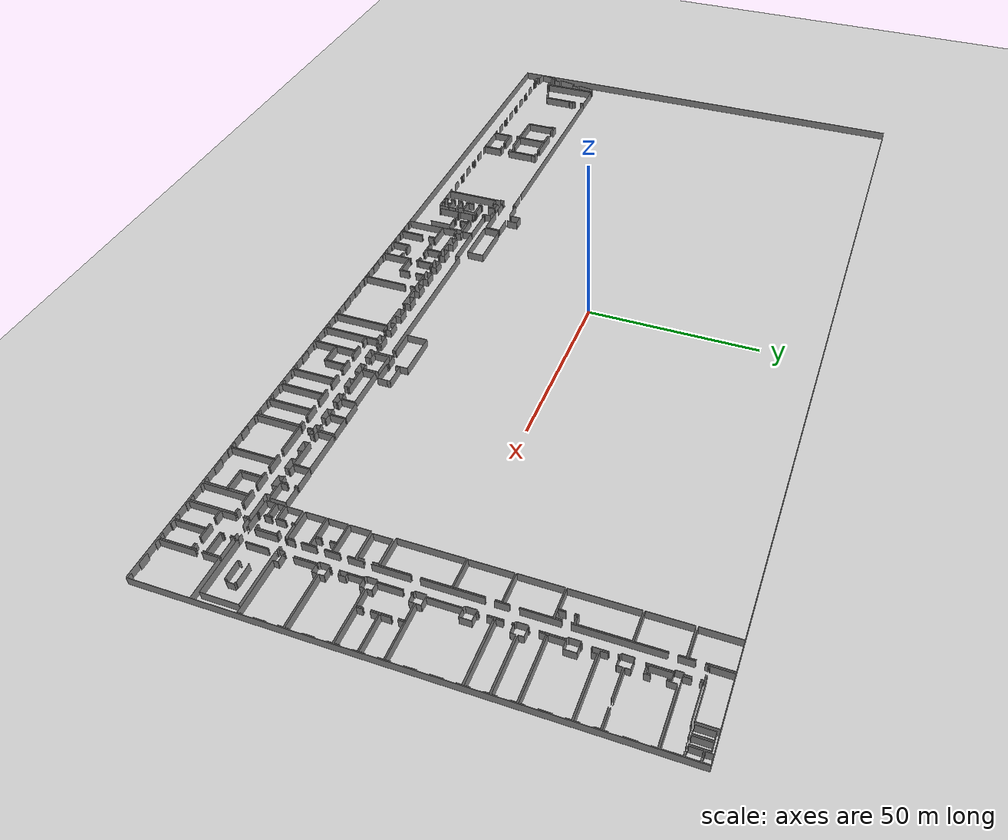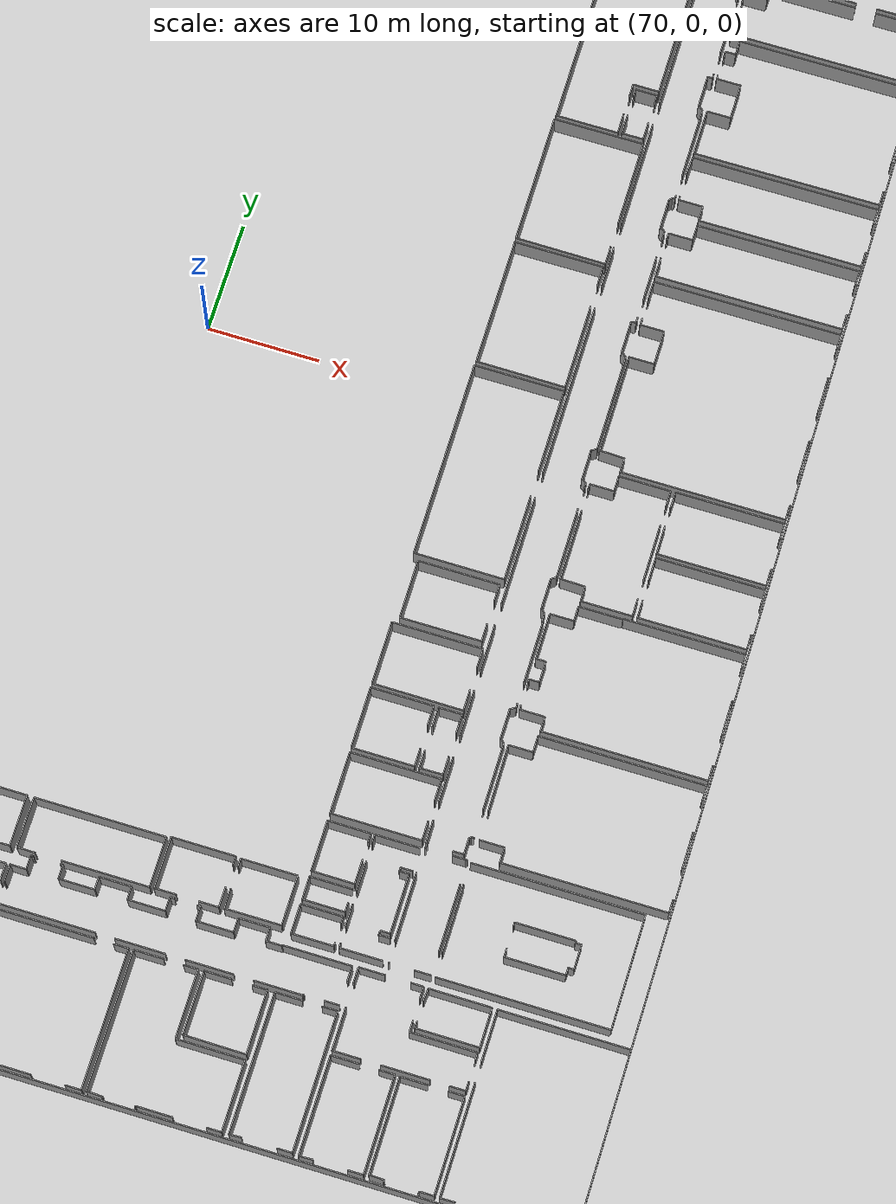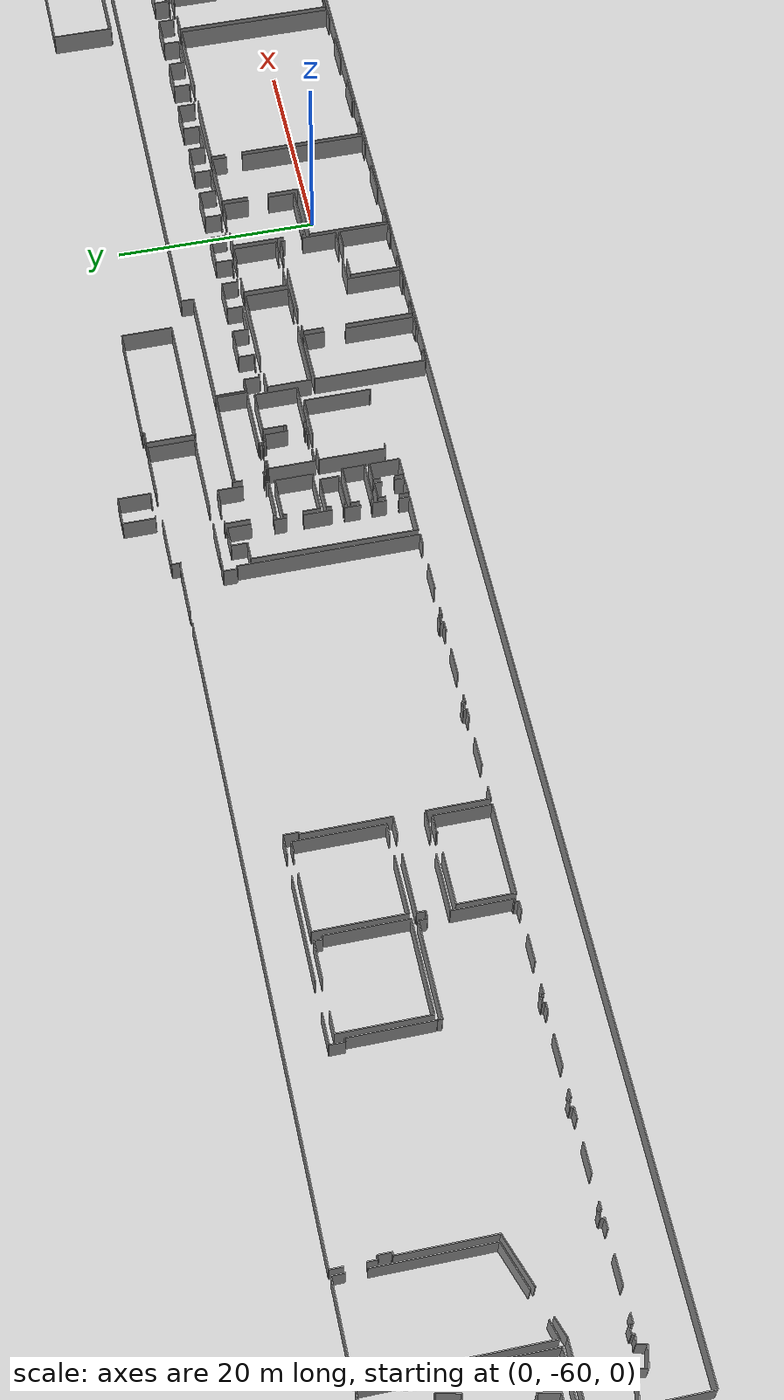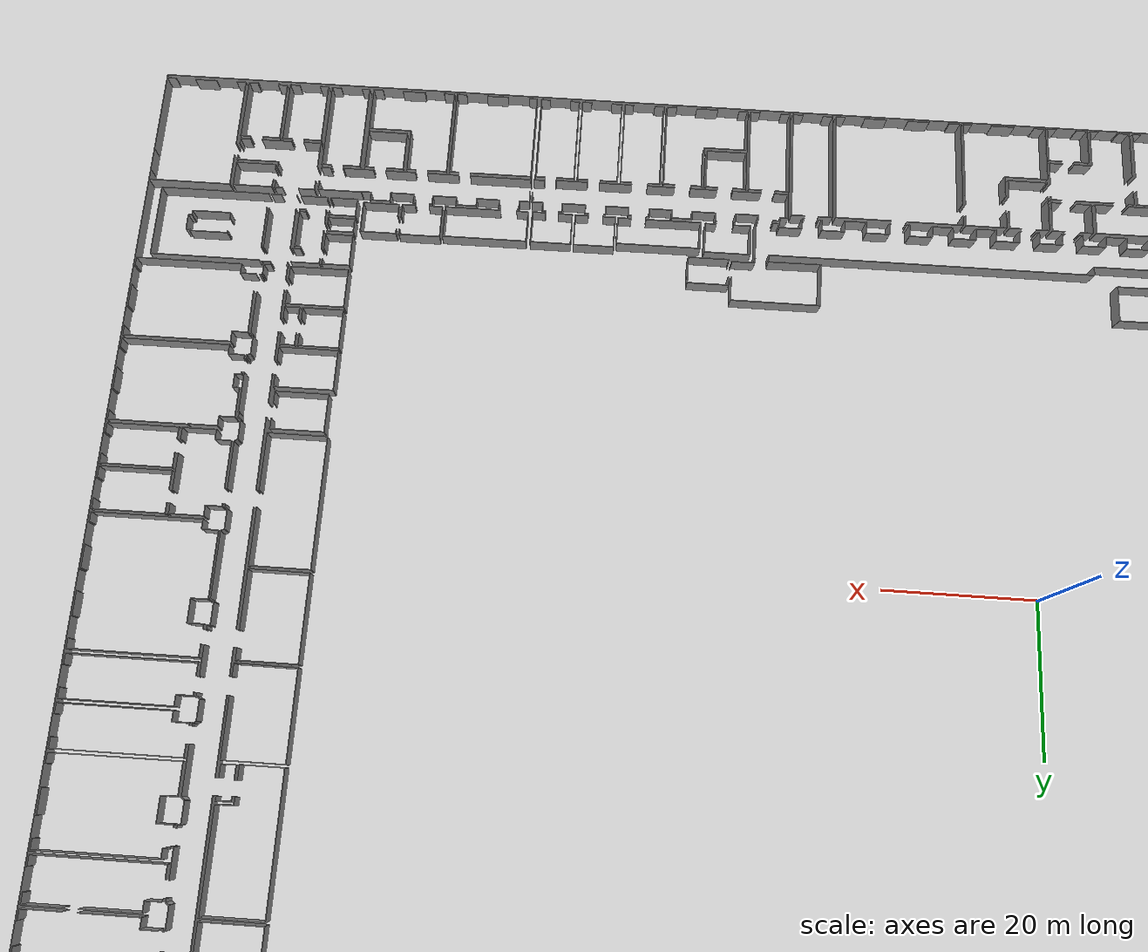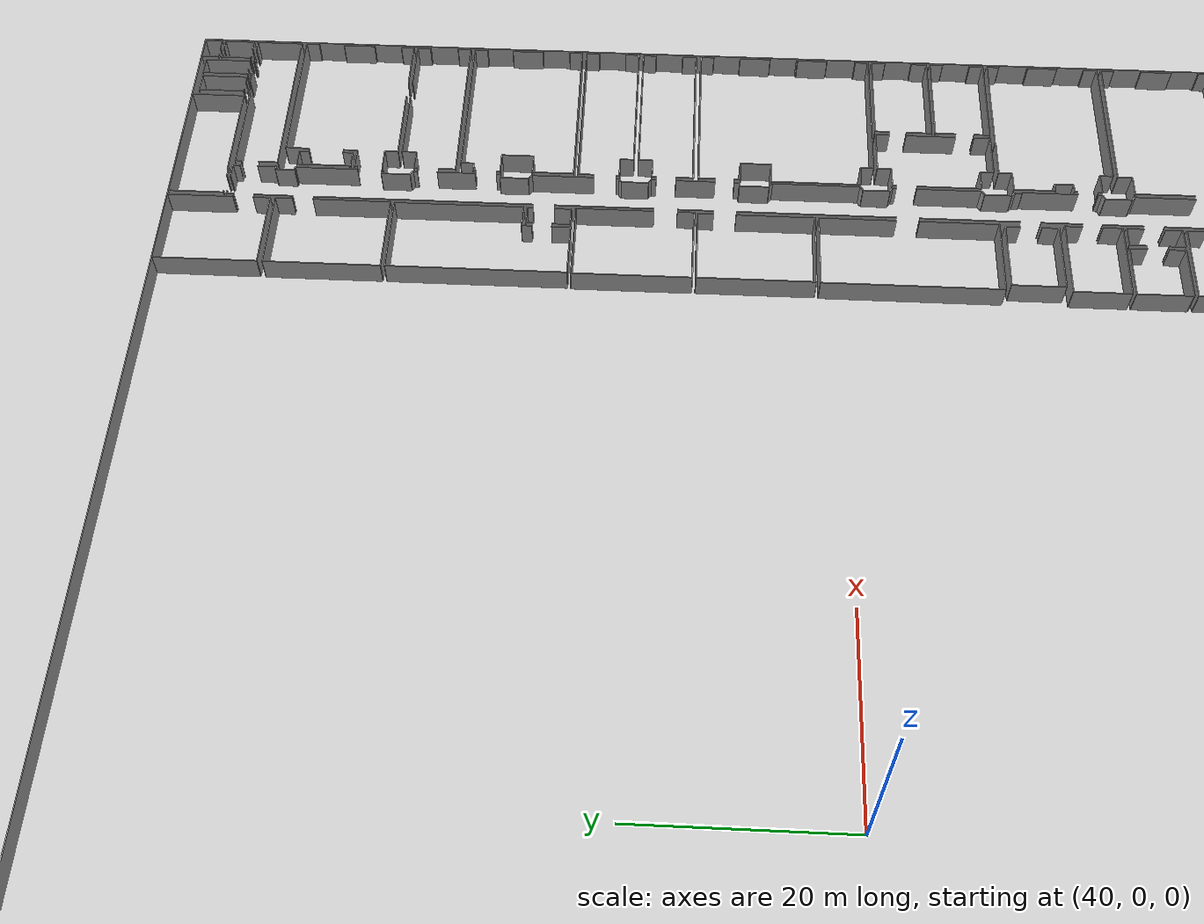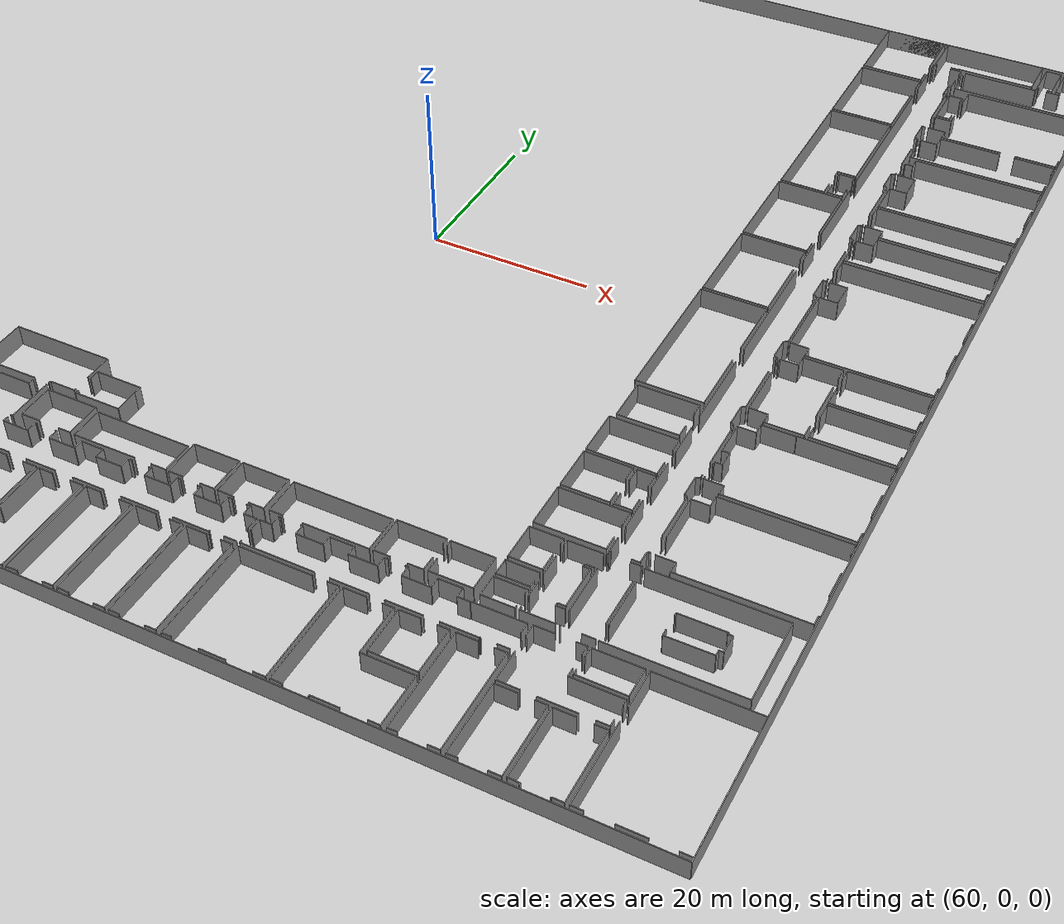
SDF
<sdf version="1.6">
  <world name="default">
    <light name="sun" type="directional">
      <cast_shadows>1</cast_shadows>
      <pose frame="">0 0 10 0 -0 0</pose>
      <diffuse>0.8 0.8 0.8 1</diffuse>
      <specular>0.1 0.1 0.1 1</specular>
      <attenuation>
        <range>1000</range>
        <constant>0.9</constant>
        <linear>0.01</linear>
        <quadratic>0.001</quadratic>
      </attenuation>
      <direction>-0.5 0.5 -1</direction>
    </light>
    <model name="ground_plane">
      <static>1</static>
      <link name="link">
        <collision name="collision">
          <geometry>
            <plane>
              <normal>0 0 1</normal>
              <size>100 100</size>
            </plane>
          </geometry>
          <surface>
            <friction>
              <ode>
                <mu>100</mu>
                <mu2>50</mu2>
              </ode>
              <torsional>
                <ode />
              </torsional>
            </friction>
            <contact>
              <ode />
            </contact>
            <bounce />
          </surface>
          <max_contacts>10</max_contacts>
        </collision>
        <visual name="visual">
          <cast_shadows>0</cast_shadows>
          <geometry>
            <plane>
              <normal>0 0 1</normal>
              <size>100 100</size>
            </plane>
          </geometry>
          <material>
            <script>
              <uri>file://media/materials/scripts/gazebo.material</uri>
              <name>Gazebo/Grey</name>
            </script>
          </material>
        </visual>
        <self_collide>0</self_collide>
        <kinematic>0</kinematic>
        <gravity>1</gravity>
      </link>
    </model>
    <gravity>0 0 -9.8</gravity>
    <magnetic_field>6e-06 2.3e-05 -4.2e-05</magnetic_field>
    <atmosphere type="adiabatic" />
    <physics default="0" name="default_physics" type="ode">
      <max_step_size>0.001</max_step_size>
      <real_time_factor>1</real_time_factor>
      <real_time_update_rate>1000</real_time_update_rate>
    </physics>
    <scene>
      <ambient>0.4 0.4 0.4 1</ambient>
      <background>0.7 0.7 0.7 1</background>
      <shadows>1</shadows>
    </scene>
    <spherical_coordinates>
      <surface_model>EARTH_WGS84</surface_model>
      <latitude_deg>0</latitude_deg>
      <longitude_deg>0</longitude_deg>
      <elevation>0</elevation>
      <heading_deg>0</heading_deg>
    </spherical_coordinates>
  <model name="50036894">
		<static>1</static>
		<link name="Wall_0">
			<collision name="Wall_0_Collision">
				<geometry>
					<box>
						<size>1.03541084902 0.1 2.5</size>
					</box>
				</geometry>
				<pose frame="">0.517705424509 0 1.25 0 0 0</pose>
			</collision>
			<visual name="Wall_0_Visual">
				<pose frame="">0.517705424509 0 1.25 0 0 0</pose>
				<geometry>
					<box>
						<size>1.03541084902 0.1 2.5</size>
					</box>
				</geometry>
				<material>
					<script>
						<uri>file://media/materials/scripts/gazebo.material</uri>
						<name>Gazebo/Grey</name>
					</script>
					<ambient>1 1 1 1</ambient>
				</material>
			</visual>
			<pose frame="">0.918030292464 -123.576006949 0 0 0 1.31019393505</pose>
		</link>
		<link name="Wall_1">
			<collision name="Wall_1_Collision">
				<geometry>
					<box>
						<size>1.06831560757 0.1 2.5</size>
					</box>
				</geometry>
				<pose frame="">0.534157803784 0 1.25 0 0 0</pose>
			</collision>
			<visual name="Wall_1_Visual">
				<pose frame="">0.534157803784 0 1.25 0 0 0</pose>
				<geometry>
					<box>
						<size>1.06831560757 0.1 2.5</size>
					</box>
				</geometry>
				<material>
					<script>
						<uri>file://media/materials/scripts/gazebo.material</uri>
						<name>Gazebo/Grey</name>
					</script>
					<ambient>1 1 1 1</ambient>
				</material>
			</visual>
			<pose frame="">1.18481699624 -122.575556809 0 0 0 -0.0467814323597</pose>
		</link>
		<link name="Wall_2">
			<collision name="Wall_2_Collision">
				<geometry>
					<box>
						<size>1.94596305949 0.1 2.5</size>
					</box>
				</geometry>
				<pose frame="">0.972981529745 0 1.25 0 0 0</pose>
			</collision>
			<visual name="Wall_2_Visual">
				<pose frame="">0.972981529745 0 1.25 0 0 0</pose>
				<geometry>
					<box>
						<size>1.94596305949 0.1 2.5</size>
					</box>
				</geometry>
				<material>
					<script>
						<uri>file://media/materials/scripts/gazebo.material</uri>
						<name>Gazebo/Grey</name>
					</script>
					<ambient>1 1 1 1</ambient>
				</material>
			</visual>
			<pose frame="">2.25196381135 -122.625515917 0 0 0 1.37922802808</pose>
		</link>
		<link name="Wall_3">
			<collision name="Wall_3_Collision">
				<geometry>
					<box>
						<size>1.08139587809 0.1 2.5</size>
					</box>
				</geometry>
				<pose frame="">0.540697939043 0 1.25 0 0 0</pose>
			</collision>
			<visual name="Wall_3_Visual">
				<pose frame="">0.540697939043 0 1.25 0 0 0</pose>
				<geometry>
					<box>
						<size>1.08139587809 0.1 2.5</size>
					</box>
				</geometry>
				<material>
					<script>
						<uri>file://media/materials/scripts/gazebo.material</uri>
						<name>Gazebo/Grey</name>
					</script>
					<ambient>1 1 1 1</ambient>
				</material>
			</visual>
			<pose frame="">2.6224727222 -120.71515067 0 0 0 2.94019582732</pose>
		</link>
		<link name="Wall_4">
			<collision name="Wall_4_Collision">
				<geometry>
					<box>
						<size>5.82655653459 0.1 2.5</size>
					</box>
				</geometry>
				<pose frame="">2.91327826729 0 1.25 0 0 0</pose>
			</collision>
			<visual name="Wall_4_Visual">
				<pose frame="">2.91327826729 0 1.25 0 0 0</pose>
				<geometry>
					<box>
						<size>5.82655653459 0.1 2.5</size>
					</box>
				</geometry>
				<material>
					<script>
						<uri>file://media/materials/scripts/gazebo.material</uri>
						<name>Gazebo/Grey</name>
					</script>
					<ambient>1 1 1 1</ambient>
				</material>
			</visual>
			<pose frame="">1.56293389294 -120.498830272 0 0 0 1.37490308758</pose>
		</link>
		<link name="Wall_5">
			<collision name="Wall_5_Collision">
				<geometry>
					<box>
						<size>1.10037329204 0.1 2.5</size>
					</box>
				</geometry>
				<pose frame="">0.550186646018 0 1.25 0 0 0</pose>
			</collision>
			<visual name="Wall_5_Visual">
				<pose frame="">0.550186646018 0 1.25 0 0 0</pose>
				<geometry>
					<box>
						<size>1.10037329204 0.1 2.5</size>
					</box>
				</geometry>
				<material>
					<script>
						<uri>file://media/materials/scripts/gazebo.material</uri>
						<name>Gazebo/Grey</name>
					</script>
					<ambient>1 1 1 1</ambient>
				</material>
			</visual>
			<pose frame="">2.69703098352 -114.783711302 0 0 0 -0.169278536859</pose>
		</link>
		<link name="Wall_6">
			<collision name="Wall_6_Collision">
				<geometry>
					<box>
						<size>2.11600762695 0.1 2.5</size>
					</box>
				</geometry>
				<pose frame="">1.05800381348 0 1.25 0 0 0</pose>
			</collision>
			<visual name="Wall_6_Visual">
				<pose frame="">1.05800381348 0 1.25 0 0 0</pose>
				<geometry>
					<box>
						<size>2.11600762695 0.1 2.5</size>
					</box>
				</geometry>
				<material>
					<script>
						<uri>file://media/materials/scripts/gazebo.material</uri>
						<name>Gazebo/Grey</name>
					</script>
					<ambient>1 1 1 1</ambient>
				</material>
			</visual>
			<pose frame="">3.78167616608 -114.969092557 0 0 0 1.36451608159</pose>
		</link>
		<link name="Wall_7">
			<collision name="Wall_7_Collision">
				<geometry>
					<box>
						<size>1.12786752995 0.1 2.5</size>
					</box>
				</geometry>
				<pose frame="">0.563933764975 0 1.25 0 0 0</pose>
			</collision>
			<visual name="Wall_7_Visual">
				<pose frame="">0.563933764975 0 1.25 0 0 0</pose>
				<geometry>
					<box>
						<size>1.12786752995 0.1 2.5</size>
					</box>
				</geometry>
				<material>
					<script>
						<uri>file://media/materials/scripts/gazebo.material</uri>
						<name>Gazebo/Grey</name>
					</script>
					<ambient>1 1 1 1</ambient>
				</material>
			</visual>
			<pose frame="">4.21507775996 -112.89794521 0 0 0 2.91226583465</pose>
		</link>
		<link name="Wall_8">
			<collision name="Wall_8_Collision">
				<geometry>
					<box>
						<size>5.87609077488 0.1 2.5</size>
					</box>
				</geometry>
				<pose frame="">2.93804538744 0 1.25 0 0 0</pose>
			</collision>
			<visual name="Wall_8_Visual">
				<pose frame="">2.93804538744 0 1.25 0 0 0</pose>
				<geometry>
					<box>
						<size>5.87609077488 0.1 2.5</size>
					</box>
				</geometry>
				<material>
					<script>
						<uri>file://media/materials/scripts/gazebo.material</uri>
						<name>Gazebo/Grey</name>
					</script>
					<ambient>1 1 1 1</ambient>
				</material>
			</visual>
			<pose frame="">3.11673820287 -112.641556087 0 0 0 1.36909260126</pose>
		</link>
		<link name="Wall_9">
			<collision name="Wall_9_Collision">
				<geometry>
					<box>
						<size>1.42295996995 0.1 2.5</size>
					</box>
				</geometry>
				<pose frame="">0.711479984976 0 1.25 0 0 0</pose>
			</collision>
			<visual name="Wall_9_Visual">
				<pose frame="">0.711479984976 0 1.25 0 0 0</pose>
				<geometry>
					<box>
						<size>1.42295996995 0.1 2.5</size>
					</box>
				</geometry>
				<material>
					<script>
						<uri>file://media/materials/scripts/gazebo.material</uri>
						<name>Gazebo/Grey</name>
					</script>
					<ambient>1 1 1 1</ambient>
				</material>
			</visual>
			<pose frame="">4.29394721326 -106.884593195 0 0 0 -0.00427728633726</pose>
		</link>
		<link name="Wall_10">
			<collision name="Wall_10_Collision">
				<geometry>
					<box>
						<size>3.85395203999 0.1 2.5</size>
					</box>
				</geometry>
				<pose frame="">1.92697602 0 1.25 0 0 0</pose>
			</collision>
			<visual name="Wall_10_Visual">
				<pose frame="">1.92697602 0 1.25 0 0 0</pose>
				<geometry>
					<box>
						<size>3.85395203999 0.1 2.5</size>
					</box>
				</geometry>
				<material>
					<script>
						<uri>file://media/materials/scripts/gazebo.material</uri>
						<name>Gazebo/Grey</name>
					</script>
					<ambient>1 1 1 1</ambient>
				</material>
			</visual>
			<pose frame="">5.71689416658 -106.890679583 0 0 0 -1.57086212926</pose>
		</link>
		<link name="Wall_11">
			<collision name="Wall_11_Collision">
				<geometry>
					<box>
						<size>0.185837762027 0.1 2.5</size>
					</box>
				</geometry>
				<pose frame="">0.0929188810137 0 1.25 0 0 0</pose>
			</collision>
			<visual name="Wall_11_Visual">
				<pose frame="">0.0929188810137 0 1.25 0 0 0</pose>
				<geometry>
					<box>
						<size>0.185837762027 0.1 2.5</size>
					</box>
				</geometry>
				<material>
					<script>
						<uri>file://media/materials/scripts/gazebo.material</uri>
						<name>Gazebo/Grey</name>
					</script>
					<ambient>1 1 1 1</ambient>
				</material>
			</visual>
			<pose frame="">5.71664056705 -110.744631615 0 0 0 -3.05414501133</pose>
		</link>
		<link name="Wall_12">
			<collision name="Wall_12_Collision">
				<geometry>
					<box>
						<size>1.30865062659 0.1 2.5</size>
					</box>
				</geometry>
				<pose frame="">0.654325313293 0 1.25 0 0 0</pose>
			</collision>
			<visual name="Wall_12_Visual">
				<pose frame="">0.654325313293 0 1.25 0 0 0</pose>
				<geometry>
					<box>
						<size>1.30865062659 0.1 2.5</size>
					</box>
				</geometry>
				<material>
					<script>
						<uri>file://media/materials/scripts/gazebo.material</uri>
						<name>Gazebo/Grey</name>
					</script>
					<ambient>1 1 1 1</ambient>
				</material>
			</visual>
			<pose frame="">5.53151291139 -110.760861985 0 0 0 -1.58164861392</pose>
		</link>
		<link name="Wall_13">
			<collision name="Wall_13_Collision">
				<geometry>
					<box>
						<size>0.300294931858 0.1 2.5</size>
					</box>
				</geometry>
				<pose frame="">0.150147465929 0 1.25 0 0 0</pose>
			</collision>
			<visual name="Wall_13_Visual">
				<pose frame="">0.150147465929 0 1.25 0 0 0</pose>
				<geometry>
					<box>
						<size>0.300294931858 0.1 2.5</size>
					</box>
				</geometry>
				<material>
					<script>
						<uri>file://media/materials/scripts/gazebo.material</uri>
						<name>Gazebo/Grey</name>
					</script>
					<ambient>1 1 1 1</ambient>
				</material>
			</visual>
			<pose frame="">5.5173113378 -112.069435551 0 0 0 -0.365294250753</pose>
		</link>
		<link name="Wall_14">
			<collision name="Wall_14_Collision">
				<geometry>
					<box>
						<size>11.374765204 0.1 2.5</size>
					</box>
				</geometry>
				<pose frame="">5.687382602 0 1.25 0 0 0</pose>
			</collision>
			<visual name="Wall_14_Visual">
				<pose frame="">5.687382602 0 1.25 0 0 0</pose>
				<geometry>
					<box>
						<size>11.374765204 0.1 2.5</size>
					</box>
				</geometry>
				<material>
					<script>
						<uri>file://media/materials/scripts/gazebo.material</uri>
						<name>Gazebo/Grey</name>
					</script>
					<ambient>1 1 1 1</ambient>
				</material>
			</visual>
			<pose frame="">5.79779241611 -112.176708151 0 0 0 -1.5782874914</pose>
		</link>
		<link name="Wall_15">
			<collision name="Wall_15_Collision">
				<geometry>
					<box>
						<size>1.61148666398 0.1 2.5</size>
					</box>
				</geometry>
				<pose frame="">0.805743331992 0 1.25 0 0 0</pose>
			</collision>
			<visual name="Wall_15_Visual">
				<pose frame="">0.805743331992 0 1.25 0 0 0</pose>
				<geometry>
					<box>
						<size>1.61148666398 0.1 2.5</size>
					</box>
				</geometry>
				<material>
					<script>
						<uri>file://media/materials/scripts/gazebo.material</uri>
						<name>Gazebo/Grey</name>
					</script>
					<ambient>1 1 1 1</ambient>
				</material>
			</visual>
			<pose frame="">5.7125829746 -123.551154195 0 0 0 -3.12963225447</pose>
		</link>
		<link name="Wall_16">
			<collision name="Wall_16_Collision">
				<geometry>
					<box>
						<size>1.80081889307 0.1 2.5</size>
					</box>
				</geometry>
				<pose frame="">0.900409446535 0 1.25 0 0 0</pose>
			</collision>
			<visual name="Wall_16_Visual">
				<pose frame="">0.900409446535 0 1.25 0 0 0</pose>
				<geometry>
					<box>
						<size>1.80081889307 0.1 2.5</size>
					</box>
				</geometry>
				<material>
					<script>
						<uri>file://media/materials/scripts/gazebo.material</uri>
						<name>Gazebo/Grey</name>
					</script>
					<ambient>1 1 1 1</ambient>
				</material>
			</visual>
			<pose frame="">2.71884054296 -123.570427759 0 0 0 -3.13849450831</pose>
		</link>
		<link name="Wall_17">
			<collision name="Wall_17_Collision">
				<geometry>
					<box>
						<size>16.6696041945 0.1 2.5</size>
					</box>
				</geometry>
				<pose frame="">8.33480209727 0 1.25 0 0 0</pose>
			</collision>
			<visual name="Wall_17_Visual">
				<pose frame="">8.33480209727 0 1.25 0 0 0</pose>
				<geometry>
					<box>
						<size>16.6696041945 0.1 2.5</size>
					</box>
				</geometry>
				<material>
					<script>
						<uri>file://media/materials/scripts/gazebo.material</uri>
						<name>Gazebo/Grey</name>
					</script>
					<ambient>1 1 1 1</ambient>
				</material>
			</visual>
			<pose frame="">6.3514001864 -123.503477484 0 0 0 1.57079632679</pose>
		</link>
		<link name="Wall_18">
			<collision name="Wall_18_Collision">
				<geometry>
					<box>
						<size>8.60716799067 0.1 2.5</size>
					</box>
				</geometry>
				<pose frame="">4.30358399533 0 1.25 0 0 0</pose>
			</collision>
			<visual name="Wall_18_Visual">
				<pose frame="">4.30358399533 0 1.25 0 0 0</pose>
				<geometry>
					<box>
						<size>8.60716799067 0.1 2.5</size>
					</box>
				</geometry>
				<material>
					<script>
						<uri>file://media/materials/scripts/gazebo.material</uri>
						<name>Gazebo/Grey</name>
					</script>
					<ambient>1 1 1 1</ambient>
				</material>
			</visual>
			<pose frame="">6.3514001864 -106.833873289 0 0 0 0.0</pose>
		</link>
		<link name="Wall_19">
			<collision name="Wall_19_Collision">
				<geometry>
					<box>
						<size>1.17391221652 0.1 2.5</size>
					</box>
				</geometry>
				<pose frame="">0.586956108262 0 1.25 0 0 0</pose>
			</collision>
			<visual name="Wall_19_Visual">
				<pose frame="">0.586956108262 0 1.25 0 0 0</pose>
				<geometry>
					<box>
						<size>1.17391221652 0.1 2.5</size>
					</box>
				</geometry>
				<material>
					<script>
						<uri>file://media/materials/scripts/gazebo.material</uri>
						<name>Gazebo/Grey</name>
					</script>
					<ambient>1 1 1 1</ambient>
				</material>
			</visual>
			<pose frame="">14.9585681771 -106.833873289 0 0 0 -1.57079632679</pose>
		</link>
		<link name="Wall_20">
			<collision name="Wall_20_Collision">
				<geometry>
					<box>
						<size>10.8563422072 0.1 2.5</size>
					</box>
				</geometry>
				<pose frame="">5.4281711036 0 1.25 0 0 0</pose>
			</collision>
			<visual name="Wall_20_Visual">
				<pose frame="">5.4281711036 0 1.25 0 0 0</pose>
				<geometry>
					<box>
						<size>10.8563422072 0.1 2.5</size>
					</box>
				</geometry>
				<material>
					<script>
						<uri>file://media/materials/scripts/gazebo.material</uri>
						<name>Gazebo/Grey</name>
					</script>
					<ambient>1 1 1 1</ambient>
				</material>
			</visual>
			<pose frame="">14.9585681771 -109.846635685 0 0 0 -1.57079632679</pose>
		</link>
		<link name="Wall_21">
			<collision name="Wall_21_Collision">
				<geometry>
					<box>
						<size>4.59279391636 0.1 2.5</size>
					</box>
				</geometry>
				<pose frame="">2.29639695818 0 1.25 0 0 0</pose>
			</collision>
			<visual name="Wall_21_Visual">
				<pose frame="">2.29639695818 0 1.25 0 0 0</pose>
				<geometry>
					<box>
						<size>4.59279391636 0.1 2.5</size>
					</box>
				</geometry>
				<material>
					<script>
						<uri>file://media/materials/scripts/gazebo.material</uri>
						<name>Gazebo/Grey</name>
					</script>
					<ambient>1 1 1 1</ambient>
				</material>
			</visual>
			<pose frame="">14.9585681771 -120.702977892 0 0 0 -2.81343383336</pose>
		</link>
		<link name="Wall_22">
			<collision name="Wall_22_Collision">
				<geometry>
					<box>
						<size>1.70644484447 0.1 2.5</size>
					</box>
				</geometry>
				<pose frame="">0.853222422237 0 1.25 0 0 0</pose>
			</collision>
			<visual name="Wall_22_Visual">
				<pose frame="">0.853222422237 0 1.25 0 0 0</pose>
				<geometry>
					<box>
						<size>1.70644484447 0.1 2.5</size>
					</box>
				</geometry>
				<material>
					<script>
						<uri>file://media/materials/scripts/gazebo.material</uri>
						<name>Gazebo/Grey</name>
					</script>
					<ambient>1 1 1 1</ambient>
				</material>
			</visual>
			<pose frame="">7.99878272226 -123.058410311 0 0 0 -2.87772586601</pose>
		</link>
		<link name="Wall_23">
			<collision name="Wall_23_Collision">
				<geometry>
					<box>
						<size>4.19080166254 0.1 2.5</size>
					</box>
				</geometry>
				<pose frame="">2.09540083127 0 1.25 0 0 0</pose>
			</collision>
			<visual name="Wall_23_Visual">
				<pose frame="">2.09540083127 0 1.25 0 0 0</pose>
				<geometry>
					<box>
						<size>4.19080166254 0.1 2.5</size>
					</box>
				</geometry>
				<material>
					<script>
						<uri>file://media/materials/scripts/gazebo.material</uri>
						<name>Gazebo/Grey</name>
					</script>
					<ambient>1 1 1 1</ambient>
				</material>
			</visual>
			<pose frame="">0.0096367820756 -128.278249402 0 0 0 1.38276447812</pose>
		</link>
		<link name="Wall_24">
			<collision name="Wall_24_Collision">
				<geometry>
					<box>
						<size>1.87815810663 0.1 2.5</size>
					</box>
				</geometry>
				<pose frame="">0.939079053313 0 1.25 0 0 0</pose>
			</collision>
			<visual name="Wall_24_Visual">
				<pose frame="">0.939079053313 0 1.25 0 0 0</pose>
				<geometry>
					<box>
						<size>1.87815810663 0.1 2.5</size>
					</box>
				</geometry>
				<material>
					<script>
						<uri>file://media/materials/scripts/gazebo.material</uri>
						<name>Gazebo/Grey</name>
					</script>
					<ambient>1 1 1 1</ambient>
				</material>
			</visual>
			<pose frame="">0.793005725009 -124.16131466 0 0 0 0.0</pose>
		</link>
		<link name="Wall_25">
			<collision name="Wall_25_Collision">
				<geometry>
					<box>
						<size>2.1929576048 0.1 2.5</size>
					</box>
				</geometry>
				<pose frame="">1.0964788024 0 1.25 0 0 0</pose>
			</collision>
			<visual name="Wall_25_Visual">
				<pose frame="">1.0964788024 0 1.25 0 0 0</pose>
				<geometry>
					<box>
						<size>2.1929576048 0.1 2.5</size>
					</box>
				</geometry>
				<material>
					<script>
						<uri>file://media/materials/scripts/gazebo.material</uri>
						<name>Gazebo/Grey</name>
					</script>
					<ambient>1 1 1 1</ambient>
				</material>
			</visual>
			<pose frame="">4.10121157175 -124.16131466 0 0 0 0.00867331089771</pose>
		</link>
		<link name="Wall_26">
			<collision name="Wall_26_Collision">
				<geometry>
					<box>
						<size>1.96582859404 0.1 2.5</size>
					</box>
				</geometry>
				<pose frame="">0.98291429702 0 1.25 0 0 0</pose>
			</collision>
			<visual name="Wall_26_Visual">
				<pose frame="">0.98291429702 0 1.25 0 0 0</pose>
				<geometry>
					<box>
						<size>1.96582859404 0.1 2.5</size>
					</box>
				</geometry>
				<material>
					<script>
						<uri>file://media/materials/scripts/gazebo.material</uri>
						<name>Gazebo/Grey</name>
					</script>
					<ambient>1 1 1 1</ambient>
				</material>
			</visual>
			<pose frame="">6.294086693 -124.142294695 0 0 0 0.330970267043</pose>
		</link>
		<link name="Wall_27">
			<collision name="Wall_27_Collision">
				<geometry>
					<box>
						<size>5.08801261323 0.1 2.5</size>
					</box>
				</geometry>
				<pose frame="">2.54400630662 0 1.25 0 0 0</pose>
			</collision>
			<visual name="Wall_27_Visual">
				<pose frame="">2.54400630662 0 1.25 0 0 0</pose>
				<geometry>
					<box>
						<size>5.08801261323 0.1 2.5</size>
					</box>
				</geometry>
				<material>
					<script>
						<uri>file://media/materials/scripts/gazebo.material</uri>
						<name>Gazebo/Grey</name>
					</script>
					<ambient>1 1 1 1</ambient>
				</material>
			</visual>
			<pose frame="">10.764539178 -122.631602305 0 0 0 0.335889179357</pose>
		</link>
		<link name="Wall_28">
			<collision name="Wall_28_Collision">
				<geometry>
					<box>
						<size>8.88891706661 0.1 2.5</size>
					</box>
				</geometry>
				<pose frame="">4.44445853331 0 1.25 0 0 0</pose>
			</collision>
			<visual name="Wall_28_Visual">
				<pose frame="">4.44445853331 0 1.25 0 0 0</pose>
				<geometry>
					<box>
						<size>8.88891706661 0.1 2.5</size>
					</box>
				</geometry>
				<material>
					<script>
						<uri>file://media/materials/scripts/gazebo.material</uri>
						<name>Gazebo/Grey</name>
					</script>
					<ambient>1 1 1 1</ambient>
				</material>
			</visual>
			<pose frame="">15.5682214431 -120.954548625 0 0 0 1.57079632679</pose>
		</link>
		<link name="Wall_29">
			<collision name="Wall_29_Collision">
				<geometry>
					<box>
						<size>0.290117860381 0.1 2.5</size>
					</box>
				</geometry>
				<pose frame="">0.14505893019 0 1.25 0 0 0</pose>
			</collision>
			<visual name="Wall_29_Visual">
				<pose frame="">0.14505893019 0 1.25 0 0 0</pose>
				<geometry>
					<box>
						<size>0.290117860381 0.1 2.5</size>
					</box>
				</geometry>
				<material>
					<script>
						<uri>file://media/materials/scripts/gazebo.material</uri>
						<name>Gazebo/Grey</name>
					</script>
					<ambient>1 1 1 1</ambient>
				</material>
			</visual>
			<pose frame="">15.5682214431 -112.065631558 0 0 0 0.0</pose>
		</link>
		<link name="Wall_30">
			<collision name="Wall_30_Collision">
				<geometry>
					<box>
						<size>1.27332323162 0.1 2.5</size>
					</box>
				</geometry>
				<pose frame="">0.636661615809 0 1.25 0 0 0</pose>
			</collision>
			<visual name="Wall_30_Visual">
				<pose frame="">0.636661615809 0 1.25 0 0 0</pose>
				<geometry>
					<box>
						<size>1.27332323162 0.1 2.5</size>
					</box>
				</geometry>
				<material>
					<script>
						<uri>file://media/materials/scripts/gazebo.material</uri>
						<name>Gazebo/Grey</name>
					</script>
					<ambient>1 1 1 1</ambient>
				</material>
			</visual>
			<pose frame="">15.8583393035 -112.065631558 0 0 0 1.57079632679</pose>
		</link>
		<link name="Wall_31">
			<collision name="Wall_31_Collision">
				<geometry>
					<box>
						<size>0.365690519816 0.1 2.5</size>
					</box>
				</geometry>
				<pose frame="">0.182845259908 0 1.25 0 0 0</pose>
			</collision>
			<visual name="Wall_31_Visual">
				<pose frame="">0.182845259908 0 1.25 0 0 0</pose>
				<geometry>
					<box>
						<size>0.365690519816 0.1 2.5</size>
					</box>
				</geometry>
				<material>
					<script>
						<uri>file://media/materials/scripts/gazebo.material</uri>
						<name>Gazebo/Grey</name>
					</script>
					<ambient>1 1 1 1</ambient>
				</material>
			</visual>
			<pose frame="">15.8583393035 -110.792308326 0 0 0 3.14159265359</pose>
		</link>
		<link name="Wall_32">
			<collision name="Wall_32_Collision">
				<geometry>
					<box>
						<size>0.907886311331 0.1 2.5</size>
					</box>
				</geometry>
				<pose frame="">0.453943155666 0 1.25 0 0 0</pose>
			</collision>
			<visual name="Wall_32_Visual">
				<pose frame="">0.453943155666 0 1.25 0 0 0</pose>
				<geometry>
					<box>
						<size>0.907886311331 0.1 2.5</size>
					</box>
				</geometry>
				<material>
					<script>
						<uri>file://media/materials/scripts/gazebo.material</uri>
						<name>Gazebo/Grey</name>
					</script>
					<ambient>1 1 1 1</ambient>
				</material>
			</visual>
			<pose frame="">15.4926487837 -110.792308326 0 0 0 1.57079632679</pose>
		</link>
		<link name="Wall_33">
			<collision name="Wall_33_Collision">
				<geometry>
					<box>
						<size>1.22640731888 0.1 2.5</size>
					</box>
				</geometry>
				<pose frame="">0.613203659441 0 1.25 0 0 0</pose>
			</collision>
			<visual name="Wall_33_Visual">
				<pose frame="">0.613203659441 0 1.25 0 0 0</pose>
				<geometry>
					<box>
						<size>1.22640731888 0.1 2.5</size>
					</box>
				</geometry>
				<material>
					<script>
						<uri>file://media/materials/scripts/gazebo.material</uri>
						<name>Gazebo/Grey</name>
					</script>
					<ambient>1 1 1 1</ambient>
				</material>
			</visual>
			<pose frame="">15.4926487837 -107.985215147 0 0 0 1.57079632679</pose>
		</link>
		<link name="Wall_34">
			<collision name="Wall_34_Collision">
				<geometry>
					<box>
						<size>61.6084550083 0.1 2.5</size>
					</box>
				</geometry>
				<pose frame="">30.8042275041 0 1.25 0 0 0</pose>
			</collision>
			<visual name="Wall_34_Visual">
				<pose frame="">30.8042275041 0 1.25 0 0 0</pose>
				<geometry>
					<box>
						<size>61.6084550083 0.1 2.5</size>
					</box>
				</geometry>
				<material>
					<script>
						<uri>file://media/materials/scripts/gazebo.material</uri>
						<name>Gazebo/Grey</name>
					</script>
					<ambient>1 1 1 1</ambient>
				</material>
			</visual>
			<pose frame="">15.4926487837 -106.758807829 0 0 0 0.0</pose>
		</link>
		<link name="Wall_35">
			<collision name="Wall_35_Collision">
				<geometry>
					<box>
						<size>4.90410767836 0.1 2.5</size>
					</box>
				</geometry>
				<pose frame="">2.45205383918 0 1.25 0 0 0</pose>
			</collision>
			<visual name="Wall_35_Visual">
				<pose frame="">2.45205383918 0 1.25 0 0 0</pose>
				<geometry>
					<box>
						<size>4.90410767836 0.1 2.5</size>
					</box>
				</geometry>
				<material>
					<script>
						<uri>file://media/materials/scripts/gazebo.material</uri>
						<name>Gazebo/Grey</name>
					</script>
					<ambient>1 1 1 1</ambient>
				</material>
			</visual>
			<pose frame="">78.3310615042 -106.758807829 0 0 0 0.0</pose>
		</link>
		<link name="Wall_36">
			<collision name="Wall_36_Collision">
				<geometry>
					<box>
						<size>1.19546817643 0.1 2.5</size>
					</box>
				</geometry>
				<pose frame="">0.597734088215 0 1.25 0 0 0</pose>
			</collision>
			<visual name="Wall_36_Visual">
				<pose frame="">0.597734088215 0 1.25 0 0 0</pose>
				<geometry>
					<box>
						<size>1.19546817643 0.1 2.5</size>
					</box>
				</geometry>
				<material>
					<script>
						<uri>file://media/materials/scripts/gazebo.material</uri>
						<name>Gazebo/Grey</name>
					</script>
					<ambient>1 1 1 1</ambient>
				</material>
			</visual>
			<pose frame="">83.2351691826 -110.578016725 0 0 0 3.14159265359</pose>
		</link>
		<link name="Wall_37">
			<collision name="Wall_37_Collision">
				<geometry>
					<box>
						<size>1.29234319624 0.1 2.5</size>
					</box>
				</geometry>
				<pose frame="">0.646171598121 0 1.25 0 0 0</pose>
			</collision>
			<visual name="Wall_37_Visual">
				<pose frame="">0.646171598121 0 1.25 0 0 0</pose>
				<geometry>
					<box>
						<size>1.29234319624 0.1 2.5</size>
					</box>
				</geometry>
				<material>
					<script>
						<uri>file://media/materials/scripts/gazebo.material</uri>
						<name>Gazebo/Grey</name>
					</script>
					<ambient>1 1 1 1</ambient>
				</material>
			</visual>
			<pose frame="">82.0397010062 -110.578016725 0 0 0 -1.57079632679</pose>
		</link>
		<link name="Wall_38">
			<collision name="Wall_38_Collision">
				<geometry>
					<box>
						<size>0.300261841513 0.1 2.5</size>
					</box>
				</geometry>
				<pose frame="">0.150130920756 0 1.25 0 0 0</pose>
			</collision>
			<visual name="Wall_38_Visual">
				<pose frame="">0.150130920756 0 1.25 0 0 0</pose>
				<geometry>
					<box>
						<size>0.300261841513 0.1 2.5</size>
					</box>
				</geometry>
				<material>
					<script>
						<uri>file://media/materials/scripts/gazebo.material</uri>
						<name>Gazebo/Grey</name>
					</script>
					<ambient>1 1 1 1</ambient>
				</material>
			</visual>
			<pose frame="">82.0397010062 -111.870359921 0 0 0 0.0</pose>
		</link>
		<link name="Wall_39">
			<collision name="Wall_39_Collision">
				<geometry>
					<box>
						<size>17.5417329724 0.1 2.5</size>
					</box>
				</geometry>
				<pose frame="">8.77086648619 0 1.25 0 0 0</pose>
			</collision>
			<visual name="Wall_39_Visual">
				<pose frame="">8.77086648619 0 1.25 0 0 0</pose>
				<geometry>
					<box>
						<size>17.5417329724 0.1 2.5</size>
					</box>
				</geometry>
				<material>
					<script>
						<uri>file://media/materials/scripts/gazebo.material</uri>
						<name>Gazebo/Grey</name>
					</script>
					<ambient>1 1 1 1</ambient>
				</material>
			</visual>
			<pose frame="">82.3399628477 -111.870359921 0 0 0 -1.57079632679</pose>
		</link>
		<link name="Wall_40">
			<collision name="Wall_40_Collision">
				<geometry>
					<box>
						<size>1.2051049585 0.1 2.5</size>
					</box>
				</geometry>
				<pose frame="">0.602552479252 0 1.25 0 0 0</pose>
			</collision>
			<visual name="Wall_40_Visual">
				<pose frame="">0.602552479252 0 1.25 0 0 0</pose>
				<geometry>
					<box>
						<size>1.2051049585 0.1 2.5</size>
					</box>
				</geometry>
				<material>
					<script>
						<uri>file://media/materials/scripts/gazebo.material</uri>
						<name>Gazebo/Grey</name>
					</script>
					<ambient>1 1 1 1</ambient>
				</material>
			</visual>
			<pose frame="">82.3399628477 -129.412092894 0 0 0 3.14159265359</pose>
		</link>
		<link name="Wall_41">
			<collision name="Wall_41_Collision">
				<geometry>
					<box>
						<size>2.71351495286 0.1 2.5</size>
					</box>
				</geometry>
				<pose frame="">1.35675747643 0 1.25 0 0 0</pose>
			</collision>
			<visual name="Wall_41_Visual">
				<pose frame="">1.35675747643 0 1.25 0 0 0</pose>
				<geometry>
					<box>
						<size>2.71351495286 0.1 2.5</size>
					</box>
				</geometry>
				<material>
					<script>
						<uri>file://media/materials/scripts/gazebo.material</uri>
						<name>Gazebo/Grey</name>
					</script>
					<ambient>1 1 1 1</ambient>
				</material>
			</visual>
			<pose frame="">78.9792618986 -129.412092894 0 0 0 3.14159265359</pose>
		</link>
		<link name="Wall_42">
			<collision name="Wall_42_Collision">
				<geometry>
					<box>
						<size>0.786158537745 0.1 2.5</size>
					</box>
				</geometry>
				<pose frame="">0.393079268873 0 1.25 0 0 0</pose>
			</collision>
			<visual name="Wall_42_Visual">
				<pose frame="">0.393079268873 0 1.25 0 0 0</pose>
				<geometry>
					<box>
						<size>0.786158537745 0.1 2.5</size>
					</box>
				</geometry>
				<material>
					<script>
						<uri>file://media/materials/scripts/gazebo.material</uri>
						<name>Gazebo/Grey</name>
					</script>
					<ambient>1 1 1 1</ambient>
				</material>
			</visual>
			<pose frame="">74.1101509551 -129.412092894 0 0 0 3.14159265359</pose>
		</link>
		<link name="Wall_43">
			<collision name="Wall_43_Collision">
				<geometry>
					<box>
						<size>0.3261289934 0.1 2.5</size>
					</box>
				</geometry>
				<pose frame="">0.1630644967 0 1.25 0 0 0</pose>
			</collision>
			<visual name="Wall_43_Visual">
				<pose frame="">0.1630644967 0 1.25 0 0 0</pose>
				<geometry>
					<box>
						<size>0.3261289934 0.1 2.5</size>
					</box>
				</geometry>
				<material>
					<script>
						<uri>file://media/materials/scripts/gazebo.material</uri>
						<name>Gazebo/Grey</name>
					</script>
					<ambient>1 1 1 1</ambient>
				</material>
			</visual>
			<pose frame="">73.3239924174 -129.412092894 0 0 0 1.57079632679</pose>
		</link>
		<link name="Wall_44">
			<collision name="Wall_44_Collision">
				<geometry>
					<box>
						<size>0.811518490576 0.1 2.5</size>
					</box>
				</geometry>
				<pose frame="">0.405759245288 0 1.25 0 0 0</pose>
			</collision>
			<visual name="Wall_44_Visual">
				<pose frame="">0.405759245288 0 1.25 0 0 0</pose>
				<geometry>
					<box>
						<size>0.811518490576 0.1 2.5</size>
					</box>
				</geometry>
				<material>
					<script>
						<uri>file://media/materials/scripts/gazebo.material</uri>
						<name>Gazebo/Grey</name>
					</script>
					<ambient>1 1 1 1</ambient>
				</material>
			</visual>
			<pose frame="">73.3239924174 -129.0859639 0 0 0 3.14159265359</pose>
		</link>
		<link name="Wall_45">
			<collision name="Wall_45_Collision">
				<geometry>
					<box>
						<size>0.329679386796 0.1 2.5</size>
					</box>
				</geometry>
				<pose frame="">0.164839693398 0 1.25 0 0 0</pose>
			</collision>
			<visual name="Wall_45_Visual">
				<pose frame="">0.164839693398 0 1.25 0 0 0</pose>
				<geometry>
					<box>
						<size>0.329679386796 0.1 2.5</size>
					</box>
				</geometry>
				<material>
					<script>
						<uri>file://media/materials/scripts/gazebo.material</uri>
						<name>Gazebo/Grey</name>
					</script>
					<ambient>1 1 1 1</ambient>
				</material>
			</visual>
			<pose frame="">72.5124739268 -129.0859639 0 0 0 -1.57079632679</pose>
		</link>
		<link name="Wall_46">
			<collision name="Wall_46_Collision">
				<geometry>
					<box>
						<size>0.912958301898 0.1 2.5</size>
					</box>
				</geometry>
				<pose frame="">0.456479150949 0 1.25 0 0 0</pose>
			</collision>
			<visual name="Wall_46_Visual">
				<pose frame="">0.456479150949 0 1.25 0 0 0</pose>
				<geometry>
					<box>
						<size>0.912958301898 0.1 2.5</size>
					</box>
				</geometry>
				<material>
					<script>
						<uri>file://media/materials/scripts/gazebo.material</uri>
						<name>Gazebo/Grey</name>
					</script>
					<ambient>1 1 1 1</ambient>
				</material>
			</visual>
			<pose frame="">72.5124739268 -129.415643287 0 0 0 3.14159265359</pose>
		</link>
		<link name="Wall_47">
			<collision name="Wall_47_Collision">
				<geometry>
					<box>
						<size>2.79644199862 0.1 2.5</size>
					</box>
				</geometry>
				<pose frame="">1.39822099931 0 1.25 0 0 0</pose>
			</collision>
			<visual name="Wall_47_Visual">
				<pose frame="">1.39822099931 0 1.25 0 0 0</pose>
				<geometry>
					<box>
						<size>2.79644199862 0.1 2.5</size>
					</box>
				</geometry>
				<material>
					<script>
						<uri>file://media/materials/scripts/gazebo.material</uri>
						<name>Gazebo/Grey</name>
					</script>
					<ambient>1 1 1 1</ambient>
				</material>
			</visual>
			<pose frame="">69.6214393041 -129.415643287 0 0 0 3.14159265359</pose>
		</link>
		<link name="Wall_48">
			<collision name="Wall_48_Collision">
				<geometry>
					<box>
						<size>0.819633675481 0.1 2.5</size>
					</box>
				</geometry>
				<pose frame="">0.409816837741 0 1.25 0 0 0</pose>
			</collision>
			<visual name="Wall_48_Visual">
				<pose frame="">0.409816837741 0 1.25 0 0 0</pose>
				<geometry>
					<box>
						<size>0.819633675481 0.1 2.5</size>
					</box>
				</geometry>
				<material>
					<script>
						<uri>file://media/materials/scripts/gazebo.material</uri>
						<name>Gazebo/Grey</name>
					</script>
					<ambient>1 1 1 1</ambient>
				</material>
			</visual>
			<pose frame="">64.7158100286 -129.415643287 0 0 0 3.14159265359</pose>
		</link>
		<link name="Wall_49">
			<collision name="Wall_49_Collision">
				<geometry>
					<box>
						<size>0.328664988683 0.1 2.5</size>
					</box>
				</geometry>
				<pose frame="">0.164332494342 0 1.25 0 0 0</pose>
			</collision>
			<visual name="Wall_49_Visual">
				<pose frame="">0.164332494342 0 1.25 0 0 0</pose>
				<geometry>
					<box>
						<size>0.328664988683 0.1 2.5</size>
					</box>
				</geometry>
				<material>
					<script>
						<uri>file://media/materials/scripts/gazebo.material</uri>
						<name>Gazebo/Grey</name>
					</script>
					<ambient>1 1 1 1</ambient>
				</material>
			</visual>
			<pose frame="">63.8961763531 -129.415643287 0 0 0 1.57079632679</pose>
		</link>
		<link name="Wall_50">
			<collision name="Wall_50_Collision">
				<geometry>
					<box>
						<size>0.731381039631 0.1 2.5</size>
					</box>
				</geometry>
				<pose frame="">0.365690519816 0 1.25 0 0 0</pose>
			</collision>
			<visual name="Wall_50_Visual">
				<pose frame="">0.365690519816 0 1.25 0 0 0</pose>
				<geometry>
					<box>
						<size>0.731381039631 0.1 2.5</size>
					</box>
				</geometry>
				<material>
					<script>
						<uri>file://media/materials/scripts/gazebo.material</uri>
						<name>Gazebo/Grey</name>
					</script>
					<ambient>1 1 1 1</ambient>
				</material>
			</visual>
			<pose frame="">63.8961763531 -129.086978298 0 0 0 3.14159265359</pose>
		</link>
		<link name="Wall_51">
			<collision name="Wall_51_Collision">
				<geometry>
					<box>
						<size>0.302797836796 0.1 2.5</size>
					</box>
				</geometry>
				<pose frame="">0.151398918398 0 1.25 0 0 0</pose>
			</collision>
			<visual name="Wall_51_Visual">
				<pose frame="">0.151398918398 0 1.25 0 0 0</pose>
				<geometry>
					<box>
						<size>0.302797836796 0.1 2.5</size>
					</box>
				</geometry>
				<material>
					<script>
						<uri>file://media/materials/scripts/gazebo.material</uri>
						<name>Gazebo/Grey</name>
					</script>
					<ambient>1 1 1 1</ambient>
				</material>
			</visual>
			<pose frame="">63.1647953135 -129.086978298 0 0 0 -1.57079632679</pose>
		</link>
		<link name="Wall_52">
			<collision name="Wall_52_Collision">
				<geometry>
					<box>
						<size>0.882526358501 0.1 2.5</size>
					</box>
				</geometry>
				<pose frame="">0.44126317925 0 1.25 0 0 0</pose>
			</collision>
			<visual name="Wall_52_Visual">
				<pose frame="">0.44126317925 0 1.25 0 0 0</pose>
				<geometry>
					<box>
						<size>0.882526358501 0.1 2.5</size>
					</box>
				</geometry>
				<material>
					<script>
						<uri>file://media/materials/scripts/gazebo.material</uri>
						<name>Gazebo/Grey</name>
					</script>
					<ambient>1 1 1 1</ambient>
				</material>
			</visual>
			<pose frame="">63.1647953135 -129.389776135 0 0 0 3.14159265359</pose>
		</link>
		<link name="Wall_53">
			<collision name="Wall_53_Collision">
				<geometry>
					<box>
						<size>2.82256275003 0.1 2.5</size>
					</box>
				</geometry>
				<pose frame="">1.41128137502 0 1.25 0 0 0</pose>
			</collision>
			<visual name="Wall_53_Visual">
				<pose frame="">1.41128137502 0 1.25 0 0 0</pose>
				<geometry>
					<box>
						<size>2.82256275003 0.1 2.5</size>
					</box>
				</geometry>
				<material>
					<script>
						<uri>file://media/materials/scripts/gazebo.material</uri>
						<name>Gazebo/Grey</name>
					</script>
					<ambient>1 1 1 1</ambient>
				</material>
			</visual>
			<pose frame="">60.1786608677 -129.389776135 0 0 0 3.14159265359</pose>
		</link>
		<link name="Wall_54">
			<collision name="Wall_54_Collision">
				<geometry>
					<box>
						<size>1.19090338492 0.1 2.5</size>
					</box>
				</geometry>
				<pose frame="">0.59545169246 0 1.25 0 0 0</pose>
			</collision>
			<visual name="Wall_54_Visual">
				<pose frame="">0.59545169246 0 1.25 0 0 0</pose>
				<geometry>
					<box>
						<size>1.19090338492 0.1 2.5</size>
					</box>
				</geometry>
				<material>
					<script>
						<uri>file://media/materials/scripts/gazebo.material</uri>
						<name>Gazebo/Grey</name>
					</script>
					<ambient>1 1 1 1</ambient>
				</material>
			</visual>
			<pose frame="">55.1507966195 -129.389776135 0 0 0 3.14159265359</pose>
		</link>
		<link name="Wall_55">
			<collision name="Wall_55_Collision">
				<geometry>
					<box>
						<size>5.94817693639 0.1 2.5</size>
					</box>
				</geometry>
				<pose frame="">2.9740884682 0 1.25 0 0 0</pose>
			</collision>
			<visual name="Wall_55_Visual">
				<pose frame="">2.9740884682 0 1.25 0 0 0</pose>
				<geometry>
					<box>
						<size>5.94817693639 0.1 2.5</size>
					</box>
				</geometry>
				<material>
					<script>
						<uri>file://media/materials/scripts/gazebo.material</uri>
						<name>Gazebo/Grey</name>
					</script>
					<ambient>1 1 1 1</ambient>
				</material>
			</visual>
			<pose frame="">53.9598932346 -129.389776135 0 0 0 1.57079632679</pose>
		</link>
		<link name="Wall_56">
			<collision name="Wall_56_Collision">
				<geometry>
					<box>
						<size>2.24917421654 0.1 2.5</size>
					</box>
				</geometry>
				<pose frame="">1.12458710827 0 1.25 0 0 0</pose>
			</collision>
			<visual name="Wall_56_Visual">
				<pose frame="">1.12458710827 0 1.25 0 0 0</pose>
				<geometry>
					<box>
						<size>2.24917421654 0.1 2.5</size>
					</box>
				</geometry>
				<material>
					<script>
						<uri>file://media/materials/scripts/gazebo.material</uri>
						<name>Gazebo/Grey</name>
					</script>
					<ambient>1 1 1 1</ambient>
				</material>
			</visual>
			<pose frame="">53.9598932346 -123.441599199 0 0 0 3.14159265359</pose>
		</link>
		<link name="Wall_57">
			<collision name="Wall_57_Collision">
				<geometry>
					<box>
						<size>0.0 0.1 2.5</size>
					</box>
				</geometry>
				<pose frame="">0.0 0 1.25 0 0 0</pose>
			</collision>
			<visual name="Wall_57_Visual">
				<pose frame="">0.0 0 1.25 0 0 0</pose>
				<geometry>
					<box>
						<size>0.0 0.1 2.5</size>
					</box>
				</geometry>
				<material>
					<script>
						<uri>file://media/materials/scripts/gazebo.material</uri>
						<name>Gazebo/Grey</name>
					</script>
					<ambient>1 1 1 1</ambient>
				</material>
			</visual>
			<pose frame="">51.7107190181 -123.441599199 0 0 0 0.0</pose>
		</link>
		<link name="Wall_58">
			<collision name="Wall_58_Collision">
				<geometry>
					<box>
						<size>5.56777764393 0.1 2.5</size>
					</box>
				</geometry>
				<pose frame="">2.78388882197 0 1.25 0 0 0</pose>
			</collision>
			<visual name="Wall_58_Visual">
				<pose frame="">2.78388882197 0 1.25 0 0 0</pose>
				<geometry>
					<box>
						<size>5.56777764393 0.1 2.5</size>
					</box>
				</geometry>
				<material>
					<script>
						<uri>file://media/materials/scripts/gazebo.material</uri>
						<name>Gazebo/Grey</name>
					</script>
					<ambient>1 1 1 1</ambient>
				</material>
			</visual>
			<pose frame="">49.7077899435 -123.441599199 0 0 0 3.14159265359</pose>
		</link>
		<link name="Wall_59">
			<collision name="Wall_59_Collision">
				<geometry>
					<box>
						<size>5.62534473686 0.1 2.5</size>
					</box>
				</geometry>
				<pose frame="">2.81267236843 0 1.25 0 0 0</pose>
			</collision>
			<visual name="Wall_59_Visual">
				<pose frame="">2.81267236843 0 1.25 0 0 0</pose>
				<geometry>
					<box>
						<size>5.62534473686 0.1 2.5</size>
					</box>
				</geometry>
				<material>
					<script>
						<uri>file://media/materials/scripts/gazebo.material</uri>
						<name>Gazebo/Grey</name>
					</script>
					<ambient>1 1 1 1</ambient>
				</material>
			</visual>
			<pose frame="">44.1400122996 -123.441599199 0 0 0 -1.57079632679</pose>
		</link>
		<link name="Wall_60">
			<collision name="Wall_60_Collision">
				<geometry>
					<box>
						<size>0.325875393872 0.1 2.5</size>
					</box>
				</geometry>
				<pose frame="">0.162937696936 0 1.25 0 0 0</pose>
			</collision>
			<visual name="Wall_60_Visual">
				<pose frame="">0.162937696936 0 1.25 0 0 0</pose>
				<geometry>
					<box>
						<size>0.325875393872 0.1 2.5</size>
					</box>
				</geometry>
				<material>
					<script>
						<uri>file://media/materials/scripts/gazebo.material</uri>
						<name>Gazebo/Grey</name>
					</script>
					<ambient>1 1 1 1</ambient>
				</material>
			</visual>
			<pose frame="">44.1400122996 -129.066943935 0 0 0 3.14159265359</pose>
		</link>
		<link name="Wall_61">
			<collision name="Wall_61_Collision">
				<geometry>
					<box>
						<size>0.364422522174 0.1 2.5</size>
					</box>
				</geometry>
				<pose frame="">0.182211261087 0 1.25 0 0 0</pose>
			</collision>
			<visual name="Wall_61_Visual">
				<pose frame="">0.182211261087 0 1.25 0 0 0</pose>
				<geometry>
					<box>
						<size>0.364422522174 0.1 2.5</size>
					</box>
				</geometry>
				<material>
					<script>
						<uri>file://media/materials/scripts/gazebo.material</uri>
						<name>Gazebo/Grey</name>
					</script>
					<ambient>1 1 1 1</ambient>
				</material>
			</visual>
			<pose frame="">43.8141369057 -129.066943935 0 0 0 -1.57079632679</pose>
		</link>
		<link name="Wall_62">
			<collision name="Wall_62_Collision">
				<geometry>
					<box>
						<size>0.987262963691 0.1 2.5</size>
					</box>
				</geometry>
				<pose frame="">0.493631481845 0 1.25 0 0 0</pose>
			</collision>
			<visual name="Wall_62_Visual">
				<pose frame="">0.493631481845 0 1.25 0 0 0</pose>
				<geometry>
					<box>
						<size>0.987262963691 0.1 2.5</size>
					</box>
				</geometry>
				<material>
					<script>
						<uri>file://media/materials/scripts/gazebo.material</uri>
						<name>Gazebo/Grey</name>
					</script>
					<ambient>1 1 1 1</ambient>
				</material>
			</visual>
			<pose frame="">43.8141369057 -129.431366458 0 0 0 3.14159265359</pose>
		</link>
		<link name="Wall_63">
			<collision name="Wall_63_Collision">
				<geometry>
					<box>
						<size>2.62450151843 0.1 2.5</size>
					</box>
				</geometry>
				<pose frame="">1.31225075921 0 1.25 0 0 0</pose>
			</collision>
			<visual name="Wall_63_Visual">
				<pose frame="">1.31225075921 0 1.25 0 0 0</pose>
				<geometry>
					<box>
						<size>2.62450151843 0.1 2.5</size>
					</box>
				</geometry>
				<material>
					<script>
						<uri>file://media/materials/scripts/gazebo.material</uri>
						<name>Gazebo/Grey</name>
					</script>
					<ambient>1 1 1 1</ambient>
				</material>
			</visual>
			<pose frame="">40.623094041 -129.431366458 0 0 0 3.14159265359</pose>
		</link>
		<link name="Wall_64">
			<collision name="Wall_64_Collision">
				<geometry>
					<box>
						<size>0.920312688218 0.1 2.5</size>
					</box>
				</geometry>
				<pose frame="">0.460156344109 0 1.25 0 0 0</pose>
			</collision>
			<visual name="Wall_64_Visual">
				<pose frame="">0.460156344109 0 1.25 0 0 0</pose>
				<geometry>
					<box>
						<size>0.920312688218 0.1 2.5</size>
					</box>
				</geometry>
				<material>
					<script>
						<uri>file://media/materials/scripts/gazebo.material</uri>
						<name>Gazebo/Grey</name>
					</script>
					<ambient>1 1 1 1</ambient>
				</material>
			</visual>
			<pose frame="">35.9434219452 -129.431366458 0 0 0 3.14159265359</pose>
		</link>
		<link name="Wall_65">
			<collision name="Wall_65_Collision">
				<geometry>
					<box>
						<size>0.319028206608 0.1 2.5</size>
					</box>
				</geometry>
				<pose frame="">0.159514103304 0 1.25 0 0 0</pose>
			</collision>
			<visual name="Wall_65_Visual">
				<pose frame="">0.159514103304 0 1.25 0 0 0</pose>
				<geometry>
					<box>
						<size>0.319028206608 0.1 2.5</size>
					</box>
				</geometry>
				<material>
					<script>
						<uri>file://media/materials/scripts/gazebo.material</uri>
						<name>Gazebo/Grey</name>
					</script>
					<ambient>1 1 1 1</ambient>
				</material>
			</visual>
			<pose frame="">35.023109257 -129.431366458 0 0 0 1.57079632679</pose>
		</link>
		<link name="Wall_66">
			<collision name="Wall_66_Collision">
				<geometry>
					<box>
						<size>0.794527322179 0.1 2.5</size>
					</box>
				</geometry>
				<pose frame="">0.39726366109 0 1.25 0 0 0</pose>
			</collision>
			<visual name="Wall_66_Visual">
				<pose frame="">0.39726366109 0 1.25 0 0 0</pose>
				<geometry>
					<box>
						<size>0.794527322179 0.1 2.5</size>
					</box>
				</geometry>
				<material>
					<script>
						<uri>file://media/materials/scripts/gazebo.material</uri>
						<name>Gazebo/Grey</name>
					</script>
					<ambient>1 1 1 1</ambient>
				</material>
			</visual>
			<pose frame="">35.023109257 -129.112338251 0 0 0 3.14159265359</pose>
		</link>
		<link name="Wall_67">
			<collision name="Wall_67_Collision">
				<geometry>
					<box>
						<size>0.277437883966 0.1 2.5</size>
					</box>
				</geometry>
				<pose frame="">0.138718941983 0 1.25 0 0 0</pose>
			</collision>
			<visual name="Wall_67_Visual">
				<pose frame="">0.138718941983 0 1.25 0 0 0</pose>
				<geometry>
					<box>
						<size>0.277437883966 0.1 2.5</size>
					</box>
				</geometry>
				<material>
					<script>
						<uri>file://media/materials/scripts/gazebo.material</uri>
						<name>Gazebo/Grey</name>
					</script>
					<ambient>1 1 1 1</ambient>
				</material>
			</visual>
			<pose frame="">34.2285819348 -129.112338251 0 0 0 -1.57079632679</pose>
		</link>
		<link name="Wall_68">
			<collision name="Wall_68_Collision">
				<geometry>
					<box>
						<size>0.869846382086 0.1 2.5</size>
					</box>
				</geometry>
				<pose frame="">0.434923191043 0 1.25 0 0 0</pose>
			</collision>
			<visual name="Wall_68_Visual">
				<pose frame="">0.434923191043 0 1.25 0 0 0</pose>
				<geometry>
					<box>
						<size>0.869846382086 0.1 2.5</size>
					</box>
				</geometry>
				<material>
					<script>
						<uri>file://media/materials/scripts/gazebo.material</uri>
						<name>Gazebo/Grey</name>
					</script>
					<ambient>1 1 1 1</ambient>
				</material>
			</visual>
			<pose frame="">34.2285819348 -129.389776135 0 0 0 3.14159265359</pose>
		</link>
		<link name="Wall_69">
			<collision name="Wall_69_Collision">
				<geometry>
					<box>
						<size>3.01352319485 0.1 2.5</size>
					</box>
				</geometry>
				<pose frame="">1.50676159742 0 1.25 0 0 0</pose>
			</collision>
			<visual name="Wall_69_Visual">
				<pose frame="">1.50676159742 0 1.25 0 0 0</pose>
				<geometry>
					<box>
						<size>3.01352319485 0.1 2.5</size>
					</box>
				</geometry>
				<material>
					<script>
						<uri>file://media/materials/scripts/gazebo.material</uri>
						<name>Gazebo/Grey</name>
					</script>
					<ambient>1 1 1 1</ambient>
				</material>
			</visual>
			<pose frame="">31.3918176112 -129.389776135 0 0 0 3.14159265359</pose>
		</link>
		<link name="Wall_70">
			<collision name="Wall_70_Collision">
				<geometry>
					<box>
						<size>0.844740028784 0.1 2.5</size>
					</box>
				</geometry>
				<pose frame="">0.422370014392 0 1.25 0 0 0</pose>
			</collision>
			<visual name="Wall_70_Visual">
				<pose frame="">0.422370014392 0 1.25 0 0 0</pose>
				<geometry>
					<box>
						<size>0.844740028784 0.1 2.5</size>
					</box>
				</geometry>
				<material>
					<script>
						<uri>file://media/materials/scripts/gazebo.material</uri>
						<name>Gazebo/Grey</name>
					</script>
					<ambient>1 1 1 1</ambient>
				</material>
			</visual>
			<pose frame="">26.4113764748 -129.389776135 0 0 0 3.14159265359</pose>
		</link>
		<link name="Wall_71">
			<collision name="Wall_71_Collision">
				<geometry>
					<box>
						<size>0.277437883966 0.1 2.5</size>
					</box>
				</geometry>
				<pose frame="">0.138718941983 0 1.25 0 0 0</pose>
			</collision>
			<visual name="Wall_71_Visual">
				<pose frame="">0.138718941983 0 1.25 0 0 0</pose>
				<geometry>
					<box>
						<size>0.277437883966 0.1 2.5</size>
					</box>
				</geometry>
				<material>
					<script>
						<uri>file://media/materials/scripts/gazebo.material</uri>
						<name>Gazebo/Grey</name>
					</script>
					<ambient>1 1 1 1</ambient>
				</material>
			</visual>
			<pose frame="">25.5666364461 -129.389776135 0 0 0 1.57079632679</pose>
		</link>
		<link name="Wall_72">
			<collision name="Wall_72_Collision">
				<geometry>
					<box>
						<size>0.794273722651 0.1 2.5</size>
					</box>
				</geometry>
				<pose frame="">0.397136861325 0 1.25 0 0 0</pose>
			</collision>
			<visual name="Wall_72_Visual">
				<pose frame="">0.397136861325 0 1.25 0 0 0</pose>
				<geometry>
					<box>
						<size>0.794273722651 0.1 2.5</size>
					</box>
				</geometry>
				<material>
					<script>
						<uri>file://media/materials/scripts/gazebo.material</uri>
						<name>Gazebo/Grey</name>
					</script>
					<ambient>1 1 1 1</ambient>
				</material>
			</visual>
			<pose frame="">25.5666364461 -129.112338251 0 0 0 3.14159265359</pose>
		</link>
		<link name="Wall_73">
			<collision name="Wall_73_Collision">
				<geometry>
					<box>
						<size>0.302544237268 0.1 2.5</size>
					</box>
				</geometry>
				<pose frame="">0.151272118634 0 1.25 0 0 0</pose>
			</collision>
			<visual name="Wall_73_Visual">
				<pose frame="">0.151272118634 0 1.25 0 0 0</pose>
				<geometry>
					<box>
						<size>0.302544237268 0.1 2.5</size>
					</box>
				</geometry>
				<material>
					<script>
						<uri>file://media/materials/scripts/gazebo.material</uri>
						<name>Gazebo/Grey</name>
					</script>
					<ambient>1 1 1 1</ambient>
				</material>
			</visual>
			<pose frame="">24.7723627234 -129.112338251 0 0 0 -1.57079632679</pose>
		</link>
		<link name="Wall_74">
			<collision name="Wall_74_Collision">
				<geometry>
					<box>
						<size>1.08439158303 0.1 2.5</size>
					</box>
				</geometry>
				<pose frame="">0.542195791516 0 1.25 0 0 0</pose>
			</collision>
			<visual name="Wall_74_Visual">
				<pose frame="">0.542195791516 0 1.25 0 0 0</pose>
				<geometry>
					<box>
						<size>1.08439158303 0.1 2.5</size>
					</box>
				</geometry>
				<material>
					<script>
						<uri>file://media/materials/scripts/gazebo.material</uri>
						<name>Gazebo/Grey</name>
					</script>
					<ambient>1 1 1 1</ambient>
				</material>
			</visual>
			<pose frame="">24.7723627234 -129.414882488 0 0 0 3.14159265359</pose>
		</link>
		<link name="Wall_75">
			<collision name="Wall_75_Collision">
				<geometry>
					<box>
						<size>2.7738716406 0.1 2.5</size>
					</box>
				</geometry>
				<pose frame="">1.3869358203 0 1.25 0 0 0</pose>
			</collision>
			<visual name="Wall_75_Visual">
				<pose frame="">1.3869358203 0 1.25 0 0 0</pose>
				<geometry>
					<box>
						<size>2.7738716406 0.1 2.5</size>
					</box>
				</geometry>
				<material>
					<script>
						<uri>file://media/materials/scripts/gazebo.material</uri>
						<name>Gazebo/Grey</name>
					</script>
					<ambient>1 1 1 1</ambient>
				</material>
			</visual>
			<pose frame="">21.6708404922 -129.414882488 0 0 0 3.14159265359</pose>
		</link>
		<link name="Wall_76">
			<collision name="Wall_76_Collision">
				<geometry>
					<box>
						<size>0.727577046707 0.1 2.5</size>
					</box>
				</geometry>
				<pose frame="">0.363788523353 0 1.25 0 0 0</pose>
			</collision>
			<visual name="Wall_76_Visual">
				<pose frame="">0.363788523353 0 1.25 0 0 0</pose>
				<geometry>
					<box>
						<size>0.727577046707 0.1 2.5</size>
					</box>
				</geometry>
				<material>
					<script>
						<uri>file://media/materials/scripts/gazebo.material</uri>
						<name>Gazebo/Grey</name>
					</script>
					<ambient>1 1 1 1</ambient>
				</material>
			</visual>
			<pose frame="">16.5816051582 -129.414882488 0 0 0 3.14159265359</pose>
		</link>
		<link name="Wall_77">
			<collision name="Wall_77_Collision">
				<geometry>
					<box>
						<size>0.283777872173 0.1 2.5</size>
					</box>
				</geometry>
				<pose frame="">0.141888936087 0 1.25 0 0 0</pose>
			</collision>
			<visual name="Wall_77_Visual">
				<pose frame="">0.141888936087 0 1.25 0 0 0</pose>
				<geometry>
					<box>
						<size>0.283777872173 0.1 2.5</size>
					</box>
				</geometry>
				<material>
					<script>
						<uri>file://media/materials/scripts/gazebo.material</uri>
						<name>Gazebo/Grey</name>
					</script>
					<ambient>1 1 1 1</ambient>
				</material>
			</visual>
			<pose frame="">15.8540281115 -129.414882488 0 0 0 1.57079632679</pose>
		</link>
		<link name="Wall_78">
			<collision name="Wall_78_Collision">
				<geometry>
					<box>
						<size>0.727830646235 0.1 2.5</size>
					</box>
				</geometry>
				<pose frame="">0.363915323117 0 1.25 0 0 0</pose>
			</collision>
			<visual name="Wall_78_Visual">
				<pose frame="">0.363915323117 0 1.25 0 0 0</pose>
				<geometry>
					<box>
						<size>0.727830646235 0.1 2.5</size>
					</box>
				</geometry>
				<material>
					<script>
						<uri>file://media/materials/scripts/gazebo.material</uri>
						<name>Gazebo/Grey</name>
					</script>
					<ambient>1 1 1 1</ambient>
				</material>
			</visual>
			<pose frame="">15.8540281115 -129.131104616 0 0 0 3.14159265359</pose>
		</link>
		<link name="Wall_79">
			<collision name="Wall_79_Collision">
				<geometry>
					<box>
						<size>0.375073702363 0.1 2.5</size>
					</box>
				</geometry>
				<pose frame="">0.187536851181 0 1.25 0 0 0</pose>
			</collision>
			<visual name="Wall_79_Visual">
				<pose frame="">0.187536851181 0 1.25 0 0 0</pose>
				<geometry>
					<box>
						<size>0.375073702363 0.1 2.5</size>
					</box>
				</geometry>
				<material>
					<script>
						<uri>file://media/materials/scripts/gazebo.material</uri>
						<name>Gazebo/Grey</name>
					</script>
					<ambient>1 1 1 1</ambient>
				</material>
			</visual>
			<pose frame="">15.1261974653 -129.131104616 0 0 0 -1.57079632679</pose>
		</link>
		<link name="Wall_80">
			<collision name="Wall_80_Collision">
				<geometry>
					<box>
						<size>0.970271795294 0.1 2.5</size>
					</box>
				</geometry>
				<pose frame="">0.485135897647 0 1.25 0 0 0</pose>
			</collision>
			<visual name="Wall_80_Visual">
				<pose frame="">0.485135897647 0 1.25 0 0 0</pose>
				<geometry>
					<box>
						<size>0.970271795294 0.1 2.5</size>
					</box>
				</geometry>
				<material>
					<script>
						<uri>file://media/materials/scripts/gazebo.material</uri>
						<name>Gazebo/Grey</name>
					</script>
					<ambient>1 1 1 1</ambient>
				</material>
			</visual>
			<pose frame="">15.1261974653 -129.506178319 0 0 0 3.14159265359</pose>
		</link>
		<link name="Wall_81">
			<collision name="Wall_81_Collision">
				<geometry>
					<box>
						<size>2.69829898116 0.1 2.5</size>
					</box>
				</geometry>
				<pose frame="">1.34914949058 0 1.25 0 0 0</pose>
			</collision>
			<visual name="Wall_81_Visual">
				<pose frame="">1.34914949058 0 1.25 0 0 0</pose>
				<geometry>
					<box>
						<size>2.69829898116 0.1 2.5</size>
					</box>
				</geometry>
				<material>
					<script>
						<uri>file://media/materials/scripts/gazebo.material</uri>
						<name>Gazebo/Grey</name>
					</script>
					<ambient>1 1 1 1</ambient>
				</material>
			</visual>
			<pose frame="">12.1136886685 -129.506178319 0 0 0 3.14159265359</pose>
		</link>
		<link name="Wall_82">
			<collision name="Wall_82_Collision">
				<geometry>
					<box>
						<size>0.887598349067 0.1 2.5</size>
					</box>
				</geometry>
				<pose frame="">0.443799174534 0 1.25 0 0 0</pose>
			</collision>
			<visual name="Wall_82_Visual">
				<pose frame="">0.443799174534 0 1.25 0 0 0</pose>
				<geometry>
					<box>
						<size>0.887598349067 0.1 2.5</size>
					</box>
				</geometry>
				<material>
					<script>
						<uri>file://media/materials/scripts/gazebo.material</uri>
						<name>Gazebo/Grey</name>
					</script>
					<ambient>1 1 1 1</ambient>
				</material>
			</visual>
			<pose frame="">7.23595534112 -129.506178319 0 0 0 3.14159265359</pose>
		</link>
		<link name="Wall_83">
			<collision name="Wall_83_Collision">
				<geometry>
					<box>
						<size>0.34413455991 0.1 2.5</size>
					</box>
				</geometry>
				<pose frame="">0.172067279955 0 1.25 0 0 0</pose>
			</collision>
			<visual name="Wall_83_Visual">
				<pose frame="">0.172067279955 0 1.25 0 0 0</pose>
				<geometry>
					<box>
						<size>0.34413455991 0.1 2.5</size>
					</box>
				</geometry>
				<material>
					<script>
						<uri>file://media/materials/scripts/gazebo.material</uri>
						<name>Gazebo/Grey</name>
					</script>
					<ambient>1 1 1 1</ambient>
				</material>
			</visual>
			<pose frame="">6.34835699206 -129.506178319 0 0 0 1.57079632679</pose>
		</link>
		<link name="Wall_84">
			<collision name="Wall_84_Collision">
				<geometry>
					<box>
						<size>0.811518490576 0.1 2.5</size>
					</box>
				</geometry>
				<pose frame="">0.405759245288 0 1.25 0 0 0</pose>
			</collision>
			<visual name="Wall_84_Visual">
				<pose frame="">0.405759245288 0 1.25 0 0 0</pose>
				<geometry>
					<box>
						<size>0.811518490576 0.1 2.5</size>
					</box>
				</geometry>
				<material>
					<script>
						<uri>file://media/materials/scripts/gazebo.material</uri>
						<name>Gazebo/Grey</name>
					</script>
					<ambient>1 1 1 1</ambient>
				</material>
			</visual>
			<pose frame="">6.34835699206 -129.162043759 0 0 0 3.14159265359</pose>
		</link>
		<link name="Wall_85">
			<collision name="Wall_85_Collision">
				<geometry>
					<box>
						<size>0.278959481135 0.1 2.5</size>
					</box>
				</geometry>
				<pose frame="">0.139479740568 0 1.25 0 0 0</pose>
			</collision>
			<visual name="Wall_85_Visual">
				<pose frame="">0.139479740568 0 1.25 0 0 0</pose>
				<geometry>
					<box>
						<size>0.278959481135 0.1 2.5</size>
					</box>
				</geometry>
				<material>
					<script>
						<uri>file://media/materials/scripts/gazebo.material</uri>
						<name>Gazebo/Grey</name>
					</script>
					<ambient>1 1 1 1</ambient>
				</material>
			</visual>
			<pose frame="">5.53683850148 -129.162043759 0 0 0 -1.57079632679</pose>
		</link>
		<link name="Wall_86">
			<collision name="Wall_86_Collision">
				<geometry>
					<box>
						<size>0.79631867155 0.1 2.5</size>
					</box>
				</geometry>
				<pose frame="">0.398159335775 0 1.25 0 0 0</pose>
			</collision>
			<visual name="Wall_86_Visual">
				<pose frame="">0.398159335775 0 1.25 0 0 0</pose>
				<geometry>
					<box>
						<size>0.79631867155 0.1 2.5</size>
					</box>
				</geometry>
				<material>
					<script>
						<uri>file://media/materials/scripts/gazebo.material</uri>
						<name>Gazebo/Grey</name>
					</script>
					<ambient>1 1 1 1</ambient>
				</material>
			</visual>
			<pose frame="">5.53683850148 -129.44100324 0 0 0 2.98167953043</pose>
		</link>
		<link name="Wall_87">
			<collision name="Wall_87_Collision">
				<geometry>
					<box>
						<size>0.916473749258 0.1 2.5</size>
					</box>
				</geometry>
				<pose frame="">0.458236874629 0 1.25 0 0 0</pose>
			</collision>
			<visual name="Wall_87_Visual">
				<pose frame="">0.458236874629 0 1.25 0 0 0</pose>
				<geometry>
					<box>
						<size>0.916473749258 0.1 2.5</size>
					</box>
				</geometry>
				<material>
					<script>
						<uri>file://media/materials/scripts/gazebo.material</uri>
						<name>Gazebo/Grey</name>
					</script>
					<ambient>1 1 1 1</ambient>
				</material>
			</visual>
			<pose frame="">4.75067996374 -129.314203476 0 0 0 -1.82248629855</pose>
		</link>
		<link name="Wall_88">
			<collision name="Wall_88_Collision">
				<geometry>
					<box>
						<size>1.9008126294 0.1 2.5</size>
					</box>
				</geometry>
				<pose frame="">0.950406314701 0 1.25 0 0 0</pose>
			</collision>
			<visual name="Wall_88_Visual">
				<pose frame="">0.950406314701 0 1.25 0 0 0</pose>
				<geometry>
					<box>
						<size>1.9008126294 0.1 2.5</size>
					</box>
				</geometry>
				<material>
					<script>
						<uri>file://media/materials/scripts/gazebo.material</uri>
						<name>Gazebo/Grey</name>
					</script>
					<ambient>1 1 1 1</ambient>
				</material>
			</visual>
			<pose frame="">4.52244038826 -130.201801825 0 0 0 2.9127938082</pose>
		</link>
		<link name="Wall_89">
			<collision name="Wall_89_Collision">
				<geometry>
					<box>
						<size>0.935228850222 0.1 2.5</size>
					</box>
				</geometry>
				<pose frame="">0.467614425111 0 1.25 0 0 0</pose>
			</collision>
			<visual name="Wall_89_Visual">
				<pose frame="">0.467614425111 0 1.25 0 0 0</pose>
				<geometry>
					<box>
						<size>0.935228850222 0.1 2.5</size>
					</box>
				</geometry>
				<material>
					<script>
						<uri>file://media/materials/scripts/gazebo.material</uri>
						<name>Gazebo/Grey</name>
					</script>
					<ambient>1 1 1 1</ambient>
				</material>
			</visual>
			<pose frame="">2.67116383164 -129.770682627 0 0 0 1.35212738092</pose>
		</link>
		<link name="Wall_90">
			<collision name="Wall_90_Collision">
				<geometry>
					<box>
						<size>2.92568415971 0.1 2.5</size>
					</box>
				</geometry>
				<pose frame="">1.46284207986 0 1.25 0 0 0</pose>
			</collision>
			<visual name="Wall_90_Visual">
				<pose frame="">1.46284207986 0 1.25 0 0 0</pose>
				<geometry>
					<box>
						<size>2.92568415971 0.1 2.5</size>
					</box>
				</geometry>
				<material>
					<script>
						<uri>file://media/materials/scripts/gazebo.material</uri>
						<name>Gazebo/Grey</name>
					</script>
					<ambient>1 1 1 1</ambient>
				</material>
			</visual>
			<pose frame="">2.87404345428 -128.857724325 0 0 0 2.95342791463</pose>
		</link>
		<link name="Wall_91">
			<collision name="Wall_91_Collision">
				<geometry>
					<box>
						<size>0.0336179630831 0.1 2.5</size>
					</box>
				</geometry>
				<pose frame="">0.0168089815415 0 1.25 0 0 0</pose>
			</collision>
			<visual name="Wall_91_Visual">
				<pose frame="">0.0168089815415 0 1.25 0 0 0</pose>
				<geometry>
					<box>
						<size>0.0336179630831 0.1 2.5</size>
					</box>
				</geometry>
				<material>
					<script>
						<uri>file://media/materials/scripts/gazebo.material</uri>
						<name>Gazebo/Grey</name>
					</script>
					<ambient>1 1 1 1</ambient>
				</material>
			</visual>
			<pose frame="">0.0 -128.310456543 0 0 0 1.28006207554</pose>
		</link>
		<link name="Wall_92">
			<collision name="Wall_92_Collision">
				<geometry>
					<box>
						<size>7.99700752557 0.1 2.5</size>
					</box>
				</geometry>
				<pose frame="">3.99850376278 0 1.25 0 0 0</pose>
			</collision>
			<visual name="Wall_92_Visual">
				<pose frame="">3.99850376278 0 1.25 0 0 0</pose>
				<geometry>
					<box>
						<size>7.99700752557 0.1 2.5</size>
					</box>
				</geometry>
				<material>
					<script>
						<uri>file://media/materials/scripts/gazebo.material</uri>
						<name>Gazebo/Grey</name>
					</script>
					<ambient>1 1 1 1</ambient>
				</material>
			</visual>
			<pose frame="">34.5506533358 -120.074304662 0 0 0 1.57079632679</pose>
		</link>
		<link name="Wall_93">
			<collision name="Wall_93_Collision">
				<geometry>
					<box>
						<size>0.343627360853 0.1 2.5</size>
					</box>
				</geometry>
				<pose frame="">0.171813680427 0 1.25 0 0 0</pose>
			</collision>
			<visual name="Wall_93_Visual">
				<pose frame="">0.171813680427 0 1.25 0 0 0</pose>
				<geometry>
					<box>
						<size>0.343627360853 0.1 2.5</size>
					</box>
				</geometry>
				<material>
					<script>
						<uri>file://media/materials/scripts/gazebo.material</uri>
						<name>Gazebo/Grey</name>
					</script>
					<ambient>1 1 1 1</ambient>
				</material>
			</visual>
			<pose frame="">34.5506533358 -112.077297136 0 0 0 3.14159265359</pose>
		</link>
		<link name="Wall_94">
			<collision name="Wall_94_Collision">
				<geometry>
					<box>
						<size>1.39986939624 0.1 2.5</size>
					</box>
				</geometry>
				<pose frame="">0.699934698121 0 1.25 0 0 0</pose>
			</collision>
			<visual name="Wall_94_Visual">
				<pose frame="">0.699934698121 0 1.25 0 0 0</pose>
				<geometry>
					<box>
						<size>1.39986939624 0.1 2.5</size>
					</box>
				</geometry>
				<material>
					<script>
						<uri>file://media/materials/scripts/gazebo.material</uri>
						<name>Gazebo/Grey</name>
					</script>
					<ambient>1 1 1 1</ambient>
				</material>
			</visual>
			<pose frame="">34.2070259749 -112.077297136 0 0 0 1.57079632679</pose>
		</link>
		<link name="Wall_95">
			<collision name="Wall_95_Collision">
				<geometry>
					<box>
						<size>2.97218647173 0.1 2.5</size>
					</box>
				</geometry>
				<pose frame="">1.48609323587 0 1.25 0 0 0</pose>
			</collision>
			<visual name="Wall_95_Visual">
				<pose frame="">1.48609323587 0 1.25 0 0 0</pose>
				<geometry>
					<box>
						<size>2.97218647173 0.1 2.5</size>
					</box>
				</geometry>
				<material>
					<script>
						<uri>file://media/materials/scripts/gazebo.material</uri>
						<name>Gazebo/Grey</name>
					</script>
					<ambient>1 1 1 1</ambient>
				</material>
			</visual>
			<pose frame="">34.2070259749 -110.67742774 0 0 0 0.0</pose>
		</link>
		<link name="Wall_96">
			<collision name="Wall_96_Collision">
				<geometry>
					<box>
						<size>10.1219179732 0.1 2.5</size>
					</box>
				</geometry>
				<pose frame="">5.06095898662 0 1.25 0 0 0</pose>
			</collision>
			<visual name="Wall_96_Visual">
				<pose frame="">5.06095898662 0 1.25 0 0 0</pose>
				<geometry>
					<box>
						<size>10.1219179732 0.1 2.5</size>
					</box>
				</geometry>
				<material>
					<script>
						<uri>file://media/materials/scripts/gazebo.material</uri>
						<name>Gazebo/Grey</name>
					</script>
					<ambient>1 1 1 1</ambient>
				</material>
			</visual>
			<pose frame="">40.045140716 -110.67742774 0 0 0 0.0</pose>
		</link>
		<link name="Wall_97">
			<collision name="Wall_97_Collision">
				<geometry>
					<box>
						<size>1.91848043163 0.1 2.5</size>
					</box>
				</geometry>
				<pose frame="">0.959240215813 0 1.25 0 0 0</pose>
			</collision>
			<visual name="Wall_97_Visual">
				<pose frame="">0.959240215813 0 1.25 0 0 0</pose>
				<geometry>
					<box>
						<size>1.91848043163 0.1 2.5</size>
					</box>
				</geometry>
				<material>
					<script>
						<uri>file://media/materials/scripts/gazebo.material</uri>
						<name>Gazebo/Grey</name>
					</script>
					<ambient>1 1 1 1</ambient>
				</material>
			</visual>
			<pose frame="">52.2399812336 -110.67742774 0 0 0 0.0</pose>
		</link>
		<link name="Wall_98">
			<collision name="Wall_98_Collision">
				<geometry>
					<box>
						<size>1.40747738209 0.1 2.5</size>
					</box>
				</geometry>
				<pose frame="">0.703738691046 0 1.25 0 0 0</pose>
			</collision>
			<visual name="Wall_98_Visual">
				<pose frame="">0.703738691046 0 1.25 0 0 0</pose>
				<geometry>
					<box>
						<size>1.40747738209 0.1 2.5</size>
					</box>
				</geometry>
				<material>
					<script>
						<uri>file://media/materials/scripts/gazebo.material</uri>
						<name>Gazebo/Grey</name>
					</script>
					<ambient>1 1 1 1</ambient>
				</material>
			</visual>
			<pose frame="">54.1584616653 -110.67742774 0 0 0 -1.57079632679</pose>
		</link>
		<link name="Wall_99">
			<collision name="Wall_99_Collision">
				<geometry>
					<box>
						<size>0.1765052717 0.1 2.5</size>
					</box>
				</geometry>
				<pose frame="">0.0882526358501 0 1.25 0 0 0</pose>
			</collision>
			<visual name="Wall_99_Visual">
				<pose frame="">0.0882526358501 0 1.25 0 0 0</pose>
				<geometry>
					<box>
						<size>0.1765052717 0.1 2.5</size>
					</box>
				</geometry>
				<material>
					<script>
						<uri>file://media/materials/scripts/gazebo.material</uri>
						<name>Gazebo/Grey</name>
					</script>
					<ambient>1 1 1 1</ambient>
				</material>
			</visual>
			<pose frame="">54.1584616653 -112.084905122 0 0 0 3.14159265359</pose>
		</link>
		<link name="Wall_100">
			<collision name="Wall_100_Collision">
				<geometry>
					<box>
						<size>8.45475467416 0.1 2.5</size>
					</box>
				</geometry>
				<pose frame="">4.22737733708 0 1.25 0 0 0</pose>
			</collision>
			<visual name="Wall_100_Visual">
				<pose frame="">4.22737733708 0 1.25 0 0 0</pose>
				<geometry>
					<box>
						<size>8.45475467416 0.1 2.5</size>
					</box>
				</geometry>
				<material>
					<script>
						<uri>file://media/materials/scripts/gazebo.material</uri>
						<name>Gazebo/Grey</name>
					</script>
					<ambient>1 1 1 1</ambient>
				</material>
			</visual>
			<pose frame="">53.9819563936 -112.084905122 0 0 0 -1.57079632679</pose>
		</link>
		<link name="Wall_101">
			<collision name="Wall_101_Collision">
				<geometry>
					<box>
						<size>1.75744473115 0.1 2.5</size>
					</box>
				</geometry>
				<pose frame="">0.878722365576 0 1.25 0 0 0</pose>
			</collision>
			<visual name="Wall_101_Visual">
				<pose frame="">0.878722365576 0 1.25 0 0 0</pose>
				<geometry>
					<box>
						<size>1.75744473115 0.1 2.5</size>
					</box>
				</geometry>
				<material>
					<script>
						<uri>file://media/materials/scripts/gazebo.material</uri>
						<name>Gazebo/Grey</name>
					</script>
					<ambient>1 1 1 1</ambient>
				</material>
			</visual>
			<pose frame="">53.9819563936 -120.539659796 0 0 0 3.14159265359</pose>
		</link>
		<link name="Wall_102">
			<collision name="Wall_102_Collision">
				<geometry>
					<box>
						<size>5.75645569299 0.1 2.5</size>
					</box>
				</geometry>
				<pose frame="">2.8782278465 0 1.25 0 0 0</pose>
			</collision>
			<visual name="Wall_102_Visual">
				<pose frame="">2.8782278465 0 1.25 0 0 0</pose>
				<geometry>
					<box>
						<size>5.75645569299 0.1 2.5</size>
					</box>
				</geometry>
				<material>
					<script>
						<uri>file://media/materials/scripts/gazebo.material</uri>
						<name>Gazebo/Grey</name>
					</script>
					<ambient>1 1 1 1</ambient>
				</material>
			</visual>
			<pose frame="">50.2943656525 -120.539659796 0 0 0 3.14159265359</pose>
		</link>
		<link name="Wall_103">
			<collision name="Wall_103_Collision">
				<geometry>
					<box>
						<size>0.793259324538 0.1 2.5</size>
					</box>
				</geometry>
				<pose frame="">0.396629662269 0 1.25 0 0 0</pose>
			</collision>
			<visual name="Wall_103_Visual">
				<pose frame="">0.396629662269 0 1.25 0 0 0</pose>
				<geometry>
					<box>
						<size>0.793259324538 0.1 2.5</size>
					</box>
				</geometry>
				<material>
					<script>
						<uri>file://media/materials/scripts/gazebo.material</uri>
						<name>Gazebo/Grey</name>
					</script>
					<ambient>1 1 1 1</ambient>
				</material>
			</visual>
			<pose frame="">44.5379099595 -120.539659796 0 0 0 -1.57079632679</pose>
		</link>
		<link name="Wall_104">
			<collision name="Wall_104_Collision">
				<geometry>
					<box>
						<size>0.71058587831 0.1 2.5</size>
					</box>
				</geometry>
				<pose frame="">0.355292939155 0 1.25 0 0 0</pose>
			</collision>
			<visual name="Wall_104_Visual">
				<pose frame="">0.355292939155 0 1.25 0 0 0</pose>
				<geometry>
					<box>
						<size>0.71058587831 0.1 2.5</size>
					</box>
				</geometry>
				<material>
					<script>
						<uri>file://media/materials/scripts/gazebo.material</uri>
						<name>Gazebo/Grey</name>
					</script>
					<ambient>1 1 1 1</ambient>
				</material>
			</visual>
			<pose frame="">44.5379099595 -121.332919121 0 0 0 3.14159265359</pose>
		</link>
		<link name="Wall_105">
			<collision name="Wall_105_Collision">
				<geometry>
					<box>
						<size>0.812025689632 0.1 2.5</size>
					</box>
				</geometry>
				<pose frame="">0.406012844816 0 1.25 0 0 0</pose>
			</collision>
			<visual name="Wall_105_Visual">
				<pose frame="">0.406012844816 0 1.25 0 0 0</pose>
				<geometry>
					<box>
						<size>0.812025689632 0.1 2.5</size>
					</box>
				</geometry>
				<material>
					<script>
						<uri>file://media/materials/scripts/gazebo.material</uri>
						<name>Gazebo/Grey</name>
					</script>
					<ambient>1 1 1 1</ambient>
				</material>
			</visual>
			<pose frame="">43.8273240812 -121.332919121 0 0 0 1.57079632679</pose>
		</link>
		<link name="Wall_106">
			<collision name="Wall_106_Collision">
				<geometry>
					<box>
						<size>9.26525876662 0.1 2.5</size>
					</box>
				</geometry>
				<pose frame="">4.63262938331 0 1.25 0 0 0</pose>
			</collision>
			<visual name="Wall_106_Visual">
				<pose frame="">4.63262938331 0 1.25 0 0 0</pose>
				<geometry>
					<box>
						<size>9.26525876662 0.1 2.5</size>
					</box>
				</geometry>
				<material>
					<script>
						<uri>file://media/materials/scripts/gazebo.material</uri>
						<name>Gazebo/Grey</name>
					</script>
					<ambient>1 1 1 1</ambient>
				</material>
			</visual>
			<pose frame="">43.8273240812 -120.520893431 0 0 0 3.14159265359</pose>
		</link>
		<link name="Wall_107">
			<collision name="Wall_107_Collision">
				<geometry>
					<box>
						<size>0.411338434911 0.1 2.5</size>
					</box>
				</geometry>
				<pose frame="">0.205669217455 0 1.25 0 0 0</pose>
			</collision>
			<visual name="Wall_107_Visual">
				<pose frame="">0.205669217455 0 1.25 0 0 0</pose>
				<geometry>
					<box>
						<size>0.411338434911 0.1 2.5</size>
					</box>
				</geometry>
				<material>
					<script>
						<uri>file://media/materials/scripts/gazebo.material</uri>
						<name>Gazebo/Grey</name>
					</script>
					<ambient>1 1 1 1</ambient>
				</material>
			</visual>
			<pose frame="">34.5620653146 -120.520893431 0 0 0 1.57079632679</pose>
		</link>
		<link name="Wall_108">
			<collision name="Wall_108_Collision">
				<geometry>
					<box>
						<size>8.62441275859 0.1 2.5</size>
					</box>
				</geometry>
				<pose frame="">4.3122063793 0 1.25 0 0 0</pose>
			</collision>
			<visual name="Wall_108_Visual">
				<pose frame="">4.3122063793 0 1.25 0 0 0</pose>
				<geometry>
					<box>
						<size>8.62441275859 0.1 2.5</size>
					</box>
				</geometry>
				<material>
					<script>
						<uri>file://media/materials/scripts/gazebo.material</uri>
						<name>Gazebo/Grey</name>
					</script>
					<ambient>1 1 1 1</ambient>
				</material>
			</visual>
			<pose frame="">35.0786475537 -119.9462369 0 0 0 1.57079632679</pose>
		</link>
		<link name="Wall_109">
			<collision name="Wall_109_Collision">
				<geometry>
					<box>
						<size>2.10031129342 0.1 2.5</size>
					</box>
				</geometry>
				<pose frame="">1.05015564671 0 1.25 0 0 0</pose>
			</collision>
			<visual name="Wall_109_Visual">
				<pose frame="">1.05015564671 0 1.25 0 0 0</pose>
				<geometry>
					<box>
						<size>2.10031129342 0.1 2.5</size>
					</box>
				</geometry>
				<material>
					<script>
						<uri>file://media/materials/scripts/gazebo.material</uri>
						<name>Gazebo/Grey</name>
					</script>
					<ambient>1 1 1 1</ambient>
				</material>
			</visual>
			<pose frame="">35.0786475537 -111.321824141 0 0 0 0.0</pose>
		</link>
		<link name="Wall_110">
			<collision name="Wall_110_Collision">
				<geometry>
					<box>
						<size>3.69418432882 0.1 2.5</size>
					</box>
				</geometry>
				<pose frame="">1.84709216441 0 1.25 0 0 0</pose>
			</collision>
			<visual name="Wall_110_Visual">
				<pose frame="">1.84709216441 0 1.25 0 0 0</pose>
				<geometry>
					<box>
						<size>3.69418432882 0.1 2.5</size>
					</box>
				</geometry>
				<material>
					<script>
						<uri>file://media/materials/scripts/gazebo.material</uri>
						<name>Gazebo/Grey</name>
					</script>
					<ambient>1 1 1 1</ambient>
				</material>
			</visual>
			<pose frame="">40.0664430764 -111.321824141 0 0 0 0.0</pose>
		</link>
		<link name="Wall_111">
			<collision name="Wall_111_Collision">
				<geometry>
					<box>
						<size>0.769167369349 0.1 2.5</size>
					</box>
				</geometry>
				<pose frame="">0.384583684674 0 1.25 0 0 0</pose>
			</collision>
			<visual name="Wall_111_Visual">
				<pose frame="">0.384583684674 0 1.25 0 0 0</pose>
				<geometry>
					<box>
						<size>0.769167369349 0.1 2.5</size>
					</box>
				</geometry>
				<material>
					<script>
						<uri>file://media/materials/scripts/gazebo.material</uri>
						<name>Gazebo/Grey</name>
					</script>
					<ambient>1 1 1 1</ambient>
				</material>
			</visual>
			<pose frame="">43.7606274052 -111.321824141 0 0 0 -1.57079632679</pose>
		</link>
		<link name="Wall_112">
			<collision name="Wall_112_Collision">
				<geometry>
					<box>
						<size>0.340330566985 0.1 2.5</size>
					</box>
				</geometry>
				<pose frame="">0.170165283493 0 1.25 0 0 0</pose>
			</collision>
			<visual name="Wall_112_Visual">
				<pose frame="">0.170165283493 0 1.25 0 0 0</pose>
				<geometry>
					<box>
						<size>0.340330566985 0.1 2.5</size>
					</box>
				</geometry>
				<material>
					<script>
						<uri>file://media/materials/scripts/gazebo.material</uri>
						<name>Gazebo/Grey</name>
					</script>
					<ambient>1 1 1 1</ambient>
				</material>
			</visual>
			<pose frame="">43.7606274052 -112.090991511 0 0 0 0.0</pose>
		</link>
		<link name="Wall_113">
			<collision name="Wall_113_Collision">
				<geometry>
					<box>
						<size>7.87756214773 0.1 2.5</size>
					</box>
				</geometry>
				<pose frame="">3.93878107387 0 1.25 0 0 0</pose>
			</collision>
			<visual name="Wall_113_Visual">
				<pose frame="">3.93878107387 0 1.25 0 0 0</pose>
				<geometry>
					<box>
						<size>7.87756214773 0.1 2.5</size>
					</box>
				</geometry>
				<material>
					<script>
						<uri>file://media/materials/scripts/gazebo.material</uri>
						<name>Gazebo/Grey</name>
					</script>
					<ambient>1 1 1 1</ambient>
				</material>
			</visual>
			<pose frame="">44.1009579722 -112.090991511 0 0 0 -1.57079632679</pose>
		</link>
		<link name="Wall_114">
			<collision name="Wall_114_Collision">
				<geometry>
					<box>
						<size>9.0223380188 0.1 2.5</size>
					</box>
				</geometry>
				<pose frame="">4.5111690094 0 1.25 0 0 0</pose>
			</collision>
			<visual name="Wall_114_Visual">
				<pose frame="">4.5111690094 0 1.25 0 0 0</pose>
				<geometry>
					<box>
						<size>9.0223380188 0.1 2.5</size>
					</box>
				</geometry>
				<material>
					<script>
						<uri>file://media/materials/scripts/gazebo.material</uri>
						<name>Gazebo/Grey</name>
					</script>
					<ambient>1 1 1 1</ambient>
				</material>
			</visual>
			<pose frame="">44.1009579722 -119.968553658 0 0 0 3.13911915047</pose>
		</link>
		<link name="Wall_115">
			<collision name="Wall_115_Collision">
				<geometry>
					<box>
						<size>8.62669515435 0.1 2.5</size>
					</box>
				</geometry>
				<pose frame="">4.31334757717 0 1.25 0 0 0</pose>
			</collision>
			<visual name="Wall_115_Visual">
				<pose frame="">4.31334757717 0 1.25 0 0 0</pose>
				<geometry>
					<box>
						<size>8.62669515435 0.1 2.5</size>
					</box>
				</geometry>
				<material>
					<script>
						<uri>file://media/materials/scripts/gazebo.material</uri>
						<name>Gazebo/Grey</name>
					</script>
					<ambient>1 1 1 1</ambient>
				</material>
			</visual>
			<pose frame="">44.6101858251 -119.899828186 0 0 0 1.57079632679</pose>
		</link>
		<link name="Wall_116">
			<collision name="Wall_116_Collision">
				<geometry>
					<box>
						<size>5.64411110195 0.1 2.5</size>
					</box>
				</geometry>
				<pose frame="">2.82205555098 0 1.25 0 0 0</pose>
			</collision>
			<visual name="Wall_116_Visual">
				<pose frame="">2.82205555098 0 1.25 0 0 0</pose>
				<geometry>
					<box>
						<size>5.64411110195 0.1 2.5</size>
					</box>
				</geometry>
				<material>
					<script>
						<uri>file://media/materials/scripts/gazebo.material</uri>
						<name>Gazebo/Grey</name>
					</script>
					<ambient>1 1 1 1</ambient>
				</material>
			</visual>
			<pose frame="">44.6101858251 -111.273133032 0 0 0 0.0</pose>
		</link>
		<link name="Wall_117">
			<collision name="Wall_117_Collision">
				<geometry>
					<box>
						<size>1.13587228728 0.1 2.5</size>
					</box>
				</geometry>
				<pose frame="">0.567936143639 0 1.25 0 0 0</pose>
			</collision>
			<visual name="Wall_117_Visual">
				<pose frame="">0.567936143639 0 1.25 0 0 0</pose>
				<geometry>
					<box>
						<size>1.13587228728 0.1 2.5</size>
					</box>
				</geometry>
				<material>
					<script>
						<uri>file://media/materials/scripts/gazebo.material</uri>
						<name>Gazebo/Grey</name>
					</script>
					<ambient>1 1 1 1</ambient>
				</material>
			</visual>
			<pose frame="">52.2653411865 -111.273133032 0 0 0 0.0</pose>
		</link>
		<link name="Wall_118">
			<collision name="Wall_118_Collision">
				<geometry>
					<box>
						<size>8.57191765623 0.1 2.5</size>
					</box>
				</geometry>
				<pose frame="">4.28595882812 0 1.25 0 0 0</pose>
			</collision>
			<visual name="Wall_118_Visual">
				<pose frame="">4.28595882812 0 1.25 0 0 0</pose>
				<geometry>
					<box>
						<size>8.57191765623 0.1 2.5</size>
					</box>
				</geometry>
				<material>
					<script>
						<uri>file://media/materials/scripts/gazebo.material</uri>
						<name>Gazebo/Grey</name>
					</script>
					<ambient>1 1 1 1</ambient>
				</material>
			</visual>
			<pose frame="">53.4012134737 -111.273133032 0 0 0 -1.57079632679</pose>
		</link>
		<link name="Wall_119">
			<collision name="Wall_119_Collision">
				<geometry>
					<box>
						<size>1.23528330237 0.1 2.5</size>
					</box>
				</geometry>
				<pose frame="">0.617641651187 0 1.25 0 0 0</pose>
			</collision>
			<visual name="Wall_119_Visual">
				<pose frame="">0.617641651187 0 1.25 0 0 0</pose>
				<geometry>
					<box>
						<size>1.23528330237 0.1 2.5</size>
					</box>
				</geometry>
				<material>
					<script>
						<uri>file://media/materials/scripts/gazebo.material</uri>
						<name>Gazebo/Grey</name>
					</script>
					<ambient>1 1 1 1</ambient>
				</material>
			</visual>
			<pose frame="">53.4012134737 -119.845050688 0 0 0 3.14159265359</pose>
		</link>
		<link name="Wall_120">
			<collision name="Wall_120_Collision">
				<geometry>
					<box>
						<size>5.62434349439 0.1 2.5</size>
					</box>
				</geometry>
				<pose frame="">2.8121717472 0 1.25 0 0 0</pose>
			</collision>
			<visual name="Wall_120_Visual">
				<pose frame="">2.8121717472 0 1.25 0 0 0</pose>
				<geometry>
					<box>
						<size>5.62434349439 0.1 2.5</size>
					</box>
				</geometry>
				<material>
					<script>
						<uri>file://media/materials/scripts/gazebo.material</uri>
						<name>Gazebo/Grey</name>
					</script>
					<ambient>1 1 1 1</ambient>
				</material>
			</visual>
			<pose frame="">50.2342625643 -119.845050688 0 0 0 -3.13185314102</pose>
		</link>
		<link name="Wall_121">
			<collision name="Wall_121_Collision">
				<geometry>
					<box>
						<size>5.34917485053 0.1 2.5</size>
					</box>
				</geometry>
				<pose frame="">2.67458742527 0 1.25 0 0 0</pose>
			</collision>
			<visual name="Wall_121_Visual">
				<pose frame="">2.67458742527 0 1.25 0 0 0</pose>
				<geometry>
					<box>
						<size>5.34917485053 0.1 2.5</size>
					</box>
				</geometry>
				<material>
					<script>
						<uri>file://media/materials/scripts/gazebo.material</uri>
						<name>Gazebo/Grey</name>
					</script>
					<ambient>1 1 1 1</ambient>
				</material>
			</visual>
			<pose frame="">44.6195690076 -129.392819329 0 0 0 1.57079632679</pose>
		</link>
		<link name="Wall_122">
			<collision name="Wall_122_Collision">
				<geometry>
					<box>
						<size>5.10470490525 0.1 2.5</size>
					</box>
				</geometry>
				<pose frame="">2.55235245262 0 1.25 0 0 0</pose>
			</collision>
			<visual name="Wall_122_Visual">
				<pose frame="">2.55235245262 0 1.25 0 0 0</pose>
				<geometry>
					<box>
						<size>5.10470490525 0.1 2.5</size>
					</box>
				</geometry>
				<material>
					<script>
						<uri>file://media/materials/scripts/gazebo.material</uri>
						<name>Gazebo/Grey</name>
					</script>
					<ambient>1 1 1 1</ambient>
				</material>
			</visual>
			<pose frame="">44.6195690076 -124.043644479 0 0 0 0.0</pose>
		</link>
		<link name="Wall_123">
			<collision name="Wall_123_Collision">
				<geometry>
					<box>
						<size>0.100932612265 0.1 2.5</size>
					</box>
				</geometry>
				<pose frame="">0.0504663061327 0 1.25 0 0 0</pose>
			</collision>
			<visual name="Wall_123_Visual">
				<pose frame="">0.0504663061327 0 1.25 0 0 0</pose>
				<geometry>
					<box>
						<size>0.100932612265 0.1 2.5</size>
					</box>
				</geometry>
				<material>
					<script>
						<uri>file://media/materials/scripts/gazebo.material</uri>
						<name>Gazebo/Grey</name>
					</script>
					<ambient>1 1 1 1</ambient>
				</material>
			</visual>
			<pose frame="">51.6754686836 -124.043644479 0 0 0 1.57079632679</pose>
		</link>
		<link name="Wall_124">
			<collision name="Wall_124_Collision">
				<geometry>
					<box>
						<size>1.71737600568 0.1 2.5</size>
					</box>
				</geometry>
				<pose frame="">0.85868800284 0 1.25 0 0 0</pose>
			</collision>
			<visual name="Wall_124_Visual">
				<pose frame="">0.85868800284 0 1.25 0 0 0</pose>
				<geometry>
					<box>
						<size>1.71737600568 0.1 2.5</size>
					</box>
				</geometry>
				<material>
					<script>
						<uri>file://media/materials/scripts/gazebo.material</uri>
						<name>Gazebo/Grey</name>
					</script>
					<ambient>1 1 1 1</ambient>
				</material>
			</visual>
			<pose frame="">51.6754686836 -123.942711867 0 0 0 0.0</pose>
		</link>
		<link name="Wall_125">
			<collision name="Wall_125_Collision">
				<geometry>
					<box>
						<size>5.4518826595 0.1 2.5</size>
					</box>
				</geometry>
				<pose frame="">2.72594132975 0 1.25 0 0 0</pose>
			</collision>
			<visual name="Wall_125_Visual">
				<pose frame="">2.72594132975 0 1.25 0 0 0</pose>
				<geometry>
					<box>
						<size>5.4518826595 0.1 2.5</size>
					</box>
				</geometry>
				<material>
					<script>
						<uri>file://media/materials/scripts/gazebo.material</uri>
						<name>Gazebo/Grey</name>
					</script>
					<ambient>1 1 1 1</ambient>
				</material>
			</visual>
			<pose frame="">53.3928446893 -123.942711867 0 0 0 -1.57079632679</pose>
		</link>
		<link name="Wall_126">
			<collision name="Wall_126_Collision">
				<geometry>
					<box>
						<size>8.77327586131 0.1 2.5</size>
					</box>
				</geometry>
				<pose frame="">4.38663793065 0 1.25 0 0 0</pose>
			</collision>
			<visual name="Wall_126_Visual">
				<pose frame="">4.38663793065 0 1.25 0 0 0</pose>
				<geometry>
					<box>
						<size>8.77327586131 0.1 2.5</size>
					</box>
				</geometry>
				<material>
					<script>
						<uri>file://media/materials/scripts/gazebo.material</uri>
						<name>Gazebo/Grey</name>
					</script>
					<ambient>1 1 1 1</ambient>
				</material>
			</visual>
			<pose frame="">53.3928446893 -129.394594526 0 0 0 3.14139031221</pose>
		</link>
		<link name="Wall_127">
			<collision name="Wall_127_Collision">
				<geometry>
					<box>
						<size>0.747865008971 0.1 2.5</size>
					</box>
				</geometry>
				<pose frame="">0.373932504486 0 1.25 0 0 0</pose>
			</collision>
			<visual name="Wall_127_Visual">
				<pose frame="">0.373932504486 0 1.25 0 0 0</pose>
				<geometry>
					<box>
						<size>0.747865008971 0.1 2.5</size>
					</box>
				</geometry>
				<material>
					<script>
						<uri>file://media/materials/scripts/gazebo.material</uri>
						<name>Gazebo/Grey</name>
					</script>
					<ambient>1 1 1 1</ambient>
				</material>
			</visual>
			<pose frame="">83.7380570472 -106.727107888 0 0 0 1.57079632679</pose>
		</link>
		<link name="Wall_128">
			<collision name="Wall_128_Collision">
				<geometry>
					<box>
						<size>4.99819310336 0.1 2.5</size>
					</box>
				</geometry>
				<pose frame="">2.49909655168 0 1.25 0 0 0</pose>
			</collision>
			<visual name="Wall_128_Visual">
				<pose frame="">2.49909655168 0 1.25 0 0 0</pose>
				<geometry>
					<box>
						<size>4.99819310336 0.1 2.5</size>
					</box>
				</geometry>
				<material>
					<script>
						<uri>file://media/materials/scripts/gazebo.material</uri>
						<name>Gazebo/Grey</name>
					</script>
					<ambient>1 1 1 1</ambient>
				</material>
			</visual>
			<pose frame="">83.7380570472 -105.979242879 0 0 0 0.0</pose>
		</link>
		<link name="Wall_129">
			<collision name="Wall_129_Collision">
				<geometry>
					<box>
						<size>5.29262215572 0.1 2.5</size>
					</box>
				</geometry>
				<pose frame="">2.64631107786 0 1.25 0 0 0</pose>
			</collision>
			<visual name="Wall_129_Visual">
				<pose frame="">2.64631107786 0 1.25 0 0 0</pose>
				<geometry>
					<box>
						<size>5.29262215572 0.1 2.5</size>
					</box>
				</geometry>
				<material>
					<script>
						<uri>file://media/materials/scripts/gazebo.material</uri>
						<name>Gazebo/Grey</name>
					</script>
					<ambient>1 1 1 1</ambient>
				</material>
			</visual>
			<pose frame="">91.9260250176 -105.979242879 0 0 0 0.0</pose>
		</link>
		<link name="Wall_130">
			<collision name="Wall_130_Collision">
				<geometry>
					<box>
						<size>4.6213442043 0.1 2.5</size>
					</box>
				</geometry>
				<pose frame="">2.31067210215 0 1.25 0 0 0</pose>
			</collision>
			<visual name="Wall_130_Visual">
				<pose frame="">2.31067210215 0 1.25 0 0 0</pose>
				<geometry>
					<box>
						<size>4.6213442043 0.1 2.5</size>
					</box>
				</geometry>
				<material>
					<script>
						<uri>file://media/materials/scripts/gazebo.material</uri>
						<name>Gazebo/Grey</name>
					</script>
					<ambient>1 1 1 1</ambient>
				</material>
			</visual>
			<pose frame="">97.2186471733 -105.979242879 0 0 0 -1.57079632679</pose>
		</link>
		<link name="Wall_131">
			<collision name="Wall_131_Collision">
				<geometry>
					<box>
						<size>7.86209257651 0.1 2.5</size>
					</box>
				</geometry>
				<pose frame="">3.93104628825 0 1.25 0 0 0</pose>
			</collision>
			<visual name="Wall_131_Visual">
				<pose frame="">3.93104628825 0 1.25 0 0 0</pose>
				<geometry>
					<box>
						<size>7.86209257651 0.1 2.5</size>
					</box>
				</geometry>
				<material>
					<script>
						<uri>file://media/materials/scripts/gazebo.material</uri>
						<name>Gazebo/Grey</name>
					</script>
					<ambient>1 1 1 1</ambient>
				</material>
			</visual>
			<pose frame="">97.2186471733 -110.600587083 0 0 0 3.14159265359</pose>
		</link>
		<link name="Wall_132">
			<collision name="Wall_132_Collision">
				<geometry>
					<box>
						<size>3.63484203919 0.1 2.5</size>
					</box>
				</geometry>
				<pose frame="">1.8174210196 0 1.25 0 0 0</pose>
			</collision>
			<visual name="Wall_132_Visual">
				<pose frame="">1.8174210196 0 1.25 0 0 0</pose>
				<geometry>
					<box>
						<size>3.63484203919 0.1 2.5</size>
					</box>
				</geometry>
				<material>
					<script>
						<uri>file://media/materials/scripts/gazebo.material</uri>
						<name>Gazebo/Grey</name>
					</script>
					<ambient>1 1 1 1</ambient>
				</material>
			</visual>
			<pose frame="">87.3921726506 -110.600587083 0 0 0 3.14159265359</pose>
		</link>
		<link name="Wall_133">
			<collision name="Wall_133_Collision">
				<geometry>
					<box>
						<size>0.142312499517 0.1 2.5</size>
					</box>
				</geometry>
				<pose frame="">0.0711562497586 0 1.25 0 0 0</pose>
			</collision>
			<visual name="Wall_133_Visual">
				<pose frame="">0.0711562497586 0 1.25 0 0 0</pose>
				<geometry>
					<box>
						<size>0.142312499517 0.1 2.5</size>
					</box>
				</geometry>
				<material>
					<script>
						<uri>file://media/materials/scripts/gazebo.material</uri>
						<name>Gazebo/Grey</name>
					</script>
					<ambient>1 1 1 1</ambient>
				</material>
			</visual>
			<pose frame="">83.7573306114 -106.868109225 0 0 0 1.70664506806</pose>
		</link>
		<link name="Wall_134">
			<collision name="Wall_134_Collision">
				<geometry>
					<box>
						<size>3.11749900145 0.1 2.5</size>
					</box>
				</geometry>
				<pose frame="">1.55874950073 0 1.25 0 0 0</pose>
			</collision>
			<visual name="Wall_134_Visual">
				<pose frame="">1.55874950073 0 1.25 0 0 0</pose>
				<geometry>
					<box>
						<size>3.11749900145 0.1 2.5</size>
					</box>
				</geometry>
				<material>
					<script>
						<uri>file://media/materials/scripts/gazebo.material</uri>
						<name>Gazebo/Grey</name>
					</script>
					<ambient>1 1 1 1</ambient>
				</material>
			</visual>
			<pose frame="">89.1237502298 -105.370350411 0 0 0 1.57079632679</pose>
		</link>
		<link name="Wall_135">
			<collision name="Wall_135_Collision">
				<geometry>
					<box>
						<size>2.85020509862 0.1 2.5</size>
					</box>
				</geometry>
				<pose frame="">1.42510254931 0 1.25 0 0 0</pose>
			</collision>
			<visual name="Wall_135_Visual">
				<pose frame="">1.42510254931 0 1.25 0 0 0</pose>
				<geometry>
					<box>
						<size>2.85020509862 0.1 2.5</size>
					</box>
				</geometry>
				<material>
					<script>
						<uri>file://media/materials/scripts/gazebo.material</uri>
						<name>Gazebo/Grey</name>
					</script>
					<ambient>1 1 1 1</ambient>
				</material>
			</visual>
			<pose frame="">89.1237502298 -102.25285141 0 0 0 0.0</pose>
		</link>
		<link name="Wall_136">
			<collision name="Wall_136_Collision">
				<geometry>
					<box>
						<size>3.15122773872 0.1 2.5</size>
					</box>
				</geometry>
				<pose frame="">1.57561386936 0 1.25 0 0 0</pose>
			</collision>
			<visual name="Wall_136_Visual">
				<pose frame="">1.57561386936 0 1.25 0 0 0</pose>
				<geometry>
					<box>
						<size>3.15122773872 0.1 2.5</size>
					</box>
				</geometry>
				<material>
					<script>
						<uri>file://media/materials/scripts/gazebo.material</uri>
						<name>Gazebo/Grey</name>
					</script>
					<ambient>1 1 1 1</ambient>
				</material>
			</visual>
			<pose frame="">91.9739553284 -102.25285141 0 0 0 -1.57079632679</pose>
		</link>
		<link name="Wall_137">
			<collision name="Wall_137_Collision">
				<geometry>
					<box>
						<size>0.393079268873 0.1 2.5</size>
					</box>
				</geometry>
				<pose frame="">0.196539634436 0 1.25 0 0 0</pose>
			</collision>
			<visual name="Wall_137_Visual">
				<pose frame="">0.196539634436 0 1.25 0 0 0</pose>
				<geometry>
					<box>
						<size>0.393079268873 0.1 2.5</size>
					</box>
				</geometry>
				<material>
					<script>
						<uri>file://media/materials/scripts/gazebo.material</uri>
						<name>Gazebo/Grey</name>
					</script>
					<ambient>1 1 1 1</ambient>
				</material>
			</visual>
			<pose frame="">91.9739553284 -105.404079148 0 0 0 3.14159265359</pose>
		</link>
		<link name="Wall_138">
			<collision name="Wall_138_Collision">
				<geometry>
					<box>
						<size>0.318788729254 0.1 2.5</size>
					</box>
				</geometry>
				<pose frame="">0.159394364627 0 1.25 0 0 0</pose>
			</collision>
			<visual name="Wall_138_Visual">
				<pose frame="">0.159394364627 0 1.25 0 0 0</pose>
				<geometry>
					<box>
						<size>0.318788729254 0.1 2.5</size>
					</box>
				</geometry>
				<material>
					<script>
						<uri>file://media/materials/scripts/gazebo.material</uri>
						<name>Gazebo/Grey</name>
					</script>
					<ambient>1 1 1 1</ambient>
				</material>
			</visual>
			<pose frame="">89.4407496402 -105.404079148 0 0 0 3.03559146483</pose>
		</link>
		<link name="Wall_139">
			<collision name="Wall_139_Collision">
				<geometry>
					<box>
						<size>0.302544237268 0.1 2.5</size>
					</box>
				</geometry>
				<pose frame="">0.151272118634 0 1.25 0 0 0</pose>
			</collision>
			<visual name="Wall_139_Visual">
				<pose frame="">0.151272118634 0 1.25 0 0 0</pose>
				<geometry>
					<box>
						<size>0.302544237268 0.1 2.5</size>
					</box>
				</geometry>
				<material>
					<script>
						<uri>file://media/materials/scripts/gazebo.material</uri>
						<name>Gazebo/Grey</name>
					</script>
					<ambient>1 1 1 1</ambient>
				</material>
			</visual>
			<pose frame="">87.1839674378 -116.604809515 0 0 0 1.57079632679</pose>
		</link>
		<link name="Wall_140">
			<collision name="Wall_140_Collision">
				<geometry>
					<box>
						<size>2.41705710427 0.1 2.5</size>
					</box>
				</geometry>
				<pose frame="">1.20852855214 0 1.25 0 0 0</pose>
			</collision>
			<visual name="Wall_140_Visual">
				<pose frame="">1.20852855214 0 1.25 0 0 0</pose>
				<geometry>
					<box>
						<size>2.41705710427 0.1 2.5</size>
					</box>
				</geometry>
				<material>
					<script>
						<uri>file://media/materials/scripts/gazebo.material</uri>
						<name>Gazebo/Grey</name>
					</script>
					<ambient>1 1 1 1</ambient>
				</material>
			</visual>
			<pose frame="">87.1839674378 -114.083015806 0 0 0 1.57079632679</pose>
		</link>
		<link name="Wall_141">
			<collision name="Wall_141_Collision">
				<geometry>
					<box>
						<size>0.295189850947 0.1 2.5</size>
					</box>
				</geometry>
				<pose frame="">0.147594925473 0 1.25 0 0 0</pose>
			</collision>
			<visual name="Wall_141_Visual">
				<pose frame="">0.147594925473 0 1.25 0 0 0</pose>
				<geometry>
					<box>
						<size>0.295189850947 0.1 2.5</size>
					</box>
				</geometry>
				<material>
					<script>
						<uri>file://media/materials/scripts/gazebo.material</uri>
						<name>Gazebo/Grey</name>
					</script>
					<ambient>1 1 1 1</ambient>
				</material>
			</visual>
			<pose frame="">87.1839674378 -111.665958701 0 0 0 0.0</pose>
		</link>
		<link name="Wall_142">
			<collision name="Wall_142_Collision">
				<geometry>
					<box>
						<size>1.73411357455 0.1 2.5</size>
					</box>
				</geometry>
				<pose frame="">0.867056787274 0 1.25 0 0 0</pose>
			</collision>
			<visual name="Wall_142_Visual">
				<pose frame="">0.867056787274 0 1.25 0 0 0</pose>
				<geometry>
					<box>
						<size>1.73411357455 0.1 2.5</size>
					</box>
				</geometry>
				<material>
					<script>
						<uri>file://media/materials/scripts/gazebo.material</uri>
						<name>Gazebo/Grey</name>
					</script>
					<ambient>1 1 1 1</ambient>
				</material>
			</visual>
			<pose frame="">89.2931547147 -111.665958701 0 0 0 0.0</pose>
		</link>
		<link name="Wall_143">
			<collision name="Wall_143_Collision">
				<geometry>
					<box>
						<size>2.47234180144 0.1 2.5</size>
					</box>
				</geometry>
				<pose frame="">1.23617090072 0 1.25 0 0 0</pose>
			</collision>
			<visual name="Wall_143_Visual">
				<pose frame="">1.23617090072 0 1.25 0 0 0</pose>
				<geometry>
					<box>
						<size>2.47234180144 0.1 2.5</size>
					</box>
				</geometry>
				<material>
					<script>
						<uri>file://media/materials/scripts/gazebo.material</uri>
						<name>Gazebo/Grey</name>
					</script>
					<ambient>1 1 1 1</ambient>
				</material>
			</visual>
			<pose frame="">91.0272682893 -111.665958701 0 0 0 -1.57079632679</pose>
		</link>
		<link name="Wall_144">
			<collision name="Wall_144_Collision">
				<geometry>
					<box>
						<size>0.316745810853 0.1 2.5</size>
					</box>
				</geometry>
				<pose frame="">0.158372905426 0 1.25 0 0 0</pose>
			</collision>
			<visual name="Wall_144_Visual">
				<pose frame="">0.158372905426 0 1.25 0 0 0</pose>
				<geometry>
					<box>
						<size>0.316745810853 0.1 2.5</size>
					</box>
				</geometry>
				<material>
					<script>
						<uri>file://media/materials/scripts/gazebo.material</uri>
						<name>Gazebo/Grey</name>
					</script>
					<ambient>1 1 1 1</ambient>
				</material>
			</visual>
			<pose frame="">91.0272682893 -116.32255324 0 0 0 -1.57079632679</pose>
		</link>
		<link name="Wall_145">
			<collision name="Wall_145_Collision">
				<geometry>
					<box>
						<size>3.84345560179 0.1 2.5</size>
					</box>
				</geometry>
				<pose frame="">1.92172780089 0 1.25 0 0 0</pose>
			</collision>
			<visual name="Wall_145_Visual">
				<pose frame="">1.92172780089 0 1.25 0 0 0</pose>
				<geometry>
					<box>
						<size>3.84345560179 0.1 2.5</size>
					</box>
				</geometry>
				<material>
					<script>
						<uri>file://media/materials/scripts/gazebo.material</uri>
						<name>Gazebo/Grey</name>
					</script>
					<ambient>1 1 1 1</ambient>
				</material>
			</visual>
			<pose frame="">91.0272682893 -116.639299051 0 0 0 3.13261895848</pose>
		</link>
		<link name="Wall_146">
			<collision name="Wall_146_Collision">
				<geometry>
					<box>
						<size>15.9678942997 0.1 2.5</size>
					</box>
				</geometry>
				<pose frame="">7.98394714986 0 1.25 0 0 0</pose>
			</collision>
			<visual name="Wall_146_Visual">
				<pose frame="">7.98394714986 0 1.25 0 0 0</pose>
				<geometry>
					<box>
						<size>15.9678942997 0.1 2.5</size>
					</box>
				</geometry>
				<material>
					<script>
						<uri>file://media/materials/scripts/gazebo.material</uri>
						<name>Gazebo/Grey</name>
					</script>
					<ambient>1 1 1 1</ambient>
				</material>
			</visual>
			<pose frame="">82.8603490798 -129.32231866 0 0 0 1.57079632679</pose>
		</link>
		<link name="Wall_147">
			<collision name="Wall_147_Collision">
				<geometry>
					<box>
						<size>1.7972598571 0.1 2.5</size>
					</box>
				</geometry>
				<pose frame="">0.898629928548 0 1.25 0 0 0</pose>
			</collision>
			<visual name="Wall_147_Visual">
				<pose frame="">0.898629928548 0 1.25 0 0 0</pose>
				<geometry>
					<box>
						<size>1.7972598571 0.1 2.5</size>
					</box>
				</geometry>
				<material>
					<script>
						<uri>file://media/materials/scripts/gazebo.material</uri>
						<name>Gazebo/Grey</name>
					</script>
					<ambient>1 1 1 1</ambient>
				</material>
			</visual>
			<pose frame="">82.8603490798 -113.354424361 0 0 0 0.0</pose>
		</link>
		<link name="Wall_148">
			<collision name="Wall_148_Collision">
				<geometry>
					<box>
						<size>1.55076111558 0.1 2.5</size>
					</box>
				</geometry>
				<pose frame="">0.775380557792 0 1.25 0 0 0</pose>
			</collision>
			<visual name="Wall_148_Visual">
				<pose frame="">0.775380557792 0 1.25 0 0 0</pose>
				<geometry>
					<box>
						<size>1.55076111558 0.1 2.5</size>
					</box>
				</geometry>
				<material>
					<script>
						<uri>file://media/materials/scripts/gazebo.material</uri>
						<name>Gazebo/Grey</name>
					</script>
					<ambient>1 1 1 1</ambient>
				</material>
			</visual>
			<pose frame="">84.6576089368 -113.354424361 0 0 0 1.57079632679</pose>
		</link>
		<link name="Wall_149">
			<collision name="Wall_149_Collision">
				<geometry>
					<box>
						<size>2.01763784719 0.1 2.5</size>
					</box>
				</geometry>
				<pose frame="">1.0088189236 0 1.25 0 0 0</pose>
			</collision>
			<visual name="Wall_149_Visual">
				<pose frame="">1.0088189236 0 1.25 0 0 0</pose>
				<geometry>
					<box>
						<size>2.01763784719 0.1 2.5</size>
					</box>
				</geometry>
				<material>
					<script>
						<uri>file://media/materials/scripts/gazebo.material</uri>
						<name>Gazebo/Grey</name>
					</script>
					<ambient>1 1 1 1</ambient>
				</material>
			</visual>
			<pose frame="">84.6576089368 -111.803663245 0 0 0 0.0</pose>
		</link>
		<link name="Wall_150">
			<collision name="Wall_150_Collision">
				<geometry>
					<box>
						<size>2.30116211984 0.1 2.5</size>
					</box>
				</geometry>
				<pose frame="">1.15058105992 0 1.25 0 0 0</pose>
			</collision>
			<visual name="Wall_150_Visual">
				<pose frame="">1.15058105992 0 1.25 0 0 0</pose>
				<geometry>
					<box>
						<size>2.30116211984 0.1 2.5</size>
					</box>
				</geometry>
				<material>
					<script>
						<uri>file://media/materials/scripts/gazebo.material</uri>
						<name>Gazebo/Grey</name>
					</script>
					<ambient>1 1 1 1</ambient>
				</material>
			</visual>
			<pose frame="">86.675246784 -111.803663245 0 0 0 -1.57079632679</pose>
		</link>
		<link name="Wall_151">
			<collision name="Wall_151_Collision">
				<geometry>
					<box>
						<size>1.22285692549 0.1 2.5</size>
					</box>
				</geometry>
				<pose frame="">0.611428462743 0 1.25 0 0 0</pose>
			</collision>
			<visual name="Wall_151_Visual">
				<pose frame="">0.611428462743 0 1.25 0 0 0</pose>
				<geometry>
					<box>
						<size>1.22285692549 0.1 2.5</size>
					</box>
				</geometry>
				<material>
					<script>
						<uri>file://media/materials/scripts/gazebo.material</uri>
						<name>Gazebo/Grey</name>
					</script>
					<ambient>1 1 1 1</ambient>
				</material>
			</visual>
			<pose frame="">86.675246784 -116.289585301 0 0 0 -1.57079632679</pose>
		</link>
		<link name="Wall_152">
			<collision name="Wall_152_Collision">
				<geometry>
					<box>
						<size>2.73456371371 0.1 2.5</size>
					</box>
				</geometry>
				<pose frame="">1.36728185686 0 1.25 0 0 0</pose>
			</collision>
			<visual name="Wall_152_Visual">
				<pose frame="">1.36728185686 0 1.25 0 0 0</pose>
				<geometry>
					<box>
						<size>2.73456371371 0.1 2.5</size>
					</box>
				</geometry>
				<material>
					<script>
						<uri>file://media/materials/scripts/gazebo.material</uri>
						<name>Gazebo/Grey</name>
					</script>
					<ambient>1 1 1 1</ambient>
				</material>
			</visual>
			<pose frame="">86.675246784 -119.140551199 0 0 0 -1.57079632679</pose>
		</link>
		<link name="Wall_153">
			<collision name="Wall_153_Collision">
				<geometry>
					<box>
						<size>1.57612106841 0.1 2.5</size>
					</box>
				</geometry>
				<pose frame="">0.788060534207 0 1.25 0 0 0</pose>
			</collision>
			<visual name="Wall_153_Visual">
				<pose frame="">0.788060534207 0 1.25 0 0 0</pose>
				<geometry>
					<box>
						<size>1.57612106841 0.1 2.5</size>
					</box>
				</geometry>
				<material>
					<script>
						<uri>file://media/materials/scripts/gazebo.material</uri>
						<name>Gazebo/Grey</name>
					</script>
					<ambient>1 1 1 1</ambient>
				</material>
			</visual>
			<pose frame="">86.675246784 -123.060185508 0 0 0 -1.57079632679</pose>
		</link>
		<link name="Wall_154">
			<collision name="Wall_154_Collision">
				<geometry>
					<box>
						<size>1.38135663068 0.1 2.5</size>
					</box>
				</geometry>
				<pose frame="">0.690678315338 0 1.25 0 0 0</pose>
			</collision>
			<visual name="Wall_154_Visual">
				<pose frame="">0.690678315338 0 1.25 0 0 0</pose>
				<geometry>
					<box>
						<size>1.38135663068 0.1 2.5</size>
					</box>
				</geometry>
				<material>
					<script>
						<uri>file://media/materials/scripts/gazebo.material</uri>
						<name>Gazebo/Grey</name>
					</script>
					<ambient>1 1 1 1</ambient>
				</material>
			</visual>
			<pose frame="">86.675246784 -125.757470091 0 0 0 -1.57079632679</pose>
		</link>
		<link name="Wall_155">
			<collision name="Wall_155_Collision">
				<geometry>
					<box>
						<size>1.01617330992 0.1 2.5</size>
					</box>
				</geometry>
				<pose frame="">0.508086654959 0 1.25 0 0 0</pose>
			</collision>
			<visual name="Wall_155_Visual">
				<pose frame="">0.508086654959 0 1.25 0 0 0</pose>
				<geometry>
					<box>
						<size>1.01617330992 0.1 2.5</size>
					</box>
				</geometry>
				<material>
					<script>
						<uri>file://media/materials/scripts/gazebo.material</uri>
						<name>Gazebo/Grey</name>
					</script>
					<ambient>1 1 1 1</ambient>
				</material>
			</visual>
			<pose frame="">86.675246784 -128.338352491 0 0 0 -1.57079632679</pose>
		</link>
		<link name="Wall_156">
			<collision name="Wall_156_Collision">
				<geometry>
					<box>
						<size>3.81503365569 0.1 2.5</size>
					</box>
				</geometry>
				<pose frame="">1.90751682785 0 1.25 0 0 0</pose>
			</collision>
			<visual name="Wall_156_Visual">
				<pose frame="">1.90751682785 0 1.25 0 0 0</pose>
				<geometry>
					<box>
						<size>3.81503365569 0.1 2.5</size>
					</box>
				</geometry>
				<material>
					<script>
						<uri>file://media/materials/scripts/gazebo.material</uri>
						<name>Gazebo/Grey</name>
					</script>
					<ambient>1 1 1 1</ambient>
				</material>
			</visual>
			<pose frame="">86.675246784 -129.354525801 0 0 0 3.13315038923</pose>
		</link>
		<link name="Wall_157">
			<collision name="Wall_157_Collision">
				<geometry>
					<box>
						<size>1.70216003398 0.1 2.5</size>
					</box>
				</geometry>
				<pose frame="">0.851080016991 0 1.25 0 0 0</pose>
			</collision>
			<visual name="Wall_157_Visual">
				<pose frame="">0.851080016991 0 1.25 0 0 0</pose>
				<geometry>
					<box>
						<size>1.70216003398 0.1 2.5</size>
					</box>
				</geometry>
				<material>
					<script>
						<uri>file://media/materials/scripts/gazebo.material</uri>
						<name>Gazebo/Grey</name>
					</script>
					<ambient>1 1 1 1</ambient>
				</material>
			</visual>
			<pose frame="">87.0703548491 -120.841189635 0 0 0 1.57079632679</pose>
		</link>
		<link name="Wall_158">
			<collision name="Wall_158_Collision">
				<geometry>
					<box>
						<size>0.347938552834 0.1 2.5</size>
					</box>
				</geometry>
				<pose frame="">0.173969276417 0 1.25 0 0 0</pose>
			</collision>
			<visual name="Wall_158_Visual">
				<pose frame="">0.173969276417 0 1.25 0 0 0</pose>
				<geometry>
					<box>
						<size>0.347938552834 0.1 2.5</size>
					</box>
				</geometry>
				<material>
					<script>
						<uri>file://media/materials/scripts/gazebo.material</uri>
						<name>Gazebo/Grey</name>
					</script>
					<ambient>1 1 1 1</ambient>
				</material>
			</visual>
			<pose frame="">87.0703548491 -117.562908533 0 0 0 1.57079632679</pose>
		</link>
		<link name="Wall_159">
			<collision name="Wall_159_Collision">
				<geometry>
					<box>
						<size>3.99698216561 0.1 2.5</size>
					</box>
				</geometry>
				<pose frame="">1.99849108281 0 1.25 0 0 0</pose>
			</collision>
			<visual name="Wall_159_Visual">
				<pose frame="">1.99849108281 0 1.25 0 0 0</pose>
				<geometry>
					<box>
						<size>3.99698216561 0.1 2.5</size>
					</box>
				</geometry>
				<material>
					<script>
						<uri>file://media/materials/scripts/gazebo.material</uri>
						<name>Gazebo/Grey</name>
					</script>
					<ambient>1 1 1 1</ambient>
				</material>
			</visual>
			<pose frame="">87.0703548491 -117.21496998 0 0 0 0.0</pose>
		</link>
		<link name="Wall_160">
			<collision name="Wall_160_Collision">
				<geometry>
					<box>
						<size>3.65132600853 0.1 2.5</size>
					</box>
				</geometry>
				<pose frame="">1.82566300427 0 1.25 0 0 0</pose>
			</collision>
			<visual name="Wall_160_Visual">
				<pose frame="">1.82566300427 0 1.25 0 0 0</pose>
				<geometry>
					<box>
						<size>3.65132600853 0.1 2.5</size>
					</box>
				</geometry>
				<material>
					<script>
						<uri>file://media/materials/scripts/gazebo.material</uri>
						<name>Gazebo/Grey</name>
					</script>
					<ambient>1 1 1 1</ambient>
				</material>
			</visual>
			<pose frame="">91.0673370148 -117.21496998 0 0 0 -1.57079632679</pose>
		</link>
		<link name="Wall_161">
			<collision name="Wall_161_Collision">
				<geometry>
					<box>
						<size>3.99706101545 0.1 2.5</size>
					</box>
				</geometry>
				<pose frame="">1.99853050772 0 1.25 0 0 0</pose>
			</collision>
			<visual name="Wall_161_Visual">
				<pose frame="">1.99853050772 0 1.25 0 0 0</pose>
				<geometry>
					<box>
						<size>3.99706101545 0.1 2.5</size>
					</box>
				</geometry>
				<material>
					<script>
						<uri>file://media/materials/scripts/gazebo.material</uri>
						<name>Gazebo/Grey</name>
					</script>
					<ambient>1 1 1 1</ambient>
				</material>
			</visual>
			<pose frame="">91.0673370148 -120.866295989 0 0 0 3.13531140887</pose>
		</link>
		<link name="Wall_162">
			<collision name="Wall_162_Collision">
				<geometry>
					<box>
						<size>0.238383556607 0.1 2.5</size>
					</box>
				</geometry>
				<pose frame="">0.119191778303 0 1.25 0 0 0</pose>
			</collision>
			<visual name="Wall_162_Visual">
				<pose frame="">0.119191778303 0 1.25 0 0 0</pose>
				<geometry>
					<box>
						<size>0.238383556607 0.1 2.5</size>
					</box>
				</geometry>
				<material>
					<script>
						<uri>file://media/materials/scripts/gazebo.material</uri>
						<name>Gazebo/Grey</name>
					</script>
					<ambient>1 1 1 1</ambient>
				</material>
			</visual>
			<pose frame="">87.0926716076 -123.293750674 0 0 0 1.57079632679</pose>
		</link>
		<link name="Wall_163">
			<collision name="Wall_163_Collision">
				<geometry>
					<box>
						<size>0.483614300477 0.1 2.5</size>
					</box>
				</geometry>
				<pose frame="">0.241807150239 0 1.25 0 0 0</pose>
			</collision>
			<visual name="Wall_163_Visual">
				<pose frame="">0.241807150239 0 1.25 0 0 0</pose>
				<geometry>
					<box>
						<size>0.483614300477 0.1 2.5</size>
					</box>
				</geometry>
				<material>
					<script>
						<uri>file://media/materials/scripts/gazebo.material</uri>
						<name>Gazebo/Grey</name>
					</script>
					<ambient>1 1 1 1</ambient>
				</material>
			</visual>
			<pose frame="">87.0926716076 -121.891852481 0 0 0 1.57079632679</pose>
		</link>
		<link name="Wall_164">
			<collision name="Wall_164_Collision">
				<geometry>
					<box>
						<size>3.20093324626 0.1 2.5</size>
					</box>
				</geometry>
				<pose frame="">1.60046662313 0 1.25 0 0 0</pose>
			</collision>
			<visual name="Wall_164_Visual">
				<pose frame="">1.60046662313 0 1.25 0 0 0</pose>
				<geometry>
					<box>
						<size>3.20093324626 0.1 2.5</size>
					</box>
				</geometry>
				<material>
					<script>
						<uri>file://media/materials/scripts/gazebo.material</uri>
						<name>Gazebo/Grey</name>
					</script>
					<ambient>1 1 1 1</ambient>
				</material>
			</visual>
			<pose frame="">87.0926716076 -121.408238181 0 0 0 0.0</pose>
		</link>
		<link name="Wall_165">
			<collision name="Wall_165_Collision">
				<geometry>
					<box>
						<size>1.88424449531 0.1 2.5</size>
					</box>
				</geometry>
				<pose frame="">0.942122247653 0 1.25 0 0 0</pose>
			</collision>
			<visual name="Wall_165_Visual">
				<pose frame="">0.942122247653 0 1.25 0 0 0</pose>
				<geometry>
					<box>
						<size>1.88424449531 0.1 2.5</size>
					</box>
				</geometry>
				<material>
					<script>
						<uri>file://media/materials/scripts/gazebo.material</uri>
						<name>Gazebo/Grey</name>
					</script>
					<ambient>1 1 1 1</ambient>
				</material>
			</visual>
			<pose frame="">90.2936048539 -121.408238181 0 0 0 -1.57079632679</pose>
		</link>
		<link name="Wall_166">
			<collision name="Wall_166_Collision">
				<geometry>
					<box>
						<size>3.20093349741 0.1 2.5</size>
					</box>
				</geometry>
				<pose frame="">1.60046674871 0 1.25 0 0 0</pose>
			</collision>
			<visual name="Wall_166_Visual">
				<pose frame="">1.60046674871 0 1.25 0 0 0</pose>
				<geometry>
					<box>
						<size>3.20093349741 0.1 2.5</size>
					</box>
				</geometry>
				<material>
					<script>
						<uri>file://media/materials/scripts/gazebo.material</uri>
						<name>Gazebo/Grey</name>
					</script>
					<ambient>1 1 1 1</ambient>
				</material>
			</visual>
			<pose frame="">90.2936048539 -123.292482676 0 0 0 -3.14119651988</pose>
		</link>
		<link name="Wall_167">
			<collision name="Wall_167_Collision">
				<geometry>
					<box>
						<size>0.202879622644 0.1 2.5</size>
					</box>
				</geometry>
				<pose frame="">0.101439811322 0 1.25 0 0 0</pose>
			</collision>
			<visual name="Wall_167_Visual">
				<pose frame="">0.101439811322 0 1.25 0 0 0</pose>
				<geometry>
					<box>
						<size>0.202879622644 0.1 2.5</size>
					</box>
				</geometry>
				<material>
					<script>
						<uri>file://media/materials/scripts/gazebo.material</uri>
						<name>Gazebo/Grey</name>
					</script>
					<ambient>1 1 1 1</ambient>
				</material>
			</visual>
			<pose frame="">87.0944468043 -125.914701799 0 0 0 1.57079632679</pose>
		</link>
		<link name="Wall_168">
			<collision name="Wall_168_Collision">
				<geometry>
					<box>
						<size>0.832060052368 0.1 2.5</size>
					</box>
				</geometry>
				<pose frame="">0.416030026184 0 1.25 0 0 0</pose>
			</collision>
			<visual name="Wall_168_Visual">
				<pose frame="">0.416030026184 0 1.25 0 0 0</pose>
				<geometry>
					<box>
						<size>0.832060052368 0.1 2.5</size>
					</box>
				</geometry>
				<material>
					<script>
						<uri>file://media/materials/scripts/gazebo.material</uri>
						<name>Gazebo/Grey</name>
					</script>
					<ambient>1 1 1 1</ambient>
				</material>
			</visual>
			<pose frame="">87.0944468043 -124.58584027 0 0 0 1.57079632679</pose>
		</link>
		<link name="Wall_169">
			<collision name="Wall_169_Collision">
				<geometry>
					<box>
						<size>3.98531658731 0.1 2.5</size>
					</box>
				</geometry>
				<pose frame="">1.99265829366 0 1.25 0 0 0</pose>
			</collision>
			<visual name="Wall_169_Visual">
				<pose frame="">1.99265829366 0 1.25 0 0 0</pose>
				<geometry>
					<box>
						<size>3.98531658731 0.1 2.5</size>
					</box>
				</geometry>
				<material>
					<script>
						<uri>file://media/materials/scripts/gazebo.material</uri>
						<name>Gazebo/Grey</name>
					</script>
					<ambient>1 1 1 1</ambient>
				</material>
			</visual>
			<pose frame="">87.0944468043 -123.753780218 0 0 0 0.0</pose>
		</link>
		<link name="Wall_170">
			<collision name="Wall_170_Collision">
				<geometry>
					<box>
						<size>2.20631589625 0.1 2.5</size>
					</box>
				</geometry>
				<pose frame="">1.10315794813 0 1.25 0 0 0</pose>
			</collision>
			<visual name="Wall_170_Visual">
				<pose frame="">1.10315794813 0 1.25 0 0 0</pose>
				<geometry>
					<box>
						<size>2.20631589625 0.1 2.5</size>
					</box>
				</geometry>
				<material>
					<script>
						<uri>file://media/materials/scripts/gazebo.material</uri>
						<name>Gazebo/Grey</name>
					</script>
					<ambient>1 1 1 1</ambient>
				</material>
			</visual>
			<pose frame="">91.0797633916 -123.753780218 0 0 0 -1.57079632679</pose>
		</link>
		<link name="Wall_171">
			<collision name="Wall_171_Collision">
				<geometry>
					<box>
						<size>3.98557510844 0.1 2.5</size>
					</box>
				</geometry>
				<pose frame="">1.99278755422 0 1.25 0 0 0</pose>
			</collision>
			<visual name="Wall_171_Visual">
				<pose frame="">1.99278755422 0 1.25 0 0 0</pose>
				<geometry>
					<box>
						<size>3.98557510844 0.1 2.5</size>
					</box>
				</geometry>
				<material>
					<script>
						<uri>file://media/materials/scripts/gazebo.material</uri>
						<name>Gazebo/Grey</name>
					</script>
					<ambient>1 1 1 1</ambient>
				</material>
			</visual>
			<pose frame="">91.0797633916 -125.960096114 0 0 0 3.13020275481</pose>
		</link>
		<link name="Wall_172">
			<collision name="Wall_172_Collision">
				<geometry>
					<box>
						<size>0.945672641049 0.1 2.5</size>
					</box>
				</geometry>
				<pose frame="">0.472836320524 0 1.25 0 0 0</pose>
			</collision>
			<visual name="Wall_172_Visual">
				<pose frame="">0.472836320524 0 1.25 0 0 0</pose>
				<geometry>
					<box>
						<size>0.945672641049 0.1 2.5</size>
					</box>
				</geometry>
				<material>
					<script>
						<uri>file://media/materials/scripts/gazebo.material</uri>
						<name>Gazebo/Grey</name>
					</script>
					<ambient>1 1 1 1</ambient>
				</material>
			</visual>
			<pose frame="">87.1335011317 -129.364416182 0 0 0 1.57079632679</pose>
		</link>
		<link name="Wall_173">
			<collision name="Wall_173_Collision">
				<geometry>
					<box>
						<size>0.75395139765 0.1 2.5</size>
					</box>
				</geometry>
				<pose frame="">0.376975698825 0 1.25 0 0 0</pose>
			</collision>
			<visual name="Wall_173_Visual">
				<pose frame="">0.376975698825 0 1.25 0 0 0</pose>
				<geometry>
					<box>
						<size>0.75395139765 0.1 2.5</size>
					</box>
				</geometry>
				<material>
					<script>
						<uri>file://media/materials/scripts/gazebo.material</uri>
						<name>Gazebo/Grey</name>
					</script>
					<ambient>1 1 1 1</ambient>
				</material>
			</visual>
			<pose frame="">87.1335011317 -127.11828516 0 0 0 1.57079632679</pose>
		</link>
		<link name="Wall_174">
			<collision name="Wall_174_Collision">
				<geometry>
					<box>
						<size>1.71534720945 0.1 2.5</size>
					</box>
				</geometry>
				<pose frame="">0.857673604727 0 1.25 0 0 0</pose>
			</collision>
			<visual name="Wall_174_Visual">
				<pose frame="">0.857673604727 0 1.25 0 0 0</pose>
				<geometry>
					<box>
						<size>1.71534720945 0.1 2.5</size>
					</box>
				</geometry>
				<material>
					<script>
						<uri>file://media/materials/scripts/gazebo.material</uri>
						<name>Gazebo/Grey</name>
					</script>
					<ambient>1 1 1 1</ambient>
				</material>
			</visual>
			<pose frame="">87.1335011317 -126.364333762 0 0 0 0.0</pose>
		</link>
		<link name="Wall_175">
			<collision name="Wall_175_Collision">
				<geometry>
					<box>
						<size>0.782861743877 0.1 2.5</size>
					</box>
				</geometry>
				<pose frame="">0.391430871939 0 1.25 0 0 0</pose>
			</collision>
			<visual name="Wall_175_Visual">
				<pose frame="">0.391430871939 0 1.25 0 0 0</pose>
				<geometry>
					<box>
						<size>0.782861743877 0.1 2.5</size>
					</box>
				</geometry>
				<material>
					<script>
						<uri>file://media/materials/scripts/gazebo.material</uri>
						<name>Gazebo/Grey</name>
					</script>
					<ambient>1 1 1 1</ambient>
				</material>
			</visual>
			<pose frame="">88.8488483411 -126.364333762 0 0 0 -1.57079632679</pose>
		</link>
		<link name="Wall_176">
			<collision name="Wall_176_Collision">
				<geometry>
					<box>
						<size>0.928174273596 0.1 2.5</size>
					</box>
				</geometry>
				<pose frame="">0.464087136798 0 1.25 0 0 0</pose>
			</collision>
			<visual name="Wall_176_Visual">
				<pose frame="">0.464087136798 0 1.25 0 0 0</pose>
				<geometry>
					<box>
						<size>0.928174273596 0.1 2.5</size>
					</box>
				</geometry>
				<material>
					<script>
						<uri>file://media/materials/scripts/gazebo.material</uri>
						<name>Gazebo/Grey</name>
					</script>
					<ambient>1 1 1 1</ambient>
				</material>
			</visual>
			<pose frame="">88.8488483411 -128.40859956 0 0 0 -1.57079632679</pose>
		</link>
		<link name="Wall_177">
			<collision name="Wall_177_Collision">
				<geometry>
					<box>
						<size>1.71556991942 0.1 2.5</size>
					</box>
				</geometry>
				<pose frame="">0.85778495971 0 1.25 0 0 0</pose>
			</collision>
			<visual name="Wall_177_Visual">
				<pose frame="">0.85778495971 0 1.25 0 0 0</pose>
				<geometry>
					<box>
						<size>1.71556991942 0.1 2.5</size>
					</box>
				</geometry>
				<material>
					<script>
						<uri>file://media/materials/scripts/gazebo.material</uri>
						<name>Gazebo/Grey</name>
					</script>
					<ambient>1 1 1 1</ambient>
				</material>
			</visual>
			<pose frame="">88.8488483411 -129.336773834 0 0 0 -3.12547932327</pose>
		</link>
		<link name="Wall_178">
			<collision name="Wall_178_Collision">
				<geometry>
					<box>
						<size>0.900531925011 0.1 2.5</size>
					</box>
				</geometry>
				<pose frame="">0.450265962505 0 1.25 0 0 0</pose>
			</collision>
			<visual name="Wall_178_Visual">
				<pose frame="">0.450265962505 0 1.25 0 0 0</pose>
				<geometry>
					<box>
						<size>0.900531925011 0.1 2.5</size>
					</box>
				</geometry>
				<material>
					<script>
						<uri>file://media/materials/scripts/gazebo.material</uri>
						<name>Gazebo/Grey</name>
					</script>
					<ambient>1 1 1 1</ambient>
				</material>
			</visual>
			<pose frame="">89.2764171459 -129.345396218 0 0 0 1.57079632679</pose>
		</link>
		<link name="Wall_179">
			<collision name="Wall_179_Collision">
				<geometry>
					<box>
						<size>0.743807416518 0.1 2.5</size>
					</box>
				</geometry>
				<pose frame="">0.371903708259 0 1.25 0 0 0</pose>
			</collision>
			<visual name="Wall_179_Visual">
				<pose frame="">0.371903708259 0 1.25 0 0 0</pose>
				<geometry>
					<box>
						<size>0.743807416518 0.1 2.5</size>
					</box>
				</geometry>
				<material>
					<script>
						<uri>file://media/materials/scripts/gazebo.material</uri>
						<name>Gazebo/Grey</name>
					</script>
					<ambient>1 1 1 1</ambient>
				</material>
			</visual>
			<pose frame="">89.2764171459 -127.132740333 0 0 0 1.57079632679</pose>
		</link>
		<link name="Wall_180">
			<collision name="Wall_180_Collision">
				<geometry>
					<box>
						<size>1.81602622219 0.1 2.5</size>
					</box>
				</geometry>
				<pose frame="">0.908013111096 0 1.25 0 0 0</pose>
			</collision>
			<visual name="Wall_180_Visual">
				<pose frame="">0.908013111096 0 1.25 0 0 0</pose>
				<geometry>
					<box>
						<size>1.81602622219 0.1 2.5</size>
					</box>
				</geometry>
				<material>
					<script>
						<uri>file://media/materials/scripts/gazebo.material</uri>
						<name>Gazebo/Grey</name>
					</script>
					<ambient>1 1 1 1</ambient>
				</material>
			</visual>
			<pose frame="">89.2764171459 -126.388932917 0 0 0 0.0</pose>
		</link>
		<link name="Wall_181">
			<collision name="Wall_181_Collision">
				<geometry>
					<box>
						<size>2.9503769123 0.1 2.5</size>
					</box>
				</geometry>
				<pose frame="">1.47518845615 0 1.25 0 0 0</pose>
			</collision>
			<visual name="Wall_181_Visual">
				<pose frame="">1.47518845615 0 1.25 0 0 0</pose>
				<geometry>
					<box>
						<size>2.9503769123 0.1 2.5</size>
					</box>
				</geometry>
				<material>
					<script>
						<uri>file://media/materials/scripts/gazebo.material</uri>
						<name>Gazebo/Grey</name>
					</script>
					<ambient>1 1 1 1</ambient>
				</material>
			</visual>
			<pose frame="">91.0924433681 -126.388932917 0 0 0 -1.57079632679</pose>
		</link>
		<link name="Wall_182">
			<collision name="Wall_182_Collision">
				<geometry>
					<box>
						<size>1.81603642139 0.1 2.5</size>
					</box>
				</geometry>
				<pose frame="">0.908018210695 0 1.25 0 0 0</pose>
			</collision>
			<visual name="Wall_182_Visual">
				<pose frame="">0.908018210695 0 1.25 0 0 0</pose>
				<geometry>
					<box>
						<size>1.81603642139 0.1 2.5</size>
					</box>
				</geometry>
				<material>
					<script>
						<uri>file://media/materials/scripts/gazebo.material</uri>
						<name>Gazebo/Grey</name>
					</script>
					<ambient>1 1 1 1</ambient>
				</material>
			</visual>
			<pose frame="">91.0924433681 -129.339309829 0 0 0 -3.13824117892</pose>
		</link>
		<link name="Wall_183">
			<collision name="Wall_183_Collision">
				<geometry>
					<box>
						<size>0.338555370287 0.1 2.5</size>
					</box>
				</geometry>
				<pose frame="">0.169277685144 0 1.25 0 0 0</pose>
			</collision>
			<visual name="Wall_183_Visual">
				<pose frame="">0.169277685144 0 1.25 0 0 0</pose>
				<geometry>
					<box>
						<size>0.338555370287 0.1 2.5</size>
					</box>
				</geometry>
				<material>
					<script>
						<uri>file://media/materials/scripts/gazebo.material</uri>
						<name>Gazebo/Grey</name>
					</script>
					<ambient>1 1 1 1</ambient>
				</material>
			</visual>
			<pose frame="">91.6468119369 -113.259578137 0 0 0 0.0</pose>
		</link>
		<link name="Wall_184">
			<collision name="Wall_184_Collision">
				<geometry>
					<box>
						<size>0.238383556607 0.1 2.5</size>
					</box>
				</geometry>
				<pose frame="">0.119191778303 0 1.25 0 0 0</pose>
			</collision>
			<visual name="Wall_184_Visual">
				<pose frame="">0.119191778303 0 1.25 0 0 0</pose>
				<geometry>
					<box>
						<size>0.238383556607 0.1 2.5</size>
					</box>
				</geometry>
				<material>
					<script>
						<uri>file://media/materials/scripts/gazebo.material</uri>
						<name>Gazebo/Grey</name>
					</script>
					<ambient>1 1 1 1</ambient>
				</material>
			</visual>
			<pose frame="">91.9853673072 -113.259578137 0 0 0 -1.57079632679</pose>
		</link>
		<link name="Wall_185">
			<collision name="Wall_185_Collision">
				<geometry>
					<box>
						<size>9.71286193408 0.1 2.5</size>
					</box>
				</geometry>
				<pose frame="">4.85643096704 0 1.25 0 0 0</pose>
			</collision>
			<visual name="Wall_185_Visual">
				<pose frame="">4.85643096704 0 1.25 0 0 0</pose>
				<geometry>
					<box>
						<size>9.71286193408 0.1 2.5</size>
					</box>
				</geometry>
				<material>
					<script>
						<uri>file://media/materials/scripts/gazebo.material</uri>
						<name>Gazebo/Grey</name>
					</script>
					<ambient>1 1 1 1</ambient>
				</material>
			</visual>
			<pose frame="">91.9853673072 -113.497961694 0 0 0 0.0</pose>
		</link>
		<link name="Wall_186">
			<collision name="Wall_186_Collision">
				<geometry>
					<box>
						<size>3.04978792739 0.1 2.5</size>
					</box>
				</geometry>
				<pose frame="">1.5248939637 0 1.25 0 0 0</pose>
			</collision>
			<visual name="Wall_186_Visual">
				<pose frame="">1.5248939637 0 1.25 0 0 0</pose>
				<geometry>
					<box>
						<size>3.04978792739 0.1 2.5</size>
					</box>
				</geometry>
				<material>
					<script>
						<uri>file://media/materials/scripts/gazebo.material</uri>
						<name>Gazebo/Grey</name>
					</script>
					<ambient>1 1 1 1</ambient>
				</material>
			</visual>
			<pose frame="">101.698229241 -113.497961694 0 0 0 -1.57079632679</pose>
		</link>
		<link name="Wall_187">
			<collision name="Wall_187_Collision">
				<geometry>
					<box>
						<size>6.07801989488 0.1 2.5</size>
					</box>
				</geometry>
				<pose frame="">3.03900994744 0 1.25 0 0 0</pose>
			</collision>
			<visual name="Wall_187_Visual">
				<pose frame="">3.03900994744 0 1.25 0 0 0</pose>
				<geometry>
					<box>
						<size>6.07801989488 0.1 2.5</size>
					</box>
				</geometry>
				<material>
					<script>
						<uri>file://media/materials/scripts/gazebo.material</uri>
						<name>Gazebo/Grey</name>
					</script>
					<ambient>1 1 1 1</ambient>
				</material>
			</visual>
			<pose frame="">101.698229241 -116.547749621 0 0 0 3.14159265359</pose>
		</link>
		<link name="Wall_188">
			<collision name="Wall_188_Collision">
				<geometry>
					<box>
						<size>0.110569394341 0.1 2.5</size>
					</box>
				</geometry>
				<pose frame="">0.0552846971705 0 1.25 0 0 0</pose>
			</collision>
			<visual name="Wall_188_Visual">
				<pose frame="">0.0552846971705 0 1.25 0 0 0</pose>
				<geometry>
					<box>
						<size>0.110569394341 0.1 2.5</size>
					</box>
				</geometry>
				<material>
					<script>
						<uri>file://media/materials/scripts/gazebo.material</uri>
						<name>Gazebo/Grey</name>
					</script>
					<ambient>1 1 1 1</ambient>
				</material>
			</visual>
			<pose frame="">95.6202093464 -116.547749621 0 0 0 -1.57079632679</pose>
		</link>
		<link name="Wall_189">
			<collision name="Wall_189_Collision">
				<geometry>
					<box>
						<size>0.41438162925 0.1 2.5</size>
					</box>
				</geometry>
				<pose frame="">0.207190814625 0 1.25 0 0 0</pose>
			</collision>
			<visual name="Wall_189_Visual">
				<pose frame="">0.207190814625 0 1.25 0 0 0</pose>
				<geometry>
					<box>
						<size>0.41438162925 0.1 2.5</size>
					</box>
				</geometry>
				<material>
					<script>
						<uri>file://media/materials/scripts/gazebo.material</uri>
						<name>Gazebo/Grey</name>
					</script>
					<ambient>1 1 1 1</ambient>
				</material>
			</visual>
			<pose frame="">95.6202093464 -116.658319016 0 0 0 3.14159265359</pose>
		</link>
		<link name="Wall_190">
			<collision name="Wall_190_Collision">
				<geometry>
					<box>
						<size>0.064921479246 0.1 2.5</size>
					</box>
				</geometry>
				<pose frame="">0.032460739623 0 1.25 0 0 0</pose>
			</collision>
			<visual name="Wall_190_Visual">
				<pose frame="">0.032460739623 0 1.25 0 0 0</pose>
				<geometry>
					<box>
						<size>0.064921479246 0.1 2.5</size>
					</box>
				</geometry>
				<material>
					<script>
						<uri>file://media/materials/scripts/gazebo.material</uri>
						<name>Gazebo/Grey</name>
					</script>
					<ambient>1 1 1 1</ambient>
				</material>
			</visual>
			<pose frame="">93.4095822582 -116.658319016 0 0 0 -1.57079632679</pose>
		</link>
		<link name="Wall_191">
			<collision name="Wall_191_Collision">
				<geometry>
					<box>
						<size>0.942883046238 0.1 2.5</size>
					</box>
				</geometry>
				<pose frame="">0.471441523119 0 1.25 0 0 0</pose>
			</collision>
			<visual name="Wall_191_Visual">
				<pose frame="">0.471441523119 0 1.25 0 0 0</pose>
				<geometry>
					<box>
						<size>0.942883046238 0.1 2.5</size>
					</box>
				</geometry>
				<material>
					<script>
						<uri>file://media/materials/scripts/gazebo.material</uri>
						<name>Gazebo/Grey</name>
					</script>
					<ambient>1 1 1 1</ambient>
				</material>
			</visual>
			<pose frame="">93.4095822582 -116.723240495 0 0 0 3.14159265359</pose>
		</link>
		<link name="Wall_192">
			<collision name="Wall_192_Collision">
				<geometry>
					<box>
						<size>0.142522934907 0.1 2.5</size>
					</box>
				</geometry>
				<pose frame="">0.0712614674537 0 1.25 0 0 0</pose>
			</collision>
			<visual name="Wall_192_Visual">
				<pose frame="">0.0712614674537 0 1.25 0 0 0</pose>
				<geometry>
					<box>
						<size>0.142522934907 0.1 2.5</size>
					</box>
				</geometry>
				<material>
					<script>
						<uri>file://media/materials/scripts/gazebo.material</uri>
						<name>Gazebo/Grey</name>
					</script>
					<ambient>1 1 1 1</ambient>
				</material>
			</visual>
			<pose frame="">92.4666992119 -116.723240495 0 0 0 1.57079632679</pose>
		</link>
		<link name="Wall_193">
			<collision name="Wall_193_Collision">
				<geometry>
					<box>
						<size>0.252077931135 0.1 2.5</size>
					</box>
				</geometry>
				<pose frame="">0.126038965568 0 1.25 0 0 0</pose>
			</collision>
			<visual name="Wall_193_Visual">
				<pose frame="">0.126038965568 0 1.25 0 0 0</pose>
				<geometry>
					<box>
						<size>0.252077931135 0.1 2.5</size>
					</box>
				</geometry>
				<material>
					<script>
						<uri>file://media/materials/scripts/gazebo.material</uri>
						<name>Gazebo/Grey</name>
					</script>
					<ambient>1 1 1 1</ambient>
				</material>
			</visual>
			<pose frame="">92.4666992119 -116.58071756 0 0 0 3.14159265359</pose>
		</link>
		<link name="Wall_194">
			<collision name="Wall_194_Collision">
				<geometry>
					<box>
						<size>0.241173151418 0.1 2.5</size>
					</box>
				</geometry>
				<pose frame="">0.120586575709 0 1.25 0 0 0</pose>
			</collision>
			<visual name="Wall_194_Visual">
				<pose frame="">0.120586575709 0 1.25 0 0 0</pose>
				<geometry>
					<box>
						<size>0.241173151418 0.1 2.5</size>
					</box>
				</geometry>
				<material>
					<script>
						<uri>file://media/materials/scripts/gazebo.material</uri>
						<name>Gazebo/Grey</name>
					</script>
					<ambient>1 1 1 1</ambient>
				</material>
			</visual>
			<pose frame="">92.2146212808 -116.58071756 0 0 0 1.57079632679</pose>
		</link>
		<link name="Wall_195">
			<collision name="Wall_195_Collision">
				<geometry>
					<box>
						<size>0.570091739629 0.1 2.5</size>
					</box>
				</geometry>
				<pose frame="">0.285045869815 0 1.25 0 0 0</pose>
			</collision>
			<visual name="Wall_195_Visual">
				<pose frame="">0.285045869815 0 1.25 0 0 0</pose>
				<geometry>
					<box>
						<size>0.570091739629 0.1 2.5</size>
					</box>
				</geometry>
				<material>
					<script>
						<uri>file://media/materials/scripts/gazebo.material</uri>
						<name>Gazebo/Grey</name>
					</script>
					<ambient>1 1 1 1</ambient>
				</material>
			</visual>
			<pose frame="">92.2146212808 -116.339544408 0 0 0 3.14159265359</pose>
		</link>
		<link name="Wall_196">
			<collision name="Wall_196_Collision">
				<geometry>
					<box>
						<size>0.910425167552 0.1 2.5</size>
					</box>
				</geometry>
				<pose frame="">0.455212583776 0 1.25 0 0 0</pose>
			</collision>
			<visual name="Wall_196_Visual">
				<pose frame="">0.455212583776 0 1.25 0 0 0</pose>
				<geometry>
					<box>
						<size>0.910425167552 0.1 2.5</size>
					</box>
				</geometry>
				<material>
					<script>
						<uri>file://media/materials/scripts/gazebo.material</uri>
						<name>Gazebo/Grey</name>
					</script>
					<ambient>1 1 1 1</ambient>
				</material>
			</visual>
			<pose frame="">91.6445295412 -114.170000444 0 0 0 1.56828936826</pose>
		</link>
		<link name="Wall_197">
			<collision name="Wall_197_Collision">
				<geometry>
					<box>
						<size>4.53131637175 0.1 2.5</size>
					</box>
				</geometry>
				<pose frame="">2.26565818588 0 1.25 0 0 0</pose>
			</collision>
			<visual name="Wall_197_Visual">
				<pose frame="">2.26565818588 0 1.25 0 0 0</pose>
				<geometry>
					<box>
						<size>4.53131637175 0.1 2.5</size>
					</box>
				</geometry>
				<material>
					<script>
						<uri>file://media/materials/scripts/gazebo.material</uri>
						<name>Gazebo/Grey</name>
					</script>
					<ambient>1 1 1 1</ambient>
				</material>
			</visual>
			<pose frame="">92.4945951601 -121.441713318 0 0 0 1.57079632679</pose>
		</link>
		<link name="Wall_198">
			<collision name="Wall_198_Collision">
				<geometry>
					<box>
						<size>0.92158068586 0.1 2.5</size>
					</box>
				</geometry>
				<pose frame="">0.46079034293 0 1.25 0 0 0</pose>
			</collision>
			<visual name="Wall_198_Visual">
				<pose frame="">0.46079034293 0 1.25 0 0 0</pose>
				<geometry>
					<box>
						<size>0.92158068586 0.1 2.5</size>
					</box>
				</geometry>
				<material>
					<script>
						<uri>file://media/materials/scripts/gazebo.material</uri>
						<name>Gazebo/Grey</name>
					</script>
					<ambient>1 1 1 1</ambient>
				</material>
			</visual>
			<pose frame="">92.4945951601 -116.910396947 0 0 0 0.0</pose>
		</link>
		<link name="Wall_199">
			<collision name="Wall_199_Collision">
				<geometry>
					<box>
						<size>0.479049508968 0.1 2.5</size>
					</box>
				</geometry>
				<pose frame="">0.239524754484 0 1.25 0 0 0</pose>
			</collision>
			<visual name="Wall_199_Visual">
				<pose frame="">0.239524754484 0 1.25 0 0 0</pose>
				<geometry>
					<box>
						<size>0.479049508968 0.1 2.5</size>
					</box>
				</geometry>
				<material>
					<script>
						<uri>file://media/materials/scripts/gazebo.material</uri>
						<name>Gazebo/Grey</name>
					</script>
					<ambient>1 1 1 1</ambient>
				</material>
			</visual>
			<pose frame="">95.1649981931 -116.910396947 0 0 0 0.0</pose>
		</link>
		<link name="Wall_200">
			<collision name="Wall_200_Collision">
				<geometry>
					<box>
						<size>0.324860995759 0.1 2.5</size>
					</box>
				</geometry>
				<pose frame="">0.162430497879 0 1.25 0 0 0</pose>
			</collision>
			<visual name="Wall_200_Visual">
				<pose frame="">0.162430497879 0 1.25 0 0 0</pose>
				<geometry>
					<box>
						<size>0.324860995759 0.1 2.5</size>
					</box>
				</geometry>
				<material>
					<script>
						<uri>file://media/materials/scripts/gazebo.material</uri>
						<name>Gazebo/Grey</name>
					</script>
					<ambient>1 1 1 1</ambient>
				</material>
			</visual>
			<pose frame="">95.6440477021 -116.910396947 0 0 0 -1.57079632679</pose>
		</link>
		<link name="Wall_201">
			<collision name="Wall_201_Collision">
				<geometry>
					<box>
						<size>0.806953699066 0.1 2.5</size>
					</box>
				</geometry>
				<pose frame="">0.403476849533 0 1.25 0 0 0</pose>
			</collision>
			<visual name="Wall_201_Visual">
				<pose frame="">0.403476849533 0 1.25 0 0 0</pose>
				<geometry>
					<box>
						<size>0.806953699066 0.1 2.5</size>
					</box>
				</geometry>
				<material>
					<script>
						<uri>file://media/materials/scripts/gazebo.material</uri>
						<name>Gazebo/Grey</name>
					</script>
					<ambient>1 1 1 1</ambient>
				</material>
			</visual>
			<pose frame="">95.6440477021 -117.235257942 0 0 0 0.0</pose>
		</link>
		<link name="Wall_202">
			<collision name="Wall_202_Collision">
				<geometry>
					<box>
						<size>2.2945685321 0.1 2.5</size>
					</box>
				</geometry>
				<pose frame="">1.14728426605 0 1.25 0 0 0</pose>
			</collision>
			<visual name="Wall_202_Visual">
				<pose frame="">1.14728426605 0 1.25 0 0 0</pose>
				<geometry>
					<box>
						<size>2.2945685321 0.1 2.5</size>
					</box>
				</geometry>
				<material>
					<script>
						<uri>file://media/materials/scripts/gazebo.material</uri>
						<name>Gazebo/Grey</name>
					</script>
					<ambient>1 1 1 1</ambient>
				</material>
			</visual>
			<pose frame="">96.4510014011 -117.235257942 0 0 0 -1.57079632679</pose>
		</link>
		<link name="Wall_203">
			<collision name="Wall_203_Collision">
				<geometry>
					<box>
						<size>0.217334795757 0.1 2.5</size>
					</box>
				</geometry>
				<pose frame="">0.108667397879 0 1.25 0 0 0</pose>
			</collision>
			<visual name="Wall_203_Visual">
				<pose frame="">0.108667397879 0 1.25 0 0 0</pose>
				<geometry>
					<box>
						<size>0.217334795757 0.1 2.5</size>
					</box>
				</geometry>
				<material>
					<script>
						<uri>file://media/materials/scripts/gazebo.material</uri>
						<name>Gazebo/Grey</name>
					</script>
					<ambient>1 1 1 1</ambient>
				</material>
			</visual>
			<pose frame="">96.4510014011 -121.217024136 0 0 0 -1.57079632679</pose>
		</link>
		<link name="Wall_204">
			<collision name="Wall_204_Collision">
				<geometry>
					<box>
						<size>0.859956000482 0.1 2.5</size>
					</box>
				</geometry>
				<pose frame="">0.429978000241 0 1.25 0 0 0</pose>
			</collision>
			<visual name="Wall_204_Visual">
				<pose frame="">0.429978000241 0 1.25 0 0 0</pose>
				<geometry>
					<box>
						<size>0.859956000482 0.1 2.5</size>
					</box>
				</geometry>
				<material>
					<script>
						<uri>file://media/materials/scripts/gazebo.material</uri>
						<name>Gazebo/Grey</name>
					</script>
					<ambient>1 1 1 1</ambient>
				</material>
			</visual>
			<pose frame="">96.4510014011 -121.434358932 0 0 0 3.14159265359</pose>
		</link>
		<link name="Wall_205">
			<collision name="Wall_205_Collision">
				<geometry>
					<box>
						<size>1.37173956349 0.1 2.5</size>
					</box>
				</geometry>
				<pose frame="">0.685869781745 0 1.25 0 0 0</pose>
			</collision>
			<visual name="Wall_205_Visual">
				<pose frame="">0.685869781745 0 1.25 0 0 0</pose>
				<geometry>
					<box>
						<size>1.37173956349 0.1 2.5</size>
					</box>
				</geometry>
				<material>
					<script>
						<uri>file://media/materials/scripts/gazebo.material</uri>
						<name>Gazebo/Grey</name>
					</script>
					<ambient>1 1 1 1</ambient>
				</material>
			</visual>
			<pose frame="">93.8663150087 -121.434358932 0 0 0 -3.13623127031</pose>
		</link>
		<link name="Wall_206">
			<collision name="Wall_206_Collision">
				<geometry>
					<box>
						<size>1.98264111229 0.1 2.5</size>
					</box>
				</geometry>
				<pose frame="">0.991320556144 0 1.25 0 0 0</pose>
			</collision>
			<visual name="Wall_206_Visual">
				<pose frame="">0.991320556144 0 1.25 0 0 0</pose>
				<geometry>
					<box>
						<size>1.98264111229 0.1 2.5</size>
					</box>
				</geometry>
				<material>
					<script>
						<uri>file://media/materials/scripts/gazebo.material</uri>
						<name>Gazebo/Grey</name>
					</script>
					<ambient>1 1 1 1</ambient>
				</material>
			</visual>
			<pose frame="">97.0933690063 -119.212066266 0 0 0 1.57079632679</pose>
		</link>
		<link name="Wall_207">
			<collision name="Wall_207_Collision">
				<geometry>
					<box>
						<size>4.16714744911 0.1 2.5</size>
					</box>
				</geometry>
				<pose frame="">2.08357372455 0 1.25 0 0 0</pose>
			</collision>
			<visual name="Wall_207_Visual">
				<pose frame="">2.08357372455 0 1.25 0 0 0</pose>
				<geometry>
					<box>
						<size>4.16714744911 0.1 2.5</size>
					</box>
				</geometry>
				<material>
					<script>
						<uri>file://media/materials/scripts/gazebo.material</uri>
						<name>Gazebo/Grey</name>
					</script>
					<ambient>1 1 1 1</ambient>
				</material>
			</visual>
			<pose frame="">97.0933690063 -117.229425153 0 0 0 0.0</pose>
		</link>
		<link name="Wall_208">
			<collision name="Wall_208_Collision">
				<geometry>
					<box>
						<size>4.21938895194 0.1 2.5</size>
					</box>
				</geometry>
				<pose frame="">2.10969447597 0 1.25 0 0 0</pose>
			</collision>
			<visual name="Wall_208_Visual">
				<pose frame="">2.10969447597 0 1.25 0 0 0</pose>
				<geometry>
					<box>
						<size>4.21938895194 0.1 2.5</size>
					</box>
				</geometry>
				<material>
					<script>
						<uri>file://media/materials/scripts/gazebo.material</uri>
						<name>Gazebo/Grey</name>
					</script>
					<ambient>1 1 1 1</ambient>
				</material>
			</visual>
			<pose frame="">101.260516455 -117.229425153 0 0 0 -1.57079632679</pose>
		</link>
		<link name="Wall_209">
			<collision name="Wall_209_Collision">
				<geometry>
					<box>
						<size>4.1034939675 0.1 2.5</size>
					</box>
				</geometry>
				<pose frame="">2.05174698375 0 1.25 0 0 0</pose>
			</collision>
			<visual name="Wall_209_Visual">
				<pose frame="">2.05174698375 0 1.25 0 0 0</pose>
				<geometry>
					<box>
						<size>4.1034939675 0.1 2.5</size>
					</box>
				</geometry>
				<material>
					<script>
						<uri>file://media/materials/scripts/gazebo.material</uri>
						<name>Gazebo/Grey</name>
					</script>
					<ambient>1 1 1 1</ambient>
				</material>
			</visual>
			<pose frame="">101.260516455 -121.448814105 0 0 0 3.14159265359</pose>
		</link>
		<link name="Wall_210">
			<collision name="Wall_210_Collision">
				<geometry>
					<box>
						<size>0.188424449531 0.1 2.5</size>
					</box>
				</geometry>
				<pose frame="">0.0942122247653 0 1.25 0 0 0</pose>
			</collision>
			<visual name="Wall_210_Visual">
				<pose frame="">0.0942122247653 0 1.25 0 0 0</pose>
				<geometry>
					<box>
						<size>0.188424449531 0.1 2.5</size>
					</box>
				</geometry>
				<material>
					<script>
						<uri>file://media/materials/scripts/gazebo.material</uri>
						<name>Gazebo/Grey</name>
					</script>
					<ambient>1 1 1 1</ambient>
				</material>
			</visual>
			<pose frame="">97.1570224879 -121.448814105 0 0 0 1.57079632679</pose>
		</link>
		<link name="Wall_211">
			<collision name="Wall_211_Collision">
				<geometry>
					<box>
						<size>0.054016699529 0.1 2.5</size>
					</box>
				</geometry>
				<pose frame="">0.0270083497645 0 1.25 0 0 0</pose>
			</collision>
			<visual name="Wall_211_Visual">
				<pose frame="">0.0270083497645 0 1.25 0 0 0</pose>
				<geometry>
					<box>
						<size>0.054016699529 0.1 2.5</size>
					</box>
				</geometry>
				<material>
					<script>
						<uri>file://media/materials/scripts/gazebo.material</uri>
						<name>Gazebo/Grey</name>
					</script>
					<ambient>1 1 1 1</ambient>
				</material>
			</visual>
			<pose frame="">97.1570224879 -119.509031313 0 0 0 3.14159265359</pose>
		</link>
		<link name="Wall_212">
			<collision name="Wall_212_Collision">
				<geometry>
					<box>
						<size>0.297121367612 0.1 2.5</size>
					</box>
				</geometry>
				<pose frame="">0.148560683806 0 1.25 0 0 0</pose>
			</collision>
			<visual name="Wall_212_Visual">
				<pose frame="">0.148560683806 0 1.25 0 0 0</pose>
				<geometry>
					<box>
						<size>0.297121367612 0.1 2.5</size>
					</box>
				</geometry>
				<material>
					<script>
						<uri>file://media/materials/scripts/gazebo.material</uri>
						<name>Gazebo/Grey</name>
					</script>
					<ambient>1 1 1 1</ambient>
				</material>
			</visual>
			<pose frame="">97.1030057884 -119.509031313 0 0 0 1.60323583973</pose>
		</link>
		<link name="Wall_213">
			<collision name="Wall_213_Collision">
				<geometry>
					<box>
						<size>6.51218228734 0.1 2.5</size>
					</box>
				</geometry>
				<pose frame="">3.25609114367 0 1.25 0 0 0</pose>
			</collision>
			<visual name="Wall_213_Visual">
				<pose frame="">3.25609114367 0 1.25 0 0 0</pose>
				<geometry>
					<box>
						<size>6.51218228734 0.1 2.5</size>
					</box>
				</geometry>
				<material>
					<script>
						<uri>file://media/materials/scripts/gazebo.material</uri>
						<name>Gazebo/Grey</name>
					</script>
					<ambient>1 1 1 1</ambient>
				</material>
			</visual>
			<pose frame="">92.5448078667 -128.311470941 0 0 0 1.57079632679</pose>
		</link>
		<link name="Wall_214">
			<collision name="Wall_214_Collision">
				<geometry>
					<box>
						<size>1.33723031275 0.1 2.5</size>
					</box>
				</geometry>
				<pose frame="">0.668615156376 0 1.25 0 0 0</pose>
			</collision>
			<visual name="Wall_214_Visual">
				<pose frame="">0.668615156376 0 1.25 0 0 0</pose>
				<geometry>
					<box>
						<size>1.33723031275 0.1 2.5</size>
					</box>
				</geometry>
				<material>
					<script>
						<uri>file://media/materials/scripts/gazebo.material</uri>
						<name>Gazebo/Grey</name>
					</script>
					<ambient>1 1 1 1</ambient>
				</material>
			</visual>
			<pose frame="">92.5448078667 -121.799288653 0 0 0 0.0</pose>
		</link>
		<link name="Wall_215">
			<collision name="Wall_215_Collision">
				<geometry>
					<box>
						<size>4.03578289344 0.1 2.5</size>
					</box>
				</geometry>
				<pose frame="">2.01789144672 0 1.25 0 0 0</pose>
			</collision>
			<visual name="Wall_215_Visual">
				<pose frame="">2.01789144672 0 1.25 0 0 0</pose>
				<geometry>
					<box>
						<size>4.03578289344 0.1 2.5</size>
					</box>
				</geometry>
				<material>
					<script>
						<uri>file://media/materials/scripts/gazebo.material</uri>
						<name>Gazebo/Grey</name>
					</script>
					<ambient>1 1 1 1</ambient>
				</material>
			</visual>
			<pose frame="">95.5935813959 -121.799288653 0 0 0 0.0</pose>
		</link>
		<link name="Wall_216">
			<collision name="Wall_216_Collision">
				<geometry>
					<box>
						<size>6.53449904583 0.1 2.5</size>
					</box>
				</geometry>
				<pose frame="">3.26724952292 0 1.25 0 0 0</pose>
			</collision>
			<visual name="Wall_216_Visual">
				<pose frame="">3.26724952292 0 1.25 0 0 0</pose>
				<geometry>
					<box>
						<size>6.53449904583 0.1 2.5</size>
					</box>
				</geometry>
				<material>
					<script>
						<uri>file://media/materials/scripts/gazebo.material</uri>
						<name>Gazebo/Grey</name>
					</script>
					<ambient>1 1 1 1</ambient>
				</material>
			</visual>
			<pose frame="">99.6293642894 -121.799288653 0 0 0 -1.57079632679</pose>
		</link>
		<link name="Wall_217">
			<collision name="Wall_217_Collision">
				<geometry>
					<box>
						<size>0.112851790096 0.1 2.5</size>
					</box>
				</geometry>
				<pose frame="">0.0564258950478 0 1.25 0 0 0</pose>
			</collision>
			<visual name="Wall_217_Visual">
				<pose frame="">0.0564258950478 0 1.25 0 0 0</pose>
				<geometry>
					<box>
						<size>0.112851790096 0.1 2.5</size>
					</box>
				</geometry>
				<material>
					<script>
						<uri>file://media/materials/scripts/gazebo.material</uri>
						<name>Gazebo/Grey</name>
					</script>
					<ambient>1 1 1 1</ambient>
				</material>
			</visual>
			<pose frame="">99.6293642894 -128.333787699 0 0 0 3.14159265359</pose>
		</link>
		<link name="Wall_218">
			<collision name="Wall_218_Collision">
				<geometry>
					<box>
						<size>0.616650810836 0.1 2.5</size>
					</box>
				</geometry>
				<pose frame="">0.308325405418 0 1.25 0 0 0</pose>
			</collision>
			<visual name="Wall_218_Visual">
				<pose frame="">0.308325405418 0 1.25 0 0 0</pose>
				<geometry>
					<box>
						<size>0.616650810836 0.1 2.5</size>
					</box>
				</geometry>
				<material>
					<script>
						<uri>file://media/materials/scripts/gazebo.material</uri>
						<name>Gazebo/Grey</name>
					</script>
					<ambient>1 1 1 1</ambient>
				</material>
			</visual>
			<pose frame="">93.1610547204 -128.333787699 0 0 0 3.10539448036</pose>
		</link>
		<link name="Wall_219">
			<collision name="Wall_219_Collision">
				<geometry>
					<box>
						<size>4.63022018779 0.1 2.5</size>
					</box>
				</geometry>
				<pose frame="">2.3151100939 0 1.25 0 0 0</pose>
			</collision>
			<visual name="Wall_219_Visual">
				<pose frame="">2.3151100939 0 1.25 0 0 0</pose>
				<geometry>
					<box>
						<size>4.63022018779 0.1 2.5</size>
					</box>
				</geometry>
				<material>
					<script>
						<uri>file://media/materials/scripts/gazebo.material</uri>
						<name>Gazebo/Grey</name>
					</script>
					<ambient>1 1 1 1</ambient>
				</material>
			</visual>
			<pose frame="">97.7938109035 -110.619860647 0 0 0 1.57079632679</pose>
		</link>
		<link name="Wall_220">
			<collision name="Wall_220_Collision">
				<geometry>
					<box>
						<size>1.16351463586 0.1 2.5</size>
					</box>
				</geometry>
				<pose frame="">0.581757317931 0 1.25 0 0 0</pose>
			</collision>
			<visual name="Wall_220_Visual">
				<pose frame="">0.581757317931 0 1.25 0 0 0</pose>
				<geometry>
					<box>
						<size>1.16351463586 0.1 2.5</size>
					</box>
				</geometry>
				<material>
					<script>
						<uri>file://media/materials/scripts/gazebo.material</uri>
						<name>Gazebo/Grey</name>
					</script>
					<ambient>1 1 1 1</ambient>
				</material>
			</visual>
			<pose frame="">97.7938109035 -105.989640459 0 0 0 0.0</pose>
		</link>
		<link name="Wall_221">
			<collision name="Wall_221_Collision">
				<geometry>
					<box>
						<size>0.208458812267 0.1 2.5</size>
					</box>
				</geometry>
				<pose frame="">0.104229406133 0 1.25 0 0 0</pose>
			</collision>
			<visual name="Wall_221_Visual">
				<pose frame="">0.104229406133 0 1.25 0 0 0</pose>
				<geometry>
					<box>
						<size>0.208458812267 0.1 2.5</size>
					</box>
				</geometry>
				<material>
					<script>
						<uri>file://media/materials/scripts/gazebo.material</uri>
						<name>Gazebo/Grey</name>
					</script>
					<ambient>1 1 1 1</ambient>
				</material>
			</visual>
			<pose frame="">98.9573255394 -105.989640459 0 0 0 1.57079632679</pose>
		</link>
		<link name="Wall_222">
			<collision name="Wall_222_Collision">
				<geometry>
					<box>
						<size>11.9427625865 0.1 2.5</size>
					</box>
				</geometry>
				<pose frame="">5.97138129323 0 1.25 0 0 0</pose>
			</collision>
			<visual name="Wall_222_Visual">
				<pose frame="">5.97138129323 0 1.25 0 0 0</pose>
				<geometry>
					<box>
						<size>11.9427625865 0.1 2.5</size>
					</box>
				</geometry>
				<material>
					<script>
						<uri>file://media/materials/scripts/gazebo.material</uri>
						<name>Gazebo/Grey</name>
					</script>
					<ambient>1 1 1 1</ambient>
				</material>
			</visual>
			<pose frame="">98.9573255394 -105.781181647 0 0 0 0.0</pose>
		</link>
		<link name="Wall_223">
			<collision name="Wall_223_Collision">
				<geometry>
					<box>
						<size>4.986020326 0.1 2.5</size>
					</box>
				</geometry>
				<pose frame="">2.493010163 0 1.25 0 0 0</pose>
			</collision>
			<visual name="Wall_223_Visual">
				<pose frame="">2.493010163 0 1.25 0 0 0</pose>
				<geometry>
					<box>
						<size>4.986020326 0.1 2.5</size>
					</box>
				</geometry>
				<material>
					<script>
						<uri>file://media/materials/scripts/gazebo.material</uri>
						<name>Gazebo/Grey</name>
					</script>
					<ambient>1 1 1 1</ambient>
				</material>
			</visual>
			<pose frame="">110.900088126 -105.781181647 0 0 0 -1.57079632679</pose>
		</link>
		<link name="Wall_224">
			<collision name="Wall_224_Collision">
				<geometry>
					<box>
						<size>13.1202251964 0.1 2.5</size>
					</box>
				</geometry>
				<pose frame="">6.56011259819 0 1.25 0 0 0</pose>
			</collision>
			<visual name="Wall_224_Visual">
				<pose frame="">6.56011259819 0 1.25 0 0 0</pose>
				<geometry>
					<box>
						<size>13.1202251964 0.1 2.5</size>
					</box>
				</geometry>
				<material>
					<script>
						<uri>file://media/materials/scripts/gazebo.material</uri>
						<name>Gazebo/Grey</name>
					</script>
					<ambient>1 1 1 1</ambient>
				</material>
			</visual>
			<pose frame="">110.900088126 -110.767201973 0 0 0 3.14159265359</pose>
		</link>
		<link name="Wall_225">
			<collision name="Wall_225_Collision">
				<geometry>
					<box>
						<size>0.148000041593 0.1 2.5</size>
					</box>
				</geometry>
				<pose frame="">0.0740000207965 0 1.25 0 0 0</pose>
			</collision>
			<visual name="Wall_225_Visual">
				<pose frame="">0.0740000207965 0 1.25 0 0 0</pose>
				<geometry>
					<box>
						<size>0.148000041593 0.1 2.5</size>
					</box>
				</geometry>
				<material>
					<script>
						<uri>file://media/materials/scripts/gazebo.material</uri>
						<name>Gazebo/Grey</name>
					</script>
					<ambient>1 1 1 1</ambient>
				</material>
			</visual>
			<pose frame="">97.7798629295 -110.767201973 0 0 0 1.47641321758</pose>
		</link>
		<link name="Wall_226">
			<collision name="Wall_226_Collision">
				<geometry>
					<box>
						<size>4.36470148166 0.1 2.5</size>
					</box>
				</geometry>
				<pose frame="">2.18235074083 0 1.25 0 0 0</pose>
			</collision>
			<visual name="Wall_226_Visual">
				<pose frame="">2.18235074083 0 1.25 0 0 0</pose>
				<geometry>
					<box>
						<size>4.36470148166 0.1 2.5</size>
					</box>
				</geometry>
				<material>
					<script>
						<uri>file://media/materials/scripts/gazebo.material</uri>
						<name>Gazebo/Grey</name>
					</script>
					<ambient>1 1 1 1</ambient>
				</material>
			</visual>
			<pose frame="">101.93001921 -122.974215268 0 0 0 1.57079632679</pose>
		</link>
		<link name="Wall_227">
			<collision name="Wall_227_Collision">
				<geometry>
					<box>
						<size>1.6826328703 0.1 2.5</size>
					</box>
				</geometry>
				<pose frame="">0.841316435151 0 1.25 0 0 0</pose>
			</collision>
			<visual name="Wall_227_Visual">
				<pose frame="">0.841316435151 0 1.25 0 0 0</pose>
				<geometry>
					<box>
						<size>1.6826328703 0.1 2.5</size>
					</box>
				</geometry>
				<material>
					<script>
						<uri>file://media/materials/scripts/gazebo.material</uri>
						<name>Gazebo/Grey</name>
					</script>
					<ambient>1 1 1 1</ambient>
				</material>
			</visual>
			<pose frame="">101.93001921 -118.609513786 0 0 0 0.0</pose>
		</link>
		<link name="Wall_228">
			<collision name="Wall_228_Collision">
				<geometry>
					<box>
						<size>7.76420315858 0.1 2.5</size>
					</box>
				</geometry>
				<pose frame="">3.88210157929 0 1.25 0 0 0</pose>
			</collision>
			<visual name="Wall_228_Visual">
				<pose frame="">3.88210157929 0 1.25 0 0 0</pose>
				<geometry>
					<box>
						<size>7.76420315858 0.1 2.5</size>
					</box>
				</geometry>
				<material>
					<script>
						<uri>file://media/materials/scripts/gazebo.material</uri>
						<name>Gazebo/Grey</name>
					</script>
					<ambient>1 1 1 1</ambient>
				</material>
			</visual>
			<pose frame="">105.530878913 -118.609513786 0 0 0 0.0</pose>
		</link>
		<link name="Wall_229">
			<collision name="Wall_229_Collision">
				<geometry>
					<box>
						<size>4.37636705996 0.1 2.5</size>
					</box>
				</geometry>
				<pose frame="">2.18818352998 0 1.25 0 0 0</pose>
			</collision>
			<visual name="Wall_229_Visual">
				<pose frame="">2.18818352998 0 1.25 0 0 0</pose>
				<geometry>
					<box>
						<size>4.37636705996 0.1 2.5</size>
					</box>
				</geometry>
				<material>
					<script>
						<uri>file://media/materials/scripts/gazebo.material</uri>
						<name>Gazebo/Grey</name>
					</script>
					<ambient>1 1 1 1</ambient>
				</material>
			</visual>
			<pose frame="">113.295082071 -118.609513786 0 0 0 -1.57079632679</pose>
		</link>
		<link name="Wall_230">
			<collision name="Wall_230_Collision">
				<geometry>
					<box>
						<size>2.60979274579 0.1 2.5</size>
					</box>
				</geometry>
				<pose frame="">1.30489637289 0 1.25 0 0 0</pose>
			</collision>
			<visual name="Wall_230_Visual">
				<pose frame="">1.30489637289 0 1.25 0 0 0</pose>
				<geometry>
					<box>
						<size>2.60979274579 0.1 2.5</size>
					</box>
				</geometry>
				<material>
					<script>
						<uri>file://media/materials/scripts/gazebo.material</uri>
						<name>Gazebo/Grey</name>
					</script>
					<ambient>1 1 1 1</ambient>
				</material>
			</visual>
			<pose frame="">113.295082071 -122.985880846 0 0 0 3.14159265359</pose>
		</link>
		<link name="Wall_231">
			<collision name="Wall_231_Collision">
				<geometry>
					<box>
						<size>6.62149396011 0.1 2.5</size>
					</box>
				</geometry>
				<pose frame="">3.31074698005 0 1.25 0 0 0</pose>
			</collision>
			<visual name="Wall_231_Visual">
				<pose frame="">3.31074698005 0 1.25 0 0 0</pose>
				<geometry>
					<box>
						<size>6.62149396011 0.1 2.5</size>
					</box>
				</geometry>
				<material>
					<script>
						<uri>file://media/materials/scripts/gazebo.material</uri>
						<name>Gazebo/Grey</name>
					</script>
					<ambient>1 1 1 1</ambient>
				</material>
			</visual>
			<pose frame="">108.551502894 -122.985880846 0 0 0 3.13983087832</pose>
		</link>
		<link name="Wall_232">
			<collision name="Wall_232_Collision">
				<geometry>
					<box>
						<size>6.75690583216 0.1 2.5</size>
					</box>
				</geometry>
				<pose frame="">3.37845291608 0 1.25 0 0 0</pose>
			</collision>
			<visual name="Wall_232_Visual">
				<pose frame="">3.37845291608 0 1.25 0 0 0</pose>
				<geometry>
					<box>
						<size>6.75690583216 0.1 2.5</size>
					</box>
				</geometry>
				<material>
					<script>
						<uri>file://media/materials/scripts/gazebo.material</uri>
						<name>Gazebo/Grey</name>
					</script>
					<ambient>1 1 1 1</ambient>
				</material>
			</visual>
			<pose frame="">107.872363357 -134.368188475 0 0 0 1.57079632679</pose>
		</link>
		<link name="Wall_233">
			<collision name="Wall_233_Collision">
				<geometry>
					<box>
						<size>2.02473863399 0.1 2.5</size>
					</box>
				</geometry>
				<pose frame="">1.01236931699 0 1.25 0 0 0</pose>
			</collision>
			<visual name="Wall_233_Visual">
				<pose frame="">1.01236931699 0 1.25 0 0 0</pose>
				<geometry>
					<box>
						<size>2.02473863399 0.1 2.5</size>
					</box>
				</geometry>
				<material>
					<script>
						<uri>file://media/materials/scripts/gazebo.material</uri>
						<name>Gazebo/Grey</name>
					</script>
					<ambient>1 1 1 1</ambient>
				</material>
			</visual>
			<pose frame="">107.872363357 -125.385185984 0 0 0 1.57079632679</pose>
		</link>
		<link name="Wall_234">
			<collision name="Wall_234_Collision">
				<geometry>
					<box>
						<size>0.690297916046 0.1 2.5</size>
					</box>
				</geometry>
				<pose frame="">0.345148958023 0 1.25 0 0 0</pose>
			</collision>
			<visual name="Wall_234_Visual">
				<pose frame="">0.345148958023 0 1.25 0 0 0</pose>
				<geometry>
					<box>
						<size>0.690297916046 0.1 2.5</size>
					</box>
				</geometry>
				<material>
					<script>
						<uri>file://media/materials/scripts/gazebo.material</uri>
						<name>Gazebo/Grey</name>
					</script>
					<ambient>1 1 1 1</ambient>
				</material>
			</visual>
			<pose frame="">107.872363357 -123.36044735 0 0 0 0.0</pose>
		</link>
		<link name="Wall_235">
			<collision name="Wall_235_Collision">
				<geometry>
					<box>
						<size>5.16937278497 0.1 2.5</size>
					</box>
				</geometry>
				<pose frame="">2.58468639248 0 1.25 0 0 0</pose>
			</collision>
			<visual name="Wall_235_Visual">
				<pose frame="">2.58468639248 0 1.25 0 0 0</pose>
				<geometry>
					<box>
						<size>5.16937278497 0.1 2.5</size>
					</box>
				</geometry>
				<material>
					<script>
						<uri>file://media/materials/scripts/gazebo.material</uri>
						<name>Gazebo/Grey</name>
					</script>
					<ambient>1 1 1 1</ambient>
				</material>
			</visual>
			<pose frame="">110.648010195 -123.36044735 0 0 0 0.0</pose>
		</link>
		<link name="Wall_236">
			<collision name="Wall_236_Collision">
				<geometry>
					<box>
						<size>1.5114531887 0.1 2.5</size>
					</box>
				</geometry>
				<pose frame="">0.755726594349 0 1.25 0 0 0</pose>
			</collision>
			<visual name="Wall_236_Visual">
				<pose frame="">0.755726594349 0 1.25 0 0 0</pose>
				<geometry>
					<box>
						<size>1.5114531887 0.1 2.5</size>
					</box>
				</geometry>
				<material>
					<script>
						<uri>file://media/materials/scripts/gazebo.material</uri>
						<name>Gazebo/Grey</name>
					</script>
					<ambient>1 1 1 1</ambient>
				</material>
			</visual>
			<pose frame="">117.873821555 -123.36044735 0 0 0 0.0</pose>
		</link>
		<link name="Wall_237">
			<collision name="Wall_237_Collision">
				<geometry>
					<box>
						<size>0.45622555142 0.1 2.5</size>
					</box>
				</geometry>
				<pose frame="">0.22811277571 0 1.25 0 0 0</pose>
			</collision>
			<visual name="Wall_237_Visual">
				<pose frame="">0.22811277571 0 1.25 0 0 0</pose>
				<geometry>
					<box>
						<size>0.45622555142 0.1 2.5</size>
					</box>
				</geometry>
				<material>
					<script>
						<uri>file://media/materials/scripts/gazebo.material</uri>
						<name>Gazebo/Grey</name>
					</script>
					<ambient>1 1 1 1</ambient>
				</material>
			</visual>
			<pose frame="">119.385274743 -123.36044735 0 0 0 -1.57079632679</pose>
		</link>
		<link name="Wall_238">
			<collision name="Wall_238_Collision">
				<geometry>
					<box>
						<size>3.3437097807 0.1 2.5</size>
					</box>
				</geometry>
				<pose frame="">1.67185489035 0 1.25 0 0 0</pose>
			</collision>
			<visual name="Wall_238_Visual">
				<pose frame="">1.67185489035 0 1.25 0 0 0</pose>
				<geometry>
					<box>
						<size>3.3437097807 0.1 2.5</size>
					</box>
				</geometry>
				<material>
					<script>
						<uri>file://media/materials/scripts/gazebo.material</uri>
						<name>Gazebo/Grey</name>
					</script>
					<ambient>1 1 1 1</ambient>
				</material>
			</visual>
			<pose frame="">119.385274743 -125.668203057 0 0 0 -1.57079632679</pose>
		</link>
		<link name="Wall_239">
			<collision name="Wall_239_Collision">
				<geometry>
					<box>
						<size>1.91214044342 0.1 2.5</size>
					</box>
				</geometry>
				<pose frame="">0.956070221709 0 1.25 0 0 0</pose>
			</collision>
			<visual name="Wall_239_Visual">
				<pose frame="">0.956070221709 0 1.25 0 0 0</pose>
				<geometry>
					<box>
						<size>1.91214044342 0.1 2.5</size>
					</box>
				</geometry>
				<material>
					<script>
						<uri>file://media/materials/scripts/gazebo.material</uri>
						<name>Gazebo/Grey</name>
					</script>
					<ambient>1 1 1 1</ambient>
				</material>
			</visual>
			<pose frame="">119.385274743 -129.011912838 0 0 0 3.14159265359</pose>
		</link>
		<link name="Wall_240">
			<collision name="Wall_240_Collision">
				<geometry>
					<box>
						<size>2.42162189578 0.1 2.5</size>
					</box>
				</geometry>
				<pose frame="">1.21081094789 0 1.25 0 0 0</pose>
			</collision>
			<visual name="Wall_240_Visual">
				<pose frame="">1.21081094789 0 1.25 0 0 0</pose>
				<geometry>
					<box>
						<size>2.42162189578 0.1 2.5</size>
					</box>
				</geometry>
				<material>
					<script>
						<uri>file://media/materials/scripts/gazebo.material</uri>
						<name>Gazebo/Grey</name>
					</script>
					<ambient>1 1 1 1</ambient>
				</material>
			</visual>
			<pose frame="">115.803688605 -129.011912838 0 0 0 3.14159265359</pose>
		</link>
		<link name="Wall_241">
			<collision name="Wall_241_Collision">
				<geometry>
					<box>
						<size>5.40243075148 0.1 2.5</size>
					</box>
				</geometry>
				<pose frame="">2.70121537574 0 1.25 0 0 0</pose>
			</collision>
			<visual name="Wall_241_Visual">
				<pose frame="">2.70121537574 0 1.25 0 0 0</pose>
				<geometry>
					<box>
						<size>5.40243075148 0.1 2.5</size>
					</box>
				</geometry>
				<material>
					<script>
						<uri>file://media/materials/scripts/gazebo.material</uri>
						<name>Gazebo/Grey</name>
					</script>
					<ambient>1 1 1 1</ambient>
				</material>
			</visual>
			<pose frame="">113.382066709 -129.011912838 0 0 0 -1.57079632679</pose>
		</link>
		<link name="Wall_242">
			<collision name="Wall_242_Collision">
				<geometry>
					<box>
						<size>1.19470737784 0.1 2.5</size>
					</box>
				</geometry>
				<pose frame="">0.597353688922 0 1.25 0 0 0</pose>
			</collision>
			<visual name="Wall_242_Visual">
				<pose frame="">0.597353688922 0 1.25 0 0 0</pose>
				<geometry>
					<box>
						<size>1.19470737784 0.1 2.5</size>
					</box>
				</geometry>
				<material>
					<script>
						<uri>file://media/materials/scripts/gazebo.material</uri>
						<name>Gazebo/Grey</name>
					</script>
					<ambient>1 1 1 1</ambient>
				</material>
			</visual>
			<pose frame="">113.382066709 -134.414343589 0 0 0 3.14159265359</pose>
		</link>
		<link name="Wall_243">
			<collision name="Wall_243_Collision">
				<geometry>
					<box>
						<size>0.183606058493 0.1 2.5</size>
					</box>
				</geometry>
				<pose frame="">0.0918030292464 0 1.25 0 0 0</pose>
			</collision>
			<visual name="Wall_243_Visual">
				<pose frame="">0.0918030292464 0 1.25 0 0 0</pose>
				<geometry>
					<box>
						<size>0.183606058493 0.1 2.5</size>
					</box>
				</geometry>
				<material>
					<script>
						<uri>file://media/materials/scripts/gazebo.material</uri>
						<name>Gazebo/Grey</name>
					</script>
					<ambient>1 1 1 1</ambient>
				</material>
			</visual>
			<pose frame="">112.187359332 -134.414343589 0 0 0 -1.57079632679</pose>
		</link>
		<link name="Wall_244">
			<collision name="Wall_244_Collision">
				<geometry>
					<box>
						<size>0.216827596701 0.1 2.5</size>
					</box>
				</geometry>
				<pose frame="">0.10841379835 0 1.25 0 0 0</pose>
			</collision>
			<visual name="Wall_244_Visual">
				<pose frame="">0.10841379835 0 1.25 0 0 0</pose>
				<geometry>
					<box>
						<size>0.216827596701 0.1 2.5</size>
					</box>
				</geometry>
				<material>
					<script>
						<uri>file://media/materials/scripts/gazebo.material</uri>
						<name>Gazebo/Grey</name>
					</script>
					<ambient>1 1 1 1</ambient>
				</material>
			</visual>
			<pose frame="">109.336139835 -134.597949648 0 0 0 1.57079632679</pose>
		</link>
		<link name="Wall_245">
			<collision name="Wall_245_Collision">
				<geometry>
					<box>
						<size>1.46383361524 0.1 2.5</size>
					</box>
				</geometry>
				<pose frame="">0.73191680762 0 1.25 0 0 0</pose>
			</collision>
			<visual name="Wall_245_Visual">
				<pose frame="">0.73191680762 0 1.25 0 0 0</pose>
				<geometry>
					<box>
						<size>1.46383361524 0.1 2.5</size>
					</box>
				</geometry>
				<material>
					<script>
						<uri>file://media/materials/scripts/gazebo.material</uri>
						<name>Gazebo/Grey</name>
					</script>
					<ambient>1 1 1 1</ambient>
				</material>
			</visual>
			<pose frame="">109.336139835 -134.381122051 0 0 0 3.13275712468</pose>
		</link>
		<link name="Wall_246">
			<collision name="Wall_246_Collision">
				<geometry>
					<box>
						<size>11.0480634506 0.1 2.5</size>
					</box>
				</geometry>
				<pose frame="">5.5240317253 0 1.25 0 0 0</pose>
			</collision>
			<visual name="Wall_246_Visual">
				<pose frame="">5.5240317253 0 1.25 0 0 0</pose>
				<geometry>
					<box>
						<size>11.0480634506 0.1 2.5</size>
					</box>
				</geometry>
				<material>
					<script>
						<uri>file://media/materials/scripts/gazebo.material</uri>
						<name>Gazebo/Grey</name>
					</script>
					<ambient>1 1 1 1</ambient>
				</material>
			</visual>
			<pose frame="">101.96755194 -134.379600454 0 0 0 1.57079632679</pose>
		</link>
		<link name="Wall_247">
			<collision name="Wall_247_Collision">
				<geometry>
					<box>
						<size>5.40243075148 0.1 2.5</size>
					</box>
				</geometry>
				<pose frame="">2.70121537574 0 1.25 0 0 0</pose>
			</collision>
			<visual name="Wall_247_Visual">
				<pose frame="">2.70121537574 0 1.25 0 0 0</pose>
				<geometry>
					<box>
						<size>5.40243075148 0.1 2.5</size>
					</box>
				</geometry>
				<material>
					<script>
						<uri>file://media/materials/scripts/gazebo.material</uri>
						<name>Gazebo/Grey</name>
					</script>
					<ambient>1 1 1 1</ambient>
				</material>
			</visual>
			<pose frame="">101.96755194 -123.331537003 0 0 0 0.0</pose>
		</link>
		<link name="Wall_248">
			<collision name="Wall_248_Collision">
				<geometry>
					<box>
						<size>2.07393694248 0.1 2.5</size>
					</box>
				</geometry>
				<pose frame="">1.03696847124 0 1.25 0 0 0</pose>
			</collision>
			<visual name="Wall_248_Visual">
				<pose frame="">1.03696847124 0 1.25 0 0 0</pose>
				<geometry>
					<box>
						<size>2.07393694248 0.1 2.5</size>
					</box>
				</geometry>
				<material>
					<script>
						<uri>file://media/materials/scripts/gazebo.material</uri>
						<name>Gazebo/Grey</name>
					</script>
					<ambient>1 1 1 1</ambient>
				</material>
			</visual>
			<pose frame="">107.369982692 -123.331537003 0 0 0 -1.57079632679</pose>
		</link>
		<link name="Wall_249">
			<collision name="Wall_249_Collision">
				<geometry>
					<box>
						<size>6.84921606046 0.1 2.5</size>
					</box>
				</geometry>
				<pose frame="">3.42460803023 0 1.25 0 0 0</pose>
			</collision>
			<visual name="Wall_249_Visual">
				<pose frame="">3.42460803023 0 1.25 0 0 0</pose>
				<geometry>
					<box>
						<size>6.84921606046 0.1 2.5</size>
					</box>
				</geometry>
				<material>
					<script>
						<uri>file://media/materials/scripts/gazebo.material</uri>
						<name>Gazebo/Grey</name>
					</script>
					<ambient>1 1 1 1</ambient>
				</material>
			</visual>
			<pose frame="">107.369982692 -127.533427588 0 0 0 -1.57079632679</pose>
		</link>
		<link name="Wall_250">
			<collision name="Wall_250_Collision">
				<geometry>
					<box>
						<size>1.15996424247 0.1 2.5</size>
					</box>
				</geometry>
				<pose frame="">0.579982121233 0 1.25 0 0 0</pose>
			</collision>
			<visual name="Wall_250_Visual">
				<pose frame="">0.579982121233 0 1.25 0 0 0</pose>
				<geometry>
					<box>
						<size>1.15996424247 0.1 2.5</size>
					</box>
				</geometry>
				<material>
					<script>
						<uri>file://media/materials/scripts/gazebo.material</uri>
						<name>Gazebo/Grey</name>
					</script>
					<ambient>1 1 1 1</ambient>
				</material>
			</visual>
			<pose frame="">107.369982692 -134.382643648 0 0 0 3.14159265359</pose>
		</link>
		<link name="Wall_251">
			<collision name="Wall_251_Collision">
				<geometry>
					<box>
						<size>0.252077931135 0.1 2.5</size>
					</box>
				</geometry>
				<pose frame="">0.126038965568 0 1.25 0 0 0</pose>
			</collision>
			<visual name="Wall_251_Visual">
				<pose frame="">0.126038965568 0 1.25 0 0 0</pose>
				<geometry>
					<box>
						<size>0.252077931135 0.1 2.5</size>
					</box>
				</geometry>
				<material>
					<script>
						<uri>file://media/materials/scripts/gazebo.material</uri>
						<name>Gazebo/Grey</name>
					</script>
					<ambient>1 1 1 1</ambient>
				</material>
			</visual>
			<pose frame="">106.210018449 -134.382643648 0 0 0 -1.57079632679</pose>
		</link>
		<link name="Wall_252">
			<collision name="Wall_252_Collision">
				<geometry>
					<box>
						<size>0.239651554248 0.1 2.5</size>
					</box>
				</geometry>
				<pose frame="">0.119825777124 0 1.25 0 0 0</pose>
			</collision>
			<visual name="Wall_252_Visual">
				<pose frame="">0.119825777124 0 1.25 0 0 0</pose>
				<geometry>
					<box>
						<size>0.239651554248 0.1 2.5</size>
					</box>
				</geometry>
				<material>
					<script>
						<uri>file://media/materials/scripts/gazebo.material</uri>
						<name>Gazebo/Grey</name>
					</script>
					<ambient>1 1 1 1</ambient>
				</material>
			</visual>
			<pose frame="">103.309854244 -134.634721579 0 0 0 1.57079632679</pose>
		</link>
		<link name="Wall_253">
			<collision name="Wall_253_Collision">
				<geometry>
					<box>
						<size>1.3423914411 0.1 2.5</size>
					</box>
				</geometry>
				<pose frame="">0.671195720548 0 1.25 0 0 0</pose>
			</collision>
			<visual name="Wall_253_Visual">
				<pose frame="">0.671195720548 0 1.25 0 0 0</pose>
				<geometry>
					<box>
						<size>1.3423914411 0.1 2.5</size>
					</box>
				</geometry>
				<material>
					<script>
						<uri>file://media/materials/scripts/gazebo.material</uri>
						<name>Gazebo/Grey</name>
					</script>
					<ambient>1 1 1 1</ambient>
				</material>
			</visual>
			<pose frame="">103.309854244 -134.395070025 0 0 0 3.13006850857</pose>
		</link>
		<link name="Wall_254">
			<collision name="Wall_254_Collision">
				<geometry>
					<box>
						<size>4.3104311826 0.1 2.5</size>
					</box>
				</geometry>
				<pose frame="">2.1552155913 0 1.25 0 0 0</pose>
			</collision>
			<visual name="Wall_254_Visual">
				<pose frame="">2.1552155913 0 1.25 0 0 0</pose>
				<geometry>
					<box>
						<size>4.3104311826 0.1 2.5</size>
					</box>
				</geometry>
				<material>
					<script>
						<uri>file://media/materials/scripts/gazebo.material</uri>
						<name>Gazebo/Grey</name>
					</script>
					<ambient>1 1 1 1</ambient>
				</material>
			</visual>
			<pose frame="">113.821554692 -122.875565051 0 0 0 1.57079632679</pose>
		</link>
		<link name="Wall_255">
			<collision name="Wall_255_Collision">
				<geometry>
					<box>
						<size>1.73487437313 0.1 2.5</size>
					</box>
				</geometry>
				<pose frame="">0.867437186567 0 1.25 0 0 0</pose>
			</collision>
			<visual name="Wall_255_Visual">
				<pose frame="">0.867437186567 0 1.25 0 0 0</pose>
				<geometry>
					<box>
						<size>1.73487437313 0.1 2.5</size>
					</box>
				</geometry>
				<material>
					<script>
						<uri>file://media/materials/scripts/gazebo.material</uri>
						<name>Gazebo/Grey</name>
					</script>
					<ambient>1 1 1 1</ambient>
				</material>
			</visual>
			<pose frame="">113.821554692 -118.565133869 0 0 0 0.0</pose>
		</link>
		<link name="Wall_256">
			<collision name="Wall_256_Collision">
				<geometry>
					<box>
						<size>1.76758871228 0.1 2.5</size>
					</box>
				</geometry>
				<pose frame="">0.883794356142 0 1.25 0 0 0</pose>
			</collision>
			<visual name="Wall_256_Visual">
				<pose frame="">0.883794356142 0 1.25 0 0 0</pose>
				<geometry>
					<box>
						<size>1.76758871228 0.1 2.5</size>
					</box>
				</geometry>
				<material>
					<script>
						<uri>file://media/materials/scripts/gazebo.material</uri>
						<name>Gazebo/Grey</name>
					</script>
					<ambient>1 1 1 1</ambient>
				</material>
			</visual>
			<pose frame="">117.60754205 -118.565133869 0 0 0 0.0</pose>
		</link>
		<link name="Wall_257">
			<collision name="Wall_257_Collision">
				<geometry>
					<box>
						<size>4.34644231562 0.1 2.5</size>
					</box>
				</geometry>
				<pose frame="">2.17322115781 0 1.25 0 0 0</pose>
			</collision>
			<visual name="Wall_257_Visual">
				<pose frame="">2.17322115781 0 1.25 0 0 0</pose>
				<geometry>
					<box>
						<size>4.34644231562 0.1 2.5</size>
					</box>
				</geometry>
				<material>
					<script>
						<uri>file://media/materials/scripts/gazebo.material</uri>
						<name>Gazebo/Grey</name>
					</script>
					<ambient>1 1 1 1</ambient>
				</material>
			</visual>
			<pose frame="">119.375130762 -118.565133869 0 0 0 -1.57079632679</pose>
		</link>
		<link name="Wall_258">
			<collision name="Wall_258_Collision">
				<geometry>
					<box>
						<size>1.44551731134 0.1 2.5</size>
					</box>
				</geometry>
				<pose frame="">0.722758655669 0 1.25 0 0 0</pose>
			</collision>
			<visual name="Wall_258_Visual">
				<pose frame="">0.722758655669 0 1.25 0 0 0</pose>
				<geometry>
					<box>
						<size>1.44551731134 0.1 2.5</size>
					</box>
				</geometry>
				<material>
					<script>
						<uri>file://media/materials/scripts/gazebo.material</uri>
						<name>Gazebo/Grey</name>
					</script>
					<ambient>1 1 1 1</ambient>
				</material>
			</visual>
			<pose frame="">119.375130762 -122.911576184 0 0 0 3.14159265359</pose>
		</link>
		<link name="Wall_259">
			<collision name="Wall_259_Collision">
				<geometry>
					<box>
						<size>2.01795918792 0.1 2.5</size>
					</box>
				</geometry>
				<pose frame="">1.00897959396 0 1.25 0 0 0</pose>
			</collision>
			<visual name="Wall_259_Visual">
				<pose frame="">1.00897959396 0 1.25 0 0 0</pose>
				<geometry>
					<box>
						<size>2.01795918792 0.1 2.5</size>
					</box>
				</geometry>
				<material>
					<script>
						<uri>file://media/materials/scripts/gazebo.material</uri>
						<name>Gazebo/Grey</name>
					</script>
					<ambient>1 1 1 1</ambient>
				</material>
			</visual>
			<pose frame="">115.839192539 -122.911576184 0 0 0 3.12374638354</pose>
		</link>
		<link name="Wall_260">
			<collision name="Wall_260_Collision">
				<geometry>
					<box>
						<size>4.99109231657 0.1 2.5</size>
					</box>
				</geometry>
				<pose frame="">2.49554615828 0 1.25 0 0 0</pose>
			</collision>
			<visual name="Wall_260_Visual">
				<pose frame="">2.49554615828 0 1.25 0 0 0</pose>
				<geometry>
					<box>
						<size>4.99109231657 0.1 2.5</size>
					</box>
				</geometry>
				<material>
					<script>
						<uri>file://media/materials/scripts/gazebo.material</uri>
						<name>Gazebo/Grey</name>
					</script>
					<ambient>1 1 1 1</ambient>
				</material>
			</visual>
			<pose frame="">113.802281128 -134.418654781 0 0 0 1.57079632679</pose>
		</link>
		<link name="Wall_261">
			<collision name="Wall_261_Collision">
				<geometry>
					<box>
						<size>2.00267547502 0.1 2.5</size>
					</box>
				</geometry>
				<pose frame="">1.00133773751 0 1.25 0 0 0</pose>
			</collision>
			<visual name="Wall_261_Visual">
				<pose frame="">1.00133773751 0 1.25 0 0 0</pose>
				<geometry>
					<box>
						<size>2.00267547502 0.1 2.5</size>
					</box>
				</geometry>
				<material>
					<script>
						<uri>file://media/materials/scripts/gazebo.material</uri>
						<name>Gazebo/Grey</name>
					</script>
					<ambient>1 1 1 1</ambient>
				</material>
			</visual>
			<pose frame="">113.802281128 -129.427562465 0 0 0 0.0</pose>
		</link>
		<link name="Wall_262">
			<collision name="Wall_262_Collision">
				<geometry>
					<box>
						<size>1.85508054955 0.1 2.5</size>
					</box>
				</geometry>
				<pose frame="">0.927540274775 0 1.25 0 0 0</pose>
			</collision>
			<visual name="Wall_262_Visual">
				<pose frame="">0.927540274775 0 1.25 0 0 0</pose>
				<geometry>
					<box>
						<size>1.85508054955 0.1 2.5</size>
					</box>
				</geometry>
				<material>
					<script>
						<uri>file://media/materials/scripts/gazebo.material</uri>
						<name>Gazebo/Grey</name>
					</script>
					<ambient>1 1 1 1</ambient>
				</material>
			</visual>
			<pose frame="">117.558090142 -129.427562465 0 0 0 0.0</pose>
		</link>
		<link name="Wall_263">
			<collision name="Wall_263_Collision">
				<geometry>
					<box>
						<size>5.00351869346 0.1 2.5</size>
					</box>
				</geometry>
				<pose frame="">2.50175934673 0 1.25 0 0 0</pose>
			</collision>
			<visual name="Wall_263_Visual">
				<pose frame="">2.50175934673 0 1.25 0 0 0</pose>
				<geometry>
					<box>
						<size>5.00351869346 0.1 2.5</size>
					</box>
				</geometry>
				<material>
					<script>
						<uri>file://media/materials/scripts/gazebo.material</uri>
						<name>Gazebo/Grey</name>
					</script>
					<ambient>1 1 1 1</ambient>
				</material>
			</visual>
			<pose frame="">119.413170692 -129.427562465 0 0 0 -1.57079632679</pose>
		</link>
		<link name="Wall_264">
			<collision name="Wall_264_Collision">
				<geometry>
					<box>
						<size>1.29842958492 0.1 2.5</size>
					</box>
				</geometry>
				<pose frame="">0.64921479246 0 1.25 0 0 0</pose>
			</collision>
			<visual name="Wall_264_Visual">
				<pose frame="">0.64921479246 0 1.25 0 0 0</pose>
				<geometry>
					<box>
						<size>1.29842958492 0.1 2.5</size>
					</box>
				</geometry>
				<material>
					<script>
						<uri>file://media/materials/scripts/gazebo.material</uri>
						<name>Gazebo/Grey</name>
					</script>
					<ambient>1 1 1 1</ambient>
				</material>
			</visual>
			<pose frame="">119.413170692 -134.431081158 0 0 0 3.14159265359</pose>
		</link>
		<link name="Wall_265">
			<collision name="Wall_265_Collision">
				<geometry>
					<box>
						<size>0.0710078679253 0.1 2.5</size>
					</box>
				</geometry>
				<pose frame="">0.0355039339627 0 1.25 0 0 0</pose>
			</collision>
			<visual name="Wall_265_Visual">
				<pose frame="">0.0355039339627 0 1.25 0 0 0</pose>
				<geometry>
					<box>
						<size>0.0710078679253 0.1 2.5</size>
					</box>
				</geometry>
				<material>
					<script>
						<uri>file://media/materials/scripts/gazebo.material</uri>
						<name>Gazebo/Grey</name>
					</script>
					<ambient>1 1 1 1</ambient>
				</material>
			</visual>
			<pose frame="">118.114741107 -134.431081158 0 0 0 -1.57079632679</pose>
		</link>
		<link name="Wall_266">
			<collision name="Wall_266_Collision">
				<geometry>
					<box>
						<size>0.0497055075477 0.1 2.5</size>
					</box>
				</geometry>
				<pose frame="">0.0248527537739 0 1.25 0 0 0</pose>
			</collision>
			<visual name="Wall_266_Visual">
				<pose frame="">0.0248527537739 0 1.25 0 0 0</pose>
				<geometry>
					<box>
						<size>0.0497055075477 0.1 2.5</size>
					</box>
				</geometry>
				<material>
					<script>
						<uri>file://media/materials/scripts/gazebo.material</uri>
						<name>Gazebo/Grey</name>
					</script>
					<ambient>1 1 1 1</ambient>
				</material>
			</visual>
			<pose frame="">115.229539273 -134.502089026 0 0 0 1.57079632679</pose>
		</link>
		<link name="Wall_267">
			<collision name="Wall_267_Collision">
				<geometry>
					<box>
						<size>1.42765662575 0.1 2.5</size>
					</box>
				</geometry>
				<pose frame="">0.713828312874 0 1.25 0 0 0</pose>
			</collision>
			<visual name="Wall_267_Visual">
				<pose frame="">0.713828312874 0 1.25 0 0 0</pose>
				<geometry>
					<box>
						<size>1.42765662575 0.1 2.5</size>
					</box>
				</geometry>
				<material>
					<script>
						<uri>file://media/materials/scripts/gazebo.material</uri>
						<name>Gazebo/Grey</name>
					</script>
					<ambient>1 1 1 1</ambient>
				</material>
			</visual>
			<pose frame="">115.229539273 -134.452383519 0 0 0 3.1179652105</pose>
		</link>
		<link name="Wall_268">
			<collision name="Wall_268_Collision">
				<geometry>
					<box>
						<size>4.5353739642 0.1 2.5</size>
					</box>
				</geometry>
				<pose frame="">2.2676869821 0 1.25 0 0 0</pose>
			</collision>
			<visual name="Wall_268_Visual">
				<pose frame="">2.2676869821 0 1.25 0 0 0</pose>
				<geometry>
					<box>
						<size>4.5353739642 0.1 2.5</size>
					</box>
				</geometry>
				<material>
					<script>
						<uri>file://media/materials/scripts/gazebo.material</uri>
						<name>Gazebo/Grey</name>
					</script>
					<ambient>1 1 1 1</ambient>
				</material>
			</visual>
			<pose frame="">119.826537923 -123.122317392 0 0 0 1.57079632679</pose>
		</link>
		<link name="Wall_269">
			<collision name="Wall_269_Collision">
				<geometry>
					<box>
						<size>1.72701278776 0.1 2.5</size>
					</box>
				</geometry>
				<pose frame="">0.863506393878 0 1.25 0 0 0</pose>
			</collision>
			<visual name="Wall_269_Visual">
				<pose frame="">0.863506393878 0 1.25 0 0 0</pose>
				<geometry>
					<box>
						<size>1.72701278776 0.1 2.5</size>
					</box>
				</geometry>
				<material>
					<script>
						<uri>file://media/materials/scripts/gazebo.material</uri>
						<name>Gazebo/Grey</name>
					</script>
					<ambient>1 1 1 1</ambient>
				</material>
			</visual>
			<pose frame="">119.826537923 -118.586943428 0 0 0 0.0</pose>
		</link>
		<link name="Wall_270">
			<collision name="Wall_270_Collision">
				<geometry>
					<box>
						<size>1.68897285851 0.1 2.5</size>
					</box>
				</geometry>
				<pose frame="">0.844486429255 0 1.25 0 0 0</pose>
			</collision>
			<visual name="Wall_270_Visual">
				<pose frame="">0.844486429255 0 1.25 0 0 0</pose>
				<geometry>
					<box>
						<size>1.68897285851 0.1 2.5</size>
					</box>
				</geometry>
				<material>
					<script>
						<uri>file://media/materials/scripts/gazebo.material</uri>
						<name>Gazebo/Grey</name>
					</script>
					<ambient>1 1 1 1</ambient>
				</material>
			</visual>
			<pose frame="">123.582346937 -118.586943428 0 0 0 0.0</pose>
		</link>
		<link name="Wall_271">
			<collision name="Wall_271_Collision">
				<geometry>
					<box>
						<size>2.57961440192 0.1 2.5</size>
					</box>
				</geometry>
				<pose frame="">1.28980720096 0 1.25 0 0 0</pose>
			</collision>
			<visual name="Wall_271_Visual">
				<pose frame="">1.28980720096 0 1.25 0 0 0</pose>
				<geometry>
					<box>
						<size>2.57961440192 0.1 2.5</size>
					</box>
				</geometry>
				<material>
					<script>
						<uri>file://media/materials/scripts/gazebo.material</uri>
						<name>Gazebo/Grey</name>
					</script>
					<ambient>1 1 1 1</ambient>
				</material>
			</visual>
			<pose frame="">125.271319795 -118.586943428 0 0 0 -1.57079632679</pose>
		</link>
		<link name="Wall_272">
			<collision name="Wall_272_Collision">
				<geometry>
					<box>
						<size>2.6511294689 0.1 2.5</size>
					</box>
				</geometry>
				<pose frame="">1.32556473445 0 1.25 0 0 0</pose>
			</collision>
			<visual name="Wall_272_Visual">
				<pose frame="">1.32556473445 0 1.25 0 0 0</pose>
				<geometry>
					<box>
						<size>2.6511294689 0.1 2.5</size>
					</box>
				</geometry>
				<material>
					<script>
						<uri>file://media/materials/scripts/gazebo.material</uri>
						<name>Gazebo/Grey</name>
					</script>
					<ambient>1 1 1 1</ambient>
				</material>
			</visual>
			<pose frame="">125.271319795 -123.259261138 0 0 0 -1.57079632679</pose>
		</link>
		<link name="Wall_273">
			<collision name="Wall_273_Collision">
				<geometry>
					<box>
						<size>5.39659796233 0.1 2.5</size>
					</box>
				</geometry>
				<pose frame="">2.69829898116 0 1.25 0 0 0</pose>
			</collision>
			<visual name="Wall_273_Visual">
				<pose frame="">2.69829898116 0 1.25 0 0 0</pose>
				<geometry>
					<box>
						<size>5.39659796233 0.1 2.5</size>
					</box>
				</geometry>
				<material>
					<script>
						<uri>file://media/materials/scripts/gazebo.material</uri>
						<name>Gazebo/Grey</name>
					</script>
					<ambient>1 1 1 1</ambient>
				</material>
			</visual>
			<pose frame="">125.271319795 -125.910390607 0 0 0 3.14159265359</pose>
		</link>
		<link name="Wall_274">
			<collision name="Wall_274_Collision">
				<geometry>
					<box>
						<size>0.050719905661 0.1 2.5</size>
					</box>
				</geometry>
				<pose frame="">0.0253599528305 0 1.25 0 0 0</pose>
			</collision>
			<visual name="Wall_274_Visual">
				<pose frame="">0.0253599528305 0 1.25 0 0 0</pose>
				<geometry>
					<box>
						<size>0.050719905661 0.1 2.5</size>
					</box>
				</geometry>
				<material>
					<script>
						<uri>file://media/materials/scripts/gazebo.material</uri>
						<name>Gazebo/Grey</name>
					</script>
					<ambient>1 1 1 1</ambient>
				</material>
			</visual>
			<pose frame="">119.874721833 -125.910390607 0 0 0 3.14159265359</pose>
		</link>
		<link name="Wall_275">
			<collision name="Wall_275_Collision">
				<geometry>
					<box>
						<size>0.266786703777 0.1 2.5</size>
					</box>
				</geometry>
				<pose frame="">0.133393351888 0 1.25 0 0 0</pose>
			</collision>
			<visual name="Wall_275_Visual">
				<pose frame="">0.133393351888 0 1.25 0 0 0</pose>
				<geometry>
					<box>
						<size>0.266786703777 0.1 2.5</size>
					</box>
				</geometry>
				<material>
					<script>
						<uri>file://media/materials/scripts/gazebo.material</uri>
						<name>Gazebo/Grey</name>
					</script>
					<ambient>1 1 1 1</ambient>
				</material>
			</visual>
			<pose frame="">119.824001927 -125.910390607 0 0 0 1.57079632679</pose>
		</link>
		<link name="Wall_276">
			<collision name="Wall_276_Collision">
				<geometry>
					<box>
						<size>0.617520058783 0.1 2.5</size>
					</box>
				</geometry>
				<pose frame="">0.308760029391 0 1.25 0 0 0</pose>
			</collision>
			<visual name="Wall_276_Visual">
				<pose frame="">0.308760029391 0 1.25 0 0 0</pose>
				<geometry>
					<box>
						<size>0.617520058783 0.1 2.5</size>
					</box>
				</geometry>
				<material>
					<script>
						<uri>file://media/materials/scripts/gazebo.material</uri>
						<name>Gazebo/Grey</name>
					</script>
					<ambient>1 1 1 1</ambient>
				</material>
			</visual>
			<pose frame="">119.824001927 -123.739832244 0 0 0 1.5666895737</pose>
		</link>
		<link name="Wall_277">
			<collision name="Wall_277_Collision">
				<geometry>
					<box>
						<size>7.98711714396 0.1 2.5</size>
					</box>
				</geometry>
				<pose frame="">3.99355857198 0 1.25 0 0 0</pose>
			</collision>
			<visual name="Wall_277_Visual">
				<pose frame="">3.99355857198 0 1.25 0 0 0</pose>
				<geometry>
					<box>
						<size>7.98711714396 0.1 2.5</size>
					</box>
				</geometry>
				<material>
					<script>
						<uri>file://media/materials/scripts/gazebo.material</uri>
						<name>Gazebo/Grey</name>
					</script>
					<ambient>1 1 1 1</ambient>
				</material>
			</visual>
			<pose frame="">119.725098111 -134.414343589 0 0 0 1.57079632679</pose>
		</link>
		<link name="Wall_278">
			<collision name="Wall_278_Collision">
				<geometry>
					<box>
						<size>5.984948868 0.1 2.5</size>
					</box>
				</geometry>
				<pose frame="">2.992474434 0 1.25 0 0 0</pose>
			</collision>
			<visual name="Wall_278_Visual">
				<pose frame="">2.992474434 0 1.25 0 0 0</pose>
				<geometry>
					<box>
						<size>5.984948868 0.1 2.5</size>
					</box>
				</geometry>
				<material>
					<script>
						<uri>file://media/materials/scripts/gazebo.material</uri>
						<name>Gazebo/Grey</name>
					</script>
					<ambient>1 1 1 1</ambient>
				</material>
			</visual>
			<pose frame="">119.725098111 -126.427226445 0 0 0 0.0</pose>
		</link>
		<link name="Wall_279">
			<collision name="Wall_279_Collision">
				<geometry>
					<box>
						<size>3.15148133824 0.1 2.5</size>
					</box>
				</geometry>
				<pose frame="">1.57574066912 0 1.25 0 0 0</pose>
			</collision>
			<visual name="Wall_279_Visual">
				<pose frame="">1.57574066912 0 1.25 0 0 0</pose>
				<geometry>
					<box>
						<size>3.15148133824 0.1 2.5</size>
					</box>
				</geometry>
				<material>
					<script>
						<uri>file://media/materials/scripts/gazebo.material</uri>
						<name>Gazebo/Grey</name>
					</script>
					<ambient>1 1 1 1</ambient>
				</material>
			</visual>
			<pose frame="">125.710046979 -126.427226445 0 0 0 1.57079632679</pose>
		</link>
		<link name="Wall_280">
			<collision name="Wall_280_Collision">
				<geometry>
					<box>
						<size>2.60979274579 0.1 2.5</size>
					</box>
				</geometry>
				<pose frame="">1.30489637289 0 1.25 0 0 0</pose>
			</collision>
			<visual name="Wall_280_Visual">
				<pose frame="">1.30489637289 0 1.25 0 0 0</pose>
				<geometry>
					<box>
						<size>2.60979274579 0.1 2.5</size>
					</box>
				</geometry>
				<material>
					<script>
						<uri>file://media/materials/scripts/gazebo.material</uri>
						<name>Gazebo/Grey</name>
					</script>
					<ambient>1 1 1 1</ambient>
				</material>
			</visual>
			<pose frame="">125.710046979 -121.181520202 0 0 0 1.57079632679</pose>
		</link>
		<link name="Wall_281">
			<collision name="Wall_281_Collision">
				<geometry>
					<box>
						<size>5.61469355667 0.1 2.5</size>
					</box>
				</geometry>
				<pose frame="">2.80734677833 0 1.25 0 0 0</pose>
			</collision>
			<visual name="Wall_281_Visual">
				<pose frame="">2.80734677833 0 1.25 0 0 0</pose>
				<geometry>
					<box>
						<size>5.61469355667 0.1 2.5</size>
					</box>
				</geometry>
				<material>
					<script>
						<uri>file://media/materials/scripts/gazebo.material</uri>
						<name>Gazebo/Grey</name>
					</script>
					<ambient>1 1 1 1</ambient>
				</material>
			</visual>
			<pose frame="">125.710046979 -118.571727457 0 0 0 0.0</pose>
		</link>
		<link name="Wall_282">
			<collision name="Wall_282_Collision">
				<geometry>
					<box>
						<size>1.50029480945 0.1 2.5</size>
					</box>
				</geometry>
				<pose frame="">0.750147404726 0 1.25 0 0 0</pose>
			</collision>
			<visual name="Wall_282_Visual">
				<pose frame="">0.750147404726 0 1.25 0 0 0</pose>
				<geometry>
					<box>
						<size>1.50029480945 0.1 2.5</size>
					</box>
				</geometry>
				<material>
					<script>
						<uri>file://media/materials/scripts/gazebo.material</uri>
						<name>Gazebo/Grey</name>
					</script>
					<ambient>1 1 1 1</ambient>
				</material>
			</visual>
			<pose frame="">131.324740536 -118.571727457 0 0 0 -1.57079632679</pose>
		</link>
		<link name="Wall_283">
			<collision name="Wall_283_Collision">
				<geometry>
					<box>
						<size>12.668818036 0.1 2.5</size>
					</box>
				</geometry>
				<pose frame="">6.334409018 0 1.25 0 0 0</pose>
			</collision>
			<visual name="Wall_283_Visual">
				<pose frame="">6.334409018 0 1.25 0 0 0</pose>
				<geometry>
					<box>
						<size>12.668818036 0.1 2.5</size>
					</box>
				</geometry>
				<material>
					<script>
						<uri>file://media/materials/scripts/gazebo.material</uri>
						<name>Gazebo/Grey</name>
					</script>
					<ambient>1 1 1 1</ambient>
				</material>
			</visual>
			<pose frame="">131.324740536 -121.70976802 0 0 0 -1.57079632679</pose>
		</link>
		<link name="Wall_284">
			<collision name="Wall_284_Collision">
				<geometry>
					<box>
						<size>1.24010169341 0.1 2.5</size>
					</box>
				</geometry>
				<pose frame="">0.620050846705 0 1.25 0 0 0</pose>
			</collision>
			<visual name="Wall_284_Visual">
				<pose frame="">0.620050846705 0 1.25 0 0 0</pose>
				<geometry>
					<box>
						<size>1.24010169341 0.1 2.5</size>
					</box>
				</geometry>
				<material>
					<script>
						<uri>file://media/materials/scripts/gazebo.material</uri>
						<name>Gazebo/Grey</name>
					</script>
					<ambient>1 1 1 1</ambient>
				</material>
			</visual>
			<pose frame="">131.324740536 -134.378586056 0 0 0 3.14159265359</pose>
		</link>
		<link name="Wall_285">
			<collision name="Wall_285_Collision">
				<geometry>
					<box>
						<size>3.18267408023 0.1 2.5</size>
					</box>
				</geometry>
				<pose frame="">1.59133704011 0 1.25 0 0 0</pose>
			</collision>
			<visual name="Wall_285_Visual">
				<pose frame="">1.59133704011 0 1.25 0 0 0</pose>
				<geometry>
					<box>
						<size>3.18267408023 0.1 2.5</size>
					</box>
				</geometry>
				<material>
					<script>
						<uri>file://media/materials/scripts/gazebo.material</uri>
						<name>Gazebo/Grey</name>
					</script>
					<ambient>1 1 1 1</ambient>
				</material>
			</visual>
			<pose frame="">127.229108154 -134.378586056 0 0 0 3.14159265359</pose>
		</link>
		<link name="Wall_286">
			<collision name="Wall_286_Collision">
				<geometry>
					<box>
						<size>1.52201726286 0.1 2.5</size>
					</box>
				</geometry>
				<pose frame="">0.761008631428 0 1.25 0 0 0</pose>
			</collision>
			<visual name="Wall_286_Visual">
				<pose frame="">0.761008631428 0 1.25 0 0 0</pose>
				<geometry>
					<box>
						<size>1.52201726286 0.1 2.5</size>
					</box>
				</geometry>
				<material>
					<script>
						<uri>file://media/materials/scripts/gazebo.material</uri>
						<name>Gazebo/Grey</name>
					</script>
					<ambient>1 1 1 1</ambient>
				</material>
			</visual>
			<pose frame="">121.246695281 -134.378586056 0 0 0 -3.11809697812</pose>
		</link>
		<link name="Wall_287">
			<collision name="Wall_287_Collision">
				<geometry>
					<box>
						<size>12.6264669148 0.1 2.5</size>
					</box>
				</geometry>
				<pose frame="">6.31323345739 0 1.25 0 0 0</pose>
			</collision>
			<visual name="Wall_287_Visual">
				<pose frame="">6.31323345739 0 1.25 0 0 0</pose>
				<geometry>
					<box>
						<size>12.6264669148 0.1 2.5</size>
					</box>
				</geometry>
				<material>
					<script>
						<uri>file://media/materials/scripts/gazebo.material</uri>
						<name>Gazebo/Grey</name>
					</script>
					<ambient>1 1 1 1</ambient>
				</material>
			</visual>
			<pose frame="">131.710211819 -134.368188475 0 0 0 1.57079632679</pose>
		</link>
		<link name="Wall_288">
			<collision name="Wall_288_Collision">
				<geometry>
					<box>
						<size>1.42954054105 0.1 2.5</size>
					</box>
				</geometry>
				<pose frame="">0.714770270527 0 1.25 0 0 0</pose>
			</collision>
			<visual name="Wall_288_Visual">
				<pose frame="">0.714770270527 0 1.25 0 0 0</pose>
				<geometry>
					<box>
						<size>1.42954054105 0.1 2.5</size>
					</box>
				</geometry>
				<material>
					<script>
						<uri>file://media/materials/scripts/gazebo.material</uri>
						<name>Gazebo/Grey</name>
					</script>
					<ambient>1 1 1 1</ambient>
				</material>
			</visual>
			<pose frame="">131.710211819 -120.007607986 0 0 0 1.57079632679</pose>
		</link>
		<link name="Wall_289">
			<collision name="Wall_289_Collision">
				<geometry>
					<box>
						<size>7.78550551896 0.1 2.5</size>
					</box>
				</geometry>
				<pose frame="">3.89275275948 0 1.25 0 0 0</pose>
			</collision>
			<visual name="Wall_289_Visual">
				<pose frame="">3.89275275948 0 1.25 0 0 0</pose>
				<geometry>
					<box>
						<size>7.78550551896 0.1 2.5</size>
					</box>
				</geometry>
				<material>
					<script>
						<uri>file://media/materials/scripts/gazebo.material</uri>
						<name>Gazebo/Grey</name>
					</script>
					<ambient>1 1 1 1</ambient>
				</material>
			</visual>
			<pose frame="">131.710211819 -118.578067445 0 0 0 0.0</pose>
		</link>
		<link name="Wall_290">
			<collision name="Wall_290_Collision">
				<geometry>
					<box>
						<size>7.72717762745 0.1 2.5</size>
					</box>
				</geometry>
				<pose frame="">3.86358881372 0 1.25 0 0 0</pose>
			</collision>
			<visual name="Wall_290_Visual">
				<pose frame="">3.86358881372 0 1.25 0 0 0</pose>
				<geometry>
					<box>
						<size>7.72717762745 0.1 2.5</size>
					</box>
				</geometry>
				<material>
					<script>
						<uri>file://media/materials/scripts/gazebo.material</uri>
						<name>Gazebo/Grey</name>
					</script>
					<ambient>1 1 1 1</ambient>
				</material>
			</visual>
			<pose frame="">141.648777333 -118.578067445 0 0 0 0.0</pose>
		</link>
		<link name="Wall_291">
			<collision name="Wall_291_Collision">
				<geometry>
					<box>
						<size>15.7622250823 0.1 2.5</size>
					</box>
				</geometry>
				<pose frame="">7.88111254113 0 1.25 0 0 0</pose>
			</collision>
			<visual name="Wall_291_Visual">
				<pose frame="">7.88111254113 0 1.25 0 0 0</pose>
				<geometry>
					<box>
						<size>15.7622250823 0.1 2.5</size>
					</box>
				</geometry>
				<material>
					<script>
						<uri>file://media/materials/scripts/gazebo.material</uri>
						<name>Gazebo/Grey</name>
					</script>
					<ambient>1 1 1 1</ambient>
				</material>
			</visual>
			<pose frame="">149.375954961 -118.578067445 0 0 0 -1.57079632679</pose>
		</link>
		<link name="Wall_292">
			<collision name="Wall_292_Collision">
				<geometry>
					<box>
						<size>1.30350157549 0.1 2.5</size>
					</box>
				</geometry>
				<pose frame="">0.651750787744 0 1.25 0 0 0</pose>
			</collision>
			<visual name="Wall_292_Visual">
				<pose frame="">0.651750787744 0 1.25 0 0 0</pose>
				<geometry>
					<box>
						<size>1.30350157549 0.1 2.5</size>
					</box>
				</geometry>
				<material>
					<script>
						<uri>file://media/materials/scripts/gazebo.material</uri>
						<name>Gazebo/Grey</name>
					</script>
					<ambient>1 1 1 1</ambient>
				</material>
			</visual>
			<pose frame="">149.375954961 -134.340292527 0 0 0 3.14159265359</pose>
		</link>
		<link name="Wall_293">
			<collision name="Wall_293_Collision">
				<geometry>
					<box>
						<size>3.08884225475 0.1 2.5</size>
					</box>
				</geometry>
				<pose frame="">1.54442112738 0 1.25 0 0 0</pose>
			</collision>
			<visual name="Wall_293_Visual">
				<pose frame="">1.54442112738 0 1.25 0 0 0</pose>
				<geometry>
					<box>
						<size>3.08884225475 0.1 2.5</size>
					</box>
				</geometry>
				<material>
					<script>
						<uri>file://media/materials/scripts/gazebo.material</uri>
						<name>Gazebo/Grey</name>
					</script>
					<ambient>1 1 1 1</ambient>
				</material>
			</visual>
			<pose frame="">145.254962626 -134.340292527 0 0 0 3.14159265359</pose>
		</link>
		<link name="Wall_294">
			<collision name="Wall_294_Collision">
				<geometry>
					<box>
						<size>2.98993843871 0.1 2.5</size>
					</box>
				</geometry>
				<pose frame="">1.49496921936 0 1.25 0 0 0</pose>
			</collision>
			<visual name="Wall_294_Visual">
				<pose frame="">1.49496921936 0 1.25 0 0 0</pose>
				<geometry>
					<box>
						<size>2.98993843871 0.1 2.5</size>
					</box>
				</geometry>
				<material>
					<script>
						<uri>file://media/materials/scripts/gazebo.material</uri>
						<name>Gazebo/Grey</name>
					</script>
					<ambient>1 1 1 1</ambient>
				</material>
			</visual>
			<pose frame="">139.135606008 -134.340292527 0 0 0 3.14159265359</pose>
		</link>
		<link name="Wall_295">
			<collision name="Wall_295_Collision">
				<geometry>
					<box>
						<size>0.16610769104 0.1 2.5</size>
					</box>
				</geometry>
				<pose frame="">0.0830538455198 0 1.25 0 0 0</pose>
			</collision>
			<visual name="Wall_295_Visual">
				<pose frame="">0.0830538455198 0 1.25 0 0 0</pose>
				<geometry>
					<box>
						<size>0.16610769104 0.1 2.5</size>
					</box>
				</geometry>
				<material>
					<script>
						<uri>file://media/materials/scripts/gazebo.material</uri>
						<name>Gazebo/Grey</name>
					</script>
					<ambient>1 1 1 1</ambient>
				</material>
			</visual>
			<pose frame="">136.145667569 -134.340292527 0 0 0 -1.57079632679</pose>
		</link>
		<link name="Wall_296">
			<collision name="Wall_296_Collision">
				<geometry>
					<box>
						<size>0.142522934907 0.1 2.5</size>
					</box>
				</geometry>
				<pose frame="">0.0712614674537 0 1.25 0 0 0</pose>
			</collision>
			<visual name="Wall_296_Visual">
				<pose frame="">0.0712614674537 0 1.25 0 0 0</pose>
				<geometry>
					<box>
						<size>0.142522934907 0.1 2.5</size>
					</box>
				</geometry>
				<material>
					<script>
						<uri>file://media/materials/scripts/gazebo.material</uri>
						<name>Gazebo/Grey</name>
					</script>
					<ambient>1 1 1 1</ambient>
				</material>
			</visual>
			<pose frame="">133.24195297 -134.506400218 0 0 0 1.57079632679</pose>
		</link>
		<link name="Wall_297">
			<collision name="Wall_297_Collision">
				<geometry>
					<box>
						<size>1.53174721802 0.1 2.5</size>
					</box>
				</geometry>
				<pose frame="">0.765873609012 0 1.25 0 0 0</pose>
			</collision>
			<visual name="Wall_297_Visual">
				<pose frame="">0.765873609012 0 1.25 0 0 0</pose>
				<geometry>
					<box>
						<size>1.53174721802 0.1 2.5</size>
					</box>
				</geometry>
				<material>
					<script>
						<uri>file://media/materials/scripts/gazebo.material</uri>
						<name>Gazebo/Grey</name>
					</script>
					<ambient>1 1 1 1</ambient>
				</material>
			</visual>
			<pose frame="">133.24195297 -134.363877283 0 0 0 -3.13877809149</pose>
		</link>
		<link name="Wall_298">
			<collision name="Wall_298_Collision">
				<geometry>
					<box>
						<size>15.7675506724 0.1 2.5</size>
					</box>
				</geometry>
				<pose frame="">7.88377533618 0 1.25 0 0 0</pose>
			</collision>
			<visual name="Wall_298_Visual">
				<pose frame="">7.88377533618 0 1.25 0 0 0</pose>
				<geometry>
					<box>
						<size>15.7675506724 0.1 2.5</size>
					</box>
				</geometry>
				<material>
					<script>
						<uri>file://media/materials/scripts/gazebo.material</uri>
						<name>Gazebo/Grey</name>
					</script>
					<ambient>1 1 1 1</ambient>
				</material>
			</visual>
			<pose frame="">149.855258069 -134.301998998 0 0 0 1.57079632679</pose>
		</link>
		<link name="Wall_299">
			<collision name="Wall_299_Collision">
				<geometry>
					<box>
						<size>1.89185248115 0.1 2.5</size>
					</box>
				</geometry>
				<pose frame="">0.945926240577 0 1.25 0 0 0</pose>
			</collision>
			<visual name="Wall_299_Visual">
				<pose frame="">0.945926240577 0 1.25 0 0 0</pose>
				<geometry>
					<box>
						<size>1.89185248115 0.1 2.5</size>
					</box>
				</geometry>
				<material>
					<script>
						<uri>file://media/materials/scripts/gazebo.material</uri>
						<name>Gazebo/Grey</name>
					</script>
					<ambient>1 1 1 1</ambient>
				</material>
			</visual>
			<pose frame="">149.855258069 -118.534448326 0 0 0 0.0</pose>
		</link>
		<link name="Wall_300">
			<collision name="Wall_300_Collision">
				<geometry>
					<box>
						<size>1.87917250474 0.1 2.5</size>
					</box>
				</geometry>
				<pose frame="">0.93958625237 0 1.25 0 0 0</pose>
			</collision>
			<visual name="Wall_300_Visual">
				<pose frame="">0.93958625237 0 1.25 0 0 0</pose>
				<geometry>
					<box>
						<size>1.87917250474 0.1 2.5</size>
					</box>
				</geometry>
				<material>
					<script>
						<uri>file://media/materials/scripts/gazebo.material</uri>
						<name>Gazebo/Grey</name>
					</script>
					<ambient>1 1 1 1</ambient>
				</material>
			</visual>
			<pose frame="">153.62881905 -118.534448326 0 0 0 0.0</pose>
		</link>
		<link name="Wall_301">
			<collision name="Wall_301_Collision">
				<geometry>
					<box>
						<size>15.7746514591 0.1 2.5</size>
					</box>
				</geometry>
				<pose frame="">7.88732572957 0 1.25 0 0 0</pose>
			</collision>
			<visual name="Wall_301_Visual">
				<pose frame="">7.88732572957 0 1.25 0 0 0</pose>
				<geometry>
					<box>
						<size>15.7746514591 0.1 2.5</size>
					</box>
				</geometry>
				<material>
					<script>
						<uri>file://media/materials/scripts/gazebo.material</uri>
						<name>Gazebo/Grey</name>
					</script>
					<ambient>1 1 1 1</ambient>
				</material>
			</visual>
			<pose frame="">155.507991555 -118.534448326 0 0 0 -1.57079632679</pose>
		</link>
		<link name="Wall_302">
			<collision name="Wall_302_Collision">
				<geometry>
					<box>
						<size>1.45819728775 0.1 2.5</size>
					</box>
				</geometry>
				<pose frame="">0.729098643877 0 1.25 0 0 0</pose>
			</collision>
			<visual name="Wall_302_Visual">
				<pose frame="">0.729098643877 0 1.25 0 0 0</pose>
				<geometry>
					<box>
						<size>1.45819728775 0.1 2.5</size>
					</box>
				</geometry>
				<material>
					<script>
						<uri>file://media/materials/scripts/gazebo.material</uri>
						<name>Gazebo/Grey</name>
					</script>
					<ambient>1 1 1 1</ambient>
				</material>
			</visual>
			<pose frame="">155.507991555 -134.309099785 0 0 0 3.14159265359</pose>
		</link>
		<link name="Wall_303">
			<collision name="Wall_303_Collision">
				<geometry>
					<box>
						<size>1.3567760578 0.1 2.5</size>
					</box>
				</geometry>
				<pose frame="">0.678388028901 0 1.25 0 0 0</pose>
			</collision>
			<visual name="Wall_303_Visual">
				<pose frame="">0.678388028901 0 1.25 0 0 0</pose>
				<geometry>
					<box>
						<size>1.3567760578 0.1 2.5</size>
					</box>
				</geometry>
				<material>
					<script>
						<uri>file://media/materials/scripts/gazebo.material</uri>
						<name>Gazebo/Grey</name>
					</script>
					<ambient>1 1 1 1</ambient>
				</material>
			</visual>
			<pose frame="">151.212015546 -134.309099785 0 0 0 3.13635905651</pose>
		</link>
		<link name="Wall_304">
			<collision name="Wall_304_Collision">
				<geometry>
					<box>
						<size>6.05291354158 0.1 2.5</size>
					</box>
				</geometry>
				<pose frame="">3.02645677079 0 1.25 0 0 0</pose>
			</collision>
			<visual name="Wall_304_Visual">
				<pose frame="">3.02645677079 0 1.25 0 0 0</pose>
				<geometry>
					<box>
						<size>6.05291354158 0.1 2.5</size>
					</box>
				</geometry>
				<material>
					<script>
						<uri>file://media/materials/scripts/gazebo.material</uri>
						<name>Gazebo/Grey</name>
					</script>
					<ambient>1 1 1 1</ambient>
				</material>
			</visual>
			<pose frame="">151.389535215 -111.310158563 0 0 0 1.57079632679</pose>
		</link>
		<link name="Wall_305">
			<collision name="Wall_305_Collision">
				<geometry>
					<box>
						<size>12.238713236 0.1 2.5</size>
					</box>
				</geometry>
				<pose frame="">6.119356618 0 1.25 0 0 0</pose>
			</collision>
			<visual name="Wall_305_Visual">
				<pose frame="">6.119356618 0 1.25 0 0 0</pose>
				<geometry>
					<box>
						<size>12.238713236 0.1 2.5</size>
					</box>
				</geometry>
				<material>
					<script>
						<uri>file://media/materials/scripts/gazebo.material</uri>
						<name>Gazebo/Grey</name>
					</script>
					<ambient>1 1 1 1</ambient>
				</material>
			</visual>
			<pose frame="">151.389535215 -105.257245022 0 0 0 0.0</pose>
		</link>
		<link name="Wall_306">
			<collision name="Wall_306_Collision">
				<geometry>
					<box>
						<size>3.41852164155 0.1 2.5</size>
					</box>
				</geometry>
				<pose frame="">1.70926082077 0 1.25 0 0 0</pose>
			</collision>
			<visual name="Wall_306_Visual">
				<pose frame="">1.70926082077 0 1.25 0 0 0</pose>
				<geometry>
					<box>
						<size>3.41852164155 0.1 2.5</size>
					</box>
				</geometry>
				<material>
					<script>
						<uri>file://media/materials/scripts/gazebo.material</uri>
						<name>Gazebo/Grey</name>
					</script>
					<ambient>1 1 1 1</ambient>
				</material>
			</visual>
			<pose frame="">163.628248451 -105.257245022 0 0 0 -1.57079632679</pose>
		</link>
		<link name="Wall_307">
			<collision name="Wall_307_Collision">
				<geometry>
					<box>
						<size>0.247766739154 0.1 2.5</size>
					</box>
				</geometry>
				<pose frame="">0.123883369577 0 1.25 0 0 0</pose>
			</collision>
			<visual name="Wall_307_Visual">
				<pose frame="">0.123883369577 0 1.25 0 0 0</pose>
				<geometry>
					<box>
						<size>0.247766739154 0.1 2.5</size>
					</box>
				</geometry>
				<material>
					<script>
						<uri>file://media/materials/scripts/gazebo.material</uri>
						<name>Gazebo/Grey</name>
					</script>
					<ambient>1 1 1 1</ambient>
				</material>
			</visual>
			<pose frame="">163.628248451 -110.709381281 0 0 0 -1.57079632679</pose>
		</link>
		<link name="Wall_308">
			<collision name="Wall_308_Collision">
				<geometry>
					<box>
						<size>3.16492211324 0.1 2.5</size>
					</box>
				</geometry>
				<pose frame="">1.58246105662 0 1.25 0 0 0</pose>
			</collision>
			<visual name="Wall_308_Visual">
				<pose frame="">1.58246105662 0 1.25 0 0 0</pose>
				<geometry>
					<box>
						<size>3.16492211324 0.1 2.5</size>
					</box>
				</geometry>
				<material>
					<script>
						<uri>file://media/materials/scripts/gazebo.material</uri>
						<name>Gazebo/Grey</name>
					</script>
					<ambient>1 1 1 1</ambient>
				</material>
			</visual>
			<pose frame="">163.628248451 -110.95714802 0 0 0 3.14159265359</pose>
		</link>
		<link name="Wall_309">
			<collision name="Wall_309_Collision">
				<geometry>
					<box>
						<size>0.298486644815 0.1 2.5</size>
					</box>
				</geometry>
				<pose frame="">0.149243322407 0 1.25 0 0 0</pose>
			</collision>
			<visual name="Wall_309_Visual">
				<pose frame="">0.149243322407 0 1.25 0 0 0</pose>
				<geometry>
					<box>
						<size>0.298486644815 0.1 2.5</size>
					</box>
				</geometry>
				<material>
					<script>
						<uri>file://media/materials/scripts/gazebo.material</uri>
						<name>Gazebo/Grey</name>
					</script>
					<ambient>1 1 1 1</ambient>
				</material>
			</visual>
			<pose frame="">160.463326338 -110.95714802 0 0 0 -1.57079632679</pose>
		</link>
		<link name="Wall_310">
			<collision name="Wall_310_Collision">
				<geometry>
					<box>
						<size>0.0887598349067 0.1 2.5</size>
					</box>
				</geometry>
				<pose frame="">0.0443799174533 0 1.25 0 0 0</pose>
			</collision>
			<visual name="Wall_310_Visual">
				<pose frame="">0.0443799174533 0 1.25 0 0 0</pose>
				<geometry>
					<box>
						<size>0.0887598349067 0.1 2.5</size>
					</box>
				</geometry>
				<material>
					<script>
						<uri>file://media/materials/scripts/gazebo.material</uri>
						<name>Gazebo/Grey</name>
					</script>
					<ambient>1 1 1 1</ambient>
				</material>
			</visual>
			<pose frame="">160.463326338 -111.255634665 0 0 0 3.14159265359</pose>
		</link>
		<link name="Wall_311">
			<collision name="Wall_311_Collision">
				<geometry>
					<box>
						<size>7.1669300738 0.1 2.5</size>
					</box>
				</geometry>
				<pose frame="">3.5834650369 0 1.25 0 0 0</pose>
			</collision>
			<visual name="Wall_311_Visual">
				<pose frame="">3.5834650369 0 1.25 0 0 0</pose>
				<geometry>
					<box>
						<size>7.1669300738 0.1 2.5</size>
					</box>
				</geometry>
				<material>
					<script>
						<uri>file://media/materials/scripts/gazebo.material</uri>
						<name>Gazebo/Grey</name>
					</script>
					<ambient>1 1 1 1</ambient>
				</material>
			</visual>
			<pose frame="">158.556257885 -111.255634665 0 0 0 -3.13398487397</pose>
		</link>
		<link name="Wall_312">
			<collision name="Wall_312_Collision">
				<geometry>
					<box>
						<size>5.6248375378 0.1 2.5</size>
					</box>
				</geometry>
				<pose frame="">2.8124187689 0 1.25 0 0 0</pose>
			</collision>
			<visual name="Wall_312_Visual">
				<pose frame="">2.8124187689 0 1.25 0 0 0</pose>
				<geometry>
					<box>
						<size>5.6248375378 0.1 2.5</size>
					</box>
				</geometry>
				<material>
					<script>
						<uri>file://media/materials/scripts/gazebo.material</uri>
						<name>Gazebo/Grey</name>
					</script>
					<ambient>1 1 1 1</ambient>
				</material>
			</visual>
			<pose frame="">163.980751796 -107.425774588 0 0 0 0.0</pose>
		</link>
		<link name="Wall_313">
			<collision name="Wall_313_Collision">
				<geometry>
					<box>
						<size>0.996138947182 0.1 2.5</size>
					</box>
				</geometry>
				<pose frame="">0.498069473591 0 1.25 0 0 0</pose>
			</collision>
			<visual name="Wall_313_Visual">
				<pose frame="">0.498069473591 0 1.25 0 0 0</pose>
				<geometry>
					<box>
						<size>0.996138947182 0.1 2.5</size>
					</box>
				</geometry>
				<material>
					<script>
						<uri>file://media/materials/scripts/gazebo.material</uri>
						<name>Gazebo/Grey</name>
					</script>
					<ambient>1 1 1 1</ambient>
				</material>
			</visual>
			<pose frame="">169.605589334 -107.425774588 0 0 0 -1.57079632679</pose>
		</link>
		<link name="Wall_314">
			<collision name="Wall_314_Collision">
				<geometry>
					<box>
						<size>2.7989779939 0.1 2.5</size>
					</box>
				</geometry>
				<pose frame="">1.39948899695 0 1.25 0 0 0</pose>
			</collision>
			<visual name="Wall_314_Visual">
				<pose frame="">1.39948899695 0 1.25 0 0 0</pose>
				<geometry>
					<box>
						<size>2.7989779939 0.1 2.5</size>
					</box>
				</geometry>
				<material>
					<script>
						<uri>file://media/materials/scripts/gazebo.material</uri>
						<name>Gazebo/Grey</name>
					</script>
					<ambient>1 1 1 1</ambient>
				</material>
			</visual>
			<pose frame="">169.605589334 -108.421913535 0 0 0 -1.57079632679</pose>
		</link>
		<link name="Wall_315">
			<collision name="Wall_315_Collision">
				<geometry>
					<box>
						<size>5.59947758497 0.1 2.5</size>
					</box>
				</geometry>
				<pose frame="">2.79973879249 0 1.25 0 0 0</pose>
			</collision>
			<visual name="Wall_315_Visual">
				<pose frame="">2.79973879249 0 1.25 0 0 0</pose>
				<geometry>
					<box>
						<size>5.59947758497 0.1 2.5</size>
					</box>
				</geometry>
				<material>
					<script>
						<uri>file://media/materials/scripts/gazebo.material</uri>
						<name>Gazebo/Grey</name>
					</script>
					<ambient>1 1 1 1</ambient>
				</material>
			</visual>
			<pose frame="">169.605589334 -111.220891529 0 0 0 3.14159265359</pose>
		</link>
		<link name="Wall_316">
			<collision name="Wall_316_Collision">
				<geometry>
					<box>
						<size>0.466369532553 0.1 2.5</size>
					</box>
				</geometry>
				<pose frame="">0.233184766276 0 1.25 0 0 0</pose>
			</collision>
			<visual name="Wall_316_Visual">
				<pose frame="">0.233184766276 0 1.25 0 0 0</pose>
				<geometry>
					<box>
						<size>0.466369532553 0.1 2.5</size>
					</box>
				</geometry>
				<material>
					<script>
						<uri>file://media/materials/scripts/gazebo.material</uri>
						<name>Gazebo/Grey</name>
					</script>
					<ambient>1 1 1 1</ambient>
				</material>
			</visual>
			<pose frame="">164.006111749 -111.220891529 0 0 0 1.57079632679</pose>
		</link>
		<link name="Wall_317">
			<collision name="Wall_317_Collision">
				<geometry>
					<box>
						<size>1.28574613214 0.1 2.5</size>
					</box>
				</geometry>
				<pose frame="">0.642873066068 0 1.25 0 0 0</pose>
			</collision>
			<visual name="Wall_317_Visual">
				<pose frame="">0.642873066068 0 1.25 0 0 0</pose>
				<geometry>
					<box>
						<size>1.28574613214 0.1 2.5</size>
					</box>
				</geometry>
				<material>
					<script>
						<uri>file://media/materials/scripts/gazebo.material</uri>
						<name>Gazebo/Grey</name>
					</script>
					<ambient>1 1 1 1</ambient>
				</material>
			</visual>
			<pose frame="">164.006111749 -108.711270597 0 0 0 1.5905215251</pose>
		</link>
		<link name="Wall_318">
			<collision name="Wall_318_Collision">
				<geometry>
					<box>
						<size>3.04496953636 0.1 2.5</size>
					</box>
				</geometry>
				<pose frame="">1.52248476818 0 1.25 0 0 0</pose>
			</collision>
			<visual name="Wall_318_Visual">
				<pose frame="">1.52248476818 0 1.25 0 0 0</pose>
				<geometry>
					<box>
						<size>3.04496953636 0.1 2.5</size>
					</box>
				</geometry>
				<material>
					<script>
						<uri>file://media/materials/scripts/gazebo.material</uri>
						<name>Gazebo/Grey</name>
					</script>
					<ambient>1 1 1 1</ambient>
				</material>
			</visual>
			<pose frame="">101.904659257 -116.532787249 0 0 0 1.57079632679</pose>
		</link>
		<link name="Wall_319">
			<collision name="Wall_319_Collision">
				<geometry>
					<box>
						<size>12.0502887865 0.1 2.5</size>
					</box>
				</geometry>
				<pose frame="">6.02514439323 0 1.25 0 0 0</pose>
			</collision>
			<visual name="Wall_319_Visual">
				<pose frame="">6.02514439323 0 1.25 0 0 0</pose>
				<geometry>
					<box>
						<size>12.0502887865 0.1 2.5</size>
					</box>
				</geometry>
				<material>
					<script>
						<uri>file://media/materials/scripts/gazebo.material</uri>
						<name>Gazebo/Grey</name>
					</script>
					<ambient>1 1 1 1</ambient>
				</material>
			</visual>
			<pose frame="">101.904659257 -113.487817713 0 0 0 0.0</pose>
		</link>
		<link name="Wall_320">
			<collision name="Wall_320_Collision">
				<geometry>
					<box>
						<size>1.2337617052 0.1 2.5</size>
					</box>
				</geometry>
				<pose frame="">0.616880852602 0 1.25 0 0 0</pose>
			</collision>
			<visual name="Wall_320_Visual">
				<pose frame="">0.616880852602 0 1.25 0 0 0</pose>
				<geometry>
					<box>
						<size>1.2337617052 0.1 2.5</size>
					</box>
				</geometry>
				<material>
					<script>
						<uri>file://media/materials/scripts/gazebo.material</uri>
						<name>Gazebo/Grey</name>
					</script>
					<ambient>1 1 1 1</ambient>
				</material>
			</visual>
			<pose frame="">113.954948044 -113.487817713 0 0 0 1.57079632679</pose>
		</link>
		<link name="Wall_321">
			<collision name="Wall_321_Collision">
				<geometry>
					<box>
						<size>44.6038458368 0.1 2.5</size>
					</box>
				</geometry>
				<pose frame="">22.3019229184 0 1.25 0 0 0</pose>
			</collision>
			<visual name="Wall_321_Visual">
				<pose frame="">22.3019229184 0 1.25 0 0 0</pose>
				<geometry>
					<box>
						<size>44.6038458368 0.1 2.5</size>
					</box>
				</geometry>
				<material>
					<script>
						<uri>file://media/materials/scripts/gazebo.material</uri>
						<name>Gazebo/Grey</name>
					</script>
					<ambient>1 1 1 1</ambient>
				</material>
			</visual>
			<pose frame="">113.954948044 -112.254056007 0 0 0 0.0</pose>
		</link>
		<link name="Wall_322">
			<collision name="Wall_322_Collision">
				<geometry>
					<box>
						<size>0.666966759442 0.1 2.5</size>
					</box>
				</geometry>
				<pose frame="">0.333483379721 0 1.25 0 0 0</pose>
			</collision>
			<visual name="Wall_322_Visual">
				<pose frame="">0.333483379721 0 1.25 0 0 0</pose>
				<geometry>
					<box>
						<size>0.666966759442 0.1 2.5</size>
					</box>
				</geometry>
				<material>
					<script>
						<uri>file://media/materials/scripts/gazebo.material</uri>
						<name>Gazebo/Grey</name>
					</script>
					<ambient>1 1 1 1</ambient>
				</material>
			</visual>
			<pose frame="">158.558793881 -112.254056007 0 0 0 1.57079632679</pose>
		</link>
		<link name="Wall_323">
			<collision name="Wall_323_Collision">
				<geometry>
					<box>
						<size>0.0912958301898 0.1 2.5</size>
					</box>
				</geometry>
				<pose frame="">0.0456479150949 0 1.25 0 0 0</pose>
			</collision>
			<visual name="Wall_323_Visual">
				<pose frame="">0.0456479150949 0 1.25 0 0 0</pose>
				<geometry>
					<box>
						<size>0.0912958301898 0.1 2.5</size>
					</box>
				</geometry>
				<material>
					<script>
						<uri>file://media/materials/scripts/gazebo.material</uri>
						<name>Gazebo/Grey</name>
					</script>
					<ambient>1 1 1 1</ambient>
				</material>
			</visual>
			<pose frame="">160.336526574 -111.587089248 0 0 0 0.0</pose>
		</link>
		<link name="Wall_324">
			<collision name="Wall_324_Collision">
				<geometry>
					<box>
						<size>5.50894255337 0.1 2.5</size>
					</box>
				</geometry>
				<pose frame="">2.75447127668 0 1.25 0 0 0</pose>
			</collision>
			<visual name="Wall_324_Visual">
				<pose frame="">2.75447127668 0 1.25 0 0 0</pose>
				<geometry>
					<box>
						<size>5.50894255337 0.1 2.5</size>
					</box>
				</geometry>
				<material>
					<script>
						<uri>file://media/materials/scripts/gazebo.material</uri>
						<name>Gazebo/Grey</name>
					</script>
					<ambient>1 1 1 1</ambient>
				</material>
			</visual>
			<pose frame="">160.427822404 -111.587089248 0 0 0 -1.57079632679</pose>
		</link>
		<link name="Wall_325">
			<collision name="Wall_325_Collision">
				<geometry>
					<box>
						<size>0.281495476418 0.1 2.5</size>
					</box>
				</geometry>
				<pose frame="">0.140747738209 0 1.25 0 0 0</pose>
			</collision>
			<visual name="Wall_325_Visual">
				<pose frame="">0.140747738209 0 1.25 0 0 0</pose>
				<geometry>
					<box>
						<size>0.281495476418 0.1 2.5</size>
					</box>
				</geometry>
				<material>
					<script>
						<uri>file://media/materials/scripts/gazebo.material</uri>
						<name>Gazebo/Grey</name>
					</script>
					<ambient>1 1 1 1</ambient>
				</material>
			</visual>
			<pose frame="">160.427822404 -117.096031801 0 0 0 3.14159265359</pose>
		</link>
		<link name="Wall_326">
			<collision name="Wall_326_Collision">
				<geometry>
					<box>
						<size>0.824198466991 0.1 2.5</size>
					</box>
				</geometry>
				<pose frame="">0.412099233495 0 1.25 0 0 0</pose>
			</collision>
			<visual name="Wall_326_Visual">
				<pose frame="">0.412099233495 0 1.25 0 0 0</pose>
				<geometry>
					<box>
						<size>0.824198466991 0.1 2.5</size>
					</box>
				</geometry>
				<material>
					<script>
						<uri>file://media/materials/scripts/gazebo.material</uri>
						<name>Gazebo/Grey</name>
					</script>
					<ambient>1 1 1 1</ambient>
				</material>
			</visual>
			<pose frame="">158.0110189 -117.096031801 0 0 0 3.14159265359</pose>
		</link>
		<link name="Wall_327">
			<collision name="Wall_327_Collision">
				<geometry>
					<box>
						<size>0.576938926894 0.1 2.5</size>
					</box>
				</geometry>
				<pose frame="">0.288469463447 0 1.25 0 0 0</pose>
			</collision>
			<visual name="Wall_327_Visual">
				<pose frame="">0.288469463447 0 1.25 0 0 0</pose>
				<geometry>
					<box>
						<size>0.576938926894 0.1 2.5</size>
					</box>
				</geometry>
				<material>
					<script>
						<uri>file://media/materials/scripts/gazebo.material</uri>
						<name>Gazebo/Grey</name>
					</script>
					<ambient>1 1 1 1</ambient>
				</material>
			</visual>
			<pose frame="">157.186820433 -117.096031801 0 0 0 1.57079632679</pose>
		</link>
		<link name="Wall_328">
			<collision name="Wall_328_Collision">
				<geometry>
					<box>
						<size>3.13195417457 0.1 2.5</size>
					</box>
				</geometry>
				<pose frame="">1.56597708728 0 1.25 0 0 0</pose>
			</collision>
			<visual name="Wall_328_Visual">
				<pose frame="">1.56597708728 0 1.25 0 0 0</pose>
				<geometry>
					<box>
						<size>3.13195417457 0.1 2.5</size>
					</box>
				</geometry>
				<material>
					<script>
						<uri>file://media/materials/scripts/gazebo.material</uri>
						<name>Gazebo/Grey</name>
					</script>
					<ambient>1 1 1 1</ambient>
				</material>
			</visual>
			<pose frame="">157.186820433 -116.519092874 0 0 0 3.14159265359</pose>
		</link>
		<link name="Wall_329">
			<collision name="Wall_329_Collision">
				<geometry>
					<box>
						<size>1.5079027953 0.1 2.5</size>
					</box>
				</geometry>
				<pose frame="">0.75395139765 0 1.25 0 0 0</pose>
			</collision>
			<visual name="Wall_329_Visual">
				<pose frame="">0.75395139765 0 1.25 0 0 0</pose>
				<geometry>
					<box>
						<size>1.5079027953 0.1 2.5</size>
					</box>
				</geometry>
				<material>
					<script>
						<uri>file://media/materials/scripts/gazebo.material</uri>
						<name>Gazebo/Grey</name>
					</script>
					<ambient>1 1 1 1</ambient>
				</material>
			</visual>
			<pose frame="">154.054866258 -116.519092874 0 0 0 -1.57079632679</pose>
		</link>
		<link name="Wall_330">
			<collision name="Wall_330_Collision">
				<geometry>
					<box>
						<size>0.349967349061 0.1 2.5</size>
					</box>
				</geometry>
				<pose frame="">0.17498367453 0 1.25 0 0 0</pose>
			</collision>
			<visual name="Wall_330_Visual">
				<pose frame="">0.17498367453 0 1.25 0 0 0</pose>
				<geometry>
					<box>
						<size>0.349967349061 0.1 2.5</size>
					</box>
				</geometry>
				<material>
					<script>
						<uri>file://media/materials/scripts/gazebo.material</uri>
						<name>Gazebo/Grey</name>
					</script>
					<ambient>1 1 1 1</ambient>
				</material>
			</visual>
			<pose frame="">154.054866258 -118.02699567 0 0 0 3.14159265359</pose>
		</link>
		<link name="Wall_331">
			<collision name="Wall_331_Collision">
				<geometry>
					<box>
						<size>0.4488711651 0.1 2.5</size>
					</box>
				</geometry>
				<pose frame="">0.22443558255 0 1.25 0 0 0</pose>
			</collision>
			<visual name="Wall_331_Visual">
				<pose frame="">0.22443558255 0 1.25 0 0 0</pose>
				<geometry>
					<box>
						<size>0.4488711651 0.1 2.5</size>
					</box>
				</geometry>
				<material>
					<script>
						<uri>file://media/materials/scripts/gazebo.material</uri>
						<name>Gazebo/Grey</name>
					</script>
					<ambient>1 1 1 1</ambient>
				</material>
			</visual>
			<pose frame="">151.762326522 -118.02699567 0 0 0 3.14159265359</pose>
		</link>
		<link name="Wall_332">
			<collision name="Wall_332_Collision">
				<geometry>
					<box>
						<size>1.55152191417 0.1 2.5</size>
					</box>
				</geometry>
				<pose frame="">0.775760957085 0 1.25 0 0 0</pose>
			</collision>
			<visual name="Wall_332_Visual">
				<pose frame="">0.775760957085 0 1.25 0 0 0</pose>
				<geometry>
					<box>
						<size>1.55152191417 0.1 2.5</size>
					</box>
				</geometry>
				<material>
					<script>
						<uri>file://media/materials/scripts/gazebo.material</uri>
						<name>Gazebo/Grey</name>
					</script>
					<ambient>1 1 1 1</ambient>
				</material>
			</visual>
			<pose frame="">151.313455357 -118.02699567 0 0 0 1.57079632679</pose>
		</link>
		<link name="Wall_333">
			<collision name="Wall_333_Collision">
				<geometry>
					<box>
						<size>3.21817801419 0.1 2.5</size>
					</box>
				</geometry>
				<pose frame="">1.60908900709 0 1.25 0 0 0</pose>
			</collision>
			<visual name="Wall_333_Visual">
				<pose frame="">1.60908900709 0 1.25 0 0 0</pose>
				<geometry>
					<box>
						<size>3.21817801419 0.1 2.5</size>
					</box>
				</geometry>
				<material>
					<script>
						<uri>file://media/materials/scripts/gazebo.material</uri>
						<name>Gazebo/Grey</name>
					</script>
					<ambient>1 1 1 1</ambient>
				</material>
			</visual>
			<pose frame="">151.313455357 -116.475473756 0 0 0 3.14159265359</pose>
		</link>
		<link name="Wall_334">
			<collision name="Wall_334_Collision">
				<geometry>
					<box>
						<size>1.63850655238 0.1 2.5</size>
					</box>
				</geometry>
				<pose frame="">0.819253276189 0 1.25 0 0 0</pose>
			</collision>
			<visual name="Wall_334_Visual">
				<pose frame="">0.819253276189 0 1.25 0 0 0</pose>
				<geometry>
					<box>
						<size>1.63850655238 0.1 2.5</size>
					</box>
				</geometry>
				<material>
					<script>
						<uri>file://media/materials/scripts/gazebo.material</uri>
						<name>Gazebo/Grey</name>
					</script>
					<ambient>1 1 1 1</ambient>
				</material>
			</visual>
			<pose frame="">148.095277343 -116.475473756 0 0 0 -1.57079632679</pose>
		</link>
		<link name="Wall_335">
			<collision name="Wall_335_Collision">
				<geometry>
					<box>
						<size>2.98740244343 0.1 2.5</size>
					</box>
				</geometry>
				<pose frame="">1.49370122172 0 1.25 0 0 0</pose>
			</collision>
			<visual name="Wall_335_Visual">
				<pose frame="">1.49370122172 0 1.25 0 0 0</pose>
				<geometry>
					<box>
						<size>2.98740244343 0.1 2.5</size>
					</box>
				</geometry>
				<material>
					<script>
						<uri>file://media/materials/scripts/gazebo.material</uri>
						<name>Gazebo/Grey</name>
					</script>
					<ambient>1 1 1 1</ambient>
				</material>
			</visual>
			<pose frame="">148.095277343 -118.113980308 0 0 0 3.14159265359</pose>
		</link>
		<link name="Wall_336">
			<collision name="Wall_336_Collision">
				<geometry>
					<box>
						<size>1.62405137926 0.1 2.5</size>
					</box>
				</geometry>
				<pose frame="">0.812025689632 0 1.25 0 0 0</pose>
			</collision>
			<visual name="Wall_336_Visual">
				<pose frame="">0.812025689632 0 1.25 0 0 0</pose>
				<geometry>
					<box>
						<size>1.62405137926 0.1 2.5</size>
					</box>
				</geometry>
				<material>
					<script>
						<uri>file://media/materials/scripts/gazebo.material</uri>
						<name>Gazebo/Grey</name>
					</script>
					<ambient>1 1 1 1</ambient>
				</material>
			</visual>
			<pose frame="">145.107874899 -118.113980308 0 0 0 1.57079632679</pose>
		</link>
		<link name="Wall_337">
			<collision name="Wall_337_Collision">
				<geometry>
					<box>
						<size>3.19028206608 0.1 2.5</size>
					</box>
				</geometry>
				<pose frame="">1.59514103304 0 1.25 0 0 0</pose>
			</collision>
			<visual name="Wall_337_Visual">
				<pose frame="">1.59514103304 0 1.25 0 0 0</pose>
				<geometry>
					<box>
						<size>3.19028206608 0.1 2.5</size>
					</box>
				</geometry>
				<material>
					<script>
						<uri>file://media/materials/scripts/gazebo.material</uri>
						<name>Gazebo/Grey</name>
					</script>
					<ambient>1 1 1 1</ambient>
				</material>
			</visual>
			<pose frame="">145.107874899 -116.489928929 0 0 0 3.14159265359</pose>
		</link>
		<link name="Wall_338">
			<collision name="Wall_338_Collision">
				<geometry>
					<box>
						<size>1.62405137926 0.1 2.5</size>
					</box>
				</geometry>
				<pose frame="">0.812025689632 0 1.25 0 0 0</pose>
			</collision>
			<visual name="Wall_338_Visual">
				<pose frame="">0.812025689632 0 1.25 0 0 0</pose>
				<geometry>
					<box>
						<size>1.62405137926 0.1 2.5</size>
					</box>
				</geometry>
				<material>
					<script>
						<uri>file://media/materials/scripts/gazebo.material</uri>
						<name>Gazebo/Grey</name>
					</script>
					<ambient>1 1 1 1</ambient>
				</material>
			</visual>
			<pose frame="">141.917592833 -116.489928929 0 0 0 -1.57079632679</pose>
		</link>
		<link name="Wall_339">
			<collision name="Wall_339_Collision">
				<geometry>
					<box>
						<size>0.276423485852 0.1 2.5</size>
					</box>
				</geometry>
				<pose frame="">0.138211742926 0 1.25 0 0 0</pose>
			</collision>
			<visual name="Wall_339_Visual">
				<pose frame="">0.138211742926 0 1.25 0 0 0</pose>
				<geometry>
					<box>
						<size>0.276423485852 0.1 2.5</size>
					</box>
				</geometry>
				<material>
					<script>
						<uri>file://media/materials/scripts/gazebo.material</uri>
						<name>Gazebo/Grey</name>
					</script>
					<ambient>1 1 1 1</ambient>
				</material>
			</visual>
			<pose frame="">141.917592833 -118.113980308 0 0 0 3.14159265359</pose>
		</link>
		<link name="Wall_340">
			<collision name="Wall_340_Collision">
				<geometry>
					<box>
						<size>0.365183320759 0.1 2.5</size>
					</box>
				</geometry>
				<pose frame="">0.18259166038 0 1.25 0 0 0</pose>
			</collision>
			<visual name="Wall_340_Visual">
				<pose frame="">0.18259166038 0 1.25 0 0 0</pose>
				<geometry>
					<box>
						<size>0.365183320759 0.1 2.5</size>
					</box>
				</geometry>
				<material>
					<script>
						<uri>file://media/materials/scripts/gazebo.material</uri>
						<name>Gazebo/Grey</name>
					</script>
					<ambient>1 1 1 1</ambient>
				</material>
			</visual>
			<pose frame="">139.508397314 -118.113980308 0 0 0 3.14159265359</pose>
		</link>
		<link name="Wall_341">
			<collision name="Wall_341_Collision">
				<geometry>
					<box>
						<size>1.68694406228 0.1 2.5</size>
					</box>
				</geometry>
				<pose frame="">0.843472031142 0 1.25 0 0 0</pose>
			</collision>
			<visual name="Wall_341_Visual">
				<pose frame="">0.843472031142 0 1.25 0 0 0</pose>
				<geometry>
					<box>
						<size>1.68694406228 0.1 2.5</size>
					</box>
				</geometry>
				<material>
					<script>
						<uri>file://media/materials/scripts/gazebo.material</uri>
						<name>Gazebo/Grey</name>
					</script>
					<ambient>1 1 1 1</ambient>
				</material>
			</visual>
			<pose frame="">139.143213994 -118.113980308 0 0 0 1.57079632679</pose>
		</link>
		<link name="Wall_342">
			<collision name="Wall_342_Collision">
				<geometry>
					<box>
						<size>3.12941817928 0.1 2.5</size>
					</box>
				</geometry>
				<pose frame="">1.56470908964 0 1.25 0 0 0</pose>
			</collision>
			<visual name="Wall_342_Visual">
				<pose frame="">1.56470908964 0 1.25 0 0 0</pose>
				<geometry>
					<box>
						<size>3.12941817928 0.1 2.5</size>
					</box>
				</geometry>
				<material>
					<script>
						<uri>file://media/materials/scripts/gazebo.material</uri>
						<name>Gazebo/Grey</name>
					</script>
					<ambient>1 1 1 1</ambient>
				</material>
			</visual>
			<pose frame="">139.143213994 -116.427036246 0 0 0 3.14159265359</pose>
		</link>
		<link name="Wall_343">
			<collision name="Wall_343_Collision">
				<geometry>
					<box>
						<size>1.6557513203 0.1 2.5</size>
					</box>
				</geometry>
				<pose frame="">0.827875660151 0 1.25 0 0 0</pose>
			</collision>
			<visual name="Wall_343_Visual">
				<pose frame="">0.827875660151 0 1.25 0 0 0</pose>
				<geometry>
					<box>
						<size>1.6557513203 0.1 2.5</size>
					</box>
				</geometry>
				<material>
					<script>
						<uri>file://media/materials/scripts/gazebo.material</uri>
						<name>Gazebo/Grey</name>
					</script>
					<ambient>1 1 1 1</ambient>
				</material>
			</visual>
			<pose frame="">136.013795814 -116.427036246 0 0 0 -1.57079632679</pose>
		</link>
		<link name="Wall_344">
			<collision name="Wall_344_Collision">
				<geometry>
					<box>
						<size>2.88342663683 0.1 2.5</size>
					</box>
				</geometry>
				<pose frame="">1.44171331841 0 1.25 0 0 0</pose>
			</collision>
			<visual name="Wall_344_Visual">
				<pose frame="">1.44171331841 0 1.25 0 0 0</pose>
				<geometry>
					<box>
						<size>2.88342663683 0.1 2.5</size>
					</box>
				</geometry>
				<material>
					<script>
						<uri>file://media/materials/scripts/gazebo.material</uri>
						<name>Gazebo/Grey</name>
					</script>
					<ambient>1 1 1 1</ambient>
				</material>
			</visual>
			<pose frame="">136.013795814 -118.082787566 0 0 0 3.14159265359</pose>
		</link>
		<link name="Wall_345">
			<collision name="Wall_345_Collision">
				<geometry>
					<box>
						<size>1.60072022266 0.1 2.5</size>
					</box>
				</geometry>
				<pose frame="">0.80036011133 0 1.25 0 0 0</pose>
			</collision>
			<visual name="Wall_345_Visual">
				<pose frame="">0.80036011133 0 1.25 0 0 0</pose>
				<geometry>
					<box>
						<size>1.60072022266 0.1 2.5</size>
					</box>
				</geometry>
				<material>
					<script>
						<uri>file://media/materials/scripts/gazebo.material</uri>
						<name>Gazebo/Grey</name>
					</script>
					<ambient>1 1 1 1</ambient>
				</material>
			</visual>
			<pose frame="">133.130369178 -118.082787566 0 0 0 1.57079632679</pose>
		</link>
		<link name="Wall_346">
			<collision name="Wall_346_Collision">
				<geometry>
					<box>
						<size>3.16745810853 0.1 2.5</size>
					</box>
				</geometry>
				<pose frame="">1.58372905426 0 1.25 0 0 0</pose>
			</collision>
			<visual name="Wall_346_Visual">
				<pose frame="">1.58372905426 0 1.25 0 0 0</pose>
				<geometry>
					<box>
						<size>3.16745810853 0.1 2.5</size>
					</box>
				</geometry>
				<material>
					<script>
						<uri>file://media/materials/scripts/gazebo.material</uri>
						<name>Gazebo/Grey</name>
					</script>
					<ambient>1 1 1 1</ambient>
				</material>
			</visual>
			<pose frame="">133.130369178 -116.482067343 0 0 0 3.14159265359</pose>
		</link>
		<link name="Wall_347">
			<collision name="Wall_347_Collision">
				<geometry>
					<box>
						<size>1.67730728021 0.1 2.5</size>
					</box>
				</geometry>
				<pose frame="">0.838653640104 0 1.25 0 0 0</pose>
			</collision>
			<visual name="Wall_347_Visual">
				<pose frame="">0.838653640104 0 1.25 0 0 0</pose>
				<geometry>
					<box>
						<size>1.67730728021 0.1 2.5</size>
					</box>
				</geometry>
				<material>
					<script>
						<uri>file://media/materials/scripts/gazebo.material</uri>
						<name>Gazebo/Grey</name>
					</script>
					<ambient>1 1 1 1</ambient>
				</material>
			</visual>
			<pose frame="">129.962911069 -116.482067343 0 0 0 -1.57079632679</pose>
		</link>
		<link name="Wall_348">
			<collision name="Wall_348_Collision">
				<geometry>
					<box>
						<size>2.75409087739 0.1 2.5</size>
					</box>
				</geometry>
				<pose frame="">1.3770454387 0 1.25 0 0 0</pose>
			</collision>
			<visual name="Wall_348_Visual">
				<pose frame="">1.3770454387 0 1.25 0 0 0</pose>
				<geometry>
					<box>
						<size>2.75409087739 0.1 2.5</size>
					</box>
				</geometry>
				<material>
					<script>
						<uri>file://media/materials/scripts/gazebo.material</uri>
						<name>Gazebo/Grey</name>
					</script>
					<ambient>1 1 1 1</ambient>
				</material>
			</visual>
			<pose frame="">129.962911069 -118.159374624 0 0 0 3.14159265359</pose>
		</link>
		<link name="Wall_349">
			<collision name="Wall_349_Collision">
				<geometry>
					<box>
						<size>1.67172809059 0.1 2.5</size>
					</box>
				</geometry>
				<pose frame="">0.835864045293 0 1.25 0 0 0</pose>
			</collision>
			<visual name="Wall_349_Visual">
				<pose frame="">0.835864045293 0 1.25 0 0 0</pose>
				<geometry>
					<box>
						<size>1.67172809059 0.1 2.5</size>
					</box>
				</geometry>
				<material>
					<script>
						<uri>file://media/materials/scripts/gazebo.material</uri>
						<name>Gazebo/Grey</name>
					</script>
					<ambient>1 1 1 1</ambient>
				</material>
			</visual>
			<pose frame="">127.208820192 -118.159374624 0 0 0 1.57079632679</pose>
		</link>
		<link name="Wall_350">
			<collision name="Wall_350_Collision">
				<geometry>
					<box>
						<size>3.24100197174 0.1 2.5</size>
					</box>
				</geometry>
				<pose frame="">1.62050098587 0 1.25 0 0 0</pose>
			</collision>
			<visual name="Wall_350_Visual">
				<pose frame="">1.62050098587 0 1.25 0 0 0</pose>
				<geometry>
					<box>
						<size>3.24100197174 0.1 2.5</size>
					</box>
				</geometry>
				<material>
					<script>
						<uri>file://media/materials/scripts/gazebo.material</uri>
						<name>Gazebo/Grey</name>
					</script>
					<ambient>1 1 1 1</ambient>
				</material>
			</visual>
			<pose frame="">127.208820192 -116.487646533 0 0 0 3.14159265359</pose>
		</link>
		<link name="Wall_351">
			<collision name="Wall_351_Collision">
				<geometry>
					<box>
						<size>1.64915773257 0.1 2.5</size>
					</box>
				</geometry>
				<pose frame="">0.824578866283 0 1.25 0 0 0</pose>
			</collision>
			<visual name="Wall_351_Visual">
				<pose frame="">0.824578866283 0 1.25 0 0 0</pose>
				<geometry>
					<box>
						<size>1.64915773257 0.1 2.5</size>
					</box>
				</geometry>
				<material>
					<script>
						<uri>file://media/materials/scripts/gazebo.material</uri>
						<name>Gazebo/Grey</name>
					</script>
					<ambient>1 1 1 1</ambient>
				</material>
			</visual>
			<pose frame="">123.96781822 -116.487646533 0 0 0 -1.57079632679</pose>
		</link>
		<link name="Wall_352">
			<collision name="Wall_352_Collision">
				<geometry>
					<box>
						<size>0.306855429249 0.1 2.5</size>
					</box>
				</geometry>
				<pose frame="">0.153427714624 0 1.25 0 0 0</pose>
			</collision>
			<visual name="Wall_352_Visual">
				<pose frame="">0.153427714624 0 1.25 0 0 0</pose>
				<geometry>
					<box>
						<size>0.306855429249 0.1 2.5</size>
					</box>
				</geometry>
				<material>
					<script>
						<uri>file://media/materials/scripts/gazebo.material</uri>
						<name>Gazebo/Grey</name>
					</script>
					<ambient>1 1 1 1</ambient>
				</material>
			</visual>
			<pose frame="">123.96781822 -118.136804266 0 0 0 3.14159265359</pose>
		</link>
		<link name="Wall_353">
			<collision name="Wall_353_Collision">
				<geometry>
					<box>
						<size>0.344895358495 0.1 2.5</size>
					</box>
				</geometry>
				<pose frame="">0.172447679247 0 1.25 0 0 0</pose>
			</collision>
			<visual name="Wall_353_Visual">
				<pose frame="">0.172447679247 0 1.25 0 0 0</pose>
				<geometry>
					<box>
						<size>0.344895358495 0.1 2.5</size>
					</box>
				</geometry>
				<material>
					<script>
						<uri>file://media/materials/scripts/gazebo.material</uri>
						<name>Gazebo/Grey</name>
					</script>
					<ambient>1 1 1 1</ambient>
				</material>
			</visual>
			<pose frame="">121.571302677 -118.136804266 0 0 0 3.14159265359</pose>
		</link>
		<link name="Wall_354">
			<collision name="Wall_354_Collision">
				<geometry>
					<box>
						<size>1.61086420379 0.1 2.5</size>
					</box>
				</geometry>
				<pose frame="">0.805432101896 0 1.25 0 0 0</pose>
			</collision>
			<visual name="Wall_354_Visual">
				<pose frame="">0.805432101896 0 1.25 0 0 0</pose>
				<geometry>
					<box>
						<size>1.61086420379 0.1 2.5</size>
					</box>
				</geometry>
				<material>
					<script>
						<uri>file://media/materials/scripts/gazebo.material</uri>
						<name>Gazebo/Grey</name>
					</script>
					<ambient>1 1 1 1</ambient>
				</material>
			</visual>
			<pose frame="">121.226407319 -118.136804266 0 0 0 1.57079632679</pose>
		</link>
		<link name="Wall_355">
			<collision name="Wall_355_Collision">
				<geometry>
					<box>
						<size>3.18267408023 0.1 2.5</size>
					</box>
				</geometry>
				<pose frame="">1.59133704011 0 1.25 0 0 0</pose>
			</collision>
			<visual name="Wall_355_Visual">
				<pose frame="">1.59133704011 0 1.25 0 0 0</pose>
				<geometry>
					<box>
						<size>3.18267408023 0.1 2.5</size>
					</box>
				</geometry>
				<material>
					<script>
						<uri>file://media/materials/scripts/gazebo.material</uri>
						<name>Gazebo/Grey</name>
					</script>
					<ambient>1 1 1 1</ambient>
				</material>
			</visual>
			<pose frame="">121.226407319 -116.525940062 0 0 0 3.14159265359</pose>
		</link>
		<link name="Wall_356">
			<collision name="Wall_356_Collision">
				<geometry>
					<box>
						<size>1.66843129672 0.1 2.5</size>
					</box>
				</geometry>
				<pose frame="">0.834215648359 0 1.25 0 0 0</pose>
			</collision>
			<visual name="Wall_356_Visual">
				<pose frame="">0.834215648359 0 1.25 0 0 0</pose>
				<geometry>
					<box>
						<size>1.66843129672 0.1 2.5</size>
					</box>
				</geometry>
				<material>
					<script>
						<uri>file://media/materials/scripts/gazebo.material</uri>
						<name>Gazebo/Grey</name>
					</script>
					<ambient>1 1 1 1</ambient>
				</material>
			</visual>
			<pose frame="">118.043733239 -116.525940062 0 0 0 -1.57079632679</pose>
		</link>
		<link name="Wall_357">
			<collision name="Wall_357_Collision">
				<geometry>
					<box>
						<size>0.44126317925 0.1 2.5</size>
					</box>
				</geometry>
				<pose frame="">0.220631589625 0 1.25 0 0 0</pose>
			</collision>
			<visual name="Wall_357_Visual">
				<pose frame="">0.220631589625 0 1.25 0 0 0</pose>
				<geometry>
					<box>
						<size>0.44126317925 0.1 2.5</size>
					</box>
				</geometry>
				<material>
					<script>
						<uri>file://media/materials/scripts/gazebo.material</uri>
						<name>Gazebo/Grey</name>
					</script>
					<ambient>1 1 1 1</ambient>
				</material>
			</visual>
			<pose frame="">118.043733239 -118.194371358 0 0 0 3.14159265359</pose>
		</link>
		<link name="Wall_358">
			<collision name="Wall_358_Collision">
				<geometry>
					<box>
						<size>0.350728147646 0.1 2.5</size>
					</box>
				</geometry>
				<pose frame="">0.175364073823 0 1.25 0 0 0</pose>
			</collision>
			<visual name="Wall_358_Visual">
				<pose frame="">0.175364073823 0 1.25 0 0 0</pose>
				<geometry>
					<box>
						<size>0.350728147646 0.1 2.5</size>
					</box>
				</geometry>
				<material>
					<script>
						<uri>file://media/materials/scripts/gazebo.material</uri>
						<name>Gazebo/Grey</name>
					</script>
					<ambient>1 1 1 1</ambient>
				</material>
			</visual>
			<pose frame="">115.589397004 -118.194371358 0 0 0 3.14159265359</pose>
		</link>
		<link name="Wall_359">
			<collision name="Wall_359_Collision">
				<geometry>
					<box>
						<size>1.63571695757 0.1 2.5</size>
					</box>
				</geometry>
				<pose frame="">0.817858478783 0 1.25 0 0 0</pose>
			</collision>
			<visual name="Wall_359_Visual">
				<pose frame="">0.817858478783 0 1.25 0 0 0</pose>
				<geometry>
					<box>
						<size>1.63571695757 0.1 2.5</size>
					</box>
				</geometry>
				<material>
					<script>
						<uri>file://media/materials/scripts/gazebo.material</uri>
						<name>Gazebo/Grey</name>
					</script>
					<ambient>1 1 1 1</ambient>
				</material>
			</visual>
			<pose frame="">115.238668856 -118.194371358 0 0 0 1.57079632679</pose>
		</link>
		<link name="Wall_360">
			<collision name="Wall_360_Collision">
				<geometry>
					<box>
						<size>3.15756772692 0.1 2.5</size>
					</box>
				</geometry>
				<pose frame="">1.57878386346 0 1.25 0 0 0</pose>
			</collision>
			<visual name="Wall_360_Visual">
				<pose frame="">1.57878386346 0 1.25 0 0 0</pose>
				<geometry>
					<box>
						<size>3.15756772692 0.1 2.5</size>
					</box>
				</geometry>
				<material>
					<script>
						<uri>file://media/materials/scripts/gazebo.material</uri>
						<name>Gazebo/Grey</name>
					</script>
					<ambient>1 1 1 1</ambient>
				</material>
			</visual>
			<pose frame="">115.238668856 -116.558654401 0 0 0 3.14159265359</pose>
		</link>
		<link name="Wall_361">
			<collision name="Wall_361_Collision">
				<geometry>
					<box>
						<size>1.55684750426 0.1 2.5</size>
					</box>
				</geometry>
				<pose frame="">0.778423752132 0 1.25 0 0 0</pose>
			</collision>
			<visual name="Wall_361_Visual">
				<pose frame="">0.778423752132 0 1.25 0 0 0</pose>
				<geometry>
					<box>
						<size>1.55684750426 0.1 2.5</size>
					</box>
				</geometry>
				<material>
					<script>
						<uri>file://media/materials/scripts/gazebo.material</uri>
						<name>Gazebo/Grey</name>
					</script>
					<ambient>1 1 1 1</ambient>
				</material>
			</visual>
			<pose frame="">112.081101129 -116.558654401 0 0 0 -1.57079632679</pose>
		</link>
		<link name="Wall_362">
			<collision name="Wall_362_Collision">
				<geometry>
					<box>
						<size>2.87252185711 0.1 2.5</size>
					</box>
				</geometry>
				<pose frame="">1.43626092855 0 1.25 0 0 0</pose>
			</collision>
			<visual name="Wall_362_Visual">
				<pose frame="">1.43626092855 0 1.25 0 0 0</pose>
				<geometry>
					<box>
						<size>2.87252185711 0.1 2.5</size>
					</box>
				</geometry>
				<material>
					<script>
						<uri>file://media/materials/scripts/gazebo.material</uri>
						<name>Gazebo/Grey</name>
					</script>
					<ambient>1 1 1 1</ambient>
				</material>
			</visual>
			<pose frame="">112.081101129 -118.115501905 0 0 0 3.14159265359</pose>
		</link>
		<link name="Wall_363">
			<collision name="Wall_363_Collision">
				<geometry>
					<box>
						<size>1.56775228398 0.1 2.5</size>
					</box>
				</geometry>
				<pose frame="">0.78387614199 0 1.25 0 0 0</pose>
			</collision>
			<visual name="Wall_363_Visual">
				<pose frame="">0.78387614199 0 1.25 0 0 0</pose>
				<geometry>
					<box>
						<size>1.56775228398 0.1 2.5</size>
					</box>
				</geometry>
				<material>
					<script>
						<uri>file://media/materials/scripts/gazebo.material</uri>
						<name>Gazebo/Grey</name>
					</script>
					<ambient>1 1 1 1</ambient>
				</material>
			</visual>
			<pose frame="">109.208579272 -118.115501905 0 0 0 1.57079632679</pose>
		</link>
		<link name="Wall_364">
			<collision name="Wall_364_Collision">
				<geometry>
					<box>
						<size>3.17963088589 0.1 2.5</size>
					</box>
				</geometry>
				<pose frame="">1.58981544294 0 1.25 0 0 0</pose>
			</collision>
			<visual name="Wall_364_Visual">
				<pose frame="">1.58981544294 0 1.25 0 0 0</pose>
				<geometry>
					<box>
						<size>3.17963088589 0.1 2.5</size>
					</box>
				</geometry>
				<material>
					<script>
						<uri>file://media/materials/scripts/gazebo.material</uri>
						<name>Gazebo/Grey</name>
					</script>
					<ambient>1 1 1 1</ambient>
				</material>
			</visual>
			<pose frame="">109.208579272 -116.547749621 0 0 0 3.14159265359</pose>
		</link>
		<link name="Wall_365">
			<collision name="Wall_365_Collision">
				<geometry>
					<box>
						<size>1.56775228398 0.1 2.5</size>
					</box>
				</geometry>
				<pose frame="">0.78387614199 0 1.25 0 0 0</pose>
			</collision>
			<visual name="Wall_365_Visual">
				<pose frame="">0.78387614199 0 1.25 0 0 0</pose>
				<geometry>
					<box>
						<size>1.56775228398 0.1 2.5</size>
					</box>
				</geometry>
				<material>
					<script>
						<uri>file://media/materials/scripts/gazebo.material</uri>
						<name>Gazebo/Grey</name>
					</script>
					<ambient>1 1 1 1</ambient>
				</material>
			</visual>
			<pose frame="">106.028948386 -116.547749621 0 0 0 -1.57079632679</pose>
		</link>
		<link name="Wall_366">
			<collision name="Wall_366_Collision">
				<geometry>
					<box>
						<size>0.427568804722 0.1 2.5</size>
					</box>
				</geometry>
				<pose frame="">0.213784402361 0 1.25 0 0 0</pose>
			</collision>
			<visual name="Wall_366_Visual">
				<pose frame="">0.213784402361 0 1.25 0 0 0</pose>
				<geometry>
					<box>
						<size>0.427568804722 0.1 2.5</size>
					</box>
				</geometry>
				<material>
					<script>
						<uri>file://media/materials/scripts/gazebo.material</uri>
						<name>Gazebo/Grey</name>
					</script>
					<ambient>1 1 1 1</ambient>
				</material>
			</visual>
			<pose frame="">106.028948386 -118.115501905 0 0 0 3.14159265359</pose>
		</link>
		<link name="Wall_367">
			<collision name="Wall_367_Collision">
				<geometry>
					<box>
						<size>0.362393725948 0.1 2.5</size>
					</box>
				</geometry>
				<pose frame="">0.181196862974 0 1.25 0 0 0</pose>
			</collision>
			<visual name="Wall_367_Visual">
				<pose frame="">0.181196862974 0 1.25 0 0 0</pose>
				<geometry>
					<box>
						<size>0.362393725948 0.1 2.5</size>
					</box>
				</geometry>
				<material>
					<script>
						<uri>file://media/materials/scripts/gazebo.material</uri>
						<name>Gazebo/Grey</name>
					</script>
					<ambient>1 1 1 1</ambient>
				</material>
			</visual>
			<pose frame="">103.62381046 -118.115501905 0 0 0 3.14159265359</pose>
		</link>
		<link name="Wall_368">
			<collision name="Wall_368_Collision">
				<geometry>
					<box>
						<size>1.56749868445 0.1 2.5</size>
					</box>
				</geometry>
				<pose frame="">0.783749342226 0 1.25 0 0 0</pose>
			</collision>
			<visual name="Wall_368_Visual">
				<pose frame="">0.783749342226 0 1.25 0 0 0</pose>
				<geometry>
					<box>
						<size>1.56749868445 0.1 2.5</size>
					</box>
				</geometry>
				<material>
					<script>
						<uri>file://media/materials/scripts/gazebo.material</uri>
						<name>Gazebo/Grey</name>
					</script>
					<ambient>1 1 1 1</ambient>
				</material>
			</visual>
			<pose frame="">103.261416734 -118.115501905 0 0 0 1.57079632679</pose>
		</link>
		<link name="Wall_369">
			<collision name="Wall_369_Collision">
				<geometry>
					<box>
						<size>1.35684279695 0.1 2.5</size>
					</box>
				</geometry>
				<pose frame="">0.678421398477 0 1.25 0 0 0</pose>
			</collision>
			<visual name="Wall_369_Visual">
				<pose frame="">0.678421398477 0 1.25 0 0 0</pose>
				<geometry>
					<box>
						<size>1.35684279695 0.1 2.5</size>
					</box>
				</geometry>
				<material>
					<script>
						<uri>file://media/materials/scripts/gazebo.material</uri>
						<name>Gazebo/Grey</name>
					</script>
					<ambient>1 1 1 1</ambient>
				</material>
			</visual>
			<pose frame="">103.261416734 -116.548003221 0 0 0 3.13037817047</pose>
		</link>
		<link name="Wall_370">
			<collision name="Wall_370_Collision">
				<geometry>
					<box>
						<size>3.55039339627 0.1 2.5</size>
					</box>
				</geometry>
				<pose frame="">1.77519669813 0 1.25 0 0 0</pose>
			</collision>
			<visual name="Wall_370_Visual">
				<pose frame="">1.77519669813 0 1.25 0 0 0</pose>
				<geometry>
					<box>
						<size>3.55039339627 0.1 2.5</size>
					</box>
				</geometry>
				<material>
					<script>
						<uri>file://media/materials/scripts/gazebo.material</uri>
						<name>Gazebo/Grey</name>
					</script>
					<ambient>1 1 1 1</ambient>
				</material>
			</visual>
			<pose frame="">156.022798598 -121.528697957 0 0 0 1.57079632679</pose>
		</link>
		<link name="Wall_371">
			<collision name="Wall_371_Collision">
				<geometry>
					<box>
						<size>1.06511801888 0.1 2.5</size>
					</box>
				</geometry>
				<pose frame="">0.53255900944 0 1.25 0 0 0</pose>
			</collision>
			<visual name="Wall_371_Visual">
				<pose frame="">0.53255900944 0 1.25 0 0 0</pose>
				<geometry>
					<box>
						<size>1.06511801888 0.1 2.5</size>
					</box>
				</geometry>
				<material>
					<script>
						<uri>file://media/materials/scripts/gazebo.material</uri>
						<name>Gazebo/Grey</name>
					</script>
					<ambient>1 1 1 1</ambient>
				</material>
			</visual>
			<pose frame="">156.022798598 -117.97830456 0 0 0 0.0</pose>
		</link>
		<link name="Wall_372">
			<collision name="Wall_372_Collision">
				<geometry>
					<box>
						<size>0.481839103779 0.1 2.5</size>
					</box>
				</geometry>
				<pose frame="">0.24091955189 0 1.25 0 0 0</pose>
			</collision>
			<visual name="Wall_372_Visual">
				<pose frame="">0.24091955189 0 1.25 0 0 0</pose>
				<geometry>
					<box>
						<size>0.481839103779 0.1 2.5</size>
					</box>
				</geometry>
				<material>
					<script>
						<uri>file://media/materials/scripts/gazebo.material</uri>
						<name>Gazebo/Grey</name>
					</script>
					<ambient>1 1 1 1</ambient>
				</material>
			</visual>
			<pose frame="">157.087916616 -117.97830456 0 0 0 1.57079632679</pose>
		</link>
		<link name="Wall_373">
			<collision name="Wall_373_Collision">
				<geometry>
					<box>
						<size>0.989038160389 0.1 2.5</size>
					</box>
				</geometry>
				<pose frame="">0.494519080195 0 1.25 0 0 0</pose>
			</collision>
			<visual name="Wall_373_Visual">
				<pose frame="">0.494519080195 0 1.25 0 0 0</pose>
				<geometry>
					<box>
						<size>0.989038160389 0.1 2.5</size>
					</box>
				</geometry>
				<material>
					<script>
						<uri>file://media/materials/scripts/gazebo.material</uri>
						<name>Gazebo/Grey</name>
					</script>
					<ambient>1 1 1 1</ambient>
				</material>
			</visual>
			<pose frame="">157.087916616 -117.496465457 0 0 0 0.0</pose>
		</link>
		<link name="Wall_374">
			<collision name="Wall_374_Collision">
				<geometry>
					<box>
						<size>0.675589143404 0.1 2.5</size>
					</box>
				</geometry>
				<pose frame="">0.337794571702 0 1.25 0 0 0</pose>
			</collision>
			<visual name="Wall_374_Visual">
				<pose frame="">0.337794571702 0 1.25 0 0 0</pose>
				<geometry>
					<box>
						<size>0.675589143404 0.1 2.5</size>
					</box>
				</geometry>
				<material>
					<script>
						<uri>file://media/materials/scripts/gazebo.material</uri>
						<name>Gazebo/Grey</name>
					</script>
					<ambient>1 1 1 1</ambient>
				</material>
			</visual>
			<pose frame="">160.100679013 -117.496465457 0 0 0 -1.57079632679</pose>
		</link>
		<link name="Wall_375">
			<collision name="Wall_375_Collision">
				<geometry>
					<box>
						<size>3.19028206608 0.1 2.5</size>
					</box>
				</geometry>
				<pose frame="">1.59514103304 0 1.25 0 0 0</pose>
			</collision>
			<visual name="Wall_375_Visual">
				<pose frame="">1.59514103304 0 1.25 0 0 0</pose>
				<geometry>
					<box>
						<size>3.19028206608 0.1 2.5</size>
					</box>
				</geometry>
				<material>
					<script>
						<uri>file://media/materials/scripts/gazebo.material</uri>
						<name>Gazebo/Grey</name>
					</script>
					<ambient>1 1 1 1</ambient>
				</material>
			</visual>
			<pose frame="">160.100679013 -118.1720546 0 0 0 0.0</pose>
		</link>
		<link name="Wall_376">
			<collision name="Wall_376_Collision">
				<geometry>
					<box>
						<size>1.26165765332 0.1 2.5</size>
					</box>
				</geometry>
				<pose frame="">0.630828826658 0 1.25 0 0 0</pose>
			</collision>
			<visual name="Wall_376_Visual">
				<pose frame="">0.630828826658 0 1.25 0 0 0</pose>
				<geometry>
					<box>
						<size>1.26165765332 0.1 2.5</size>
					</box>
				</geometry>
				<material>
					<script>
						<uri>file://media/materials/scripts/gazebo.material</uri>
						<name>Gazebo/Grey</name>
					</script>
					<ambient>1 1 1 1</ambient>
				</material>
			</visual>
			<pose frame="">163.290961079 -118.1720546 0 0 0 1.57079632679</pose>
		</link>
		<link name="Wall_377">
			<collision name="Wall_377_Collision">
				<geometry>
					<box>
						<size>0.144551731134 0.1 2.5</size>
					</box>
				</geometry>
				<pose frame="">0.0722758655669 0 1.25 0 0 0</pose>
			</collision>
			<visual name="Wall_377_Visual">
				<pose frame="">0.0722758655669 0 1.25 0 0 0</pose>
				<geometry>
					<box>
						<size>0.144551731134 0.1 2.5</size>
					</box>
				</geometry>
				<material>
					<script>
						<uri>file://media/materials/scripts/gazebo.material</uri>
						<name>Gazebo/Grey</name>
					</script>
					<ambient>1 1 1 1</ambient>
				</material>
			</visual>
			<pose frame="">163.290961079 -116.910396947 0 0 0 0.0</pose>
		</link>
		<link name="Wall_378">
			<collision name="Wall_378_Collision">
				<geometry>
					<box>
						<size>0.200343627361 0.1 2.5</size>
					</box>
				</geometry>
				<pose frame="">0.10017181368 0 1.25 0 0 0</pose>
			</collision>
			<visual name="Wall_378_Visual">
				<pose frame="">0.10017181368 0 1.25 0 0 0</pose>
				<geometry>
					<box>
						<size>0.200343627361 0.1 2.5</size>
					</box>
				</geometry>
				<material>
					<script>
						<uri>file://media/materials/scripts/gazebo.material</uri>
						<name>Gazebo/Grey</name>
					</script>
					<ambient>1 1 1 1</ambient>
				</material>
			</visual>
			<pose frame="">165.839636338 -116.910396947 0 0 0 0.0</pose>
		</link>
		<link name="Wall_379">
			<collision name="Wall_379_Collision">
				<geometry>
					<box>
						<size>1.1952145769 0.1 2.5</size>
					</box>
				</geometry>
				<pose frame="">0.59760728845 0 1.25 0 0 0</pose>
			</collision>
			<visual name="Wall_379_Visual">
				<pose frame="">0.59760728845 0 1.25 0 0 0</pose>
				<geometry>
					<box>
						<size>1.1952145769 0.1 2.5</size>
					</box>
				</geometry>
				<material>
					<script>
						<uri>file://media/materials/scripts/gazebo.material</uri>
						<name>Gazebo/Grey</name>
					</script>
					<ambient>1 1 1 1</ambient>
				</material>
			</visual>
			<pose frame="">166.039979966 -116.910396947 0 0 0 -1.57079632679</pose>
		</link>
		<link name="Wall_380">
			<collision name="Wall_380_Collision">
				<geometry>
					<box>
						<size>3.29425787268 0.1 2.5</size>
					</box>
				</geometry>
				<pose frame="">1.64712893634 0 1.25 0 0 0</pose>
			</collision>
			<visual name="Wall_380_Visual">
				<pose frame="">1.64712893634 0 1.25 0 0 0</pose>
				<geometry>
					<box>
						<size>3.29425787268 0.1 2.5</size>
					</box>
				</geometry>
				<material>
					<script>
						<uri>file://media/materials/scripts/gazebo.material</uri>
						<name>Gazebo/Grey</name>
					</script>
					<ambient>1 1 1 1</ambient>
				</material>
			</visual>
			<pose frame="">166.039979966 -118.105611524 0 0 0 0.0</pose>
		</link>
		<link name="Wall_381">
			<collision name="Wall_381_Collision">
				<geometry>
					<box>
						<size>1.13181469482 0.1 2.5</size>
					</box>
				</geometry>
				<pose frame="">0.565907347412 0 1.25 0 0 0</pose>
			</collision>
			<visual name="Wall_381_Visual">
				<pose frame="">0.565907347412 0 1.25 0 0 0</pose>
				<geometry>
					<box>
						<size>1.13181469482 0.1 2.5</size>
					</box>
				</geometry>
				<material>
					<script>
						<uri>file://media/materials/scripts/gazebo.material</uri>
						<name>Gazebo/Grey</name>
					</script>
					<ambient>1 1 1 1</ambient>
				</material>
			</visual>
			<pose frame="">169.334237838 -118.105611524 0 0 0 1.57079632679</pose>
		</link>
		<link name="Wall_382">
			<collision name="Wall_382_Collision">
				<geometry>
					<box>
						<size>2.7819868255 0.1 2.5</size>
					</box>
				</geometry>
				<pose frame="">1.39099341275 0 1.25 0 0 0</pose>
			</collision>
			<visual name="Wall_382_Visual">
				<pose frame="">1.39099341275 0 1.25 0 0 0</pose>
				<geometry>
					<box>
						<size>2.7819868255 0.1 2.5</size>
					</box>
				</geometry>
				<material>
					<script>
						<uri>file://media/materials/scripts/gazebo.material</uri>
						<name>Gazebo/Grey</name>
					</script>
					<ambient>1 1 1 1</ambient>
				</material>
			</visual>
			<pose frame="">169.334237838 -116.973796829 0 0 0 0.0</pose>
		</link>
		<link name="Wall_383">
			<collision name="Wall_383_Collision">
				<geometry>
					<box>
						<size>1.1799986052 0.1 2.5</size>
					</box>
				</geometry>
				<pose frame="">0.589999302601 0 1.25 0 0 0</pose>
			</collision>
			<visual name="Wall_383_Visual">
				<pose frame="">0.589999302601 0 1.25 0 0 0</pose>
				<geometry>
					<box>
						<size>1.1799986052 0.1 2.5</size>
					</box>
				</geometry>
				<material>
					<script>
						<uri>file://media/materials/scripts/gazebo.material</uri>
						<name>Gazebo/Grey</name>
					</script>
					<ambient>1 1 1 1</ambient>
				</material>
			</visual>
			<pose frame="">172.116224664 -116.973796829 0 0 0 -1.57079632679</pose>
		</link>
		<link name="Wall_384">
			<collision name="Wall_384_Collision">
				<geometry>
					<box>
						<size>3.13449016985 0.1 2.5</size>
					</box>
				</geometry>
				<pose frame="">1.56724508492 0 1.25 0 0 0</pose>
			</collision>
			<visual name="Wall_384_Visual">
				<pose frame="">1.56724508492 0 1.25 0 0 0</pose>
				<geometry>
					<box>
						<size>3.13449016985 0.1 2.5</size>
					</box>
				</geometry>
				<material>
					<script>
						<uri>file://media/materials/scripts/gazebo.material</uri>
						<name>Gazebo/Grey</name>
					</script>
					<ambient>1 1 1 1</ambient>
				</material>
			</visual>
			<pose frame="">172.116224664 -118.153795434 0 0 0 0.0</pose>
		</link>
		<link name="Wall_385">
			<collision name="Wall_385_Collision">
				<geometry>
					<box>
						<size>1.22691451794 0.1 2.5</size>
					</box>
				</geometry>
				<pose frame="">0.61345725897 0 1.25 0 0 0</pose>
			</collision>
			<visual name="Wall_385_Visual">
				<pose frame="">0.61345725897 0 1.25 0 0 0</pose>
				<geometry>
					<box>
						<size>1.22691451794 0.1 2.5</size>
					</box>
				</geometry>
				<material>
					<script>
						<uri>file://media/materials/scripts/gazebo.material</uri>
						<name>Gazebo/Grey</name>
					</script>
					<ambient>1 1 1 1</ambient>
				</material>
			</visual>
			<pose frame="">175.250714834 -118.153795434 0 0 0 1.57079632679</pose>
		</link>
		<link name="Wall_386">
			<collision name="Wall_386_Collision">
				<geometry>
					<box>
						<size>0.4488711651 0.1 2.5</size>
					</box>
				</geometry>
				<pose frame="">0.22443558255 0 1.25 0 0 0</pose>
			</collision>
			<visual name="Wall_386_Visual">
				<pose frame="">0.22443558255 0 1.25 0 0 0</pose>
				<geometry>
					<box>
						<size>0.4488711651 0.1 2.5</size>
					</box>
				</geometry>
				<material>
					<script>
						<uri>file://media/materials/scripts/gazebo.material</uri>
						<name>Gazebo/Grey</name>
					</script>
					<ambient>1 1 1 1</ambient>
				</material>
			</visual>
			<pose frame="">175.250714834 -116.926880916 0 0 0 0.0</pose>
		</link>
		<link name="Wall_387">
			<collision name="Wall_387_Collision">
				<geometry>
					<box>
						<size>0.410831235854 0.1 2.5</size>
					</box>
				</geometry>
				<pose frame="">0.205415617927 0 1.25 0 0 0</pose>
			</collision>
			<visual name="Wall_387_Visual">
				<pose frame="">0.205415617927 0 1.25 0 0 0</pose>
				<geometry>
					<box>
						<size>0.410831235854 0.1 2.5</size>
					</box>
				</geometry>
				<material>
					<script>
						<uri>file://media/materials/scripts/gazebo.material</uri>
						<name>Gazebo/Grey</name>
					</script>
					<ambient>1 1 1 1</ambient>
				</material>
			</visual>
			<pose frame="">177.748670187 -116.926880916 0 0 0 0.0</pose>
		</link>
		<link name="Wall_388">
			<collision name="Wall_388_Collision">
				<geometry>
					<box>
						<size>1.19952576888 0.1 2.5</size>
					</box>
				</geometry>
				<pose frame="">0.599762884441 0 1.25 0 0 0</pose>
			</collision>
			<visual name="Wall_388_Visual">
				<pose frame="">0.599762884441 0 1.25 0 0 0</pose>
				<geometry>
					<box>
						<size>1.19952576888 0.1 2.5</size>
					</box>
				</geometry>
				<material>
					<script>
						<uri>file://media/materials/scripts/gazebo.material</uri>
						<name>Gazebo/Grey</name>
					</script>
					<ambient>1 1 1 1</ambient>
				</material>
			</visual>
			<pose frame="">178.159501423 -116.926880916 0 0 0 -1.57079632679</pose>
		</link>
		<link name="Wall_389">
			<collision name="Wall_389_Collision">
				<geometry>
					<box>
						<size>3.18267408023 0.1 2.5</size>
					</box>
				</geometry>
				<pose frame="">1.59133704011 0 1.25 0 0 0</pose>
			</collision>
			<visual name="Wall_389_Visual">
				<pose frame="">1.59133704011 0 1.25 0 0 0</pose>
				<geometry>
					<box>
						<size>3.18267408023 0.1 2.5</size>
					</box>
				</geometry>
				<material>
					<script>
						<uri>file://media/materials/scripts/gazebo.material</uri>
						<name>Gazebo/Grey</name>
					</script>
					<ambient>1 1 1 1</ambient>
				</material>
			</visual>
			<pose frame="">178.159501423 -118.126406685 0 0 0 0.0</pose>
		</link>
		<link name="Wall_390">
			<collision name="Wall_390_Collision">
				<geometry>
					<box>
						<size>1.25836085945 0.1 2.5</size>
					</box>
				</geometry>
				<pose frame="">0.629180429724 0 1.25 0 0 0</pose>
			</collision>
			<visual name="Wall_390_Visual">
				<pose frame="">0.629180429724 0 1.25 0 0 0</pose>
				<geometry>
					<box>
						<size>1.25836085945 0.1 2.5</size>
					</box>
				</geometry>
				<material>
					<script>
						<uri>file://media/materials/scripts/gazebo.material</uri>
						<name>Gazebo/Grey</name>
					</script>
					<ambient>1 1 1 1</ambient>
				</material>
			</visual>
			<pose frame="">181.342175504 -118.126406685 0 0 0 1.57079632679</pose>
		</link>
		<link name="Wall_391">
			<collision name="Wall_391_Collision">
				<geometry>
					<box>
						<size>0.314463415098 0.1 2.5</size>
					</box>
				</geometry>
				<pose frame="">0.157231707549 0 1.25 0 0 0</pose>
			</collision>
			<visual name="Wall_391_Visual">
				<pose frame="">0.157231707549 0 1.25 0 0 0</pose>
				<geometry>
					<box>
						<size>0.314463415098 0.1 2.5</size>
					</box>
				</geometry>
				<material>
					<script>
						<uri>file://media/materials/scripts/gazebo.material</uri>
						<name>Gazebo/Grey</name>
					</script>
					<ambient>1 1 1 1</ambient>
				</material>
			</visual>
			<pose frame="">181.342175504 -116.868045825 0 0 0 0.0</pose>
		</link>
		<link name="Wall_392">
			<collision name="Wall_392_Collision">
				<geometry>
					<box>
						<size>0.504663061327 0.1 2.5</size>
					</box>
				</geometry>
				<pose frame="">0.252331530663 0 1.25 0 0 0</pose>
			</collision>
			<visual name="Wall_392_Visual">
				<pose frame="">0.252331530663 0 1.25 0 0 0</pose>
				<geometry>
					<box>
						<size>0.504663061327 0.1 2.5</size>
					</box>
				</geometry>
				<material>
					<script>
						<uri>file://media/materials/scripts/gazebo.material</uri>
						<name>Gazebo/Grey</name>
					</script>
					<ambient>1 1 1 1</ambient>
				</material>
			</visual>
			<pose frame="">183.700651117 -116.868045825 0 0 0 0.0</pose>
		</link>
		<link name="Wall_393">
			<collision name="Wall_393_Collision">
				<geometry>
					<box>
						<size>1.24973847549 0.1 2.5</size>
					</box>
				</geometry>
				<pose frame="">0.624869237743 0 1.25 0 0 0</pose>
			</collision>
			<visual name="Wall_393_Visual">
				<pose frame="">0.624869237743 0 1.25 0 0 0</pose>
				<geometry>
					<box>
						<size>1.24973847549 0.1 2.5</size>
					</box>
				</geometry>
				<material>
					<script>
						<uri>file://media/materials/scripts/gazebo.material</uri>
						<name>Gazebo/Grey</name>
					</script>
					<ambient>1 1 1 1</ambient>
				</material>
			</visual>
			<pose frame="">184.205314178 -116.868045825 0 0 0 -1.57079632679</pose>
		</link>
		<link name="Wall_394">
			<collision name="Wall_394_Collision">
				<geometry>
					<box>
						<size>3.25368194815 0.1 2.5</size>
					</box>
				</geometry>
				<pose frame="">1.62684097408 0 1.25 0 0 0</pose>
			</collision>
			<visual name="Wall_394_Visual">
				<pose frame="">1.62684097408 0 1.25 0 0 0</pose>
				<geometry>
					<box>
						<size>3.25368194815 0.1 2.5</size>
					</box>
				</geometry>
				<material>
					<script>
						<uri>file://media/materials/scripts/gazebo.material</uri>
						<name>Gazebo/Grey</name>
					</script>
					<ambient>1 1 1 1</ambient>
				</material>
			</visual>
			<pose frame="">184.205314178 -118.117784301 0 0 0 0.0</pose>
		</link>
		<link name="Wall_395">
			<collision name="Wall_395_Collision">
				<geometry>
					<box>
						<size>1.26089685473 0.1 2.5</size>
					</box>
				</geometry>
				<pose frame="">0.630448427366 0 1.25 0 0 0</pose>
			</collision>
			<visual name="Wall_395_Visual">
				<pose frame="">0.630448427366 0 1.25 0 0 0</pose>
				<geometry>
					<box>
						<size>1.26089685473 0.1 2.5</size>
					</box>
				</geometry>
				<material>
					<script>
						<uri>file://media/materials/scripts/gazebo.material</uri>
						<name>Gazebo/Grey</name>
					</script>
					<ambient>1 1 1 1</ambient>
				</material>
			</visual>
			<pose frame="">187.458996126 -118.117784301 0 0 0 1.57079632679</pose>
		</link>
		<link name="Wall_396">
			<collision name="Wall_396_Collision">
				<geometry>
					<box>
						<size>0.466623132081 0.1 2.5</size>
					</box>
				</geometry>
				<pose frame="">0.23331156604 0 1.25 0 0 0</pose>
			</collision>
			<visual name="Wall_396_Visual">
				<pose frame="">0.23331156604 0 1.25 0 0 0</pose>
				<geometry>
					<box>
						<size>0.466623132081 0.1 2.5</size>
					</box>
				</geometry>
				<material>
					<script>
						<uri>file://media/materials/scripts/gazebo.material</uri>
						<name>Gazebo/Grey</name>
					</script>
					<ambient>1 1 1 1</ambient>
				</material>
			</visual>
			<pose frame="">187.458996126 -116.856887446 0 0 0 0.0</pose>
		</link>
		<link name="Wall_397">
			<collision name="Wall_397_Collision">
				<geometry>
					<box>
						<size>0.517343037742 0.1 2.5</size>
					</box>
				</geometry>
				<pose frame="">0.258671518871 0 1.25 0 0 0</pose>
			</collision>
			<visual name="Wall_397_Visual">
				<pose frame="">0.258671518871 0 1.25 0 0 0</pose>
				<geometry>
					<box>
						<size>0.517343037742 0.1 2.5</size>
					</box>
				</geometry>
				<material>
					<script>
						<uri>file://media/materials/scripts/gazebo.material</uri>
						<name>Gazebo/Grey</name>
					</script>
					<ambient>1 1 1 1</ambient>
				</material>
			</visual>
			<pose frame="">189.665312023 -116.856887446 0 0 0 0.0</pose>
		</link>
		<link name="Wall_398">
			<collision name="Wall_398_Collision">
				<geometry>
					<box>
						<size>1.22311052501 0.1 2.5</size>
					</box>
				</geometry>
				<pose frame="">0.611555262507 0 1.25 0 0 0</pose>
			</collision>
			<visual name="Wall_398_Visual">
				<pose frame="">0.611555262507 0 1.25 0 0 0</pose>
				<geometry>
					<box>
						<size>1.22311052501 0.1 2.5</size>
					</box>
				</geometry>
				<material>
					<script>
						<uri>file://media/materials/scripts/gazebo.material</uri>
						<name>Gazebo/Grey</name>
					</script>
					<ambient>1 1 1 1</ambient>
				</material>
			</visual>
			<pose frame="">190.18265506 -116.856887446 0 0 0 -1.57079632679</pose>
		</link>
		<link name="Wall_399">
			<collision name="Wall_399_Collision">
				<geometry>
					<box>
						<size>1.51398918398 0.1 2.5</size>
					</box>
				</geometry>
				<pose frame="">0.75699459199 0 1.25 0 0 0</pose>
			</collision>
			<visual name="Wall_399_Visual">
				<pose frame="">0.75699459199 0 1.25 0 0 0</pose>
				<geometry>
					<box>
						<size>1.51398918398 0.1 2.5</size>
					</box>
				</geometry>
				<material>
					<script>
						<uri>file://media/materials/scripts/gazebo.material</uri>
						<name>Gazebo/Grey</name>
					</script>
					<ambient>1 1 1 1</ambient>
				</material>
			</visual>
			<pose frame="">190.18265506 -118.079997971 0 0 0 0.0</pose>
		</link>
		<link name="Wall_400">
			<collision name="Wall_400_Collision">
				<geometry>
					<box>
						<size>1.53326274813 0.1 2.5</size>
					</box>
				</geometry>
				<pose frame="">0.766631374066 0 1.25 0 0 0</pose>
			</collision>
			<visual name="Wall_400_Visual">
				<pose frame="">0.766631374066 0 1.25 0 0 0</pose>
				<geometry>
					<box>
						<size>1.53326274813 0.1 2.5</size>
					</box>
				</geometry>
				<material>
					<script>
						<uri>file://media/materials/scripts/gazebo.material</uri>
						<name>Gazebo/Grey</name>
					</script>
					<ambient>1 1 1 1</ambient>
				</material>
			</visual>
			<pose frame="">191.696644244 -118.079997971 0 0 0 -1.57079632679</pose>
		</link>
		<link name="Wall_401">
			<collision name="Wall_401_Collision">
				<geometry>
					<box>
						<size>1.52413316511 0.1 2.5</size>
					</box>
				</geometry>
				<pose frame="">0.762066582556 0 1.25 0 0 0</pose>
			</collision>
			<visual name="Wall_401_Visual">
				<pose frame="">0.762066582556 0 1.25 0 0 0</pose>
				<geometry>
					<box>
						<size>1.52413316511 0.1 2.5</size>
					</box>
				</geometry>
				<material>
					<script>
						<uri>file://media/materials/scripts/gazebo.material</uri>
						<name>Gazebo/Grey</name>
					</script>
					<ambient>1 1 1 1</ambient>
				</material>
			</visual>
			<pose frame="">191.696644244 -121.501562807 0 0 0 3.14159265359</pose>
		</link>
		<link name="Wall_402">
			<collision name="Wall_402_Collision">
				<geometry>
					<box>
						<size>0.135929347171 0.1 2.5</size>
					</box>
				</geometry>
				<pose frame="">0.0679646735857 0 1.25 0 0 0</pose>
			</collision>
			<visual name="Wall_402_Visual">
				<pose frame="">0.0679646735857 0 1.25 0 0 0</pose>
				<geometry>
					<box>
						<size>0.135929347171 0.1 2.5</size>
					</box>
				</geometry>
				<material>
					<script>
						<uri>file://media/materials/scripts/gazebo.material</uri>
						<name>Gazebo/Grey</name>
					</script>
					<ambient>1 1 1 1</ambient>
				</material>
			</visual>
			<pose frame="">188.519042155 -121.501562807 0 0 0 -1.57079632679</pose>
		</link>
		<link name="Wall_403">
			<collision name="Wall_403_Collision">
				<geometry>
					<box>
						<size>4.33401593873 0.1 2.5</size>
					</box>
				</geometry>
				<pose frame="">2.16700796937 0 1.25 0 0 0</pose>
			</collision>
			<visual name="Wall_403_Visual">
				<pose frame="">2.16700796937 0 1.25 0 0 0</pose>
				<geometry>
					<box>
						<size>4.33401593873 0.1 2.5</size>
					</box>
				</geometry>
				<material>
					<script>
						<uri>file://media/materials/scripts/gazebo.material</uri>
						<name>Gazebo/Grey</name>
					</script>
					<ambient>1 1 1 1</ambient>
				</material>
			</visual>
			<pose frame="">188.519042155 -121.637492154 0 0 0 3.14159265359</pose>
		</link>
		<link name="Wall_404">
			<collision name="Wall_404_Collision">
				<geometry>
					<box>
						<size>4.54703954251 0.1 2.5</size>
					</box>
				</geometry>
				<pose frame="">2.27351977125 0 1.25 0 0 0</pose>
			</collision>
			<visual name="Wall_404_Visual">
				<pose frame="">2.27351977125 0 1.25 0 0 0</pose>
				<geometry>
					<box>
						<size>4.54703954251 0.1 2.5</size>
					</box>
				</geometry>
				<material>
					<script>
						<uri>file://media/materials/scripts/gazebo.material</uri>
						<name>Gazebo/Grey</name>
					</script>
					<ambient>1 1 1 1</ambient>
				</material>
			</visual>
			<pose frame="">182.455477433 -121.637492154 0 0 0 3.14159265359</pose>
		</link>
		<link name="Wall_405">
			<collision name="Wall_405_Collision">
				<geometry>
					<box>
						<size>3.86232081608 0.1 2.5</size>
					</box>
				</geometry>
				<pose frame="">1.93116040804 0 1.25 0 0 0</pose>
			</collision>
			<visual name="Wall_405_Visual">
				<pose frame="">1.93116040804 0 1.25 0 0 0</pose>
				<geometry>
					<box>
						<size>3.86232081608 0.1 2.5</size>
					</box>
				</geometry>
				<material>
					<script>
						<uri>file://media/materials/scripts/gazebo.material</uri>
						<name>Gazebo/Grey</name>
					</script>
					<ambient>1 1 1 1</ambient>
				</material>
			</visual>
			<pose frame="">175.750305904 -121.637492154 0 0 0 3.14159265359</pose>
		</link>
		<link name="Wall_406">
			<collision name="Wall_406_Collision">
				<geometry>
					<box>
						<size>3.73552105193 0.1 2.5</size>
					</box>
				</geometry>
				<pose frame="">1.86776052597 0 1.25 0 0 0</pose>
			</collision>
			<visual name="Wall_406_Visual">
				<pose frame="">1.86776052597 0 1.25 0 0 0</pose>
				<geometry>
					<box>
						<size>3.73552105193 0.1 2.5</size>
					</box>
				</geometry>
				<material>
					<script>
						<uri>file://media/materials/scripts/gazebo.material</uri>
						<name>Gazebo/Grey</name>
					</script>
					<ambient>1 1 1 1</ambient>
				</material>
			</visual>
			<pose frame="">169.663917225 -121.637492154 0 0 0 3.14159265359</pose>
		</link>
		<link name="Wall_407">
			<collision name="Wall_407_Collision">
				<geometry>
					<box>
						<size>3.98658458495 0.1 2.5</size>
					</box>
				</geometry>
				<pose frame="">1.99329229248 0 1.25 0 0 0</pose>
			</collision>
			<visual name="Wall_407_Visual">
				<pose frame="">1.99329229248 0 1.25 0 0 0</pose>
				<geometry>
					<box>
						<size>3.98658458495 0.1 2.5</size>
					</box>
				</geometry>
				<material>
					<script>
						<uri>file://media/materials/scripts/gazebo.material</uri>
						<name>Gazebo/Grey</name>
					</script>
					<ambient>1 1 1 1</ambient>
				</material>
			</visual>
			<pose frame="">163.739832244 -121.637492154 0 0 0 3.14159265359</pose>
		</link>
		<link name="Wall_408">
			<collision name="Wall_408_Collision">
				<geometry>
					<box>
						<size>1.85888454247 0.1 2.5</size>
					</box>
				</geometry>
				<pose frame="">0.929442271237 0 1.25 0 0 0</pose>
			</collision>
			<visual name="Wall_408_Visual">
				<pose frame="">0.929442271237 0 1.25 0 0 0</pose>
				<geometry>
					<box>
						<size>1.85888454247 0.1 2.5</size>
					</box>
				</geometry>
				<material>
					<script>
						<uri>file://media/materials/scripts/gazebo.material</uri>
						<name>Gazebo/Grey</name>
					</script>
					<ambient>1 1 1 1</ambient>
				</material>
			</visual>
			<pose frame="">157.909579088 -121.637492154 0 0 0 3.14159265359</pose>
		</link>
		<link name="Wall_409">
			<collision name="Wall_409_Collision">
				<geometry>
					<box>
						<size>0.112313673976 0.1 2.5</size>
					</box>
				</geometry>
				<pose frame="">0.0561568369878 0 1.25 0 0 0</pose>
			</collision>
			<visual name="Wall_409_Visual">
				<pose frame="">0.0561568369878 0 1.25 0 0 0</pose>
				<geometry>
					<box>
						<size>0.112313673976 0.1 2.5</size>
					</box>
				</geometry>
				<material>
					<script>
						<uri>file://media/materials/scripts/gazebo.material</uri>
						<name>Gazebo/Grey</name>
					</script>
					<ambient>1 1 1 1</ambient>
				</material>
			</visual>
			<pose frame="">156.050694546 -121.637492154 0 0 0 1.82179901344</pose>
		</link>
		<link name="Wall_410">
			<collision name="Wall_410_Collision">
				<geometry>
					<box>
						<size>12.2491108167 0.1 2.5</size>
					</box>
				</geometry>
				<pose frame="">6.12455540833 0 1.25 0 0 0</pose>
			</collision>
			<visual name="Wall_410_Visual">
				<pose frame="">6.12455540833 0 1.25 0 0 0</pose>
				<geometry>
					<box>
						<size>12.2491108167 0.1 2.5</size>
					</box>
				</geometry>
				<material>
					<script>
						<uri>file://media/materials/scripts/gazebo.material</uri>
						<name>Gazebo/Grey</name>
					</script>
					<ambient>1 1 1 1</ambient>
				</material>
			</visual>
			<pose frame="">155.95179073 -134.313410977 0 0 0 1.57079632679</pose>
		</link>
		<link name="Wall_411">
			<collision name="Wall_411_Collision">
				<geometry>
					<box>
						<size>1.9146764387 0.1 2.5</size>
					</box>
				</geometry>
				<pose frame="">0.957338219351 0 1.25 0 0 0</pose>
			</collision>
			<visual name="Wall_411_Visual">
				<pose frame="">0.957338219351 0 1.25 0 0 0</pose>
				<geometry>
					<box>
						<size>1.9146764387 0.1 2.5</size>
					</box>
				</geometry>
				<material>
					<script>
						<uri>file://media/materials/scripts/gazebo.material</uri>
						<name>Gazebo/Grey</name>
					</script>
					<ambient>1 1 1 1</ambient>
				</material>
			</visual>
			<pose frame="">155.95179073 -122.06430016 0 0 0 0.0</pose>
		</link>
		<link name="Wall_412">
			<collision name="Wall_412_Collision">
				<geometry>
					<box>
						<size>1.85634854719 0.1 2.5</size>
					</box>
				</geometry>
				<pose frame="">0.928174273596 0 1.25 0 0 0</pose>
			</collision>
			<visual name="Wall_412_Visual">
				<pose frame="">0.928174273596 0 1.25 0 0 0</pose>
				<geometry>
					<box>
						<size>1.85634854719 0.1 2.5</size>
					</box>
				</geometry>
				<material>
					<script>
						<uri>file://media/materials/scripts/gazebo.material</uri>
						<name>Gazebo/Grey</name>
					</script>
					<ambient>1 1 1 1</ambient>
				</material>
			</visual>
			<pose frame="">159.707599744 -122.06430016 0 0 0 0.0</pose>
		</link>
		<link name="Wall_413">
			<collision name="Wall_413_Collision">
				<geometry>
					<box>
						<size>12.2333876459 0.1 2.5</size>
					</box>
				</geometry>
				<pose frame="">6.11669382295 0 1.25 0 0 0</pose>
			</collision>
			<visual name="Wall_413_Visual">
				<pose frame="">6.11669382295 0 1.25 0 0 0</pose>
				<geometry>
					<box>
						<size>12.2333876459 0.1 2.5</size>
					</box>
				</geometry>
				<material>
					<script>
						<uri>file://media/materials/scripts/gazebo.material</uri>
						<name>Gazebo/Grey</name>
					</script>
					<ambient>1 1 1 1</ambient>
				</material>
			</visual>
			<pose frame="">161.563948291 -122.06430016 0 0 0 -1.57079632679</pose>
		</link>
		<link name="Wall_414">
			<collision name="Wall_414_Collision">
				<geometry>
					<box>
						<size>1.38718941983 0.1 2.5</size>
					</box>
				</geometry>
				<pose frame="">0.693594709914 0 1.25 0 0 0</pose>
			</collision>
			<visual name="Wall_414_Visual">
				<pose frame="">0.693594709914 0 1.25 0 0 0</pose>
				<geometry>
					<box>
						<size>1.38718941983 0.1 2.5</size>
					</box>
				</geometry>
				<material>
					<script>
						<uri>file://media/materials/scripts/gazebo.material</uri>
						<name>Gazebo/Grey</name>
					</script>
					<ambient>1 1 1 1</ambient>
				</material>
			</visual>
			<pose frame="">161.563948291 -134.297687806 0 0 0 3.14159265359</pose>
		</link>
		<link name="Wall_415">
			<collision name="Wall_415_Collision">
				<geometry>
					<box>
						<size>1.22498663232 0.1 2.5</size>
					</box>
				</geometry>
				<pose frame="">0.612493316158 0 1.25 0 0 0</pose>
			</collision>
			<visual name="Wall_415_Visual">
				<pose frame="">0.612493316158 0 1.25 0 0 0</pose>
				<geometry>
					<box>
						<size>1.22498663232 0.1 2.5</size>
					</box>
				</geometry>
				<material>
					<script>
						<uri>file://media/materials/scripts/gazebo.material</uri>
						<name>Gazebo/Grey</name>
					</script>
					<ambient>1 1 1 1</ambient>
				</material>
			</visual>
			<pose frame="">157.176676451 -134.297687806 0 0 0 -3.12875691963</pose>
		</link>
		<link name="Wall_416">
			<collision name="Wall_416_Collision">
				<geometry>
					<box>
						<size>5.61114316327 0.1 2.5</size>
					</box>
				</geometry>
				<pose frame="">2.80557158164 0 1.25 0 0 0</pose>
			</collision>
			<visual name="Wall_416_Visual">
				<pose frame="">2.80557158164 0 1.25 0 0 0</pose>
				<geometry>
					<box>
						<size>5.61114316327 0.1 2.5</size>
					</box>
				</geometry>
				<material>
					<script>
						<uri>file://media/materials/scripts/gazebo.material</uri>
						<name>Gazebo/Grey</name>
					</script>
					<ambient>1 1 1 1</ambient>
				</material>
			</visual>
			<pose frame="">162.033107418 -127.686348103 0 0 0 1.57079632679</pose>
		</link>
		<link name="Wall_417">
			<collision name="Wall_417_Collision">
				<geometry>
					<box>
						<size>1.74476475474 0.1 2.5</size>
					</box>
				</geometry>
				<pose frame="">0.872382377369 0 1.25 0 0 0</pose>
			</collision>
			<visual name="Wall_417_Visual">
				<pose frame="">0.872382377369 0 1.25 0 0 0</pose>
				<geometry>
					<box>
						<size>1.74476475474 0.1 2.5</size>
					</box>
				</geometry>
				<material>
					<script>
						<uri>file://media/materials/scripts/gazebo.material</uri>
						<name>Gazebo/Grey</name>
					</script>
					<ambient>1 1 1 1</ambient>
				</material>
			</visual>
			<pose frame="">162.033107418 -122.07520494 0 0 0 0.0</pose>
		</link>
		<link name="Wall_418">
			<collision name="Wall_418_Collision">
				<geometry>
					<box>
						<size>1.70672482549 0.1 2.5</size>
					</box>
				</geometry>
				<pose frame="">0.853362412746 0 1.25 0 0 0</pose>
			</collision>
			<visual name="Wall_418_Visual">
				<pose frame="">0.853362412746 0 1.25 0 0 0</pose>
				<geometry>
					<box>
						<size>1.70672482549 0.1 2.5</size>
					</box>
				</geometry>
				<material>
					<script>
						<uri>file://media/materials/scripts/gazebo.material</uri>
						<name>Gazebo/Grey</name>
					</script>
					<ambient>1 1 1 1</ambient>
				</material>
			</visual>
			<pose frame="">165.849780319 -122.07520494 0 0 0 0.0</pose>
		</link>
		<link name="Wall_419">
			<collision name="Wall_419_Collision">
				<geometry>
					<box>
						<size>5.60860716799 0.1 2.5</size>
					</box>
				</geometry>
				<pose frame="">2.804303584 0 1.25 0 0 0</pose>
			</collision>
			<visual name="Wall_419_Visual">
				<pose frame="">2.804303584 0 1.25 0 0 0</pose>
				<geometry>
					<box>
						<size>5.60860716799 0.1 2.5</size>
					</box>
				</geometry>
				<material>
					<script>
						<uri>file://media/materials/scripts/gazebo.material</uri>
						<name>Gazebo/Grey</name>
					</script>
					<ambient>1 1 1 1</ambient>
				</material>
			</visual>
			<pose frame="">167.556505145 -122.07520494 0 0 0 -1.57079632679</pose>
		</link>
		<link name="Wall_420">
			<collision name="Wall_420_Collision">
				<geometry>
					<box>
						<size>5.52339830866 0.1 2.5</size>
					</box>
				</geometry>
				<pose frame="">2.76169915433 0 1.25 0 0 0</pose>
			</collision>
			<visual name="Wall_420_Visual">
				<pose frame="">2.76169915433 0 1.25 0 0 0</pose>
				<geometry>
					<box>
						<size>5.52339830866 0.1 2.5</size>
					</box>
				</geometry>
				<material>
					<script>
						<uri>file://media/materials/scripts/gazebo.material</uri>
						<name>Gazebo/Grey</name>
					</script>
					<ambient>1 1 1 1</ambient>
				</material>
			</visual>
			<pose frame="">167.556505145 -127.683812108 0 0 0 -3.1411335168</pose>
		</link>
		<link name="Wall_421">
			<collision name="Wall_421_Collision">
				<geometry>
					<box>
						<size>6.15359255432 0.1 2.5</size>
					</box>
				</geometry>
				<pose frame="">3.07679627716 0 1.25 0 0 0</pose>
			</collision>
			<visual name="Wall_421_Visual">
				<pose frame="">3.07679627716 0 1.25 0 0 0</pose>
				<geometry>
					<box>
						<size>6.15359255432 0.1 2.5</size>
					</box>
				</geometry>
				<material>
					<script>
						<uri>file://media/materials/scripts/gazebo.material</uri>
						<name>Gazebo/Grey</name>
					</script>
					<ambient>1 1 1 1</ambient>
				</material>
			</visual>
			<pose frame="">161.995067489 -134.280950237 0 0 0 1.57079632679</pose>
		</link>
		<link name="Wall_422">
			<collision name="Wall_422_Collision">
				<geometry>
					<box>
						<size>5.99255685384 0.1 2.5</size>
					</box>
				</geometry>
				<pose frame="">2.99627842692 0 1.25 0 0 0</pose>
			</collision>
			<visual name="Wall_422_Visual">
				<pose frame="">2.99627842692 0 1.25 0 0 0</pose>
				<geometry>
					<box>
						<size>5.99255685384 0.1 2.5</size>
					</box>
				</geometry>
				<material>
					<script>
						<uri>file://media/materials/scripts/gazebo.material</uri>
						<name>Gazebo/Grey</name>
					</script>
					<ambient>1 1 1 1</ambient>
				</material>
			</visual>
			<pose frame="">161.995067489 -128.127357683 0 0 0 0.0</pose>
		</link>
		<link name="Wall_423">
			<collision name="Wall_423_Collision">
				<geometry>
					<box>
						<size>6.03186478073 0.1 2.5</size>
					</box>
				</geometry>
				<pose frame="">3.01593239037 0 1.25 0 0 0</pose>
			</collision>
			<visual name="Wall_423_Visual">
				<pose frame="">3.01593239037 0 1.25 0 0 0</pose>
				<geometry>
					<box>
						<size>6.03186478073 0.1 2.5</size>
					</box>
				</geometry>
				<material>
					<script>
						<uri>file://media/materials/scripts/gazebo.material</uri>
						<name>Gazebo/Grey</name>
					</script>
					<ambient>1 1 1 1</ambient>
				</material>
			</visual>
			<pose frame="">167.987624343 -128.127357683 0 0 0 1.57079632679</pose>
		</link>
		<link name="Wall_424">
			<collision name="Wall_424_Collision">
				<geometry>
					<box>
						<size>1.68643686323 0.1 2.5</size>
					</box>
				</geometry>
				<pose frame="">0.843218431614 0 1.25 0 0 0</pose>
			</collision>
			<visual name="Wall_424_Visual">
				<pose frame="">0.843218431614 0 1.25 0 0 0</pose>
				<geometry>
					<box>
						<size>1.68643686323 0.1 2.5</size>
					</box>
				</geometry>
				<material>
					<script>
						<uri>file://media/materials/scripts/gazebo.material</uri>
						<name>Gazebo/Grey</name>
					</script>
					<ambient>1 1 1 1</ambient>
				</material>
			</visual>
			<pose frame="">167.987624343 -122.095492902 0 0 0 0.0</pose>
		</link>
		<link name="Wall_425">
			<collision name="Wall_425_Collision">
				<geometry>
					<box>
						<size>1.57485307077 0.1 2.5</size>
					</box>
				</geometry>
				<pose frame="">0.787426535387 0 1.25 0 0 0</pose>
			</collision>
			<visual name="Wall_425_Visual">
				<pose frame="">0.787426535387 0 1.25 0 0 0</pose>
				<geometry>
					<box>
						<size>1.57485307077 0.1 2.5</size>
					</box>
				</geometry>
				<material>
					<script>
						<uri>file://media/materials/scripts/gazebo.material</uri>
						<name>Gazebo/Grey</name>
					</script>
					<ambient>1 1 1 1</ambient>
				</material>
			</visual>
			<pose frame="">171.900665065 -122.095492902 0 0 0 0.0</pose>
		</link>
		<link name="Wall_426">
			<collision name="Wall_426_Collision">
				<geometry>
					<box>
						<size>12.202702103 0.1 2.5</size>
					</box>
				</geometry>
				<pose frame="">6.10135105149 0 1.25 0 0 0</pose>
			</collision>
			<visual name="Wall_426_Visual">
				<pose frame="">6.10135105149 0 1.25 0 0 0</pose>
				<geometry>
					<box>
						<size>12.202702103 0.1 2.5</size>
					</box>
				</geometry>
				<material>
					<script>
						<uri>file://media/materials/scripts/gazebo.material</uri>
						<name>Gazebo/Grey</name>
					</script>
					<ambient>1 1 1 1</ambient>
				</material>
			</visual>
			<pose frame="">173.475518136 -122.095492902 0 0 0 -1.57079632679</pose>
		</link>
		<link name="Wall_427">
			<collision name="Wall_427_Collision">
				<geometry>
					<box>
						<size>1.39986939624 0.1 2.5</size>
					</box>
				</geometry>
				<pose frame="">0.699934698121 0 1.25 0 0 0</pose>
			</collision>
			<visual name="Wall_427_Visual">
				<pose frame="">0.699934698121 0 1.25 0 0 0</pose>
				<geometry>
					<box>
						<size>1.39986939624 0.1 2.5</size>
					</box>
				</geometry>
				<material>
					<script>
						<uri>file://media/materials/scripts/gazebo.material</uri>
						<name>Gazebo/Grey</name>
					</script>
					<ambient>1 1 1 1</ambient>
				</material>
			</visual>
			<pose frame="">173.475518136 -134.298195005 0 0 0 3.14159265359</pose>
		</link>
		<link name="Wall_428">
			<collision name="Wall_428_Collision">
				<geometry>
					<box>
						<size>3.03812234909 0.1 2.5</size>
					</box>
				</geometry>
				<pose frame="">1.51906117455 0 1.25 0 0 0</pose>
			</collision>
			<visual name="Wall_428_Visual">
				<pose frame="">1.51906117455 0 1.25 0 0 0</pose>
				<geometry>
					<box>
						<size>3.03812234909 0.1 2.5</size>
					</box>
				</geometry>
				<material>
					<script>
						<uri>file://media/materials/scripts/gazebo.material</uri>
						<name>Gazebo/Grey</name>
					</script>
					<ambient>1 1 1 1</ambient>
				</material>
			</visual>
			<pose frame="">169.25815798 -134.298195005 0 0 0 3.14159265359</pose>
		</link>
		<link name="Wall_429">
			<collision name="Wall_429_Collision">
				<geometry>
					<box>
						<size>1.19964972064 0.1 2.5</size>
					</box>
				</geometry>
				<pose frame="">0.59982486032 0 1.25 0 0 0</pose>
			</collision>
			<visual name="Wall_429_Visual">
				<pose frame="">0.59982486032 0 1.25 0 0 0</pose>
				<geometry>
					<box>
						<size>1.19964972064 0.1 2.5</size>
					</box>
				</geometry>
				<material>
					<script>
						<uri>file://media/materials/scripts/gazebo.material</uri>
						<name>Gazebo/Grey</name>
					</script>
					<ambient>1 1 1 1</ambient>
				</material>
			</visual>
			<pose frame="">163.194593258 -134.298195005 0 0 0 3.12721732254</pose>
		</link>
		<link name="Wall_430">
			<collision name="Wall_430_Collision">
				<geometry>
					<box>
						<size>12.2458140228 0.1 2.5</size>
					</box>
				</geometry>
				<pose frame="">6.12290701139 0 1.25 0 0 0</pose>
			</collision>
			<visual name="Wall_430_Visual">
				<pose frame="">6.12290701139 0 1.25 0 0 0</pose>
				<geometry>
					<box>
						<size>12.2458140228 0.1 2.5</size>
					</box>
				</geometry>
				<material>
					<script>
						<uri>file://media/materials/scripts/gazebo.material</uri>
						<name>Gazebo/Grey</name>
					</script>
					<ambient>1 1 1 1</ambient>
				</material>
			</visual>
			<pose frame="">173.926925296 -134.28475423 0 0 0 1.57079632679</pose>
		</link>
		<link name="Wall_431">
			<collision name="Wall_431_Collision">
				<geometry>
					<box>
						<size>1.7802686887 0.1 2.5</size>
					</box>
				</geometry>
				<pose frame="">0.89013434435 0 1.25 0 0 0</pose>
			</collision>
			<visual name="Wall_431_Visual">
				<pose frame="">0.89013434435 0 1.25 0 0 0</pose>
				<geometry>
					<box>
						<size>1.7802686887 0.1 2.5</size>
					</box>
				</geometry>
				<material>
					<script>
						<uri>file://media/materials/scripts/gazebo.material</uri>
						<name>Gazebo/Grey</name>
					</script>
					<ambient>1 1 1 1</ambient>
				</material>
			</visual>
			<pose frame="">173.926925296 -122.038940208 0 0 0 0.0</pose>
		</link>
		<link name="Wall_432">
			<collision name="Wall_432_Collision">
				<geometry>
					<box>
						<size>1.57738906606 0.1 2.5</size>
					</box>
				</geometry>
				<pose frame="">0.788694533028 0 1.25 0 0 0</pose>
			</collision>
			<visual name="Wall_432_Visual">
				<pose frame="">0.788694533028 0 1.25 0 0 0</pose>
				<geometry>
					<box>
						<size>1.57738906606 0.1 2.5</size>
					</box>
				</geometry>
				<material>
					<script>
						<uri>file://media/materials/scripts/gazebo.material</uri>
						<name>Gazebo/Grey</name>
					</script>
					<ambient>1 1 1 1</ambient>
				</material>
			</visual>
			<pose frame="">177.938869834 -122.038940208 0 0 0 0.0</pose>
		</link>
		<link name="Wall_433">
			<collision name="Wall_433_Collision">
				<geometry>
					<box>
						<size>12.1933189204 0.1 2.5</size>
					</box>
				</geometry>
				<pose frame="">6.09665946021 0 1.25 0 0 0</pose>
			</collision>
			<visual name="Wall_433_Visual">
				<pose frame="">6.09665946021 0 1.25 0 0 0</pose>
				<geometry>
					<box>
						<size>12.1933189204 0.1 2.5</size>
					</box>
				</geometry>
				<material>
					<script>
						<uri>file://media/materials/scripts/gazebo.material</uri>
						<name>Gazebo/Grey</name>
					</script>
					<ambient>1 1 1 1</ambient>
				</material>
			</visual>
			<pose frame="">179.5162589 -122.038940208 0 0 0 -1.57079632679</pose>
		</link>
		<link name="Wall_434">
			<collision name="Wall_434_Collision">
				<geometry>
					<box>
						<size>1.22488572171 0.1 2.5</size>
					</box>
				</geometry>
				<pose frame="">0.612442860856 0 1.25 0 0 0</pose>
			</collision>
			<visual name="Wall_434_Visual">
				<pose frame="">0.612442860856 0 1.25 0 0 0</pose>
				<geometry>
					<box>
						<size>1.22488572171 0.1 2.5</size>
					</box>
				</geometry>
				<material>
					<script>
						<uri>file://media/materials/scripts/gazebo.material</uri>
						<name>Gazebo/Grey</name>
					</script>
					<ambient>1 1 1 1</ambient>
				</material>
			</visual>
			<pose frame="">179.5162589 -134.232259128 0 0 0 3.14159265359</pose>
		</link>
		<link name="Wall_435">
			<collision name="Wall_435_Collision">
				<geometry>
					<box>
						<size>1.34003413767 0.1 2.5</size>
					</box>
				</geometry>
				<pose frame="">0.670017068833 0 1.25 0 0 0</pose>
			</collision>
			<visual name="Wall_435_Visual">
				<pose frame="">0.670017068833 0 1.25 0 0 0</pose>
				<geometry>
					<box>
						<size>1.34003413767 0.1 2.5</size>
					</box>
				</geometry>
				<material>
					<script>
						<uri>file://media/materials/scripts/gazebo.material</uri>
						<name>Gazebo/Grey</name>
					</script>
					<ambient>1 1 1 1</ambient>
				</material>
			</visual>
			<pose frame="">175.265930805 -134.232259128 0 0 0 -3.10240817538</pose>
		</link>
		<link name="Wall_436">
			<collision name="Wall_436_Collision">
				<geometry>
					<box>
						<size>12.189261328 0.1 2.5</size>
					</box>
				</geometry>
				<pose frame="">6.09463066399 0 1.25 0 0 0</pose>
			</collision>
			<visual name="Wall_436_Visual">
				<pose frame="">6.09463066399 0 1.25 0 0 0</pose>
				<geometry>
					<box>
						<size>12.189261328 0.1 2.5</size>
					</box>
				</geometry>
				<material>
					<script>
						<uri>file://media/materials/scripts/gazebo.material</uri>
						<name>Gazebo/Grey</name>
					</script>
					<ambient>1 1 1 1</ambient>
				</material>
			</visual>
			<pose frame="">179.970202055 -134.197769592 0 0 0 1.57079632679</pose>
		</link>
		<link name="Wall_437">
			<collision name="Wall_437_Collision">
				<geometry>
					<box>
						<size>2.46752341041 0.1 2.5</size>
					</box>
				</geometry>
				<pose frame="">1.2337617052 0 1.25 0 0 0</pose>
			</collision>
			<visual name="Wall_437_Visual">
				<pose frame="">1.2337617052 0 1.25 0 0 0</pose>
				<geometry>
					<box>
						<size>2.46752341041 0.1 2.5</size>
					</box>
				</geometry>
				<material>
					<script>
						<uri>file://media/materials/scripts/gazebo.material</uri>
						<name>Gazebo/Grey</name>
					</script>
					<ambient>1 1 1 1</ambient>
				</material>
			</visual>
			<pose frame="">179.970202055 -122.008508264 0 0 0 0.0</pose>
		</link>
		<link name="Wall_438">
			<collision name="Wall_438_Collision">
				<geometry>
					<box>
						<size>1.53427714624 0.1 2.5</size>
					</box>
				</geometry>
				<pose frame="">0.767138573122 0 1.25 0 0 0</pose>
			</collision>
			<visual name="Wall_438_Visual">
				<pose frame="">0.767138573122 0 1.25 0 0 0</pose>
				<geometry>
					<box>
						<size>1.53427714624 0.1 2.5</size>
					</box>
				</geometry>
				<material>
					<script>
						<uri>file://media/materials/scripts/gazebo.material</uri>
						<name>Gazebo/Grey</name>
					</script>
					<ambient>1 1 1 1</ambient>
				</material>
			</visual>
			<pose frame="">184.088658395 -122.008508264 0 0 0 0.0</pose>
		</link>
		<link name="Wall_439">
			<collision name="Wall_439_Collision">
				<geometry>
					<box>
						<size>12.243531627 0.1 2.5</size>
					</box>
				</geometry>
				<pose frame="">6.12176581352 0 1.25 0 0 0</pose>
			</collision>
			<visual name="Wall_439_Visual">
				<pose frame="">6.12176581352 0 1.25 0 0 0</pose>
				<geometry>
					<box>
						<size>12.243531627 0.1 2.5</size>
					</box>
				</geometry>
				<material>
					<script>
						<uri>file://media/materials/scripts/gazebo.material</uri>
						<name>Gazebo/Grey</name>
					</script>
					<ambient>1 1 1 1</ambient>
				</material>
			</visual>
			<pose frame="">185.622935541 -122.008508264 0 0 0 -1.57079632679</pose>
		</link>
		<link name="Wall_440">
			<collision name="Wall_440_Collision">
				<geometry>
					<box>
						<size>1.33646951417 0.1 2.5</size>
					</box>
				</geometry>
				<pose frame="">0.668234757083 0 1.25 0 0 0</pose>
			</collision>
			<visual name="Wall_440_Visual">
				<pose frame="">0.668234757083 0 1.25 0 0 0</pose>
				<geometry>
					<box>
						<size>1.33646951417 0.1 2.5</size>
					</box>
				</geometry>
				<material>
					<script>
						<uri>file://media/materials/scripts/gazebo.material</uri>
						<name>Gazebo/Grey</name>
					</script>
					<ambient>1 1 1 1</ambient>
				</material>
			</visual>
			<pose frame="">185.622935541 -134.252039891 0 0 0 3.14159265359</pose>
		</link>
		<link name="Wall_441">
			<collision name="Wall_441_Collision">
				<geometry>
					<box>
						<size>1.44653571084 0.1 2.5</size>
					</box>
				</geometry>
				<pose frame="">0.72326785542 0 1.25 0 0 0</pose>
			</collision>
			<visual name="Wall_441_Visual">
				<pose frame="">0.72326785542 0 1.25 0 0 0</pose>
				<geometry>
					<box>
						<size>1.44653571084 0.1 2.5</size>
					</box>
				</geometry>
				<material>
					<script>
						<uri>file://media/materials/scripts/gazebo.material</uri>
						<name>Gazebo/Grey</name>
					</script>
					<ambient>1 1 1 1</ambient>
				</material>
			</visual>
			<pose frame="">181.415719367 -134.252039891 0 0 0 3.10406641891</pose>
		</link>
		<link name="Wall_442">
			<collision name="Wall_442_Collision">
				<geometry>
					<box>
						<size>12.2087884917 0.1 2.5</size>
					</box>
				</geometry>
				<pose frame="">6.10439424583 0 1.25 0 0 0</pose>
			</collision>
			<visual name="Wall_442_Visual">
				<pose frame="">6.10439424583 0 1.25 0 0 0</pose>
				<geometry>
					<box>
						<size>12.2087884917 0.1 2.5</size>
					</box>
				</geometry>
				<material>
					<script>
						<uri>file://media/materials/scripts/gazebo.material</uri>
						<name>Gazebo/Grey</name>
					</script>
					<ambient>1 1 1 1</ambient>
				</material>
			</visual>
			<pose frame="">186.097166659 -134.237584718 0 0 0 1.57079632679</pose>
		</link>
		<link name="Wall_443">
			<collision name="Wall_443_Collision">
				<geometry>
					<box>
						<size>2.42187549531 0.1 2.5</size>
					</box>
				</geometry>
				<pose frame="">1.21093774766 0 1.25 0 0 0</pose>
			</collision>
			<visual name="Wall_443_Visual">
				<pose frame="">1.21093774766 0 1.25 0 0 0</pose>
				<geometry>
					<box>
						<size>2.42187549531 0.1 2.5</size>
					</box>
				</geometry>
				<material>
					<script>
						<uri>file://media/materials/scripts/gazebo.material</uri>
						<name>Gazebo/Grey</name>
					</script>
					<ambient>1 1 1 1</ambient>
				</material>
			</visual>
			<pose frame="">186.097166659 -122.028796226 0 0 0 0.0</pose>
		</link>
		<link name="Wall_444">
			<collision name="Wall_444_Collision">
				<geometry>
					<box>
						<size>1.32632553303 0.1 2.5</size>
					</box>
				</geometry>
				<pose frame="">0.663162766517 0 1.25 0 0 0</pose>
			</collision>
			<visual name="Wall_444_Visual">
				<pose frame="">0.663162766517 0 1.25 0 0 0</pose>
				<geometry>
					<box>
						<size>1.32632553303 0.1 2.5</size>
					</box>
				</geometry>
				<material>
					<script>
						<uri>file://media/materials/scripts/gazebo.material</uri>
						<name>Gazebo/Grey</name>
					</script>
					<ambient>1 1 1 1</ambient>
				</material>
			</visual>
			<pose frame="">190.187727051 -122.028796226 0 0 0 0.0</pose>
		</link>
		<link name="Wall_445">
			<collision name="Wall_445_Collision">
				<geometry>
					<box>
						<size>12.2376988379 0.1 2.5</size>
					</box>
				</geometry>
				<pose frame="">6.11884941894 0 1.25 0 0 0</pose>
			</collision>
			<visual name="Wall_445_Visual">
				<pose frame="">6.11884941894 0 1.25 0 0 0</pose>
				<geometry>
					<box>
						<size>12.2376988379 0.1 2.5</size>
					</box>
				</geometry>
				<material>
					<script>
						<uri>file://media/materials/scripts/gazebo.material</uri>
						<name>Gazebo/Grey</name>
					</script>
					<ambient>1 1 1 1</ambient>
				</material>
			</visual>
			<pose frame="">191.514052584 -122.028796226 0 0 0 -1.57079632679</pose>
		</link>
		<link name="Wall_446">
			<collision name="Wall_446_Collision">
				<geometry>
					<box>
						<size>1.25531766511 0.1 2.5</size>
					</box>
				</geometry>
				<pose frame="">0.627658832555 0 1.25 0 0 0</pose>
			</collision>
			<visual name="Wall_446_Visual">
				<pose frame="">0.627658832555 0 1.25 0 0 0</pose>
				<geometry>
					<box>
						<size>1.25531766511 0.1 2.5</size>
					</box>
				</geometry>
				<material>
					<script>
						<uri>file://media/materials/scripts/gazebo.material</uri>
						<name>Gazebo/Grey</name>
					</script>
					<ambient>1 1 1 1</ambient>
				</material>
			</visual>
			<pose frame="">191.514052584 -134.266495064 0 0 0 3.14159265359</pose>
		</link>
		<link name="Wall_447">
			<collision name="Wall_447_Collision">
				<geometry>
					<box>
						<size>1.22015627967 0.1 2.5</size>
					</box>
				</geometry>
				<pose frame="">0.610078139834 0 1.25 0 0 0</pose>
			</collision>
			<visual name="Wall_447_Visual">
				<pose frame="">0.610078139834 0 1.25 0 0 0</pose>
				<geometry>
					<box>
						<size>1.22015627967 0.1 2.5</size>
					</box>
				</geometry>
				<material>
					<script>
						<uri>file://media/materials/scripts/gazebo.material</uri>
						<name>Gazebo/Grey</name>
					</script>
					<ambient>1 1 1 1</ambient>
				</material>
			</visual>
			<pose frame="">187.31698039 -134.266495064 0 0 0 3.1178964661</pose>
		</link>
		<link name="Wall_448">
			<collision name="Wall_448_Collision">
				<geometry>
					<box>
						<size>4.45193971939 0.1 2.5</size>
					</box>
				</geometry>
				<pose frame="">2.2259698597 0 1.25 0 0 0</pose>
			</collision>
			<visual name="Wall_448_Visual">
				<pose frame="">2.2259698597 0 1.25 0 0 0</pose>
				<geometry>
					<box>
						<size>4.45193971939 0.1 2.5</size>
					</box>
				</geometry>
				<material>
					<script>
						<uri>file://media/materials/scripts/gazebo.material</uri>
						<name>Gazebo/Grey</name>
					</script>
					<ambient>1 1 1 1</ambient>
				</material>
			</visual>
			<pose frame="">185.952614928 -116.504637701 0 0 0 1.57079632679</pose>
		</link>
		<link name="Wall_449">
			<collision name="Wall_449_Collision">
				<geometry>
					<box>
						<size>5.56143765573 0.1 2.5</size>
					</box>
				</geometry>
				<pose frame="">2.78071882786 0 1.25 0 0 0</pose>
			</collision>
			<visual name="Wall_449_Visual">
				<pose frame="">2.78071882786 0 1.25 0 0 0</pose>
				<geometry>
					<box>
						<size>5.56143765573 0.1 2.5</size>
					</box>
				</geometry>
				<material>
					<script>
						<uri>file://media/materials/scripts/gazebo.material</uri>
						<name>Gazebo/Grey</name>
					</script>
					<ambient>1 1 1 1</ambient>
				</material>
			</visual>
			<pose frame="">185.952614928 -112.052697982 0 0 0 0.0</pose>
		</link>
		<link name="Wall_450">
			<collision name="Wall_450_Collision">
				<geometry>
					<box>
						<size>4.51432520336 0.1 2.5</size>
					</box>
				</geometry>
				<pose frame="">2.25716260168 0 1.25 0 0 0</pose>
			</collision>
			<visual name="Wall_450_Visual">
				<pose frame="">2.25716260168 0 1.25 0 0 0</pose>
				<geometry>
					<box>
						<size>4.51432520336 0.1 2.5</size>
					</box>
				</geometry>
				<material>
					<script>
						<uri>file://media/materials/scripts/gazebo.material</uri>
						<name>Gazebo/Grey</name>
					</script>
					<ambient>1 1 1 1</ambient>
				</material>
			</visual>
			<pose frame="">191.514052584 -112.052697982 0 0 0 -1.57079632679</pose>
		</link>
		<link name="Wall_451">
			<collision name="Wall_451_Collision">
				<geometry>
					<box>
						<size>1.8107006321 0.1 2.5</size>
					</box>
				</geometry>
				<pose frame="">0.905350316048 0 1.25 0 0 0</pose>
			</collision>
			<visual name="Wall_451_Visual">
				<pose frame="">0.905350316048 0 1.25 0 0 0</pose>
				<geometry>
					<box>
						<size>1.8107006321 0.1 2.5</size>
					</box>
				</geometry>
				<material>
					<script>
						<uri>file://media/materials/scripts/gazebo.material</uri>
						<name>Gazebo/Grey</name>
					</script>
					<ambient>1 1 1 1</ambient>
				</material>
			</visual>
			<pose frame="">191.514052584 -116.567023185 0 0 0 3.14159265359</pose>
		</link>
		<link name="Wall_452">
			<collision name="Wall_452_Collision">
				<geometry>
					<box>
						<size>1.98666406677 0.1 2.5</size>
					</box>
				</geometry>
				<pose frame="">0.993332033385 0 1.25 0 0 0</pose>
			</collision>
			<visual name="Wall_452_Visual">
				<pose frame="">0.993332033385 0 1.25 0 0 0</pose>
				<geometry>
					<box>
						<size>1.98666406677 0.1 2.5</size>
					</box>
				</geometry>
				<material>
					<script>
						<uri>file://media/materials/scripts/gazebo.material</uri>
						<name>Gazebo/Grey</name>
					</script>
					<ambient>1 1 1 1</ambient>
				</material>
			</visual>
			<pose frame="">187.938299235 -116.567023185 0 0 0 3.11018536005</pose>
		</link>
		<link name="Wall_453">
			<collision name="Wall_453_Collision">
				<geometry>
					<box>
						<size>4.46969168637 0.1 2.5</size>
					</box>
				</geometry>
				<pose frame="">2.23484584319 0 1.25 0 0 0</pose>
			</collision>
			<visual name="Wall_453_Visual">
				<pose frame="">2.23484584319 0 1.25 0 0 0</pose>
				<geometry>
					<box>
						<size>4.46969168637 0.1 2.5</size>
					</box>
				</geometry>
				<material>
					<script>
						<uri>file://media/materials/scripts/gazebo.material</uri>
						<name>Gazebo/Grey</name>
					</script>
					<ambient>1 1 1 1</ambient>
				</material>
			</visual>
			<pose frame="">179.942306107 -116.506920097 0 0 0 1.57079632679</pose>
		</link>
		<link name="Wall_454">
			<collision name="Wall_454_Collision">
				<geometry>
					<box>
						<size>5.59694158969 0.1 2.5</size>
					</box>
				</geometry>
				<pose frame="">2.79847079484 0 1.25 0 0 0</pose>
			</collision>
			<visual name="Wall_454_Visual">
				<pose frame="">2.79847079484 0 1.25 0 0 0</pose>
				<geometry>
					<box>
						<size>5.59694158969 0.1 2.5</size>
					</box>
				</geometry>
				<material>
					<script>
						<uri>file://media/materials/scripts/gazebo.material</uri>
						<name>Gazebo/Grey</name>
					</script>
					<ambient>1 1 1 1</ambient>
				</material>
			</visual>
			<pose frame="">179.942306107 -112.037228411 0 0 0 0.0</pose>
		</link>
		<link name="Wall_455">
			<collision name="Wall_455_Collision">
				<geometry>
					<box>
						<size>4.46740929062 0.1 2.5</size>
					</box>
				</geometry>
				<pose frame="">2.23370464531 0 1.25 0 0 0</pose>
			</collision>
			<visual name="Wall_455_Visual">
				<pose frame="">2.23370464531 0 1.25 0 0 0</pose>
				<geometry>
					<box>
						<size>4.46740929062 0.1 2.5</size>
					</box>
				</geometry>
				<material>
					<script>
						<uri>file://media/materials/scripts/gazebo.material</uri>
						<name>Gazebo/Grey</name>
					</script>
					<ambient>1 1 1 1</ambient>
				</material>
			</visual>
			<pose frame="">185.539247697 -112.037228411 0 0 0 -1.57079632679</pose>
		</link>
		<link name="Wall_456">
			<collision name="Wall_456_Collision">
				<geometry>
					<box>
						<size>1.79041266983 0.1 2.5</size>
					</box>
				</geometry>
				<pose frame="">0.895206334916 0 1.25 0 0 0</pose>
			</collision>
			<visual name="Wall_456_Visual">
				<pose frame="">0.895206334916 0 1.25 0 0 0</pose>
				<geometry>
					<box>
						<size>1.79041266983 0.1 2.5</size>
					</box>
				</geometry>
				<material>
					<script>
						<uri>file://media/materials/scripts/gazebo.material</uri>
						<name>Gazebo/Grey</name>
					</script>
					<ambient>1 1 1 1</ambient>
				</material>
			</visual>
			<pose frame="">185.539247697 -116.504637701 0 0 0 3.14159265359</pose>
		</link>
		<link name="Wall_457">
			<collision name="Wall_457_Collision">
				<geometry>
					<box>
						<size>1.7041903586 0.1 2.5</size>
					</box>
				</geometry>
				<pose frame="">0.852095179299 0 1.25 0 0 0</pose>
			</collision>
			<visual name="Wall_457_Visual">
				<pose frame="">0.852095179299 0 1.25 0 0 0</pose>
				<geometry>
					<box>
						<size>1.7041903586 0.1 2.5</size>
					</box>
				</geometry>
				<material>
					<script>
						<uri>file://media/materials/scripts/gazebo.material</uri>
						<name>Gazebo/Grey</name>
					</script>
					<ambient>1 1 1 1</ambient>
				</material>
			</visual>
			<pose frame="">181.646494938 -116.504637701 0 0 0 -3.14025336868</pose>
		</link>
		<link name="Wall_458">
			<collision name="Wall_458_Collision">
				<geometry>
					<box>
						<size>3.90949032835 0.1 2.5</size>
					</box>
				</geometry>
				<pose frame="">1.95474516417 0 1.25 0 0 0</pose>
			</collision>
			<visual name="Wall_458_Visual">
				<pose frame="">1.95474516417 0 1.25 0 0 0</pose>
				<geometry>
					<box>
						<size>3.90949032835 0.1 2.5</size>
					</box>
				</geometry>
				<material>
					<script>
						<uri>file://media/materials/scripts/gazebo.material</uri>
						<name>Gazebo/Grey</name>
					</script>
					<ambient>1 1 1 1</ambient>
				</material>
			</visual>
			<pose frame="">168.058632211 -116.517317678 0 0 0 1.57079632679</pose>
		</link>
		<link name="Wall_459">
			<collision name="Wall_459_Collision">
				<geometry>
					<box>
						<size>11.5184905756 0.1 2.5</size>
					</box>
				</geometry>
				<pose frame="">5.7592452878 0 1.25 0 0 0</pose>
			</collision>
			<visual name="Wall_459_Visual">
				<pose frame="">5.7592452878 0 1.25 0 0 0</pose>
				<geometry>
					<box>
						<size>11.5184905756 0.1 2.5</size>
					</box>
				</geometry>
				<material>
					<script>
						<uri>file://media/materials/scripts/gazebo.material</uri>
						<name>Gazebo/Grey</name>
					</script>
					<ambient>1 1 1 1</ambient>
				</material>
			</visual>
			<pose frame="">168.058632211 -112.607827349 0 0 0 0.0</pose>
		</link>
		<link name="Wall_460">
			<collision name="Wall_460_Collision">
				<geometry>
					<box>
						<size>3.85826322363 0.1 2.5</size>
					</box>
				</geometry>
				<pose frame="">1.92913161182 0 1.25 0 0 0</pose>
			</collision>
			<visual name="Wall_460_Visual">
				<pose frame="">1.92913161182 0 1.25 0 0 0</pose>
				<geometry>
					<box>
						<size>3.85826322363 0.1 2.5</size>
					</box>
				</geometry>
				<material>
					<script>
						<uri>file://media/materials/scripts/gazebo.material</uri>
						<name>Gazebo/Grey</name>
					</script>
					<ambient>1 1 1 1</ambient>
				</material>
			</visual>
			<pose frame="">179.577122787 -112.607827349 0 0 0 -1.57079632679</pose>
		</link>
		<link name="Wall_461">
			<collision name="Wall_461_Collision">
				<geometry>
					<box>
						<size>1.84113257549 0.1 2.5</size>
					</box>
				</geometry>
				<pose frame="">0.920566287747 0 1.25 0 0 0</pose>
			</collision>
			<visual name="Wall_461_Visual">
				<pose frame="">0.920566287747 0 1.25 0 0 0</pose>
				<geometry>
					<box>
						<size>1.84113257549 0.1 2.5</size>
					</box>
				</geometry>
				<material>
					<script>
						<uri>file://media/materials/scripts/gazebo.material</uri>
						<name>Gazebo/Grey</name>
					</script>
					<ambient>1 1 1 1</ambient>
				</material>
			</visual>
			<pose frame="">179.577122787 -116.466090573 0 0 0 3.14159265359</pose>
		</link>
		<link name="Wall_462">
			<collision name="Wall_462_Collision">
				<geometry>
					<box>
						<size>7.61323018745 0.1 2.5</size>
					</box>
				</geometry>
				<pose frame="">3.80661509372 0 1.25 0 0 0</pose>
			</collision>
			<visual name="Wall_462_Visual">
				<pose frame="">3.80661509372 0 1.25 0 0 0</pose>
				<geometry>
					<box>
						<size>7.61323018745 0.1 2.5</size>
					</box>
				</geometry>
				<material>
					<script>
						<uri>file://media/materials/scripts/gazebo.material</uri>
						<name>Gazebo/Grey</name>
					</script>
					<ambient>1 1 1 1</ambient>
				</material>
			</visual>
			<pose frame="">175.671690051 -116.466090573 0 0 0 -3.13486390771</pose>
		</link>
		<link name="Wall_463">
			<collision name="Wall_463_Collision">
				<geometry>
					<box>
						<size>4.32057516373 0.1 2.5</size>
					</box>
				</geometry>
				<pose frame="">2.16028758187 0 1.25 0 0 0</pose>
			</collision>
			<visual name="Wall_463_Visual">
				<pose frame="">2.16028758187 0 1.25 0 0 0</pose>
				<geometry>
					<box>
						<size>4.32057516373 0.1 2.5</size>
					</box>
				</geometry>
				<material>
					<script>
						<uri>file://media/materials/scripts/gazebo.material</uri>
						<name>Gazebo/Grey</name>
					</script>
					<ambient>1 1 1 1</ambient>
				</material>
			</visual>
			<pose frame="">161.110005135 -116.460004184 0 0 0 1.57079632679</pose>
		</link>
		<link name="Wall_464">
			<collision name="Wall_464_Collision">
				<geometry>
					<box>
						<size>6.30448427366 0.1 2.5</size>
					</box>
				</geometry>
				<pose frame="">3.15224213683 0 1.25 0 0 0</pose>
			</collision>
			<visual name="Wall_464_Visual">
				<pose frame="">3.15224213683 0 1.25 0 0 0</pose>
				<geometry>
					<box>
						<size>6.30448427366 0.1 2.5</size>
					</box>
				</geometry>
				<material>
					<script>
						<uri>file://media/materials/scripts/gazebo.material</uri>
						<name>Gazebo/Grey</name>
					</script>
					<ambient>1 1 1 1</ambient>
				</material>
			</visual>
			<pose frame="">161.110005135 -112.139429021 0 0 0 0.0</pose>
		</link>
		<link name="Wall_465">
			<collision name="Wall_465_Collision">
				<geometry>
					<box>
						<size>4.30130159958 0.1 2.5</size>
					</box>
				</geometry>
				<pose frame="">2.15065079979 0 1.25 0 0 0</pose>
			</collision>
			<visual name="Wall_465_Visual">
				<pose frame="">2.15065079979 0 1.25 0 0 0</pose>
				<geometry>
					<box>
						<size>4.30130159958 0.1 2.5</size>
					</box>
				</geometry>
				<material>
					<script>
						<uri>file://media/materials/scripts/gazebo.material</uri>
						<name>Gazebo/Grey</name>
					</script>
					<ambient>1 1 1 1</ambient>
				</material>
			</visual>
			<pose frame="">167.414489409 -112.139429021 0 0 0 -1.57079632679</pose>
		</link>
		<link name="Wall_466">
			<collision name="Wall_466_Collision">
				<geometry>
					<box>
						<size>1.52920515568 0.1 2.5</size>
					</box>
				</geometry>
				<pose frame="">0.764602577839 0 1.25 0 0 0</pose>
			</collision>
			<visual name="Wall_466_Visual">
				<pose frame="">0.764602577839 0 1.25 0 0 0</pose>
				<geometry>
					<box>
						<size>1.52920515568 0.1 2.5</size>
					</box>
				</geometry>
				<material>
					<script>
						<uri>file://media/materials/scripts/gazebo.material</uri>
						<name>Gazebo/Grey</name>
					</script>
					<ambient>1 1 1 1</ambient>
				</material>
			</visual>
			<pose frame="">167.414489409 -116.44073062 0 0 0 3.14159265359</pose>
		</link>
		<link name="Wall_467">
			<collision name="Wall_467_Collision">
				<geometry>
					<box>
						<size>2.34080299436 0.1 2.5</size>
					</box>
				</geometry>
				<pose frame="">1.17040149718 0 1.25 0 0 0</pose>
			</collision>
			<visual name="Wall_467_Visual">
				<pose frame="">1.17040149718 0 1.25 0 0 0</pose>
				<geometry>
					<box>
						<size>2.34080299436 0.1 2.5</size>
					</box>
				</geometry>
				<material>
					<script>
						<uri>file://media/materials/scripts/gazebo.material</uri>
						<name>Gazebo/Grey</name>
					</script>
					<ambient>1 1 1 1</ambient>
				</material>
			</visual>
			<pose frame="">163.450728782 -116.44073062 0 0 0 -3.13335882017</pose>
		</link>
		<link name="Wall_468">
			<collision name="Wall_468_Collision">
				<geometry>
					<box>
						<size>1.49370122172 0.1 2.5</size>
					</box>
				</geometry>
				<pose frame="">0.746850610858 0 1.25 0 0 0</pose>
			</collision>
			<visual name="Wall_468_Visual">
				<pose frame="">0.746850610858 0 1.25 0 0 0</pose>
				<geometry>
					<box>
						<size>1.49370122172 0.1 2.5</size>
					</box>
				</geometry>
				<material>
					<script>
						<uri>file://media/materials/scripts/gazebo.material</uri>
						<name>Gazebo/Grey</name>
					</script>
					<ambient>1 1 1 1</ambient>
				</material>
			</visual>
			<pose frame="">192.056755574 -119.564062411 0 0 0 1.57079632679</pose>
		</link>
		<link name="Wall_469">
			<collision name="Wall_469_Collision">
				<geometry>
					<box>
						<size>1.40747738209 0.1 2.5</size>
					</box>
				</geometry>
				<pose frame="">0.703738691046 0 1.25 0 0 0</pose>
			</collision>
			<visual name="Wall_469_Visual">
				<pose frame="">0.703738691046 0 1.25 0 0 0</pose>
				<geometry>
					<box>
						<size>1.40747738209 0.1 2.5</size>
					</box>
				</geometry>
				<material>
					<script>
						<uri>file://media/materials/scripts/gazebo.material</uri>
						<name>Gazebo/Grey</name>
					</script>
					<ambient>1 1 1 1</ambient>
				</material>
			</visual>
			<pose frame="">192.056755574 -118.070361189 0 0 0 0.0</pose>
		</link>
		<link name="Wall_470">
			<collision name="Wall_470_Collision">
				<geometry>
					<box>
						<size>1.23224010803 0.1 2.5</size>
					</box>
				</geometry>
				<pose frame="">0.616120054017 0 1.25 0 0 0</pose>
			</collision>
			<visual name="Wall_470_Visual">
				<pose frame="">0.616120054017 0 1.25 0 0 0</pose>
				<geometry>
					<box>
						<size>1.23224010803 0.1 2.5</size>
					</box>
				</geometry>
				<material>
					<script>
						<uri>file://media/materials/scripts/gazebo.material</uri>
						<name>Gazebo/Grey</name>
					</script>
					<ambient>1 1 1 1</ambient>
				</material>
			</visual>
			<pose frame="">193.464232957 -118.070361189 0 0 0 1.57079632679</pose>
		</link>
		<link name="Wall_471">
			<collision name="Wall_471_Collision">
				<geometry>
					<box>
						<size>0.230775570757 0.1 2.5</size>
					</box>
				</geometry>
				<pose frame="">0.115387785379 0 1.25 0 0 0</pose>
			</collision>
			<visual name="Wall_471_Visual">
				<pose frame="">0.115387785379 0 1.25 0 0 0</pose>
				<geometry>
					<box>
						<size>0.230775570757 0.1 2.5</size>
					</box>
				</geometry>
				<material>
					<script>
						<uri>file://media/materials/scripts/gazebo.material</uri>
						<name>Gazebo/Grey</name>
					</script>
					<ambient>1 1 1 1</ambient>
				</material>
			</visual>
			<pose frame="">193.464232957 -116.838121081 0 0 0 0.0</pose>
		</link>
		<link name="Wall_472">
			<collision name="Wall_472_Collision">
				<geometry>
					<box>
						<size>0.24091955189 0.1 2.5</size>
					</box>
				</geometry>
				<pose frame="">0.120459775945 0 1.25 0 0 0</pose>
			</collision>
			<visual name="Wall_472_Visual">
				<pose frame="">0.120459775945 0 1.25 0 0 0</pose>
				<geometry>
					<box>
						<size>0.24091955189 0.1 2.5</size>
					</box>
				</geometry>
				<material>
					<script>
						<uri>file://media/materials/scripts/gazebo.material</uri>
						<name>Gazebo/Grey</name>
					</script>
					<ambient>1 1 1 1</ambient>
				</material>
			</visual>
			<pose frame="">196.020516202 -116.838121081 0 0 0 0.0</pose>
		</link>
		<link name="Wall_473">
			<collision name="Wall_473_Collision">
				<geometry>
					<box>
						<size>1.21169854624 0.1 2.5</size>
					</box>
				</geometry>
				<pose frame="">0.60584927312 0 1.25 0 0 0</pose>
			</collision>
			<visual name="Wall_473_Visual">
				<pose frame="">0.60584927312 0 1.25 0 0 0</pose>
				<geometry>
					<box>
						<size>1.21169854624 0.1 2.5</size>
					</box>
				</geometry>
				<material>
					<script>
						<uri>file://media/materials/scripts/gazebo.material</uri>
						<name>Gazebo/Grey</name>
					</script>
					<ambient>1 1 1 1</ambient>
				</material>
			</visual>
			<pose frame="">196.261435754 -116.838121081 0 0 0 -1.57079632679</pose>
		</link>
		<link name="Wall_474">
			<collision name="Wall_474_Collision">
				<geometry>
					<box>
						<size>3.16745810853 0.1 2.5</size>
					</box>
				</geometry>
				<pose frame="">1.58372905426 0 1.25 0 0 0</pose>
			</collision>
			<visual name="Wall_474_Visual">
				<pose frame="">1.58372905426 0 1.25 0 0 0</pose>
				<geometry>
					<box>
						<size>3.16745810853 0.1 2.5</size>
					</box>
				</geometry>
				<material>
					<script>
						<uri>file://media/materials/scripts/gazebo.material</uri>
						<name>Gazebo/Grey</name>
					</script>
					<ambient>1 1 1 1</ambient>
				</material>
			</visual>
			<pose frame="">196.261435754 -118.049819627 0 0 0 0.0</pose>
		</link>
		<link name="Wall_475">
			<collision name="Wall_475_Collision">
				<geometry>
					<box>
						<size>1.12927869954 0.1 2.5</size>
					</box>
				</geometry>
				<pose frame="">0.564639349771 0 1.25 0 0 0</pose>
			</collision>
			<visual name="Wall_475_Visual">
				<pose frame="">0.564639349771 0 1.25 0 0 0</pose>
				<geometry>
					<box>
						<size>1.12927869954 0.1 2.5</size>
					</box>
				</geometry>
				<material>
					<script>
						<uri>file://media/materials/scripts/gazebo.material</uri>
						<name>Gazebo/Grey</name>
					</script>
					<ambient>1 1 1 1</ambient>
				</material>
			</visual>
			<pose frame="">199.428893862 -118.049819627 0 0 0 1.57079632679</pose>
		</link>
		<link name="Wall_476">
			<collision name="Wall_476_Collision">
				<geometry>
					<box>
						<size>2.84031471701 0.1 2.5</size>
					</box>
				</geometry>
				<pose frame="">1.42015735851 0 1.25 0 0 0</pose>
			</collision>
			<visual name="Wall_476_Visual">
				<pose frame="">1.42015735851 0 1.25 0 0 0</pose>
				<geometry>
					<box>
						<size>2.84031471701 0.1 2.5</size>
					</box>
				</geometry>
				<material>
					<script>
						<uri>file://media/materials/scripts/gazebo.material</uri>
						<name>Gazebo/Grey</name>
					</script>
					<ambient>1 1 1 1</ambient>
				</material>
			</visual>
			<pose frame="">199.428893862 -116.920540928 0 0 0 0.0</pose>
		</link>
		<link name="Wall_477">
			<collision name="Wall_477_Collision">
				<geometry>
					<box>
						<size>1.14018347926 0.1 2.5</size>
					</box>
				</geometry>
				<pose frame="">0.570091739629 0 1.25 0 0 0</pose>
			</collision>
			<visual name="Wall_477_Visual">
				<pose frame="">0.570091739629 0 1.25 0 0 0</pose>
				<geometry>
					<box>
						<size>1.14018347926 0.1 2.5</size>
					</box>
				</geometry>
				<material>
					<script>
						<uri>file://media/materials/scripts/gazebo.material</uri>
						<name>Gazebo/Grey</name>
					</script>
					<ambient>1 1 1 1</ambient>
				</material>
			</visual>
			<pose frame="">202.269208579 -116.920540928 0 0 0 -1.57079632679</pose>
		</link>
		<link name="Wall_478">
			<collision name="Wall_478_Collision">
				<geometry>
					<box>
						<size>3.31200983966 0.1 2.5</size>
					</box>
				</geometry>
				<pose frame="">1.65600491983 0 1.25 0 0 0</pose>
			</collision>
			<visual name="Wall_478_Visual">
				<pose frame="">1.65600491983 0 1.25 0 0 0</pose>
				<geometry>
					<box>
						<size>3.31200983966 0.1 2.5</size>
					</box>
				</geometry>
				<material>
					<script>
						<uri>file://media/materials/scripts/gazebo.material</uri>
						<name>Gazebo/Grey</name>
					</script>
					<ambient>1 1 1 1</ambient>
				</material>
			</visual>
			<pose frame="">202.269208579 -118.060724407 0 0 0 0.0</pose>
		</link>
		<link name="Wall_479">
			<collision name="Wall_479_Collision">
				<geometry>
					<box>
						<size>1.23883369577 0.1 2.5</size>
					</box>
				</geometry>
				<pose frame="">0.619416847885 0 1.25 0 0 0</pose>
			</collision>
			<visual name="Wall_479_Visual">
				<pose frame="">0.619416847885 0 1.25 0 0 0</pose>
				<geometry>
					<box>
						<size>1.23883369577 0.1 2.5</size>
					</box>
				</geometry>
				<material>
					<script>
						<uri>file://media/materials/scripts/gazebo.material</uri>
						<name>Gazebo/Grey</name>
					</script>
					<ambient>1 1 1 1</ambient>
				</material>
			</visual>
			<pose frame="">205.581218419 -118.060724407 0 0 0 1.57079632679</pose>
		</link>
		<link name="Wall_480">
			<collision name="Wall_480_Collision">
				<geometry>
					<box>
						<size>0.405759245288 0.1 2.5</size>
					</box>
				</geometry>
				<pose frame="">0.202879622644 0 1.25 0 0 0</pose>
			</collision>
			<visual name="Wall_480_Visual">
				<pose frame="">0.202879622644 0 1.25 0 0 0</pose>
				<geometry>
					<box>
						<size>0.405759245288 0.1 2.5</size>
					</box>
				</geometry>
				<material>
					<script>
						<uri>file://media/materials/scripts/gazebo.material</uri>
						<name>Gazebo/Grey</name>
					</script>
					<ambient>1 1 1 1</ambient>
				</material>
			</visual>
			<pose frame="">205.581218419 -116.821890711 0 0 0 0.0</pose>
		</link>
		<link name="Wall_481">
			<collision name="Wall_481_Collision">
				<geometry>
					<box>
						<size>0.352503344344 0.1 2.5</size>
					</box>
				</geometry>
				<pose frame="">0.176251672172 0 1.25 0 0 0</pose>
			</collision>
			<visual name="Wall_481_Visual">
				<pose frame="">0.176251672172 0 1.25 0 0 0</pose>
				<geometry>
					<box>
						<size>0.352503344344 0.1 2.5</size>
					</box>
				</geometry>
				<material>
					<script>
						<uri>file://media/materials/scripts/gazebo.material</uri>
						<name>Gazebo/Grey</name>
					</script>
					<ambient>1 1 1 1</ambient>
				</material>
			</visual>
			<pose frame="">207.894046117 -116.821890711 0 0 0 0.0</pose>
		</link>
		<link name="Wall_482">
			<collision name="Wall_482_Collision">
				<geometry>
					<box>
						<size>1.3045159736 0.1 2.5</size>
					</box>
				</geometry>
				<pose frame="">0.6522579868 0 1.25 0 0 0</pose>
			</collision>
			<visual name="Wall_482_Visual">
				<pose frame="">0.6522579868 0 1.25 0 0 0</pose>
				<geometry>
					<box>
						<size>1.3045159736 0.1 2.5</size>
					</box>
				</geometry>
				<material>
					<script>
						<uri>file://media/materials/scripts/gazebo.material</uri>
						<name>Gazebo/Grey</name>
					</script>
					<ambient>1 1 1 1</ambient>
				</material>
			</visual>
			<pose frame="">208.246549461 -116.821890711 0 0 0 -1.57079632679</pose>
		</link>
		<link name="Wall_483">
			<collision name="Wall_483_Collision">
				<geometry>
					<box>
						<size>3.27143391513 0.1 2.5</size>
					</box>
				</geometry>
				<pose frame="">1.63571695757 0 1.25 0 0 0</pose>
			</collision>
			<visual name="Wall_483_Visual">
				<pose frame="">1.63571695757 0 1.25 0 0 0</pose>
				<geometry>
					<box>
						<size>3.27143391513 0.1 2.5</size>
					</box>
				</geometry>
				<material>
					<script>
						<uri>file://media/materials/scripts/gazebo.material</uri>
						<name>Gazebo/Grey</name>
					</script>
					<ambient>1 1 1 1</ambient>
				</material>
			</visual>
			<pose frame="">208.246549461 -118.126406685 0 0 0 0.0</pose>
		</link>
		<link name="Wall_484">
			<collision name="Wall_484_Collision">
				<geometry>
					<box>
						<size>1.25836085945 0.1 2.5</size>
					</box>
				</geometry>
				<pose frame="">0.629180429724 0 1.25 0 0 0</pose>
			</collision>
			<visual name="Wall_484_Visual">
				<pose frame="">0.629180429724 0 1.25 0 0 0</pose>
				<geometry>
					<box>
						<size>1.25836085945 0.1 2.5</size>
					</box>
				</geometry>
				<material>
					<script>
						<uri>file://media/materials/scripts/gazebo.material</uri>
						<name>Gazebo/Grey</name>
					</script>
					<ambient>1 1 1 1</ambient>
				</material>
			</visual>
			<pose frame="">211.517983377 -118.126406685 0 0 0 1.57079632679</pose>
		</link>
		<link name="Wall_485">
			<collision name="Wall_485_Collision">
				<geometry>
					<box>
						<size>2.75409087739 0.1 2.5</size>
					</box>
				</geometry>
				<pose frame="">1.3770454387 0 1.25 0 0 0</pose>
			</collision>
			<visual name="Wall_485_Visual">
				<pose frame="">1.3770454387 0 1.25 0 0 0</pose>
				<geometry>
					<box>
						<size>2.75409087739 0.1 2.5</size>
					</box>
				</geometry>
				<material>
					<script>
						<uri>file://media/materials/scripts/gazebo.material</uri>
						<name>Gazebo/Grey</name>
					</script>
					<ambient>1 1 1 1</ambient>
				</material>
			</visual>
			<pose frame="">211.517983377 -116.868045825 0 0 0 0.0</pose>
		</link>
		<link name="Wall_486">
			<collision name="Wall_486_Collision">
				<geometry>
					<box>
						<size>1.17264421888 0.1 2.5</size>
					</box>
				</geometry>
				<pose frame="">0.586322109441 0 1.25 0 0 0</pose>
			</collision>
			<visual name="Wall_486_Visual">
				<pose frame="">0.586322109441 0 1.25 0 0 0</pose>
				<geometry>
					<box>
						<size>1.17264421888 0.1 2.5</size>
					</box>
				</geometry>
				<material>
					<script>
						<uri>file://media/materials/scripts/gazebo.material</uri>
						<name>Gazebo/Grey</name>
					</script>
					<ambient>1 1 1 1</ambient>
				</material>
			</visual>
			<pose frame="">214.272074254 -116.868045825 0 0 0 -1.57079632679</pose>
		</link>
		<link name="Wall_487">
			<collision name="Wall_487_Collision">
				<geometry>
					<box>
						<size>1.39986939624 0.1 2.5</size>
					</box>
				</geometry>
				<pose frame="">0.699934698121 0 1.25 0 0 0</pose>
			</collision>
			<visual name="Wall_487_Visual">
				<pose frame="">0.699934698121 0 1.25 0 0 0</pose>
				<geometry>
					<box>
						<size>1.39986939624 0.1 2.5</size>
					</box>
				</geometry>
				<material>
					<script>
						<uri>file://media/materials/scripts/gazebo.material</uri>
						<name>Gazebo/Grey</name>
					</script>
					<ambient>1 1 1 1</ambient>
				</material>
			</visual>
			<pose frame="">214.272074254 -118.040690044 0 0 0 0.0</pose>
		</link>
		<link name="Wall_488">
			<collision name="Wall_488_Collision">
				<geometry>
					<box>
						<size>0.0608638867932 0.1 2.5</size>
					</box>
				</geometry>
				<pose frame="">0.0304319433966 0 1.25 0 0 0</pose>
			</collision>
			<visual name="Wall_488_Visual">
				<pose frame="">0.0304319433966 0 1.25 0 0 0</pose>
				<geometry>
					<box>
						<size>0.0608638867932 0.1 2.5</size>
					</box>
				</geometry>
				<material>
					<script>
						<uri>file://media/materials/scripts/gazebo.material</uri>
						<name>Gazebo/Grey</name>
					</script>
					<ambient>1 1 1 1</ambient>
				</material>
			</visual>
			<pose frame="">215.67194365 -118.040690044 0 0 0 1.57079632679</pose>
		</link>
		<link name="Wall_489">
			<collision name="Wall_489_Collision">
				<geometry>
					<box>
						<size>6.03820476894 0.1 2.5</size>
					</box>
				</geometry>
				<pose frame="">3.01910238447 0 1.25 0 0 0</pose>
			</collision>
			<visual name="Wall_489_Visual">
				<pose frame="">3.01910238447 0 1.25 0 0 0</pose>
				<geometry>
					<box>
						<size>6.03820476894 0.1 2.5</size>
					</box>
				</geometry>
				<material>
					<script>
						<uri>file://media/materials/scripts/gazebo.material</uri>
						<name>Gazebo/Grey</name>
					</script>
					<ambient>1 1 1 1</ambient>
				</material>
			</visual>
			<pose frame="">215.67194365 -117.979826158 0 0 0 0.0</pose>
		</link>
		<link name="Wall_490">
			<collision name="Wall_490_Collision">
				<geometry>
					<box>
						<size>1.29792238586 0.1 2.5</size>
					</box>
				</geometry>
				<pose frame="">0.648961192932 0 1.25 0 0 0</pose>
			</collision>
			<visual name="Wall_490_Visual">
				<pose frame="">0.648961192932 0 1.25 0 0 0</pose>
				<geometry>
					<box>
						<size>1.29792238586 0.1 2.5</size>
					</box>
				</geometry>
				<material>
					<script>
						<uri>file://media/materials/scripts/gazebo.material</uri>
						<name>Gazebo/Grey</name>
					</script>
					<ambient>1 1 1 1</ambient>
				</material>
			</visual>
			<pose frame="">221.710148419 -117.979826158 0 0 0 -1.57079632679</pose>
		</link>
		<link name="Wall_491">
			<collision name="Wall_491_Collision">
				<geometry>
					<box>
						<size>1.34914949058 0.1 2.5</size>
					</box>
				</geometry>
				<pose frame="">0.674574745291 0 1.25 0 0 0</pose>
			</collision>
			<visual name="Wall_491_Visual">
				<pose frame="">0.674574745291 0 1.25 0 0 0</pose>
				<geometry>
					<box>
						<size>1.34914949058 0.1 2.5</size>
					</box>
				</geometry>
				<material>
					<script>
						<uri>file://media/materials/scripts/gazebo.material</uri>
						<name>Gazebo/Grey</name>
					</script>
					<ambient>1 1 1 1</ambient>
				</material>
			</visual>
			<pose frame="">221.710148419 -121.419903759 0 0 0 3.14159265359</pose>
		</link>
		<link name="Wall_492">
			<collision name="Wall_492_Collision">
				<geometry>
					<box>
						<size>0.111583792454 0.1 2.5</size>
					</box>
				</geometry>
				<pose frame="">0.055791896227 0 1.25 0 0 0</pose>
			</collision>
			<visual name="Wall_492_Visual">
				<pose frame="">0.055791896227 0 1.25 0 0 0</pose>
				<geometry>
					<box>
						<size>0.111583792454 0.1 2.5</size>
					</box>
				</geometry>
				<material>
					<script>
						<uri>file://media/materials/scripts/gazebo.material</uri>
						<name>Gazebo/Grey</name>
					</script>
					<ambient>1 1 1 1</ambient>
				</material>
			</visual>
			<pose frame="">218.664418084 -121.419903759 0 0 0 3.14159265359</pose>
		</link>
		<link name="Wall_493">
			<collision name="Wall_493_Collision">
				<geometry>
					<box>
						<size>0.0793766523594 0.1 2.5</size>
					</box>
				</geometry>
				<pose frame="">0.0396883261797 0 1.25 0 0 0</pose>
			</collision>
			<visual name="Wall_493_Visual">
				<pose frame="">0.0396883261797 0 1.25 0 0 0</pose>
				<geometry>
					<box>
						<size>0.0793766523594 0.1 2.5</size>
					</box>
				</geometry>
				<material>
					<script>
						<uri>file://media/materials/scripts/gazebo.material</uri>
						<name>Gazebo/Grey</name>
					</script>
					<ambient>1 1 1 1</ambient>
				</material>
			</visual>
			<pose frame="">218.552834292 -121.419903759 0 0 0 -1.57079632679</pose>
		</link>
		<link name="Wall_494">
			<collision name="Wall_494_Collision">
				<geometry>
					<box>
						<size>4.22243214628 0.1 2.5</size>
					</box>
				</geometry>
				<pose frame="">2.11121607314 0 1.25 0 0 0</pose>
			</collision>
			<visual name="Wall_494_Visual">
				<pose frame="">2.11121607314 0 1.25 0 0 0</pose>
				<geometry>
					<box>
						<size>4.22243214628 0.1 2.5</size>
					</box>
				</geometry>
				<material>
					<script>
						<uri>file://media/materials/scripts/gazebo.material</uri>
						<name>Gazebo/Grey</name>
					</script>
					<ambient>1 1 1 1</ambient>
				</material>
			</visual>
			<pose frame="">218.552834292 -121.499280411 0 0 0 3.14159265359</pose>
		</link>
		<link name="Wall_495">
			<collision name="Wall_495_Collision">
				<geometry>
					<box>
						<size>4.21736015571 0.1 2.5</size>
					</box>
				</geometry>
				<pose frame="">2.10868007786 0 1.25 0 0 0</pose>
			</collision>
			<visual name="Wall_495_Visual">
				<pose frame="">2.10868007786 0 1.25 0 0 0</pose>
				<geometry>
					<box>
						<size>4.21736015571 0.1 2.5</size>
					</box>
				</geometry>
				<material>
					<script>
						<uri>file://media/materials/scripts/gazebo.material</uri>
						<name>Gazebo/Grey</name>
					</script>
					<ambient>1 1 1 1</ambient>
				</material>
			</visual>
			<pose frame="">212.631285306 -121.499280411 0 0 0 3.14159265359</pose>
		</link>
		<link name="Wall_496">
			<collision name="Wall_496_Collision">
				<geometry>
					<box>
						<size>4.4126317925 0.1 2.5</size>
					</box>
				</geometry>
				<pose frame="">2.20631589625 0 1.25 0 0 0</pose>
			</collision>
			<visual name="Wall_496_Visual">
				<pose frame="">2.20631589625 0 1.25 0 0 0</pose>
				<geometry>
					<box>
						<size>4.4126317925 0.1 2.5</size>
					</box>
				</geometry>
				<material>
					<script>
						<uri>file://media/materials/scripts/gazebo.material</uri>
						<name>Gazebo/Grey</name>
					</script>
					<ambient>1 1 1 1</ambient>
				</material>
			</visual>
			<pose frame="">206.71480831 -121.499280411 0 0 0 3.14159265359</pose>
		</link>
		<link name="Wall_497">
			<collision name="Wall_497_Collision">
				<geometry>
					<box>
						<size>8.5716640567 0.1 2.5</size>
					</box>
				</geometry>
				<pose frame="">4.28583202835 0 1.25 0 0 0</pose>
			</collision>
			<visual name="Wall_497_Visual">
				<pose frame="">4.28583202835 0 1.25 0 0 0</pose>
				<geometry>
					<box>
						<size>8.5716640567 0.1 2.5</size>
					</box>
				</geometry>
				<material>
					<script>
						<uri>file://media/materials/scripts/gazebo.material</uri>
						<name>Gazebo/Grey</name>
					</script>
					<ambient>1 1 1 1</ambient>
				</material>
			</visual>
			<pose frame="">200.630955626 -121.499280411 0 0 0 3.14159265359</pose>
		</link>
		<link name="Wall_498">
			<collision name="Wall_498_Collision">
				<geometry>
					<box>
						<size>0.292400256136 0.1 2.5</size>
					</box>
				</geometry>
				<pose frame="">0.146200128068 0 1.25 0 0 0</pose>
			</collision>
			<visual name="Wall_498_Visual">
				<pose frame="">0.146200128068 0 1.25 0 0 0</pose>
				<geometry>
					<box>
						<size>0.292400256136 0.1 2.5</size>
					</box>
				</geometry>
				<material>
					<script>
						<uri>file://media/materials/scripts/gazebo.material</uri>
						<name>Gazebo/Grey</name>
					</script>
					<ambient>1 1 1 1</ambient>
				</material>
			</visual>
			<pose frame="">192.05929157 -121.499280411 0 0 0 1.57079632679</pose>
		</link>
		<link name="Wall_499">
			<collision name="Wall_499_Collision">
				<geometry>
					<box>
						<size>0.0822053735847 0.1 2.5</size>
					</box>
				</geometry>
				<pose frame="">0.0411026867924 0 1.25 0 0 0</pose>
			</collision>
			<visual name="Wall_499_Visual">
				<pose frame="">0.0411026867924 0 1.25 0 0 0</pose>
				<geometry>
					<box>
						<size>0.0822053735847 0.1 2.5</size>
					</box>
				</geometry>
				<material>
					<script>
						<uri>file://media/materials/scripts/gazebo.material</uri>
						<name>Gazebo/Grey</name>
					</script>
					<ambient>1 1 1 1</ambient>
				</material>
			</visual>
			<pose frame="">192.05929157 -119.646228658 0 0 0 1.60165072953</pose>
		</link>
		<link name="Wall_500">
			<collision name="Wall_500_Collision">
				<geometry>
					<box>
						<size>12.3515650261 0.1 2.5</size>
					</box>
				</geometry>
				<pose frame="">6.17578251304 0 1.25 0 0 0</pose>
			</collision>
			<visual name="Wall_500_Visual">
				<pose frame="">6.17578251304 0 1.25 0 0 0</pose>
				<geometry>
					<box>
						<size>12.3515650261 0.1 2.5</size>
					</box>
				</geometry>
				<material>
					<script>
						<uri>file://media/materials/scripts/gazebo.material</uri>
						<name>Gazebo/Grey</name>
					</script>
					<ambient>1 1 1 1</ambient>
				</material>
			</visual>
			<pose frame="">192.160731381 -134.310114183 0 0 0 1.57079632679</pose>
		</link>
		<link name="Wall_501">
			<collision name="Wall_501_Collision">
				<geometry>
					<box>
						<size>8.50319218406 0.1 2.5</size>
					</box>
				</geometry>
				<pose frame="">4.25159609203 0 1.25 0 0 0</pose>
			</collision>
			<visual name="Wall_501_Visual">
				<pose frame="">4.25159609203 0 1.25 0 0 0</pose>
				<geometry>
					<box>
						<size>8.50319218406 0.1 2.5</size>
					</box>
				</geometry>
				<material>
					<script>
						<uri>file://media/materials/scripts/gazebo.material</uri>
						<name>Gazebo/Grey</name>
					</script>
					<ambient>1 1 1 1</ambient>
				</material>
			</visual>
			<pose frame="">192.160731381 -121.958549157 0 0 0 0.0</pose>
		</link>
		<link name="Wall_502">
			<collision name="Wall_502_Collision">
				<geometry>
					<box>
						<size>1.32378953775 0.1 2.5</size>
					</box>
				</geometry>
				<pose frame="">0.661894768876 0 1.25 0 0 0</pose>
			</collision>
			<visual name="Wall_502_Visual">
				<pose frame="">0.661894768876 0 1.25 0 0 0</pose>
				<geometry>
					<box>
						<size>1.32378953775 0.1 2.5</size>
					</box>
				</geometry>
				<material>
					<script>
						<uri>file://media/materials/scripts/gazebo.material</uri>
						<name>Gazebo/Grey</name>
					</script>
					<ambient>1 1 1 1</ambient>
				</material>
			</visual>
			<pose frame="">202.340216447 -121.958549157 0 0 0 0.0</pose>
		</link>
		<link name="Wall_503">
			<collision name="Wall_503_Collision">
				<geometry>
					<box>
						<size>12.3391386492 0.1 2.5</size>
					</box>
				</geometry>
				<pose frame="">6.1695693246 0 1.25 0 0 0</pose>
			</collision>
			<visual name="Wall_503_Visual">
				<pose frame="">6.1695693246 0 1.25 0 0 0</pose>
				<geometry>
					<box>
						<size>12.3391386492 0.1 2.5</size>
					</box>
				</geometry>
				<material>
					<script>
						<uri>file://media/materials/scripts/gazebo.material</uri>
						<name>Gazebo/Grey</name>
					</script>
					<ambient>1 1 1 1</ambient>
				</material>
			</visual>
			<pose frame="">203.664005985 -121.958549157 0 0 0 -1.57079632679</pose>
		</link>
		<link name="Wall_504">
			<collision name="Wall_504_Collision">
				<geometry>
					<box>
						<size>1.39986939624 0.1 2.5</size>
					</box>
				</geometry>
				<pose frame="">0.699934698121 0 1.25 0 0 0</pose>
			</collision>
			<visual name="Wall_504_Visual">
				<pose frame="">0.699934698121 0 1.25 0 0 0</pose>
				<geometry>
					<box>
						<size>1.39986939624 0.1 2.5</size>
					</box>
				</geometry>
				<material>
					<script>
						<uri>file://media/materials/scripts/gazebo.material</uri>
						<name>Gazebo/Grey</name>
					</script>
					<ambient>1 1 1 1</ambient>
				</material>
			</visual>
			<pose frame="">203.664005985 -134.297687806 0 0 0 3.14159265359</pose>
		</link>
		<link name="Wall_505">
			<collision name="Wall_505_Collision">
				<geometry>
					<box>
						<size>3.00261841513 0.1 2.5</size>
					</box>
				</geometry>
				<pose frame="">1.50130920756 0 1.25 0 0 0</pose>
			</collision>
			<visual name="Wall_505_Visual">
				<pose frame="">1.50130920756 0 1.25 0 0 0</pose>
				<geometry>
					<box>
						<size>3.00261841513 0.1 2.5</size>
					</box>
				</geometry>
				<material>
					<script>
						<uri>file://media/materials/scripts/gazebo.material</uri>
						<name>Gazebo/Grey</name>
					</script>
					<ambient>1 1 1 1</ambient>
				</material>
			</visual>
			<pose frame="">199.329990046 -134.297687806 0 0 0 3.14159265359</pose>
		</link>
		<link name="Wall_506">
			<collision name="Wall_506_Collision">
				<geometry>
					<box>
						<size>1.0829412824 0.1 2.5</size>
					</box>
				</geometry>
				<pose frame="">0.541470641199 0 1.25 0 0 0</pose>
			</collision>
			<visual name="Wall_506_Visual">
				<pose frame="">0.541470641199 0 1.25 0 0 0</pose>
				<geometry>
					<box>
						<size>1.0829412824 0.1 2.5</size>
					</box>
				</geometry>
				<material>
					<script>
						<uri>file://media/materials/scripts/gazebo.material</uri>
						<name>Gazebo/Grey</name>
					</script>
					<ambient>1 1 1 1</ambient>
				</material>
			</visual>
			<pose frame="">193.243601367 -134.297687806 0 0 0 -3.13011774743</pose>
		</link>
		<link name="Wall_507">
			<collision name="Wall_507_Collision">
				<geometry>
					<box>
						<size>12.305917111 0.1 2.5</size>
					</box>
				</geometry>
				<pose frame="">6.1529585555 0 1.25 0 0 0</pose>
			</collision>
			<visual name="Wall_507_Visual">
				<pose frame="">6.1529585555 0 1.25 0 0 0</pose>
				<geometry>
					<box>
						<size>12.305917111 0.1 2.5</size>
					</box>
				</geometry>
				<material>
					<script>
						<uri>file://media/materials/scripts/gazebo.material</uri>
						<name>Gazebo/Grey</name>
					</script>
					<ambient>1 1 1 1</ambient>
				</material>
			</visual>
			<pose frame="">204.06469324 -134.247728699 0 0 0 1.57079632679</pose>
		</link>
		<link name="Wall_508">
			<collision name="Wall_508_Collision">
				<geometry>
					<box>
						<size>2.63489909909 0.1 2.5</size>
					</box>
				</geometry>
				<pose frame="">1.31744954954 0 1.25 0 0 0</pose>
			</collision>
			<visual name="Wall_508_Visual">
				<pose frame="">1.31744954954 0 1.25 0 0 0</pose>
				<geometry>
					<box>
						<size>2.63489909909 0.1 2.5</size>
					</box>
				</geometry>
				<material>
					<script>
						<uri>file://media/materials/scripts/gazebo.material</uri>
						<name>Gazebo/Grey</name>
					</script>
					<ambient>1 1 1 1</ambient>
				</material>
			</visual>
			<pose frame="">204.06469324 -121.941811588 0 0 0 0.0</pose>
		</link>
		<link name="Wall_509">
			<collision name="Wall_509_Collision">
				<geometry>
					<box>
						<size>1.27306963209 0.1 2.5</size>
					</box>
				</geometry>
				<pose frame="">0.636534816045 0 1.25 0 0 0</pose>
			</collision>
			<visual name="Wall_509_Visual">
				<pose frame="">0.636534816045 0 1.25 0 0 0</pose>
				<geometry>
					<box>
						<size>1.27306963209 0.1 2.5</size>
					</box>
				</geometry>
				<material>
					<script>
						<uri>file://media/materials/scripts/gazebo.material</uri>
						<name>Gazebo/Grey</name>
					</script>
					<ambient>1 1 1 1</ambient>
				</material>
			</visual>
			<pose frame="">208.41392515 -121.941811588 0 0 0 0.0</pose>
		</link>
		<link name="Wall_510">
			<collision name="Wall_510_Collision">
				<geometry>
					<box>
						<size>6.06102872649 0.1 2.5</size>
					</box>
				</geometry>
				<pose frame="">3.03051436324 0 1.25 0 0 0</pose>
			</collision>
			<visual name="Wall_510_Visual">
				<pose frame="">3.03051436324 0 1.25 0 0 0</pose>
				<geometry>
					<box>
						<size>6.06102872649 0.1 2.5</size>
					</box>
				</geometry>
				<material>
					<script>
						<uri>file://media/materials/scripts/gazebo.material</uri>
						<name>Gazebo/Grey</name>
					</script>
					<ambient>1 1 1 1</ambient>
				</material>
			</visual>
			<pose frame="">209.686994782 -121.941811588 0 0 0 -1.57079632679</pose>
		</link>
		<link name="Wall_511">
			<collision name="Wall_511_Collision">
				<geometry>
					<box>
						<size>5.99002085856 0.1 2.5</size>
					</box>
				</geometry>
				<pose frame="">2.99501042928 0 1.25 0 0 0</pose>
			</collision>
			<visual name="Wall_511_Visual">
				<pose frame="">2.99501042928 0 1.25 0 0 0</pose>
				<geometry>
					<box>
						<size>5.99002085856 0.1 2.5</size>
					</box>
				</geometry>
				<material>
					<script>
						<uri>file://media/materials/scripts/gazebo.material</uri>
						<name>Gazebo/Grey</name>
					</script>
					<ambient>1 1 1 1</ambient>
				</material>
			</visual>
			<pose frame="">209.686994782 -128.002840315 0 0 0 0.0</pose>
		</link>
		<link name="Wall_512">
			<collision name="Wall_512_Collision">
				<geometry>
					<box>
						<size>6.24488838451 0.1 2.5</size>
					</box>
				</geometry>
				<pose frame="">3.12244419225 0 1.25 0 0 0</pose>
			</collision>
			<visual name="Wall_512_Visual">
				<pose frame="">3.12244419225 0 1.25 0 0 0</pose>
				<geometry>
					<box>
						<size>6.24488838451 0.1 2.5</size>
					</box>
				</geometry>
				<material>
					<script>
						<uri>file://media/materials/scripts/gazebo.material</uri>
						<name>Gazebo/Grey</name>
					</script>
					<ambient>1 1 1 1</ambient>
				</material>
			</visual>
			<pose frame="">215.677015641 -128.002840315 0 0 0 -1.57079632679</pose>
		</link>
		<link name="Wall_513">
			<collision name="Wall_513_Collision">
				<geometry>
					<box>
						<size>1.32378953775 0.1 2.5</size>
					</box>
				</geometry>
				<pose frame="">0.661894768876 0 1.25 0 0 0</pose>
			</collision>
			<visual name="Wall_513_Visual">
				<pose frame="">0.661894768876 0 1.25 0 0 0</pose>
				<geometry>
					<box>
						<size>1.32378953775 0.1 2.5</size>
					</box>
				</geometry>
				<material>
					<script>
						<uri>file://media/materials/scripts/gazebo.material</uri>
						<name>Gazebo/Grey</name>
					</script>
					<ambient>1 1 1 1</ambient>
				</material>
			</visual>
			<pose frame="">215.677015641 -134.247728699 0 0 0 3.14159265359</pose>
		</link>
		<link name="Wall_514">
			<collision name="Wall_514_Collision">
				<geometry>
					<box>
						<size>3.16238611796 0.1 2.5</size>
					</box>
				</geometry>
				<pose frame="">1.58119305898 0 1.25 0 0 0</pose>
			</collision>
			<visual name="Wall_514_Visual">
				<pose frame="">1.58119305898 0 1.25 0 0 0</pose>
				<geometry>
					<box>
						<size>3.16238611796 0.1 2.5</size>
					</box>
				</geometry>
				<material>
					<script>
						<uri>file://media/materials/scripts/gazebo.material</uri>
						<name>Gazebo/Grey</name>
					</script>
					<ambient>1 1 1 1</ambient>
				</material>
			</visual>
			<pose frame="">211.467263471 -134.247728699 0 0 0 3.14159265359</pose>
		</link>
		<link name="Wall_515">
			<collision name="Wall_515_Collision">
				<geometry>
					<box>
						<size>0.143283733492 0.1 2.5</size>
					</box>
				</geometry>
				<pose frame="">0.0716418667461 0 1.25 0 0 0</pose>
			</collision>
			<visual name="Wall_515_Visual">
				<pose frame="">0.0716418667461 0 1.25 0 0 0</pose>
				<geometry>
					<box>
						<size>0.143283733492 0.1 2.5</size>
					</box>
				</geometry>
				<material>
					<script>
						<uri>file://media/materials/scripts/gazebo.material</uri>
						<name>Gazebo/Grey</name>
					</script>
					<ambient>1 1 1 1</ambient>
				</material>
			</visual>
			<pose frame="">208.304877353 -134.247728699 0 0 0 -1.57079632679</pose>
		</link>
		<link name="Wall_516">
			<collision name="Wall_516_Collision">
				<geometry>
					<box>
						<size>0.0857166405671 0.1 2.5</size>
					</box>
				</geometry>
				<pose frame="">0.0428583202835 0 1.25 0 0 0</pose>
			</collision>
			<visual name="Wall_516_Visual">
				<pose frame="">0.0428583202835 0 1.25 0 0 0</pose>
				<geometry>
					<box>
						<size>0.0857166405671 0.1 2.5</size>
					</box>
				</geometry>
				<material>
					<script>
						<uri>file://media/materials/scripts/gazebo.material</uri>
						<name>Gazebo/Grey</name>
					</script>
					<ambient>1 1 1 1</ambient>
				</material>
			</visual>
			<pose frame="">205.502602565 -134.391012433 0 0 0 1.57079632679</pose>
		</link>
		<link name="Wall_517">
			<collision name="Wall_517_Collision">
				<geometry>
					<box>
						<size>1.43906122125 0.1 2.5</size>
					</box>
				</geometry>
				<pose frame="">0.719530610627 0 1.25 0 0 0</pose>
			</collision>
			<visual name="Wall_517_Visual">
				<pose frame="">0.719530610627 0 1.25 0 0 0</pose>
				<geometry>
					<box>
						<size>1.43906122125 0.1 2.5</size>
					</box>
				</geometry>
				<material>
					<script>
						<uri>file://media/materials/scripts/gazebo.material</uri>
						<name>Gazebo/Grey</name>
					</script>
					<ambient>1 1 1 1</ambient>
				</material>
			</visual>
			<pose frame="">205.502602565 -134.305295792 0 0 0 3.10157874949</pose>
		</link>
		<link name="Wall_518">
			<collision name="Wall_518_Collision">
				<geometry>
					<box>
						<size>5.59009440242 0.1 2.5</size>
					</box>
				</geometry>
				<pose frame="">2.79504720121 0 1.25 0 0 0</pose>
			</collision>
			<visual name="Wall_518_Visual">
				<pose frame="">2.79504720121 0 1.25 0 0 0</pose>
				<geometry>
					<box>
						<size>5.59009440242 0.1 2.5</size>
					</box>
				</geometry>
				<material>
					<script>
						<uri>file://media/materials/scripts/gazebo.material</uri>
						<name>Gazebo/Grey</name>
					</script>
					<ambient>1 1 1 1</ambient>
				</material>
			</visual>
			<pose frame="">210.184049858 -127.511110829 0 0 0 1.57079632679</pose>
		</link>
		<link name="Wall_519">
			<collision name="Wall_519_Collision">
				<geometry>
					<box>
						<size>2.38129957078 0.1 2.5</size>
					</box>
				</geometry>
				<pose frame="">1.19064978539 0 1.25 0 0 0</pose>
			</collision>
			<visual name="Wall_519_Visual">
				<pose frame="">1.19064978539 0 1.25 0 0 0</pose>
				<geometry>
					<box>
						<size>2.38129957078 0.1 2.5</size>
					</box>
				</geometry>
				<material>
					<script>
						<uri>file://media/materials/scripts/gazebo.material</uri>
						<name>Gazebo/Grey</name>
					</script>
					<ambient>1 1 1 1</ambient>
				</material>
			</visual>
			<pose frame="">210.184049858 -121.921016427 0 0 0 0.0</pose>
		</link>
		<link name="Wall_520">
			<collision name="Wall_520_Collision">
				<geometry>
					<box>
						<size>1.31364555662 0.1 2.5</size>
					</box>
				</geometry>
				<pose frame="">0.65682277831 0 1.25 0 0 0</pose>
			</collision>
			<visual name="Wall_520_Visual">
				<pose frame="">0.65682277831 0 1.25 0 0 0</pose>
				<geometry>
					<box>
						<size>1.31364555662 0.1 2.5</size>
					</box>
				</geometry>
				<material>
					<script>
						<uri>file://media/materials/scripts/gazebo.material</uri>
						<name>Gazebo/Grey</name>
					</script>
					<ambient>1 1 1 1</ambient>
				</material>
			</visual>
			<pose frame="">214.330402145 -121.921016427 0 0 0 0.0</pose>
		</link>
		<link name="Wall_521">
			<collision name="Wall_521_Collision">
				<geometry>
					<box>
						<size>5.63447431988 0.1 2.5</size>
					</box>
				</geometry>
				<pose frame="">2.81723715994 0 1.25 0 0 0</pose>
			</collision>
			<visual name="Wall_521_Visual">
				<pose frame="">2.81723715994 0 1.25 0 0 0</pose>
				<geometry>
					<box>
						<size>5.63447431988 0.1 2.5</size>
					</box>
				</geometry>
				<material>
					<script>
						<uri>file://media/materials/scripts/gazebo.material</uri>
						<name>Gazebo/Grey</name>
					</script>
					<ambient>1 1 1 1</ambient>
				</material>
			</visual>
			<pose frame="">215.644047702 -121.921016427 0 0 0 -1.57079632679</pose>
		</link>
		<link name="Wall_522">
			<collision name="Wall_522_Collision">
				<geometry>
					<box>
						<size>5.4601782057 0.1 2.5</size>
					</box>
				</geometry>
				<pose frame="">2.73008910285 0 1.25 0 0 0</pose>
			</collision>
			<visual name="Wall_522_Visual">
				<pose frame="">2.73008910285 0 1.25 0 0 0</pose>
				<geometry>
					<box>
						<size>5.4601782057 0.1 2.5</size>
					</box>
				</geometry>
				<material>
					<script>
						<uri>file://media/materials/scripts/gazebo.material</uri>
						<name>Gazebo/Grey</name>
					</script>
					<ambient>1 1 1 1</ambient>
				</material>
			</visual>
			<pose frame="">215.644047702 -127.555490747 0 0 0 3.13346463937</pose>
		</link>
		<link name="Wall_523">
			<collision name="Wall_523_Collision">
				<geometry>
					<box>
						<size>4.44889652505 0.1 2.5</size>
					</box>
				</geometry>
				<pose frame="">2.22444826253 0 1.25 0 0 0</pose>
			</collision>
			<visual name="Wall_523_Visual">
				<pose frame="">2.22444826253 0 1.25 0 0 0</pose>
				<geometry>
					<box>
						<size>4.44889652505 0.1 2.5</size>
					</box>
				</geometry>
				<material>
					<script>
						<uri>file://media/materials/scripts/gazebo.material</uri>
						<name>Gazebo/Grey</name>
					</script>
					<ambient>1 1 1 1</ambient>
				</material>
			</visual>
			<pose frame="">192.120155457 -116.506920097 0 0 0 1.57079632679</pose>
		</link>
		<link name="Wall_524">
			<collision name="Wall_524_Collision">
				<geometry>
					<box>
						<size>11.5818904577 0.1 2.5</size>
					</box>
				</geometry>
				<pose frame="">5.79094522884 0 1.25 0 0 0</pose>
			</collision>
			<visual name="Wall_524_Visual">
				<pose frame="">5.79094522884 0 1.25 0 0 0</pose>
				<geometry>
					<box>
						<size>11.5818904577 0.1 2.5</size>
					</box>
				</geometry>
				<material>
					<script>
						<uri>file://media/materials/scripts/gazebo.material</uri>
						<name>Gazebo/Grey</name>
					</script>
					<ambient>1 1 1 1</ambient>
				</material>
			</visual>
			<pose frame="">192.120155457 -112.058023572 0 0 0 0.0</pose>
		</link>
		<link name="Wall_525">
			<collision name="Wall_525_Collision">
				<geometry>
					<box>
						<size>4.46791648968 0.1 2.5</size>
					</box>
				</geometry>
				<pose frame="">2.23395824484 0 1.25 0 0 0</pose>
			</collision>
			<visual name="Wall_525_Visual">
				<pose frame="">2.23395824484 0 1.25 0 0 0</pose>
				<geometry>
					<box>
						<size>4.46791648968 0.1 2.5</size>
					</box>
				</geometry>
				<material>
					<script>
						<uri>file://media/materials/scripts/gazebo.material</uri>
						<name>Gazebo/Grey</name>
					</script>
					<ambient>1 1 1 1</ambient>
				</material>
			</visual>
			<pose frame="">203.702045914 -112.058023572 0 0 0 -1.57079632679</pose>
		</link>
		<link name="Wall_526">
			<collision name="Wall_526_Collision">
				<geometry>
					<box>
						<size>7.70942566047 0.1 2.5</size>
					</box>
				</geometry>
				<pose frame="">3.85471283023 0 1.25 0 0 0</pose>
			</collision>
			<visual name="Wall_526_Visual">
				<pose frame="">3.85471283023 0 1.25 0 0 0</pose>
				<geometry>
					<box>
						<size>7.70942566047 0.1 2.5</size>
					</box>
				</geometry>
				<material>
					<script>
						<uri>file://media/materials/scripts/gazebo.material</uri>
						<name>Gazebo/Grey</name>
					</script>
					<ambient>1 1 1 1</ambient>
				</material>
			</visual>
			<pose frame="">203.702045914 -116.525940062 0 0 0 3.14159265359</pose>
		</link>
		<link name="Wall_527">
			<collision name="Wall_527_Collision">
				<geometry>
					<box>
						<size>1.60539768773 0.1 2.5</size>
					</box>
				</geometry>
				<pose frame="">0.802698843866 0 1.25 0 0 0</pose>
			</collision>
			<visual name="Wall_527_Visual">
				<pose frame="">0.802698843866 0 1.25 0 0 0</pose>
				<geometry>
					<box>
						<size>1.60539768773 0.1 2.5</size>
					</box>
				</geometry>
				<material>
					<script>
						<uri>file://media/materials/scripts/gazebo.material</uri>
						<name>Gazebo/Grey</name>
					</script>
					<ambient>1 1 1 1</ambient>
				</material>
			</visual>
			<pose frame="">193.725440471 -116.525940062 0 0 0 3.12974486675</pose>
		</link>
		<link name="Wall_528">
			<collision name="Wall_528_Collision">
				<geometry>
					<box>
						<size>4.5505899359 0.1 2.5</size>
					</box>
				</geometry>
				<pose frame="">2.27529496795 0 1.25 0 0 0</pose>
			</collision>
			<visual name="Wall_528_Visual">
				<pose frame="">2.27529496795 0 1.25 0 0 0</pose>
				<geometry>
					<box>
						<size>4.5505899359 0.1 2.5</size>
					</box>
				</geometry>
				<material>
					<script>
						<uri>file://media/materials/scripts/gazebo.material</uri>
						<name>Gazebo/Grey</name>
					</script>
					<ambient>1 1 1 1</ambient>
				</material>
			</visual>
			<pose frame="">204.084981202 -116.487646533 0 0 0 1.57079632679</pose>
		</link>
		<link name="Wall_529">
			<collision name="Wall_529_Collision">
				<geometry>
					<box>
						<size>5.63244552365 0.1 2.5</size>
					</box>
				</geometry>
				<pose frame="">2.81622276183 0 1.25 0 0 0</pose>
			</collision>
			<visual name="Wall_529_Visual">
				<pose frame="">2.81622276183 0 1.25 0 0 0</pose>
				<geometry>
					<box>
						<size>5.63244552365 0.1 2.5</size>
					</box>
				</geometry>
				<material>
					<script>
						<uri>file://media/materials/scripts/gazebo.material</uri>
						<name>Gazebo/Grey</name>
					</script>
					<ambient>1 1 1 1</ambient>
				</material>
			</visual>
			<pose frame="">204.084981202 -111.937056597 0 0 0 0.0</pose>
		</link>
		<link name="Wall_530">
			<collision name="Wall_530_Collision">
				<geometry>
					<box>
						<size>0.768660170292 0.1 2.5</size>
					</box>
				</geometry>
				<pose frame="">0.384330085146 0 1.25 0 0 0</pose>
			</collision>
			<visual name="Wall_530_Visual">
				<pose frame="">0.384330085146 0 1.25 0 0 0</pose>
				<geometry>
					<box>
						<size>0.768660170292 0.1 2.5</size>
					</box>
				</geometry>
				<material>
					<script>
						<uri>file://media/materials/scripts/gazebo.material</uri>
						<name>Gazebo/Grey</name>
					</script>
					<ambient>1 1 1 1</ambient>
				</material>
			</visual>
			<pose frame="">209.717426726 -111.937056597 0 0 0 -1.57079632679</pose>
		</link>
		<link name="Wall_531">
			<collision name="Wall_531_Collision">
				<geometry>
					<box>
						<size>1.81577262266 0.1 2.5</size>
					</box>
				</geometry>
				<pose frame="">0.907886311331 0 1.25 0 0 0</pose>
			</collision>
			<visual name="Wall_531_Visual">
				<pose frame="">0.907886311331 0 1.25 0 0 0</pose>
				<geometry>
					<box>
						<size>1.81577262266 0.1 2.5</size>
					</box>
				</geometry>
				<material>
					<script>
						<uri>file://media/materials/scripts/gazebo.material</uri>
						<name>Gazebo/Grey</name>
					</script>
					<ambient>1 1 1 1</ambient>
				</material>
			</visual>
			<pose frame="">209.717426726 -114.662997927 0 0 0 -1.57079632679</pose>
		</link>
		<link name="Wall_532">
			<collision name="Wall_532_Collision">
				<geometry>
					<box>
						<size>1.77012470757 0.1 2.5</size>
					</box>
				</geometry>
				<pose frame="">0.885062353784 0 1.25 0 0 0</pose>
			</collision>
			<visual name="Wall_532_Visual">
				<pose frame="">0.885062353784 0 1.25 0 0 0</pose>
				<geometry>
					<box>
						<size>1.77012470757 0.1 2.5</size>
					</box>
				</geometry>
				<material>
					<script>
						<uri>file://media/materials/scripts/gazebo.material</uri>
						<name>Gazebo/Grey</name>
					</script>
					<ambient>1 1 1 1</ambient>
				</material>
			</visual>
			<pose frame="">209.717426726 -116.478770549 0 0 0 3.14159265359</pose>
		</link>
		<link name="Wall_533">
			<collision name="Wall_533_Collision">
				<geometry>
					<box>
						<size>1.92230491649 0.1 2.5</size>
					</box>
				</geometry>
				<pose frame="">0.961152458244 0 1.25 0 0 0</pose>
			</collision>
			<visual name="Wall_533_Visual">
				<pose frame="">0.961152458244 0 1.25 0 0 0</pose>
				<geometry>
					<box>
						<size>1.92230491649 0.1 2.5</size>
					</box>
				</geometry>
				<material>
					<script>
						<uri>file://media/materials/scripts/gazebo.material</uri>
						<name>Gazebo/Grey</name>
					</script>
					<ambient>1 1 1 1</ambient>
				</material>
			</visual>
			<pose frame="">206.007265626 -116.478770549 0 0 0 -3.13697527216</pose>
		</link>
		<link name="Wall_534">
			<collision name="Wall_534_Collision">
				<geometry>
					<box>
						<size>1.79802065568 0.1 2.5</size>
					</box>
				</geometry>
				<pose frame="">0.899010327841 0 1.25 0 0 0</pose>
			</collision>
			<visual name="Wall_534_Visual">
				<pose frame="">0.899010327841 0 1.25 0 0 0</pose>
				<geometry>
					<box>
						<size>1.79802065568 0.1 2.5</size>
					</box>
				</geometry>
				<material>
					<script>
						<uri>file://media/materials/scripts/gazebo.material</uri>
						<name>Gazebo/Grey</name>
					</script>
					<ambient>1 1 1 1</ambient>
				</material>
			</visual>
			<pose frame="">210.166297891 -116.432108236 0 0 0 1.57079632679</pose>
		</link>
		<link name="Wall_535">
			<collision name="Wall_535_Collision">
				<geometry>
					<box>
						<size>0.717179466046 0.1 2.5</size>
					</box>
				</geometry>
				<pose frame="">0.358589733023 0 1.25 0 0 0</pose>
			</collision>
			<visual name="Wall_535_Visual">
				<pose frame="">0.358589733023 0 1.25 0 0 0</pose>
				<geometry>
					<box>
						<size>0.717179466046 0.1 2.5</size>
					</box>
				</geometry>
				<material>
					<script>
						<uri>file://media/materials/scripts/gazebo.material</uri>
						<name>Gazebo/Grey</name>
					</script>
					<ambient>1 1 1 1</ambient>
				</material>
			</visual>
			<pose frame="">210.166297891 -112.720932739 0 0 0 1.57079632679</pose>
		</link>
		<link name="Wall_536">
			<collision name="Wall_536_Collision">
				<geometry>
					<box>
						<size>4.97055075478 0.1 2.5</size>
					</box>
				</geometry>
				<pose frame="">2.48527537739 0 1.25 0 0 0</pose>
			</collision>
			<visual name="Wall_536_Visual">
				<pose frame="">2.48527537739 0 1.25 0 0 0</pose>
				<geometry>
					<box>
						<size>4.97055075478 0.1 2.5</size>
					</box>
				</geometry>
				<material>
					<script>
						<uri>file://media/materials/scripts/gazebo.material</uri>
						<name>Gazebo/Grey</name>
					</script>
					<ambient>1 1 1 1</ambient>
				</material>
			</visual>
			<pose frame="">210.166297891 -112.003753273 0 0 0 0.0</pose>
		</link>
		<link name="Wall_537">
			<collision name="Wall_537_Collision">
				<geometry>
					<box>
						<size>4.41187099392 0.1 2.5</size>
					</box>
				</geometry>
				<pose frame="">2.20593549696 0 1.25 0 0 0</pose>
			</collision>
			<visual name="Wall_537_Visual">
				<pose frame="">2.20593549696 0 1.25 0 0 0</pose>
				<geometry>
					<box>
						<size>4.41187099392 0.1 2.5</size>
					</box>
				</geometry>
				<material>
					<script>
						<uri>file://media/materials/scripts/gazebo.material</uri>
						<name>Gazebo/Grey</name>
					</script>
					<ambient>1 1 1 1</ambient>
				</material>
			</visual>
			<pose frame="">215.136848645 -112.003753273 0 0 0 -1.57079632679</pose>
		</link>
		<link name="Wall_538">
			<collision name="Wall_538_Collision">
				<geometry>
					<box>
						<size>4.97057808781 0.1 2.5</size>
					</box>
				</geometry>
				<pose frame="">2.48528904391 0 1.25 0 0 0</pose>
			</collision>
			<visual name="Wall_538_Visual">
				<pose frame="">2.48528904391 0 1.25 0 0 0</pose>
				<geometry>
					<box>
						<size>4.97057808781 0.1 2.5</size>
					</box>
				</geometry>
				<material>
					<script>
						<uri>file://media/materials/scripts/gazebo.material</uri>
						<name>Gazebo/Grey</name>
					</script>
					<ambient>1 1 1 1</ambient>
				</material>
			</visual>
			<pose frame="">215.136848645 -116.415624267 0 0 0 -3.13827633922</pose>
		</link>
		<link name="Wall_539">
			<collision name="Wall_539_Collision">
				<geometry>
					<box>
						<size>12.3051563124 0.1 2.5</size>
					</box>
				</geometry>
				<pose frame="">6.1525781562 0 1.25 0 0 0</pose>
			</collision>
			<visual name="Wall_539_Visual">
				<pose frame="">6.1525781562 0 1.25 0 0 0</pose>
				<geometry>
					<box>
						<size>12.3051563124 0.1 2.5</size>
					</box>
				</geometry>
				<material>
					<script>
						<uri>file://media/materials/scripts/gazebo.material</uri>
						<name>Gazebo/Grey</name>
					</script>
					<ambient>1 1 1 1</ambient>
				</material>
			</visual>
			<pose frame="">216.285654509 -134.225158341 0 0 0 1.57079632679</pose>
		</link>
		<link name="Wall_540">
			<collision name="Wall_540_Collision">
				<geometry>
					<box>
						<size>2.38637156135 0.1 2.5</size>
					</box>
				</geometry>
				<pose frame="">1.19318578067 0 1.25 0 0 0</pose>
			</collision>
			<visual name="Wall_540_Visual">
				<pose frame="">1.19318578067 0 1.25 0 0 0</pose>
				<geometry>
					<box>
						<size>2.38637156135 0.1 2.5</size>
					</box>
				</geometry>
				<material>
					<script>
						<uri>file://media/materials/scripts/gazebo.material</uri>
						<name>Gazebo/Grey</name>
					</script>
					<ambient>1 1 1 1</ambient>
				</material>
			</visual>
			<pose frame="">216.285654509 -121.920002029 0 0 0 0.0</pose>
		</link>
		<link name="Wall_541">
			<collision name="Wall_541_Collision">
				<geometry>
					<box>
						<size>1.33646951417 0.1 2.5</size>
					</box>
				</geometry>
				<pose frame="">0.668234757083 0 1.25 0 0 0</pose>
			</collision>
			<visual name="Wall_541_Visual">
				<pose frame="">0.668234757083 0 1.25 0 0 0</pose>
				<geometry>
					<box>
						<size>1.33646951417 0.1 2.5</size>
					</box>
				</geometry>
				<material>
					<script>
						<uri>file://media/materials/scripts/gazebo.material</uri>
						<name>Gazebo/Grey</name>
					</script>
					<ambient>1 1 1 1</ambient>
				</material>
			</visual>
			<pose frame="">220.353390943 -121.920002029 0 0 0 0.0</pose>
		</link>
		<link name="Wall_542">
			<collision name="Wall_542_Collision">
				<geometry>
					<box>
						<size>12.261283594 0.1 2.5</size>
					</box>
				</geometry>
				<pose frame="">6.13064179701 0 1.25 0 0 0</pose>
			</collision>
			<visual name="Wall_542_Visual">
				<pose frame="">6.13064179701 0 1.25 0 0 0</pose>
				<geometry>
					<box>
						<size>12.261283594 0.1 2.5</size>
					</box>
				</geometry>
				<material>
					<script>
						<uri>file://media/materials/scripts/gazebo.material</uri>
						<name>Gazebo/Grey</name>
					</script>
					<ambient>1 1 1 1</ambient>
				</material>
			</visual>
			<pose frame="">221.689860457 -121.920002029 0 0 0 -1.57079632679</pose>
		</link>
		<link name="Wall_543">
			<collision name="Wall_543_Collision">
				<geometry>
					<box>
						<size>1.3161815519 0.1 2.5</size>
					</box>
				</geometry>
				<pose frame="">0.658090775951 0 1.25 0 0 0</pose>
			</collision>
			<visual name="Wall_543_Visual">
				<pose frame="">0.658090775951 0 1.25 0 0 0</pose>
				<geometry>
					<box>
						<size>1.3161815519 0.1 2.5</size>
					</box>
				</geometry>
				<material>
					<script>
						<uri>file://media/materials/scripts/gazebo.material</uri>
						<name>Gazebo/Grey</name>
					</script>
					<ambient>1 1 1 1</ambient>
				</material>
			</visual>
			<pose frame="">221.689860457 -134.181285623 0 0 0 3.14159265359</pose>
		</link>
		<link name="Wall_544">
			<collision name="Wall_544_Collision">
				<geometry>
					<box>
						<size>1.07615667265 0.1 2.5</size>
					</box>
				</geometry>
				<pose frame="">0.538078336325 0 1.25 0 0 0</pose>
			</collision>
			<visual name="Wall_544_Visual">
				<pose frame="">0.538078336325 0 1.25 0 0 0</pose>
				<geometry>
					<box>
						<size>1.07615667265 0.1 2.5</size>
					</box>
				</geometry>
				<material>
					<script>
						<uri>file://media/materials/scripts/gazebo.material</uri>
						<name>Gazebo/Grey</name>
					</script>
					<ambient>1 1 1 1</ambient>
				</material>
			</visual>
			<pose frame="">217.360916509 -134.181285623 0 0 0 -3.10081338645</pose>
		</link>
		<link name="Wall_545">
			<collision name="Wall_545_Collision">
				<geometry>
					<box>
						<size>3.77533617787 0.1 2.5</size>
					</box>
				</geometry>
				<pose frame="">1.88766808894 0 1.25 0 0 0</pose>
			</collision>
			<visual name="Wall_545_Visual">
				<pose frame="">1.88766808894 0 1.25 0 0 0</pose>
				<geometry>
					<box>
						<size>3.77533617787 0.1 2.5</size>
					</box>
				</geometry>
				<material>
					<script>
						<uri>file://media/materials/scripts/gazebo.material</uri>
						<name>Gazebo/Grey</name>
					</script>
					<ambient>1 1 1 1</ambient>
				</material>
			</visual>
			<pose frame="">222.240171433 -125.183827958 0 0 0 1.57079632679</pose>
		</link>
		<link name="Wall_546">
			<collision name="Wall_546_Collision">
				<geometry>
					<box>
						<size>1.38084943162 0.1 2.5</size>
					</box>
				</geometry>
				<pose frame="">0.69042471581 0 1.25 0 0 0</pose>
			</collision>
			<visual name="Wall_546_Visual">
				<pose frame="">0.69042471581 0 1.25 0 0 0</pose>
				<geometry>
					<box>
						<size>1.38084943162 0.1 2.5</size>
					</box>
				</geometry>
				<material>
					<script>
						<uri>file://media/materials/scripts/gazebo.material</uri>
						<name>Gazebo/Grey</name>
					</script>
					<ambient>1 1 1 1</ambient>
				</material>
			</visual>
			<pose frame="">222.240171433 -119.287385325 0 0 0 1.57079632679</pose>
		</link>
		<link name="Wall_547">
			<collision name="Wall_547_Collision">
				<geometry>
					<box>
						<size>2.28746774531 0.1 2.5</size>
					</box>
				</geometry>
				<pose frame="">1.14373387265 0 1.25 0 0 0</pose>
			</collision>
			<visual name="Wall_547_Visual">
				<pose frame="">1.14373387265 0 1.25 0 0 0</pose>
				<geometry>
					<box>
						<size>2.28746774531 0.1 2.5</size>
					</box>
				</geometry>
				<material>
					<script>
						<uri>file://media/materials/scripts/gazebo.material</uri>
						<name>Gazebo/Grey</name>
					</script>
					<ambient>1 1 1 1</ambient>
				</material>
			</visual>
			<pose frame="">222.240171433 -117.906535894 0 0 0 0.0</pose>
		</link>
		<link name="Wall_548">
			<collision name="Wall_548_Collision">
				<geometry>
					<box>
						<size>1.11583792454 0.1 2.5</size>
					</box>
				</geometry>
				<pose frame="">0.557918962271 0 1.25 0 0 0</pose>
			</collision>
			<visual name="Wall_548_Visual">
				<pose frame="">0.557918962271 0 1.25 0 0 0</pose>
				<geometry>
					<box>
						<size>1.11583792454 0.1 2.5</size>
					</box>
				</geometry>
				<material>
					<script>
						<uri>file://media/materials/scripts/gazebo.material</uri>
						<name>Gazebo/Grey</name>
					</script>
					<ambient>1 1 1 1</ambient>
				</material>
			</visual>
			<pose frame="">226.726347089 -117.906535894 0 0 0 0.0</pose>
		</link>
		<link name="Wall_549">
			<collision name="Wall_549_Collision">
				<geometry>
					<box>
						<size>1.07754439577 0.1 2.5</size>
					</box>
				</geometry>
				<pose frame="">0.538772197884 0 1.25 0 0 0</pose>
			</collision>
			<visual name="Wall_549_Visual">
				<pose frame="">0.538772197884 0 1.25 0 0 0</pose>
				<geometry>
					<box>
						<size>1.07754439577 0.1 2.5</size>
					</box>
				</geometry>
				<material>
					<script>
						<uri>file://media/materials/scripts/gazebo.material</uri>
						<name>Gazebo/Grey</name>
					</script>
					<ambient>1 1 1 1</ambient>
				</material>
			</visual>
			<pose frame="">227.842185014 -117.906535894 0 0 0 -1.57079632679</pose>
		</link>
		<link name="Wall_550">
			<collision name="Wall_550_Collision">
				<geometry>
					<box>
						<size>1.02124530048 0.1 2.5</size>
					</box>
				</geometry>
				<pose frame="">0.510622650242 0 1.25 0 0 0</pose>
			</collision>
			<visual name="Wall_550_Visual">
				<pose frame="">0.510622650242 0 1.25 0 0 0</pose>
				<geometry>
					<box>
						<size>1.02124530048 0.1 2.5</size>
					</box>
				</geometry>
				<material>
					<script>
						<uri>file://media/materials/scripts/gazebo.material</uri>
						<name>Gazebo/Grey</name>
					</script>
					<ambient>1 1 1 1</ambient>
				</material>
			</visual>
			<pose frame="">227.842185014 -120.841189635 0 0 0 -1.57079632679</pose>
		</link>
		<link name="Wall_551">
			<collision name="Wall_551_Collision">
				<geometry>
					<box>
						<size>5.83786114158 0.1 2.5</size>
					</box>
				</geometry>
				<pose frame="">2.91893057079 0 1.25 0 0 0</pose>
			</collision>
			<visual name="Wall_551_Visual">
				<pose frame="">2.91893057079 0 1.25 0 0 0</pose>
				<geometry>
					<box>
						<size>5.83786114158 0.1 2.5</size>
					</box>
				</geometry>
				<material>
					<script>
						<uri>file://media/materials/scripts/gazebo.material</uri>
						<name>Gazebo/Grey</name>
					</script>
					<ambient>1 1 1 1</ambient>
				</material>
			</visual>
			<pose frame="">227.842185014 -121.862434936 0 0 0 0.0</pose>
		</link>
		<link name="Wall_552">
			<collision name="Wall_552_Collision">
				<geometry>
					<box>
						<size>0.718701063216 0.1 2.5</size>
					</box>
				</geometry>
				<pose frame="">0.359350531608 0 1.25 0 0 0</pose>
			</collision>
			<visual name="Wall_552_Visual">
				<pose frame="">0.359350531608 0 1.25 0 0 0</pose>
				<geometry>
					<box>
						<size>0.718701063216 0.1 2.5</size>
					</box>
				</geometry>
				<material>
					<script>
						<uri>file://media/materials/scripts/gazebo.material</uri>
						<name>Gazebo/Grey</name>
					</script>
					<ambient>1 1 1 1</ambient>
				</material>
			</visual>
			<pose frame="">233.680046155 -121.862434936 0 0 0 -1.57079632679</pose>
		</link>
		<link name="Wall_553">
			<collision name="Wall_553_Collision">
				<geometry>
					<box>
						<size>0.815829682557 0.1 2.5</size>
					</box>
				</geometry>
				<pose frame="">0.407914841278 0 1.25 0 0 0</pose>
			</collision>
			<visual name="Wall_553_Visual">
				<pose frame="">0.407914841278 0 1.25 0 0 0</pose>
				<geometry>
					<box>
						<size>0.815829682557 0.1 2.5</size>
					</box>
				</geometry>
				<material>
					<script>
						<uri>file://media/materials/scripts/gazebo.material</uri>
						<name>Gazebo/Grey</name>
					</script>
					<ambient>1 1 1 1</ambient>
				</material>
			</visual>
			<pose frame="">233.680046155 -124.367998276 0 0 0 -1.57079632679</pose>
		</link>
		<link name="Wall_554">
			<collision name="Wall_554_Collision">
				<geometry>
					<box>
						<size>1.40747738209 0.1 2.5</size>
					</box>
				</geometry>
				<pose frame="">0.703738691046 0 1.25 0 0 0</pose>
			</collision>
			<visual name="Wall_554_Visual">
				<pose frame="">0.703738691046 0 1.25 0 0 0</pose>
				<geometry>
					<box>
						<size>1.40747738209 0.1 2.5</size>
					</box>
				</geometry>
				<material>
					<script>
						<uri>file://media/materials/scripts/gazebo.material</uri>
						<name>Gazebo/Grey</name>
					</script>
					<ambient>1 1 1 1</ambient>
				</material>
			</visual>
			<pose frame="">233.680046155 -125.183827958 0 0 0 3.14159265359</pose>
		</link>
		<link name="Wall_555">
			<collision name="Wall_555_Collision">
				<geometry>
					<box>
						<size>4.21989615099 0.1 2.5</size>
					</box>
				</geometry>
				<pose frame="">2.1099480755 0 1.25 0 0 0</pose>
			</collision>
			<visual name="Wall_555_Visual">
				<pose frame="">2.1099480755 0 1.25 0 0 0</pose>
				<geometry>
					<box>
						<size>4.21989615099 0.1 2.5</size>
					</box>
				</geometry>
				<material>
					<script>
						<uri>file://media/materials/scripts/gazebo.material</uri>
						<name>Gazebo/Grey</name>
					</script>
					<ambient>1 1 1 1</ambient>
				</material>
			</visual>
			<pose frame="">230.62924383 -125.183827958 0 0 0 3.14159265359</pose>
		</link>
		<link name="Wall_556">
			<collision name="Wall_556_Collision">
				<geometry>
					<box>
						<size>2.46752341041 0.1 2.5</size>
					</box>
				</geometry>
				<pose frame="">1.2337617052 0 1.25 0 0 0</pose>
			</collision>
			<visual name="Wall_556_Visual">
				<pose frame="">1.2337617052 0 1.25 0 0 0</pose>
				<geometry>
					<box>
						<size>2.46752341041 0.1 2.5</size>
					</box>
				</geometry>
				<material>
					<script>
						<uri>file://media/materials/scripts/gazebo.material</uri>
						<name>Gazebo/Grey</name>
					</script>
					<ambient>1 1 1 1</ambient>
				</material>
			</visual>
			<pose frame="">224.707694844 -125.183827958 0 0 0 3.14159265359</pose>
		</link>
		<link name="Wall_557">
			<collision name="Wall_557_Collision">
				<geometry>
					<box>
						<size>9.86958644257 0.1 2.5</size>
					</box>
				</geometry>
				<pose frame="">4.93479322128 0 1.25 0 0 0</pose>
			</collision>
			<visual name="Wall_557_Visual">
				<pose frame="">4.93479322128 0 1.25 0 0 0</pose>
				<geometry>
					<box>
						<size>9.86958644257 0.1 2.5</size>
					</box>
				</geometry>
				<material>
					<script>
						<uri>file://media/materials/scripts/gazebo.material</uri>
						<name>Gazebo/Grey</name>
					</script>
					<ambient>1 1 1 1</ambient>
				</material>
			</visual>
			<pose frame="">234.194853198 -134.181032023 0 0 0 1.57079632679</pose>
		</link>
		<link name="Wall_558">
			<collision name="Wall_558_Collision">
				<geometry>
					<box>
						<size>4.6248945977 0.1 2.5</size>
					</box>
				</geometry>
				<pose frame="">2.31244729885 0 1.25 0 0 0</pose>
			</collision>
			<visual name="Wall_558_Visual">
				<pose frame="">2.31244729885 0 1.25 0 0 0</pose>
				<geometry>
					<box>
						<size>4.6248945977 0.1 2.5</size>
					</box>
				</geometry>
				<material>
					<script>
						<uri>file://media/materials/scripts/gazebo.material</uri>
						<name>Gazebo/Grey</name>
					</script>
					<ambient>1 1 1 1</ambient>
				</material>
			</visual>
			<pose frame="">234.194853198 -122.581643198 0 0 0 1.57079632679</pose>
		</link>
		<link name="Wall_559">
			<collision name="Wall_559_Collision">
				<geometry>
					<box>
						<size>11.4221227549 0.1 2.5</size>
					</box>
				</geometry>
				<pose frame="">5.71106137743 0 1.25 0 0 0</pose>
			</collision>
			<visual name="Wall_559_Visual">
				<pose frame="">5.71106137743 0 1.25 0 0 0</pose>
				<geometry>
					<box>
						<size>11.4221227549 0.1 2.5</size>
					</box>
				</geometry>
				<material>
					<script>
						<uri>file://media/materials/scripts/gazebo.material</uri>
						<name>Gazebo/Grey</name>
					</script>
					<ambient>1 1 1 1</ambient>
				</material>
			</visual>
			<pose frame="">234.194853198 -117.9567486 0 0 0 0.0</pose>
		</link>
		<link name="Wall_560">
			<collision name="Wall_560_Collision">
				<geometry>
					<box>
						<size>1.50054840898 0.1 2.5</size>
					</box>
				</geometry>
				<pose frame="">0.75027420449 0 1.25 0 0 0</pose>
			</collision>
			<visual name="Wall_560_Visual">
				<pose frame="">0.75027420449 0 1.25 0 0 0</pose>
				<geometry>
					<box>
						<size>1.50054840898 0.1 2.5</size>
					</box>
				</geometry>
				<material>
					<script>
						<uri>file://media/materials/scripts/gazebo.material</uri>
						<name>Gazebo/Grey</name>
					</script>
					<ambient>1 1 1 1</ambient>
				</material>
			</visual>
			<pose frame="">245.616975952 -117.9567486 0 0 0 -1.57079632679</pose>
		</link>
		<link name="Wall_561">
			<collision name="Wall_561_Collision">
				<geometry>
					<box>
						<size>11.4728426605 0.1 2.5</size>
					</box>
				</geometry>
				<pose frame="">5.73642133026 0 1.25 0 0 0</pose>
			</collision>
			<visual name="Wall_561_Visual">
				<pose frame="">5.73642133026 0 1.25 0 0 0</pose>
				<geometry>
					<box>
						<size>11.4728426605 0.1 2.5</size>
					</box>
				</geometry>
				<material>
					<script>
						<uri>file://media/materials/scripts/gazebo.material</uri>
						<name>Gazebo/Grey</name>
					</script>
					<ambient>1 1 1 1</ambient>
				</material>
			</visual>
			<pose frame="">245.616975952 -122.692212592 0 0 0 -1.57079632679</pose>
		</link>
		<link name="Wall_562">
			<collision name="Wall_562_Collision">
				<geometry>
					<box>
						<size>1.3313975236 0.1 2.5</size>
					</box>
				</geometry>
				<pose frame="">0.6656987618 0 1.25 0 0 0</pose>
			</collision>
			<visual name="Wall_562_Visual">
				<pose frame="">0.6656987618 0 1.25 0 0 0</pose>
				<geometry>
					<box>
						<size>1.3313975236 0.1 2.5</size>
					</box>
				</geometry>
				<material>
					<script>
						<uri>file://media/materials/scripts/gazebo.material</uri>
						<name>Gazebo/Grey</name>
					</script>
					<ambient>1 1 1 1</ambient>
				</material>
			</visual>
			<pose frame="">245.616975952 -134.165055253 0 0 0 3.14159265359</pose>
		</link>
		<link name="Wall_563">
			<collision name="Wall_563_Collision">
				<geometry>
					<box>
						<size>3.08630625947 0.1 2.5</size>
					</box>
				</geometry>
				<pose frame="">1.54315312974 0 1.25 0 0 0</pose>
			</collision>
			<visual name="Wall_563_Visual">
				<pose frame="">1.54315312974 0 1.25 0 0 0</pose>
				<geometry>
					<box>
						<size>3.08630625947 0.1 2.5</size>
					</box>
				</geometry>
				<material>
					<script>
						<uri>file://media/materials/scripts/gazebo.material</uri>
						<name>Gazebo/Grey</name>
					</script>
					<ambient>1 1 1 1</ambient>
				</material>
			</visual>
			<pose frame="">241.528951556 -134.165055253 0 0 0 3.14159265359</pose>
		</link>
		<link name="Wall_564">
			<collision name="Wall_564_Collision">
				<geometry>
					<box>
						<size>1.31374270906 0.1 2.5</size>
					</box>
				</geometry>
				<pose frame="">0.656871354531 0 1.25 0 0 0</pose>
			</collision>
			<visual name="Wall_564_Visual">
				<pose frame="">0.656871354531 0 1.25 0 0 0</pose>
				<geometry>
					<box>
						<size>1.31374270906 0.1 2.5</size>
					</box>
				</geometry>
				<material>
					<script>
						<uri>file://media/materials/scripts/gazebo.material</uri>
						<name>Gazebo/Grey</name>
					</script>
					<ambient>1 1 1 1</ambient>
				</material>
			</visual>
			<pose frame="">235.508498754 -134.165055253 0 0 0 -3.12943109104</pose>
		</link>
		<link name="Wall_565">
			<collision name="Wall_565_Collision">
				<geometry>
					<box>
						<size>5.47014182554 0.1 2.5</size>
					</box>
				</geometry>
				<pose frame="">2.73507091277 0 1.25 0 0 0</pose>
			</collision>
			<visual name="Wall_565_Visual">
				<pose frame="">2.73507091277 0 1.25 0 0 0</pose>
				<geometry>
					<box>
						<size>5.47014182554 0.1 2.5</size>
					</box>
				</geometry>
				<material>
					<script>
						<uri>file://media/materials/scripts/gazebo.material</uri>
						<name>Gazebo/Grey</name>
					</script>
					<ambient>1 1 1 1</ambient>
				</material>
			</visual>
			<pose frame="">228.25808824 -117.940011032 0 0 0 0.0</pose>
		</link>
		<link name="Wall_566">
			<collision name="Wall_566_Collision">
				<geometry>
					<box>
						<size>3.48496471797 0.1 2.5</size>
					</box>
				</geometry>
				<pose frame="">1.74248235898 0 1.25 0 0 0</pose>
			</collision>
			<visual name="Wall_566_Visual">
				<pose frame="">1.74248235898 0 1.25 0 0 0</pose>
				<geometry>
					<box>
						<size>3.48496471797 0.1 2.5</size>
					</box>
				</geometry>
				<material>
					<script>
						<uri>file://media/materials/scripts/gazebo.material</uri>
						<name>Gazebo/Grey</name>
					</script>
					<ambient>1 1 1 1</ambient>
				</material>
			</visual>
			<pose frame="">233.728230065 -117.940011032 0 0 0 -1.57079632679</pose>
		</link>
		<link name="Wall_567">
			<collision name="Wall_567_Collision">
				<geometry>
					<box>
						<size>5.55129367459 0.1 2.5</size>
					</box>
				</geometry>
				<pose frame="">2.7756468373 0 1.25 0 0 0</pose>
			</collision>
			<visual name="Wall_567_Visual">
				<pose frame="">2.7756468373 0 1.25 0 0 0</pose>
				<geometry>
					<box>
						<size>5.55129367459 0.1 2.5</size>
					</box>
				</geometry>
				<material>
					<script>
						<uri>file://media/materials/scripts/gazebo.material</uri>
						<name>Gazebo/Grey</name>
					</script>
					<ambient>1 1 1 1</ambient>
				</material>
			</visual>
			<pose frame="">233.728230065 -121.42497575 0 0 0 3.14159265359</pose>
		</link>
		<link name="Wall_568">
			<collision name="Wall_568_Collision">
				<geometry>
					<box>
						<size>0.600270083498 0.1 2.5</size>
					</box>
				</geometry>
				<pose frame="">0.300135041749 0 1.25 0 0 0</pose>
			</collision>
			<visual name="Wall_568_Visual">
				<pose frame="">0.300135041749 0 1.25 0 0 0</pose>
				<geometry>
					<box>
						<size>0.600270083498 0.1 2.5</size>
					</box>
				</geometry>
				<material>
					<script>
						<uri>file://media/materials/scripts/gazebo.material</uri>
						<name>Gazebo/Grey</name>
					</script>
					<ambient>1 1 1 1</ambient>
				</material>
			</visual>
			<pose frame="">228.176936391 -121.42497575 0 0 0 1.57079632679</pose>
		</link>
		<link name="Wall_569">
			<collision name="Wall_569_Collision">
				<geometry>
					<box>
						<size>1.13674389587 0.1 2.5</size>
					</box>
				</geometry>
				<pose frame="">0.568371947936 0 1.25 0 0 0</pose>
			</collision>
			<visual name="Wall_569_Visual">
				<pose frame="">0.568371947936 0 1.25 0 0 0</pose>
				<geometry>
					<box>
						<size>1.13674389587 0.1 2.5</size>
					</box>
				</geometry>
				<material>
					<script>
						<uri>file://media/materials/scripts/gazebo.material</uri>
						<name>Gazebo/Grey</name>
					</script>
					<ambient>1 1 1 1</ambient>
				</material>
			</visual>
			<pose frame="">228.176936391 -119.073854523 0 0 0 1.49934580959</pose>
		</link>
		<link name="Wall_570">
			<collision name="Wall_570_Collision">
				<geometry>
					<box>
						<size>8.66828547699 0.1 2.5</size>
					</box>
				</geometry>
				<pose frame="">4.33414273849 0 1.25 0 0 0</pose>
			</collision>
			<visual name="Wall_570_Visual">
				<pose frame="">4.33414273849 0 1.25 0 0 0</pose>
				<geometry>
					<box>
						<size>8.66828547699 0.1 2.5</size>
					</box>
				</geometry>
				<material>
					<script>
						<uri>file://media/materials/scripts/gazebo.material</uri>
						<name>Gazebo/Grey</name>
					</script>
					<ambient>1 1 1 1</ambient>
				</material>
			</visual>
			<pose frame="">222.240171433 -134.264466268 0 0 0 1.57079632679</pose>
		</link>
		<link name="Wall_571">
			<collision name="Wall_571_Collision">
				<geometry>
					<box>
						<size>2.47766739154 0.1 2.5</size>
					</box>
				</geometry>
				<pose frame="">1.23883369577 0 1.25 0 0 0</pose>
			</collision>
			<visual name="Wall_571_Visual">
				<pose frame="">1.23883369577 0 1.25 0 0 0</pose>
				<geometry>
					<box>
						<size>2.47766739154 0.1 2.5</size>
					</box>
				</geometry>
				<material>
					<script>
						<uri>file://media/materials/scripts/gazebo.material</uri>
						<name>Gazebo/Grey</name>
					</script>
					<ambient>1 1 1 1</ambient>
				</material>
			</visual>
			<pose frame="">222.240171433 -125.596180791 0 0 0 0.0</pose>
		</link>
		<link name="Wall_572">
			<collision name="Wall_572_Collision">
				<geometry>
					<box>
						<size>1.361829467 0.1 2.5</size>
					</box>
				</geometry>
				<pose frame="">0.680914733499 0 1.25 0 0 0</pose>
			</collision>
			<visual name="Wall_572_Visual">
				<pose frame="">0.680914733499 0 1.25 0 0 0</pose>
				<geometry>
					<box>
						<size>1.361829467 0.1 2.5</size>
					</box>
				</geometry>
				<material>
					<script>
						<uri>file://media/materials/scripts/gazebo.material</uri>
						<name>Gazebo/Grey</name>
					</script>
					<ambient>1 1 1 1</ambient>
				</material>
			</visual>
			<pose frame="">226.386523721 -125.596180791 0 0 0 0.0</pose>
		</link>
		<link name="Wall_573">
			<collision name="Wall_573_Collision">
				<geometry>
					<box>
						<size>8.61249358076 0.1 2.5</size>
					</box>
				</geometry>
				<pose frame="">4.30624679038 0 1.25 0 0 0</pose>
			</collision>
			<visual name="Wall_573_Visual">
				<pose frame="">4.30624679038 0 1.25 0 0 0</pose>
				<geometry>
					<box>
						<size>8.61249358076 0.1 2.5</size>
					</box>
				</geometry>
				<material>
					<script>
						<uri>file://media/materials/scripts/gazebo.material</uri>
						<name>Gazebo/Grey</name>
					</script>
					<ambient>1 1 1 1</ambient>
				</material>
			</visual>
			<pose frame="">227.748353188 -125.596180791 0 0 0 -1.57079632679</pose>
		</link>
		<link name="Wall_574">
			<collision name="Wall_574_Collision">
				<geometry>
					<box>
						<size>1.36943745285 0.1 2.5</size>
					</box>
				</geometry>
				<pose frame="">0.684718726423 0 1.25 0 0 0</pose>
			</collision>
			<visual name="Wall_574_Visual">
				<pose frame="">0.684718726423 0 1.25 0 0 0</pose>
				<geometry>
					<box>
						<size>1.36943745285 0.1 2.5</size>
					</box>
				</geometry>
				<material>
					<script>
						<uri>file://media/materials/scripts/gazebo.material</uri>
						<name>Gazebo/Grey</name>
					</script>
					<ambient>1 1 1 1</ambient>
				</material>
			</visual>
			<pose frame="">227.748353188 -134.208674372 0 0 0 3.14159265359</pose>
		</link>
		<link name="Wall_575">
			<collision name="Wall_575_Collision">
				<geometry>
					<box>
						<size>1.2109556721 0.1 2.5</size>
					</box>
				</geometry>
				<pose frame="">0.605477836049 0 1.25 0 0 0</pose>
			</collision>
			<visual name="Wall_575_Visual">
				<pose frame="">0.605477836049 0 1.25 0 0 0</pose>
				<geometry>
					<box>
						<size>1.2109556721 0.1 2.5</size>
					</box>
				</geometry>
				<material>
					<script>
						<uri>file://media/materials/scripts/gazebo.material</uri>
						<name>Gazebo/Grey</name>
					</script>
					<ambient>1 1 1 1</ambient>
				</material>
			</visual>
			<pose frame="">223.449841183 -134.208674372 0 0 0 -3.09550372193</pose>
		</link>
		<link name="Wall_576">
			<collision name="Wall_576_Collision">
				<geometry>
					<box>
						<size>8.43269151519 0.1 2.5</size>
					</box>
				</geometry>
				<pose frame="">4.2163457576 0 1.25 0 0 0</pose>
			</collision>
			<visual name="Wall_576_Visual">
				<pose frame="">4.2163457576 0 1.25 0 0 0</pose>
				<geometry>
					<box>
						<size>8.43269151519 0.1 2.5</size>
					</box>
				</geometry>
				<material>
					<script>
						<uri>file://media/materials/scripts/gazebo.material</uri>
						<name>Gazebo/Grey</name>
					</script>
					<ambient>1 1 1 1</ambient>
				</material>
			</visual>
			<pose frame="">228.169328405 -134.052710662 0 0 0 1.57079632679</pose>
		</link>
		<link name="Wall_577">
			<collision name="Wall_577_Collision">
				<geometry>
					<box>
						<size>2.42441149059 0.1 2.5</size>
					</box>
				</geometry>
				<pose frame="">1.2122057453 0 1.25 0 0 0</pose>
			</collision>
			<visual name="Wall_577_Visual">
				<pose frame="">1.2122057453 0 1.25 0 0 0</pose>
				<geometry>
					<box>
						<size>2.42441149059 0.1 2.5</size>
					</box>
				</geometry>
				<material>
					<script>
						<uri>file://media/materials/scripts/gazebo.material</uri>
						<name>Gazebo/Grey</name>
					</script>
					<ambient>1 1 1 1</ambient>
				</material>
			</visual>
			<pose frame="">228.169328405 -125.620019147 0 0 0 0.0</pose>
		</link>
		<link name="Wall_578">
			<collision name="Wall_578_Collision">
				<geometry>
					<box>
						<size>1.41508536794 0.1 2.5</size>
					</box>
				</geometry>
				<pose frame="">0.707542683971 0 1.25 0 0 0</pose>
			</collision>
			<visual name="Wall_578_Visual">
				<pose frame="">0.707542683971 0 1.25 0 0 0</pose>
				<geometry>
					<box>
						<size>1.41508536794 0.1 2.5</size>
					</box>
				</geometry>
				<material>
					<script>
						<uri>file://media/materials/scripts/gazebo.material</uri>
						<name>Gazebo/Grey</name>
					</script>
					<ambient>1 1 1 1</ambient>
				</material>
			</visual>
			<pose frame="">232.310608702 -125.620019147 0 0 0 0.0</pose>
		</link>
		<link name="Wall_579">
			<collision name="Wall_579_Collision">
				<geometry>
					<box>
						<size>8.5483329001 0.1 2.5</size>
					</box>
				</geometry>
				<pose frame="">4.27416645005 0 1.25 0 0 0</pose>
			</collision>
			<visual name="Wall_579_Visual">
				<pose frame="">4.27416645005 0 1.25 0 0 0</pose>
				<geometry>
					<box>
						<size>8.5483329001 0.1 2.5</size>
					</box>
				</geometry>
				<material>
					<script>
						<uri>file://media/materials/scripts/gazebo.material</uri>
						<name>Gazebo/Grey</name>
					</script>
					<ambient>1 1 1 1</ambient>
				</material>
			</visual>
			<pose frame="">233.72569407 -125.620019147 0 0 0 -1.57079632679</pose>
		</link>
		<link name="Wall_580">
			<collision name="Wall_580_Collision">
				<geometry>
					<box>
						<size>1.26799764152 0.1 2.5</size>
					</box>
				</geometry>
				<pose frame="">0.633998820762 0 1.25 0 0 0</pose>
			</collision>
			<visual name="Wall_580_Visual">
				<pose frame="">0.633998820762 0 1.25 0 0 0</pose>
				<geometry>
					<box>
						<size>1.26799764152 0.1 2.5</size>
					</box>
				</geometry>
				<material>
					<script>
						<uri>file://media/materials/scripts/gazebo.material</uri>
						<name>Gazebo/Grey</name>
					</script>
					<ambient>1 1 1 1</ambient>
				</material>
			</visual>
			<pose frame="">233.72569407 -134.168352047 0 0 0 3.14159265359</pose>
		</link>
		<link name="Wall_581">
			<collision name="Wall_581_Collision">
				<geometry>
					<box>
						<size>0.15114531887 0.1 2.5</size>
					</box>
				</geometry>
				<pose frame="">0.0755726594349 0 1.25 0 0 0</pose>
			</collision>
			<visual name="Wall_581_Visual">
				<pose frame="">0.0755726594349 0 1.25 0 0 0</pose>
				<geometry>
					<box>
						<size>0.15114531887 0.1 2.5</size>
					</box>
				</geometry>
				<material>
					<script>
						<uri>file://media/materials/scripts/gazebo.material</uri>
						<name>Gazebo/Grey</name>
					</script>
					<ambient>1 1 1 1</ambient>
				</material>
			</visual>
			<pose frame="">232.457696429 -134.168352047 0 0 0 -1.57079632679</pose>
		</link>
		<link name="Wall_582">
			<collision name="Wall_582_Collision">
				<geometry>
					<box>
						<size>0.214291601418 0.1 2.5</size>
					</box>
				</geometry>
				<pose frame="">0.107145800709 0 1.25 0 0 0</pose>
			</collision>
			<visual name="Wall_582_Visual">
				<pose frame="">0.107145800709 0 1.25 0 0 0</pose>
				<geometry>
					<box>
						<size>0.214291601418 0.1 2.5</size>
					</box>
				</geometry>
				<material>
					<script>
						<uri>file://media/materials/scripts/gazebo.material</uri>
						<name>Gazebo/Grey</name>
					</script>
					<ambient>1 1 1 1</ambient>
				</material>
			</visual>
			<pose frame="">229.482973962 -134.319497366 0 0 0 1.57079632679</pose>
		</link>
		<link name="Wall_583">
			<collision name="Wall_583_Collision">
				<geometry>
					<box>
						<size>1.31469402684 0.1 2.5</size>
					</box>
				</geometry>
				<pose frame="">0.657347013418 0 1.25 0 0 0</pose>
			</collision>
			<visual name="Wall_583_Visual">
				<pose frame="">0.657347013418 0 1.25 0 0 0</pose>
				<geometry>
					<box>
						<size>1.31469402684 0.1 2.5</size>
					</box>
				</geometry>
				<material>
					<script>
						<uri>file://media/materials/scripts/gazebo.material</uri>
						<name>Gazebo/Grey</name>
					</script>
					<ambient>1 1 1 1</ambient>
				</material>
			</visual>
			<pose frame="">229.482973962 -134.105205764 0 0 0 3.10165251489</pose>
		</link>
		<link name="Wall_584">
			<collision name="Wall_584_Collision">
				<geometry>
					<box>
						<size>5.93879375384 0.1 2.5</size>
					</box>
				</geometry>
				<pose frame="">2.96939687692 0 1.25 0 0 0</pose>
			</collision>
			<visual name="Wall_584_Visual">
				<pose frame="">2.96939687692 0 1.25 0 0 0</pose>
				<geometry>
					<box>
						<size>5.93879375384 0.1 2.5</size>
					</box>
				</geometry>
				<material>
					<script>
						<uri>file://media/materials/scripts/gazebo.material</uri>
						<name>Gazebo/Grey</name>
					</script>
					<ambient>1 1 1 1</ambient>
				</material>
			</visual>
			<pose frame="">224.443951334 -114.775342518 0 0 0 1.57079632679</pose>
		</link>
		<link name="Wall_585">
			<collision name="Wall_585_Collision">
				<geometry>
					<box>
						<size>0.164839693398 0.1 2.5</size>
					</box>
				</geometry>
				<pose frame="">0.0824198466991 0 1.25 0 0 0</pose>
			</collision>
			<visual name="Wall_585_Visual">
				<pose frame="">0.0824198466991 0 1.25 0 0 0</pose>
				<geometry>
					<box>
						<size>0.164839693398 0.1 2.5</size>
					</box>
				</geometry>
				<material>
					<script>
						<uri>file://media/materials/scripts/gazebo.material</uri>
						<name>Gazebo/Grey</name>
					</script>
					<ambient>1 1 1 1</ambient>
				</material>
			</visual>
			<pose frame="">224.443951334 -106.630232868 0 0 0 0.0</pose>
		</link>
		<link name="Wall_586">
			<collision name="Wall_586_Collision">
				<geometry>
					<box>
						<size>1.15894984435 0.1 2.5</size>
					</box>
				</geometry>
				<pose frame="">0.579474922177 0 1.25 0 0 0</pose>
			</collision>
			<visual name="Wall_586_Visual">
				<pose frame="">0.579474922177 0 1.25 0 0 0</pose>
				<geometry>
					<box>
						<size>1.15894984435 0.1 2.5</size>
					</box>
				</geometry>
				<material>
					<script>
						<uri>file://media/materials/scripts/gazebo.material</uri>
						<name>Gazebo/Grey</name>
					</script>
					<ambient>1 1 1 1</ambient>
				</material>
			</visual>
			<pose frame="">226.87089882 -106.630232868 0 0 0 0.0</pose>
		</link>
		<link name="Wall_587">
			<collision name="Wall_587_Collision">
				<geometry>
					<box>
						<size>0.162303698115 0.1 2.5</size>
					</box>
				</geometry>
				<pose frame="">0.0811518490576 0 1.25 0 0 0</pose>
			</collision>
			<visual name="Wall_587_Visual">
				<pose frame="">0.0811518490576 0 1.25 0 0 0</pose>
				<geometry>
					<box>
						<size>0.162303698115 0.1 2.5</size>
					</box>
				</geometry>
				<material>
					<script>
						<uri>file://media/materials/scripts/gazebo.material</uri>
						<name>Gazebo/Grey</name>
					</script>
					<ambient>1 1 1 1</ambient>
				</material>
			</visual>
			<pose frame="">228.029848664 -106.630232868 0 0 0 0.0</pose>
		</link>
		<link name="Wall_588">
			<collision name="Wall_588_Collision">
				<geometry>
					<box>
						<size>5.93727215667 0.1 2.5</size>
					</box>
				</geometry>
				<pose frame="">2.96863607834 0 1.25 0 0 0</pose>
			</collision>
			<visual name="Wall_588_Visual">
				<pose frame="">2.96863607834 0 1.25 0 0 0</pose>
				<geometry>
					<box>
						<size>5.93727215667 0.1 2.5</size>
					</box>
				</geometry>
				<material>
					<script>
						<uri>file://media/materials/scripts/gazebo.material</uri>
						<name>Gazebo/Grey</name>
					</script>
					<ambient>1 1 1 1</ambient>
				</material>
			</visual>
			<pose frame="">228.192152363 -108.754889716 0 0 0 -1.57079632679</pose>
		</link>
		<link name="Wall_589">
			<collision name="Wall_589_Collision">
				<geometry>
					<box>
						<size>1.48355724058 0.1 2.5</size>
					</box>
				</geometry>
				<pose frame="">0.741778620292 0 1.25 0 0 0</pose>
			</collision>
			<visual name="Wall_589_Visual">
				<pose frame="">0.741778620292 0 1.25 0 0 0</pose>
				<geometry>
					<box>
						<size>1.48355724058 0.1 2.5</size>
					</box>
				</geometry>
				<material>
					<script>
						<uri>file://media/materials/scripts/gazebo.material</uri>
						<name>Gazebo/Grey</name>
					</script>
					<ambient>1 1 1 1</ambient>
				</material>
			</visual>
			<pose frame="">228.192152363 -116.822905109 0 0 0 3.14159265359</pose>
		</link>
		<link name="Wall_590">
			<collision name="Wall_590_Collision">
				<geometry>
					<box>
						<size>0.121727773586 0.1 2.5</size>
					</box>
				</geometry>
				<pose frame="">0.0608638867932 0 1.25 0 0 0</pose>
			</collision>
			<visual name="Wall_590_Visual">
				<pose frame="">0.0608638867932 0 1.25 0 0 0</pose>
				<geometry>
					<box>
						<size>0.121727773586 0.1 2.5</size>
					</box>
				</geometry>
				<material>
					<script>
						<uri>file://media/materials/scripts/gazebo.material</uri>
						<name>Gazebo/Grey</name>
					</script>
					<ambient>1 1 1 1</ambient>
				</material>
			</visual>
			<pose frame="">224.591039061 -116.822905109 0 0 0 3.14159265359</pose>
		</link>
		<link name="Wall_591">
			<collision name="Wall_591_Collision">
				<geometry>
					<box>
						<size>0.114923964365 0.1 2.5</size>
					</box>
				</geometry>
				<pose frame="">0.0574619821826 0 1.25 0 0 0</pose>
			</collision>
			<visual name="Wall_591_Visual">
				<pose frame="">0.0574619821826 0 1.25 0 0 0</pose>
				<geometry>
					<box>
						<size>0.114923964365 0.1 2.5</size>
					</box>
				</geometry>
				<material>
					<script>
						<uri>file://media/materials/scripts/gazebo.material</uri>
						<name>Gazebo/Grey</name>
					</script>
					<ambient>1 1 1 1</ambient>
				</material>
			</visual>
			<pose frame="">224.469311287 -114.887433509 0 0 0 1.79329483748</pose>
		</link>
		<link name="Wall_592">
			<collision name="Wall_592_Collision">
				<geometry>
					<box>
						<size>1.88424449531 0.1 2.5</size>
					</box>
				</geometry>
				<pose frame="">0.942122247653 0 1.25 0 0 0</pose>
			</collision>
			<visual name="Wall_592_Visual">
				<pose frame="">0.942122247653 0 1.25 0 0 0</pose>
				<geometry>
					<box>
						<size>1.88424449531 0.1 2.5</size>
					</box>
				</geometry>
				<material>
					<script>
						<uri>file://media/materials/scripts/gazebo.material</uri>
						<name>Gazebo/Grey</name>
					</script>
					<ambient>1 1 1 1</ambient>
				</material>
			</visual>
			<pose frame="">220.188551249 -114.8384888 0 0 0 1.57079632679</pose>
		</link>
		<link name="Wall_593">
			<collision name="Wall_593_Collision">
				<geometry>
					<box>
						<size>2.66786703777 0.1 2.5</size>
					</box>
				</geometry>
				<pose frame="">1.33393351888 0 1.25 0 0 0</pose>
			</collision>
			<visual name="Wall_593_Visual">
				<pose frame="">1.33393351888 0 1.25 0 0 0</pose>
				<geometry>
					<box>
						<size>2.66786703777 0.1 2.5</size>
					</box>
				</geometry>
				<material>
					<script>
						<uri>file://media/materials/scripts/gazebo.material</uri>
						<name>Gazebo/Grey</name>
					</script>
					<ambient>1 1 1 1</ambient>
				</material>
			</visual>
			<pose frame="">220.188551249 -111.821161613 0 0 0 1.57079632679</pose>
		</link>
		<link name="Wall_594">
			<collision name="Wall_594_Collision">
				<geometry>
					<box>
						<size>0.794527322179 0.1 2.5</size>
					</box>
				</geometry>
				<pose frame="">0.39726366109 0 1.25 0 0 0</pose>
			</collision>
			<visual name="Wall_594_Visual">
				<pose frame="">0.39726366109 0 1.25 0 0 0</pose>
				<geometry>
					<box>
						<size>0.794527322179 0.1 2.5</size>
					</box>
				</geometry>
				<material>
					<script>
						<uri>file://media/materials/scripts/gazebo.material</uri>
						<name>Gazebo/Grey</name>
					</script>
					<ambient>1 1 1 1</ambient>
				</material>
			</visual>
			<pose frame="">220.188551249 -107.589853483 0 0 0 1.57079632679</pose>
		</link>
		<link name="Wall_595">
			<collision name="Wall_595_Collision">
				<geometry>
					<box>
						<size>3.94854465571 0.1 2.5</size>
					</box>
				</geometry>
				<pose frame="">1.97427232785 0 1.25 0 0 0</pose>
			</collision>
			<visual name="Wall_595_Visual">
				<pose frame="">1.97427232785 0 1.25 0 0 0</pose>
				<geometry>
					<box>
						<size>3.94854465571 0.1 2.5</size>
					</box>
				</geometry>
				<material>
					<script>
						<uri>file://media/materials/scripts/gazebo.material</uri>
						<name>Gazebo/Grey</name>
					</script>
					<ambient>1 1 1 1</ambient>
				</material>
			</visual>
			<pose frame="">220.188551249 -106.795326161 0 0 0 0.0</pose>
		</link>
		<link name="Wall_596">
			<collision name="Wall_596_Collision">
				<geometry>
					<box>
						<size>1.06511801888 0.1 2.5</size>
					</box>
				</geometry>
				<pose frame="">0.53255900944 0 1.25 0 0 0</pose>
			</collision>
			<visual name="Wall_596_Visual">
				<pose frame="">0.53255900944 0 1.25 0 0 0</pose>
				<geometry>
					<box>
						<size>1.06511801888 0.1 2.5</size>
					</box>
				</geometry>
				<material>
					<script>
						<uri>file://media/materials/scripts/gazebo.material</uri>
						<name>Gazebo/Grey</name>
					</script>
					<ambient>1 1 1 1</ambient>
				</material>
			</visual>
			<pose frame="">224.137095905 -108.852271935 0 0 0 3.14159265359</pose>
		</link>
		<link name="Wall_597">
			<collision name="Wall_597_Collision">
				<geometry>
					<box>
						<size>0.322071400947 0.1 2.5</size>
					</box>
				</geometry>
				<pose frame="">0.161035700474 0 1.25 0 0 0</pose>
			</collision>
			<visual name="Wall_597_Visual">
				<pose frame="">0.161035700474 0 1.25 0 0 0</pose>
				<geometry>
					<box>
						<size>0.322071400947 0.1 2.5</size>
					</box>
				</geometry>
				<material>
					<script>
						<uri>file://media/materials/scripts/gazebo.material</uri>
						<name>Gazebo/Grey</name>
					</script>
					<ambient>1 1 1 1</ambient>
				</material>
			</visual>
			<pose frame="">223.071977886 -108.852271935 0 0 0 -1.57079632679</pose>
		</link>
		<link name="Wall_598">
			<collision name="Wall_598_Collision">
				<geometry>
					<box>
						<size>0.829270457557 0.1 2.5</size>
					</box>
				</geometry>
				<pose frame="">0.414635228778 0 1.25 0 0 0</pose>
			</collision>
			<visual name="Wall_598_Visual">
				<pose frame="">0.414635228778 0 1.25 0 0 0</pose>
				<geometry>
					<box>
						<size>0.829270457557 0.1 2.5</size>
					</box>
				</geometry>
				<material>
					<script>
						<uri>file://media/materials/scripts/gazebo.material</uri>
						<name>Gazebo/Grey</name>
					</script>
					<ambient>1 1 1 1</ambient>
				</material>
			</visual>
			<pose frame="">223.071977886 -109.174343336 0 0 0 0.0</pose>
		</link>
		<link name="Wall_599">
			<collision name="Wall_599_Collision">
				<geometry>
					<box>
						<size>5.28171737601 0.1 2.5</size>
					</box>
				</geometry>
				<pose frame="">2.640858688 0 1.25 0 0 0</pose>
			</collision>
			<visual name="Wall_599_Visual">
				<pose frame="">2.640858688 0 1.25 0 0 0</pose>
				<geometry>
					<box>
						<size>5.28171737601 0.1 2.5</size>
					</box>
				</geometry>
				<material>
					<script>
						<uri>file://media/materials/scripts/gazebo.material</uri>
						<name>Gazebo/Grey</name>
					</script>
					<ambient>1 1 1 1</ambient>
				</material>
			</visual>
			<pose frame="">223.901248344 -109.174343336 0 0 0 -1.57079632679</pose>
		</link>
		<link name="Wall_600">
			<collision name="Wall_600_Collision">
				<geometry>
					<box>
						<size>0.877454367935 0.1 2.5</size>
					</box>
				</geometry>
				<pose frame="">0.438727183967 0 1.25 0 0 0</pose>
			</collision>
			<visual name="Wall_600_Visual">
				<pose frame="">0.438727183967 0 1.25 0 0 0</pose>
				<geometry>
					<box>
						<size>0.877454367935 0.1 2.5</size>
					</box>
				</geometry>
				<material>
					<script>
						<uri>file://media/materials/scripts/gazebo.material</uri>
						<name>Gazebo/Grey</name>
					</script>
					<ambient>1 1 1 1</ambient>
				</material>
			</visual>
			<pose frame="">223.901248344 -114.456060712 0 0 0 3.14159265359</pose>
		</link>
		<link name="Wall_601">
			<collision name="Wall_601_Collision">
				<geometry>
					<box>
						<size>0.362140126419 0.1 2.5</size>
					</box>
				</geometry>
				<pose frame="">0.18107006321 0 1.25 0 0 0</pose>
			</collision>
			<visual name="Wall_601_Visual">
				<pose frame="">0.18107006321 0 1.25 0 0 0</pose>
				<geometry>
					<box>
						<size>0.362140126419 0.1 2.5</size>
					</box>
				</geometry>
				<material>
					<script>
						<uri>file://media/materials/scripts/gazebo.material</uri>
						<name>Gazebo/Grey</name>
					</script>
					<ambient>1 1 1 1</ambient>
				</material>
			</visual>
			<pose frame="">223.023793976 -114.456060712 0 0 0 -1.57079632679</pose>
		</link>
		<link name="Wall_602">
			<collision name="Wall_602_Collision">
				<geometry>
					<box>
						<size>0.991574155672 0.1 2.5</size>
					</box>
				</geometry>
				<pose frame="">0.495787077836 0 1.25 0 0 0</pose>
			</collision>
			<visual name="Wall_602_Visual">
				<pose frame="">0.495787077836 0 1.25 0 0 0</pose>
				<geometry>
					<box>
						<size>0.991574155672 0.1 2.5</size>
					</box>
				</geometry>
				<material>
					<script>
						<uri>file://media/materials/scripts/gazebo.material</uri>
						<name>Gazebo/Grey</name>
					</script>
					<ambient>1 1 1 1</ambient>
				</material>
			</visual>
			<pose frame="">223.023793976 -114.818200838 0 0 0 0.0</pose>
		</link>
		<link name="Wall_603">
			<collision name="Wall_603_Collision">
				<geometry>
					<box>
						<size>3.79384894344 0.1 2.5</size>
					</box>
				</geometry>
				<pose frame="">1.89692447172 0 1.25 0 0 0</pose>
			</collision>
			<visual name="Wall_603_Visual">
				<pose frame="">1.89692447172 0 1.25 0 0 0</pose>
				<geometry>
					<box>
						<size>3.79384894344 0.1 2.5</size>
					</box>
				</geometry>
				<material>
					<script>
						<uri>file://media/materials/scripts/gazebo.material</uri>
						<name>Gazebo/Grey</name>
					</script>
					<ambient>1 1 1 1</ambient>
				</material>
			</visual>
			<pose frame="">224.015368131 -116.821890711 0 0 0 3.14159265359</pose>
		</link>
		<link name="Wall_604">
			<collision name="Wall_604_Collision">
				<geometry>
					<box>
						<size>0.401955252363 0.1 2.5</size>
					</box>
				</geometry>
				<pose frame="">0.200977626182 0 1.25 0 0 0</pose>
			</collision>
			<visual name="Wall_604_Visual">
				<pose frame="">0.200977626182 0 1.25 0 0 0</pose>
				<geometry>
					<box>
						<size>0.401955252363 0.1 2.5</size>
					</box>
				</geometry>
				<material>
					<script>
						<uri>file://media/materials/scripts/gazebo.material</uri>
						<name>Gazebo/Grey</name>
					</script>
					<ambient>1 1 1 1</ambient>
				</material>
			</visual>
			<pose frame="">220.221519188 -116.821890711 0 0 0 1.57079632679</pose>
		</link>
		<link name="Wall_605">
			<collision name="Wall_605_Collision">
				<geometry>
					<box>
						<size>0.119273765272 0.1 2.5</size>
					</box>
				</geometry>
				<pose frame="">0.0596368826361 0 1.25 0 0 0</pose>
			</collision>
			<visual name="Wall_605_Visual">
				<pose frame="">0.0596368826361 0 1.25 0 0 0</pose>
				<geometry>
					<box>
						<size>0.119273765272 0.1 2.5</size>
					</box>
				</geometry>
				<material>
					<script>
						<uri>file://media/materials/scripts/gazebo.material</uri>
						<name>Gazebo/Grey</name>
					</script>
					<ambient>1 1 1 1</ambient>
				</material>
			</visual>
			<pose frame="">220.221519188 -114.953115787 0 0 0 1.85084832045</pose>
		</link>
		<link name="Wall_606">
			<collision name="Wall_606_Collision">
				<geometry>
					<box>
						<size>5.95958891516 0.1 2.5</size>
					</box>
				</geometry>
				<pose frame="">2.97979445758 0 1.25 0 0 0</pose>
			</collision>
			<visual name="Wall_606_Visual">
				<pose frame="">2.97979445758 0 1.25 0 0 0</pose>
				<geometry>
					<box>
						<size>5.95958891516 0.1 2.5</size>
					</box>
				</geometry>
				<material>
					<script>
						<uri>file://media/materials/scripts/gazebo.material</uri>
						<name>Gazebo/Grey</name>
					</script>
					<ambient>1 1 1 1</ambient>
				</material>
			</visual>
			<pose frame="">228.476183834 -114.681510692 0 0 0 1.57079632679</pose>
		</link>
		<link name="Wall_607">
			<collision name="Wall_607_Collision">
				<geometry>
					<box>
						<size>15.1246758681 0.1 2.5</size>
					</box>
				</geometry>
				<pose frame="">7.56233793405 0 1.25 0 0 0</pose>
			</collision>
			<visual name="Wall_607_Visual">
				<pose frame="">7.56233793405 0 1.25 0 0 0</pose>
				<geometry>
					<box>
						<size>15.1246758681 0.1 2.5</size>
					</box>
				</geometry>
				<material>
					<script>
						<uri>file://media/materials/scripts/gazebo.material</uri>
						<name>Gazebo/Grey</name>
					</script>
					<ambient>1 1 1 1</ambient>
				</material>
			</visual>
			<pose frame="">228.476183834 -106.767937412 0 0 0 0.0</pose>
		</link>
		<link name="Wall_608">
			<collision name="Wall_608_Collision">
				<geometry>
					<box>
						<size>10.0942756246 0.1 2.5</size>
					</box>
				</geometry>
				<pose frame="">5.04713781232 0 1.25 0 0 0</pose>
			</collision>
			<visual name="Wall_608_Visual">
				<pose frame="">5.04713781232 0 1.25 0 0 0</pose>
				<geometry>
					<box>
						<size>10.0942756246 0.1 2.5</size>
					</box>
				</geometry>
				<material>
					<script>
						<uri>file://media/materials/scripts/gazebo.material</uri>
						<name>Gazebo/Grey</name>
					</script>
					<ambient>1 1 1 1</ambient>
				</material>
			</visual>
			<pose frame="">243.600859702 -106.767937412 0 0 0 -1.57079632679</pose>
		</link>
		<link name="Wall_609">
			<collision name="Wall_609_Collision">
				<geometry>
					<box>
						<size>15.1094598964 0.1 2.5</size>
					</box>
				</geometry>
				<pose frame="">7.5547299482 0 1.25 0 0 0</pose>
			</collision>
			<visual name="Wall_609_Visual">
				<pose frame="">7.5547299482 0 1.25 0 0 0</pose>
				<geometry>
					<box>
						<size>15.1094598964 0.1 2.5</size>
					</box>
				</geometry>
				<material>
					<script>
						<uri>file://media/materials/scripts/gazebo.material</uri>
						<name>Gazebo/Grey</name>
					</script>
					<ambient>1 1 1 1</ambient>
				</material>
			</visual>
			<pose frame="">243.600859702 -116.862213036 0 0 0 3.14159265359</pose>
		</link>
		<link name="Wall_610">
			<collision name="Wall_610_Collision">
				<geometry>
					<box>
						<size>0.0716282877854 0.1 2.5</size>
					</box>
				</geometry>
				<pose frame="">0.0358141438927 0 1.25 0 0 0</pose>
			</collision>
			<visual name="Wall_610_Visual">
				<pose frame="">0.0358141438927 0 1.25 0 0 0</pose>
				<geometry>
					<box>
						<size>0.0716282877854 0.1 2.5</size>
					</box>
				</geometry>
				<material>
					<script>
						<uri>file://media/materials/scripts/gazebo.material</uri>
						<name>Gazebo/Grey</name>
					</script>
					<ambient>1 1 1 1</ambient>
				</material>
			</visual>
			<pose frame="">228.491399806 -114.751504162 0 0 0 1.78485701036</pose>
		</link>
		<link name="Wall_611">
			<collision name="Wall_611_Collision">
				<geometry>
					<box>
						<size>0.767138573122 0.1 2.5</size>
					</box>
				</geometry>
				<pose frame="">0.383569286561 0 1.25 0 0 0</pose>
			</collision>
			<visual name="Wall_611_Visual">
				<pose frame="">0.383569286561 0 1.25 0 0 0</pose>
				<geometry>
					<box>
						<size>0.767138573122 0.1 2.5</size>
					</box>
				</geometry>
				<material>
					<script>
						<uri>file://media/materials/scripts/gazebo.material</uri>
						<name>Gazebo/Grey</name>
					</script>
					<ambient>1 1 1 1</ambient>
				</material>
			</visual>
			<pose frame="">233.444198594 -113.587989526 0 0 0 1.57079632679</pose>
		</link>
		<link name="Wall_612">
			<collision name="Wall_612_Collision">
				<geometry>
					<box>
						<size>0.306855429249 0.1 2.5</size>
					</box>
				</geometry>
				<pose frame="">0.153427714624 0 1.25 0 0 0</pose>
			</collision>
			<visual name="Wall_612_Visual">
				<pose frame="">0.153427714624 0 1.25 0 0 0</pose>
				<geometry>
					<box>
						<size>0.306855429249 0.1 2.5</size>
					</box>
				</geometry>
				<material>
					<script>
						<uri>file://media/materials/scripts/gazebo.material</uri>
						<name>Gazebo/Grey</name>
					</script>
					<ambient>1 1 1 1</ambient>
				</material>
			</visual>
			<pose frame="">233.444198594 -110.849875419 0 0 0 1.57079632679</pose>
		</link>
		<link name="Wall_613">
			<collision name="Wall_613_Collision">
				<geometry>
					<box>
						<size>5.29262215572 0.1 2.5</size>
					</box>
				</geometry>
				<pose frame="">2.64631107786 0 1.25 0 0 0</pose>
			</collision>
			<visual name="Wall_613_Visual">
				<pose frame="">2.64631107786 0 1.25 0 0 0</pose>
				<geometry>
					<box>
						<size>5.29262215572 0.1 2.5</size>
					</box>
				</geometry>
				<material>
					<script>
						<uri>file://media/materials/scripts/gazebo.material</uri>
						<name>Gazebo/Grey</name>
					</script>
					<ambient>1 1 1 1</ambient>
				</material>
			</visual>
			<pose frame="">233.444198594 -110.54301999 0 0 0 0.0</pose>
		</link>
		<link name="Wall_614">
			<collision name="Wall_614_Collision">
				<geometry>
					<box>
						<size>0.191974842927 0.1 2.5</size>
					</box>
				</geometry>
				<pose frame="">0.0959874214634 0 1.25 0 0 0</pose>
			</collision>
			<visual name="Wall_614_Visual">
				<pose frame="">0.0959874214634 0 1.25 0 0 0</pose>
				<geometry>
					<box>
						<size>0.191974842927 0.1 2.5</size>
					</box>
				</geometry>
				<material>
					<script>
						<uri>file://media/materials/scripts/gazebo.material</uri>
						<name>Gazebo/Grey</name>
					</script>
					<ambient>1 1 1 1</ambient>
				</material>
			</visual>
			<pose frame="">238.73682075 -110.54301999 0 0 0 -1.57079632679</pose>
		</link>
		<link name="Wall_615">
			<collision name="Wall_615_Collision">
				<geometry>
					<box>
						<size>0.517343037742 0.1 2.5</size>
					</box>
				</geometry>
				<pose frame="">0.258671518871 0 1.25 0 0 0</pose>
			</collision>
			<visual name="Wall_615_Visual">
				<pose frame="">0.258671518871 0 1.25 0 0 0</pose>
				<geometry>
					<box>
						<size>0.517343037742 0.1 2.5</size>
					</box>
				</geometry>
				<material>
					<script>
						<uri>file://media/materials/scripts/gazebo.material</uri>
						<name>Gazebo/Grey</name>
					</script>
					<ambient>1 1 1 1</ambient>
				</material>
			</visual>
			<pose frame="">238.73682075 -110.734994833 0 0 0 0.0</pose>
		</link>
		<link name="Wall_616">
			<collision name="Wall_616_Collision">
				<geometry>
					<box>
						<size>2.16675436984 0.1 2.5</size>
					</box>
				</geometry>
				<pose frame="">1.08337718492 0 1.25 0 0 0</pose>
			</collision>
			<visual name="Wall_616_Visual">
				<pose frame="">1.08337718492 0 1.25 0 0 0</pose>
				<geometry>
					<box>
						<size>2.16675436984 0.1 2.5</size>
					</box>
				</geometry>
				<material>
					<script>
						<uri>file://media/materials/scripts/gazebo.material</uri>
						<name>Gazebo/Grey</name>
					</script>
					<ambient>1 1 1 1</ambient>
				</material>
			</visual>
			<pose frame="">239.254163787 -110.734994833 0 0 0 -1.57079632679</pose>
		</link>
		<link name="Wall_617">
			<collision name="Wall_617_Collision">
				<geometry>
					<box>
						<size>0.499591070761 0.1 2.5</size>
					</box>
				</geometry>
				<pose frame="">0.24979553538 0 1.25 0 0 0</pose>
			</collision>
			<visual name="Wall_617_Visual">
				<pose frame="">0.24979553538 0 1.25 0 0 0</pose>
				<geometry>
					<box>
						<size>0.499591070761 0.1 2.5</size>
					</box>
				</geometry>
				<material>
					<script>
						<uri>file://media/materials/scripts/gazebo.material</uri>
						<name>Gazebo/Grey</name>
					</script>
					<ambient>1 1 1 1</ambient>
				</material>
			</visual>
			<pose frame="">239.254163787 -112.901749203 0 0 0 3.14159265359</pose>
		</link>
		<link name="Wall_618">
			<collision name="Wall_618_Collision">
				<geometry>
					<box>
						<size>0.671277951423 0.1 2.5</size>
					</box>
				</geometry>
				<pose frame="">0.335638975712 0 1.25 0 0 0</pose>
			</collision>
			<visual name="Wall_618_Visual">
				<pose frame="">0.335638975712 0 1.25 0 0 0</pose>
				<geometry>
					<box>
						<size>0.671277951423 0.1 2.5</size>
					</box>
				</geometry>
				<material>
					<script>
						<uri>file://media/materials/scripts/gazebo.material</uri>
						<name>Gazebo/Grey</name>
					</script>
					<ambient>1 1 1 1</ambient>
				</material>
			</visual>
			<pose frame="">238.754572716 -112.901749203 0 0 0 -1.57079632679</pose>
		</link>
		<link name="Wall_619">
			<collision name="Wall_619_Collision">
				<geometry>
					<box>
						<size>5.31039520146 0.1 2.5</size>
					</box>
				</geometry>
				<pose frame="">2.65519760073 0 1.25 0 0 0</pose>
			</collision>
			<visual name="Wall_619_Visual">
				<pose frame="">2.65519760073 0 1.25 0 0 0</pose>
				<geometry>
					<box>
						<size>5.31039520146 0.1 2.5</size>
					</box>
				</geometry>
				<material>
					<script>
						<uri>file://media/materials/scripts/gazebo.material</uri>
						<name>Gazebo/Grey</name>
					</script>
					<ambient>1 1 1 1</ambient>
				</material>
			</visual>
			<pose frame="">238.754572716 -113.573027154 0 0 0 -3.13877508702</pose>
		</link>
		<link name="Wall_620">
			<collision name="Wall_620_Collision">
				<geometry>
					<box>
						<size>4.48541485713 0.1 2.5</size>
					</box>
				</geometry>
				<pose frame="">2.24270742856 0 1.25 0 0 0</pose>
			</collision>
			<visual name="Wall_620_Visual">
				<pose frame="">2.24270742856 0 1.25 0 0 0</pose>
				<geometry>
					<box>
						<size>4.48541485713 0.1 2.5</size>
					</box>
				</geometry>
				<material>
					<script>
						<uri>file://media/materials/scripts/gazebo.material</uri>
						<name>Gazebo/Grey</name>
					</script>
					<ambient>1 1 1 1</ambient>
				</material>
			</visual>
			<pose frame="">216.07009491 -111.286827407 0 0 0 1.57079632679</pose>
		</link>
		<link name="Wall_621">
			<collision name="Wall_621_Collision">
				<geometry>
					<box>
						<size>3.78624095759 0.1 2.5</size>
					</box>
				</geometry>
				<pose frame="">1.8931204788 0 1.25 0 0 0</pose>
			</collision>
			<visual name="Wall_621_Visual">
				<pose frame="">1.8931204788 0 1.25 0 0 0</pose>
				<geometry>
					<box>
						<size>3.78624095759 0.1 2.5</size>
					</box>
				</geometry>
				<material>
					<script>
						<uri>file://media/materials/scripts/gazebo.material</uri>
						<name>Gazebo/Grey</name>
					</script>
					<ambient>1 1 1 1</ambient>
				</material>
			</visual>
			<pose frame="">216.07009491 -106.801412549 0 0 0 0.0</pose>
		</link>
		<link name="Wall_622">
			<collision name="Wall_622_Collision">
				<geometry>
					<box>
						<size>0.766884973594 0.1 2.5</size>
					</box>
				</geometry>
				<pose frame="">0.383442486797 0 1.25 0 0 0</pose>
			</collision>
			<visual name="Wall_622_Visual">
				<pose frame="">0.383442486797 0 1.25 0 0 0</pose>
				<geometry>
					<box>
						<size>0.766884973594 0.1 2.5</size>
					</box>
				</geometry>
				<material>
					<script>
						<uri>file://media/materials/scripts/gazebo.material</uri>
						<name>Gazebo/Grey</name>
					</script>
					<ambient>1 1 1 1</ambient>
				</material>
			</visual>
			<pose frame="">219.856335867 -106.801412549 0 0 0 -1.57079632679</pose>
		</link>
		<link name="Wall_623">
			<collision name="Wall_623_Collision">
				<geometry>
					<box>
						<size>2.18450633682 0.1 2.5</size>
					</box>
				</geometry>
				<pose frame="">1.09225316841 0 1.25 0 0 0</pose>
			</collision>
			<visual name="Wall_623_Visual">
				<pose frame="">1.09225316841 0 1.25 0 0 0</pose>
				<geometry>
					<box>
						<size>2.18450633682 0.1 2.5</size>
					</box>
				</geometry>
				<material>
					<script>
						<uri>file://media/materials/scripts/gazebo.material</uri>
						<name>Gazebo/Grey</name>
					</script>
					<ambient>1 1 1 1</ambient>
				</material>
			</visual>
			<pose frame="">219.856335867 -109.119058639 0 0 0 -1.57079632679</pose>
		</link>
		<link name="Wall_624">
			<collision name="Wall_624_Collision">
				<geometry>
					<box>
						<size>3.78627795271 0.1 2.5</size>
					</box>
				</geometry>
				<pose frame="">1.89313897635 0 1.25 0 0 0</pose>
			</collision>
			<visual name="Wall_624_Visual">
				<pose frame="">1.89313897635 0 1.25 0 0 0</pose>
				<geometry>
					<box>
						<size>3.78627795271 0.1 2.5</size>
					</box>
				</geometry>
				<material>
					<script>
						<uri>file://media/materials/scripts/gazebo.material</uri>
						<name>Gazebo/Grey</name>
					</script>
					<ambient>1 1 1 1</ambient>
				</material>
			</visual>
			<pose frame="">219.856335867 -111.303564975 0 0 0 3.13717205278</pose>
		</link>
		<link name="Wall_625">
			<collision name="Wall_625_Collision">
				<geometry>
					<box>
						<size>2.01738424767 0.1 2.5</size>
					</box>
				</geometry>
				<pose frame="">1.00869212383 0 1.25 0 0 0</pose>
			</collision>
			<visual name="Wall_625_Visual">
				<pose frame="">1.00869212383 0 1.25 0 0 0</pose>
				<geometry>
					<box>
						<size>2.01738424767 0.1 2.5</size>
					</box>
				</geometry>
				<material>
					<script>
						<uri>file://media/materials/scripts/gazebo.material</uri>
						<name>Gazebo/Grey</name>
					</script>
					<ambient>1 1 1 1</ambient>
				</material>
			</visual>
			<pose frame="">216.087846877 -113.804563524 0 0 0 1.57079632679</pose>
		</link>
		<link name="Wall_626">
			<collision name="Wall_626_Collision">
				<geometry>
					<box>
						<size>3.71776908495 0.1 2.5</size>
					</box>
				</geometry>
				<pose frame="">1.85888454247 0 1.25 0 0 0</pose>
			</collision>
			<visual name="Wall_626_Visual">
				<pose frame="">1.85888454247 0 1.25 0 0 0</pose>
				<geometry>
					<box>
						<size>3.71776908495 0.1 2.5</size>
					</box>
				</geometry>
				<material>
					<script>
						<uri>file://media/materials/scripts/gazebo.material</uri>
						<name>Gazebo/Grey</name>
					</script>
					<ambient>1 1 1 1</ambient>
				</material>
			</visual>
			<pose frame="">216.087846877 -111.787179276 0 0 0 0.0</pose>
		</link>
		<link name="Wall_627">
			<collision name="Wall_627_Collision">
				<geometry>
					<box>
						<size>0.840936035859 0.1 2.5</size>
					</box>
				</geometry>
				<pose frame="">0.420468017929 0 1.25 0 0 0</pose>
			</collision>
			<visual name="Wall_627_Visual">
				<pose frame="">0.420468017929 0 1.25 0 0 0</pose>
				<geometry>
					<box>
						<size>0.840936035859 0.1 2.5</size>
					</box>
				</geometry>
				<material>
					<script>
						<uri>file://media/materials/scripts/gazebo.material</uri>
						<name>Gazebo/Grey</name>
					</script>
					<ambient>1 1 1 1</ambient>
				</material>
			</visual>
			<pose frame="">219.805615962 -112.966670682 0 0 0 -1.57079632679</pose>
		</link>
		<link name="Wall_628">
			<collision name="Wall_628_Collision">
				<geometry>
					<box>
						<size>3.71777033046 0.1 2.5</size>
					</box>
				</geometry>
				<pose frame="">1.85888516523 0 1.25 0 0 0</pose>
			</collision>
			<visual name="Wall_628_Visual">
				<pose frame="">1.85888516523 0 1.25 0 0 0</pose>
				<geometry>
					<box>
						<size>3.71777033046 0.1 2.5</size>
					</box>
				</geometry>
				<material>
					<script>
						<uri>file://media/materials/scripts/gazebo.material</uri>
						<name>Gazebo/Grey</name>
					</script>
					<ambient>1 1 1 1</ambient>
				</material>
			</visual>
			<pose frame="">219.805615962 -113.807606718 0 0 0 3.14077409988</pose>
		</link>
		<link name="Wall_629">
			<collision name="Wall_629_Collision">
				<geometry>
					<box>
						<size>2.59533757267 0.1 2.5</size>
					</box>
				</geometry>
				<pose frame="">1.29766878634 0 1.25 0 0 0</pose>
			</collision>
			<visual name="Wall_629_Visual">
				<pose frame="">1.29766878634 0 1.25 0 0 0</pose>
				<geometry>
					<box>
						<size>2.59533757267 0.1 2.5</size>
					</box>
				</geometry>
				<material>
					<script>
						<uri>file://media/materials/scripts/gazebo.material</uri>
						<name>Gazebo/Grey</name>
					</script>
					<ambient>1 1 1 1</ambient>
				</material>
			</visual>
			<pose frame="">216.067558914 -116.823412308 0 0 0 1.57079632679</pose>
		</link>
		<link name="Wall_630">
			<collision name="Wall_630_Collision">
				<geometry>
					<box>
						<size>3.71269709438 0.1 2.5</size>
					</box>
				</geometry>
				<pose frame="">1.85634854719 0 1.25 0 0 0</pose>
			</collision>
			<visual name="Wall_630_Visual">
				<pose frame="">1.85634854719 0 1.25 0 0 0</pose>
				<geometry>
					<box>
						<size>3.71269709438 0.1 2.5</size>
					</box>
				</geometry>
				<material>
					<script>
						<uri>file://media/materials/scripts/gazebo.material</uri>
						<name>Gazebo/Grey</name>
					</script>
					<ambient>1 1 1 1</ambient>
				</material>
			</visual>
			<pose frame="">216.067558914 -114.228074736 0 0 0 0.0</pose>
		</link>
		<link name="Wall_631">
			<collision name="Wall_631_Collision">
				<geometry>
					<box>
						<size>0.666966759442 0.1 2.5</size>
					</box>
				</geometry>
				<pose frame="">0.333483379721 0 1.25 0 0 0</pose>
			</collision>
			<visual name="Wall_631_Visual">
				<pose frame="">0.333483379721 0 1.25 0 0 0</pose>
				<geometry>
					<box>
						<size>0.666966759442 0.1 2.5</size>
					</box>
				</geometry>
				<material>
					<script>
						<uri>file://media/materials/scripts/gazebo.material</uri>
						<name>Gazebo/Grey</name>
					</script>
					<ambient>1 1 1 1</ambient>
				</material>
			</visual>
			<pose frame="">219.780256009 -114.228074736 0 0 0 -1.57079632679</pose>
		</link>
		<link name="Wall_632">
			<collision name="Wall_632_Collision">
				<geometry>
					<box>
						<size>0.316999410381 0.1 2.5</size>
					</box>
				</geometry>
				<pose frame="">0.158499705191 0 1.25 0 0 0</pose>
			</collision>
			<visual name="Wall_632_Visual">
				<pose frame="">0.158499705191 0 1.25 0 0 0</pose>
				<geometry>
					<box>
						<size>0.316999410381 0.1 2.5</size>
					</box>
				</geometry>
				<material>
					<script>
						<uri>file://media/materials/scripts/gazebo.material</uri>
						<name>Gazebo/Grey</name>
					</script>
					<ambient>1 1 1 1</ambient>
				</material>
			</visual>
			<pose frame="">219.780256009 -116.505905699 0 0 0 -1.57079632679</pose>
		</link>
		<link name="Wall_633">
			<collision name="Wall_633_Collision">
				<geometry>
					<box>
						<size>3.71269712903 0.1 2.5</size>
					</box>
				</geometry>
				<pose frame="">1.85634856451 0 1.25 0 0 0</pose>
			</collision>
			<visual name="Wall_633_Visual">
				<pose frame="">1.85634856451 0 1.25 0 0 0</pose>
				<geometry>
					<box>
						<size>3.71269712903 0.1 2.5</size>
					</box>
				</geometry>
				<material>
					<script>
						<uri>file://media/materials/scripts/gazebo.material</uri>
						<name>Gazebo/Grey</name>
					</script>
					<ambient>1 1 1 1</ambient>
				</material>
			</visual>
			<pose frame="">219.780256009 -116.822905109 0 0 0 -3.14145604157</pose>
		</link>
		<link name="Wall_634">
			<collision name="Wall_634_Collision">
				<geometry>
					<box>
						<size>2.02879622644 0.1 2.5</size>
					</box>
				</geometry>
				<pose frame="">1.01439811322 0 1.25 0 0 0</pose>
			</collision>
			<visual name="Wall_634_Visual">
				<pose frame="">1.01439811322 0 1.25 0 0 0</pose>
				<geometry>
					<box>
						<size>2.02879622644 0.1 2.5</size>
					</box>
				</geometry>
				<material>
					<script>
						<uri>file://media/materials/scripts/gazebo.material</uri>
						<name>Gazebo/Grey</name>
					</script>
					<ambient>1 1 1 1</ambient>
				</material>
			</visual>
			<pose frame="">224.466775292 -106.218894433 0 0 0 1.57079632679</pose>
		</link>
		<link name="Wall_635">
			<collision name="Wall_635_Collision">
				<geometry>
					<box>
						<size>4.07965561184 0.1 2.5</size>
					</box>
				</geometry>
				<pose frame="">2.03982780592 0 1.25 0 0 0</pose>
			</collision>
			<visual name="Wall_635_Visual">
				<pose frame="">2.03982780592 0 1.25 0 0 0</pose>
				<geometry>
					<box>
						<size>4.07965561184 0.1 2.5</size>
					</box>
				</geometry>
				<material>
					<script>
						<uri>file://media/materials/scripts/gazebo.material</uri>
						<name>Gazebo/Grey</name>
					</script>
					<ambient>1 1 1 1</ambient>
				</material>
			</visual>
			<pose frame="">224.466775292 -102.580502 0 0 0 1.57079632679</pose>
		</link>
		<link name="Wall_636">
			<collision name="Wall_636_Collision">
				<geometry>
					<box>
						<size>4.0667220359 0.1 2.5</size>
					</box>
				</geometry>
				<pose frame="">2.03336101795 0 1.25 0 0 0</pose>
			</collision>
			<visual name="Wall_636_Visual">
				<pose frame="">2.03336101795 0 1.25 0 0 0</pose>
				<geometry>
					<box>
						<size>4.0667220359 0.1 2.5</size>
					</box>
				</geometry>
				<material>
					<script>
						<uri>file://media/materials/scripts/gazebo.material</uri>
						<name>Gazebo/Grey</name>
					</script>
					<ambient>1 1 1 1</ambient>
				</material>
			</visual>
			<pose frame="">224.466775292 -96.5278420582 0 0 0 1.57079632679</pose>
		</link>
		<link name="Wall_637">
			<collision name="Wall_637_Collision">
				<geometry>
					<box>
						<size>4.05987484863 0.1 2.5</size>
					</box>
				</geometry>
				<pose frame="">2.02993742432 0 1.25 0 0 0</pose>
			</collision>
			<visual name="Wall_637_Visual">
				<pose frame="">2.02993742432 0 1.25 0 0 0</pose>
				<geometry>
					<box>
						<size>4.05987484863 0.1 2.5</size>
					</box>
				</geometry>
				<material>
					<script>
						<uri>file://media/materials/scripts/gazebo.material</uri>
						<name>Gazebo/Grey</name>
					</script>
					<ambient>1 1 1 1</ambient>
				</material>
			</visual>
			<pose frame="">224.466775292 -90.5307204129 0 0 0 1.57079632679</pose>
		</link>
		<link name="Wall_638">
			<collision name="Wall_638_Collision">
				<geometry>
					<box>
						<size>9.86552885012 0.1 2.5</size>
					</box>
				</geometry>
				<pose frame="">4.93276442506 0 1.25 0 0 0</pose>
			</collision>
			<visual name="Wall_638_Visual">
				<pose frame="">4.93276442506 0 1.25 0 0 0</pose>
				<geometry>
					<box>
						<size>9.86552885012 0.1 2.5</size>
					</box>
				</geometry>
				<material>
					<script>
						<uri>file://media/materials/scripts/gazebo.material</uri>
						<name>Gazebo/Grey</name>
					</script>
					<ambient>1 1 1 1</ambient>
				</material>
			</visual>
			<pose frame="">224.466775292 -84.4542221151 0 0 0 1.57079632679</pose>
		</link>
		<link name="Wall_639">
			<collision name="Wall_639_Collision">
				<geometry>
					<box>
						<size>15.7452339139 0.1 2.5</size>
					</box>
				</geometry>
				<pose frame="">7.87261695693 0 1.25 0 0 0</pose>
			</collision>
			<visual name="Wall_639_Visual">
				<pose frame="">7.87261695693 0 1.25 0 0 0</pose>
				<geometry>
					<box>
						<size>15.7452339139 0.1 2.5</size>
					</box>
				</geometry>
				<material>
					<script>
						<uri>file://media/materials/scripts/gazebo.material</uri>
						<name>Gazebo/Grey</name>
					</script>
					<ambient>1 1 1 1</ambient>
				</material>
			</visual>
			<pose frame="">224.466775292 -72.3017327188 0 0 0 1.57079632679</pose>
		</link>
		<link name="Wall_640">
			<collision name="Wall_640_Collision">
				<geometry>
					<box>
						<size>3.60517089438 0.1 2.5</size>
					</box>
				</geometry>
				<pose frame="">1.80258544719 0 1.25 0 0 0</pose>
			</collision>
			<visual name="Wall_640_Visual">
				<pose frame="">1.80258544719 0 1.25 0 0 0</pose>
				<geometry>
					<box>
						<size>3.60517089438 0.1 2.5</size>
					</box>
				</geometry>
				<material>
					<script>
						<uri>file://media/materials/scripts/gazebo.material</uri>
						<name>Gazebo/Grey</name>
					</script>
					<ambient>1 1 1 1</ambient>
				</material>
			</visual>
			<pose frame="">224.466775292 -54.3390245294 0 0 0 1.57079632679</pose>
		</link>
		<link name="Wall_641">
			<collision name="Wall_641_Collision">
				<geometry>
					<box>
						<size>9.82190973125 0.1 2.5</size>
					</box>
				</geometry>
				<pose frame="">4.91095486562 0 1.25 0 0 0</pose>
			</collision>
			<visual name="Wall_641_Visual">
				<pose frame="">4.91095486562 0 1.25 0 0 0</pose>
				<geometry>
					<box>
						<size>9.82190973125 0.1 2.5</size>
					</box>
				</geometry>
				<material>
					<script>
						<uri>file://media/materials/scripts/gazebo.material</uri>
						<name>Gazebo/Grey</name>
					</script>
					<ambient>1 1 1 1</ambient>
				</material>
			</visual>
			<pose frame="">224.466775292 -48.4187435411 0 0 0 1.57079632679</pose>
		</link>
		<link name="Wall_642">
			<collision name="Wall_642_Collision">
				<geometry>
					<box>
						<size>21.8582505437 0.1 2.5</size>
					</box>
				</geometry>
				<pose frame="">10.9291252718 0 1.25 0 0 0</pose>
			</collision>
			<visual name="Wall_642_Visual">
				<pose frame="">10.9291252718 0 1.25 0 0 0</pose>
				<geometry>
					<box>
						<size>21.8582505437 0.1 2.5</size>
					</box>
				</geometry>
				<material>
					<script>
						<uri>file://media/materials/scripts/gazebo.material</uri>
						<name>Gazebo/Grey</name>
					</script>
					<ambient>1 1 1 1</ambient>
				</material>
			</visual>
			<pose frame="">224.466775292 -36.4658369735 0 0 0 1.57079632679</pose>
		</link>
		<link name="Wall_643">
			<collision name="Wall_643_Collision">
				<geometry>
					<box>
						<size>3.90796873118 0.1 2.5</size>
					</box>
				</geometry>
				<pose frame="">1.95398436559 0 1.25 0 0 0</pose>
			</collision>
			<visual name="Wall_643_Visual">
				<pose frame="">1.95398436559 0 1.25 0 0 0</pose>
				<geometry>
					<box>
						<size>3.90796873118 0.1 2.5</size>
					</box>
				</geometry>
				<material>
					<script>
						<uri>file://media/materials/scripts/gazebo.material</uri>
						<name>Gazebo/Grey</name>
					</script>
					<ambient>1 1 1 1</ambient>
				</material>
			</visual>
			<pose frame="">224.466775292 -12.5341566865 0 0 0 1.57079632679</pose>
		</link>
		<link name="Wall_644">
			<collision name="Wall_644_Collision">
				<geometry>
					<box>
						<size>0.745329013688 0.1 2.5</size>
					</box>
				</geometry>
				<pose frame="">0.372664506844 0 1.25 0 0 0</pose>
			</collision>
			<visual name="Wall_644_Visual">
				<pose frame="">0.372664506844 0 1.25 0 0 0</pose>
				<geometry>
					<box>
						<size>0.745329013688 0.1 2.5</size>
					</box>
				</geometry>
				<material>
					<script>
						<uri>file://media/materials/scripts/gazebo.material</uri>
						<name>Gazebo/Grey</name>
					</script>
					<ambient>1 1 1 1</ambient>
				</material>
			</visual>
			<pose frame="">224.466775292 -6.62452687838 0 0 0 1.57079632679</pose>
		</link>
		<link name="Wall_645">
			<collision name="Wall_645_Collision">
				<geometry>
					<box>
						<size>0.377863297174 0.1 2.5</size>
					</box>
				</geometry>
				<pose frame="">0.188931648587 0 1.25 0 0 0</pose>
			</collision>
			<visual name="Wall_645_Visual">
				<pose frame="">0.188931648587 0 1.25 0 0 0</pose>
				<geometry>
					<box>
						<size>0.377863297174 0.1 2.5</size>
					</box>
				</geometry>
				<material>
					<script>
						<uri>file://media/materials/scripts/gazebo.material</uri>
						<name>Gazebo/Grey</name>
					</script>
					<ambient>1 1 1 1</ambient>
				</material>
			</visual>
			<pose frame="">224.466775292 -5.87919786469 0 0 0 0.0</pose>
		</link>
		<link name="Wall_646">
			<collision name="Wall_646_Collision">
				<geometry>
					<box>
						<size>1.4658052736 0.1 2.5</size>
					</box>
				</geometry>
				<pose frame="">0.732902636801 0 1.25 0 0 0</pose>
			</collision>
			<visual name="Wall_646_Visual">
				<pose frame="">0.732902636801 0 1.25 0 0 0</pose>
				<geometry>
					<box>
						<size>1.4658052736 0.1 2.5</size>
					</box>
				</geometry>
				<material>
					<script>
						<uri>file://media/materials/scripts/gazebo.material</uri>
						<name>Gazebo/Grey</name>
					</script>
					<ambient>1 1 1 1</ambient>
				</material>
			</visual>
			<pose frame="">226.754243037 -5.87919786469 0 0 0 0.0</pose>
		</link>
		<link name="Wall_647">
			<collision name="Wall_647_Collision">
				<geometry>
					<box>
						<size>0.718193864159 0.1 2.5</size>
					</box>
				</geometry>
				<pose frame="">0.35909693208 0 1.25 0 0 0</pose>
			</collision>
			<visual name="Wall_647_Visual">
				<pose frame="">0.35909693208 0 1.25 0 0 0</pose>
				<geometry>
					<box>
						<size>0.718193864159 0.1 2.5</size>
					</box>
				</geometry>
				<material>
					<script>
						<uri>file://media/materials/scripts/gazebo.material</uri>
						<name>Gazebo/Grey</name>
					</script>
					<ambient>1 1 1 1</ambient>
				</material>
			</visual>
			<pose frame="">228.220048311 -5.87919786469 0 0 0 -1.57079632679</pose>
		</link>
		<link name="Wall_648">
			<collision name="Wall_648_Collision">
				<geometry>
					<box>
						<size>1.86598532927 0.1 2.5</size>
					</box>
				</geometry>
				<pose frame="">0.932992664634 0 1.25 0 0 0</pose>
			</collision>
			<visual name="Wall_648_Visual">
				<pose frame="">0.932992664634 0 1.25 0 0 0</pose>
				<geometry>
					<box>
						<size>1.86598532927 0.1 2.5</size>
					</box>
				</geometry>
				<material>
					<script>
						<uri>file://media/materials/scripts/gazebo.material</uri>
						<name>Gazebo/Grey</name>
					</script>
					<ambient>1 1 1 1</ambient>
				</material>
			</visual>
			<pose frame="">228.220048311 -8.3870436001 0 0 0 -1.57079632679</pose>
		</link>
		<link name="Wall_649">
			<collision name="Wall_649_Collision">
				<geometry>
					<box>
						<size>0.377863297174 0.1 2.5</size>
					</box>
				</geometry>
				<pose frame="">0.188931648587 0 1.25 0 0 0</pose>
			</collision>
			<visual name="Wall_649_Visual">
				<pose frame="">0.188931648587 0 1.25 0 0 0</pose>
				<geometry>
					<box>
						<size>0.377863297174 0.1 2.5</size>
					</box>
				</geometry>
				<material>
					<script>
						<uri>file://media/materials/scripts/gazebo.material</uri>
						<name>Gazebo/Grey</name>
					</script>
					<ambient>1 1 1 1</ambient>
				</material>
			</visual>
			<pose frame="">228.220048311 -10.2530289294 0 0 0 3.14159265359</pose>
		</link>
		<link name="Wall_650">
			<collision name="Wall_650_Collision">
				<geometry>
					<box>
						<size>1.94181158823 0.1 2.5</size>
					</box>
				</geometry>
				<pose frame="">0.970905794115 0 1.25 0 0 0</pose>
			</collision>
			<visual name="Wall_650_Visual">
				<pose frame="">0.970905794115 0 1.25 0 0 0</pose>
				<geometry>
					<box>
						<size>1.94181158823 0.1 2.5</size>
					</box>
				</geometry>
				<material>
					<script>
						<uri>file://media/materials/scripts/gazebo.material</uri>
						<name>Gazebo/Grey</name>
					</script>
					<ambient>1 1 1 1</ambient>
				</material>
			</visual>
			<pose frame="">227.842185014 -10.2530289294 0 0 0 -1.57079632679</pose>
		</link>
		<link name="Wall_651">
			<collision name="Wall_651_Collision">
				<geometry>
					<box>
						<size>0.390543273589 0.1 2.5</size>
					</box>
				</geometry>
				<pose frame="">0.195271636795 0 1.25 0 0 0</pose>
			</collision>
			<visual name="Wall_651_Visual">
				<pose frame="">0.195271636795 0 1.25 0 0 0</pose>
				<geometry>
					<box>
						<size>0.390543273589 0.1 2.5</size>
					</box>
				</geometry>
				<material>
					<script>
						<uri>file://media/materials/scripts/gazebo.material</uri>
						<name>Gazebo/Grey</name>
					</script>
					<ambient>1 1 1 1</ambient>
				</material>
			</visual>
			<pose frame="">227.842185014 -12.1948405176 0 0 0 0.0</pose>
		</link>
		<link name="Wall_652">
			<collision name="Wall_652_Collision">
				<geometry>
					<box>
						<size>6.30423067413 0.1 2.5</size>
					</box>
				</geometry>
				<pose frame="">3.15211533707 0 1.25 0 0 0</pose>
			</collision>
			<visual name="Wall_652_Visual">
				<pose frame="">3.15211533707 0 1.25 0 0 0</pose>
				<geometry>
					<box>
						<size>6.30423067413 0.1 2.5</size>
					</box>
				</geometry>
				<material>
					<script>
						<uri>file://media/materials/scripts/gazebo.material</uri>
						<name>Gazebo/Grey</name>
					</script>
					<ambient>1 1 1 1</ambient>
				</material>
			</visual>
			<pose frame="">228.232728287 -12.1948405176 0 0 0 -1.57079632679</pose>
		</link>
		<link name="Wall_653">
			<collision name="Wall_653_Collision">
				<geometry>
					<box>
						<size>0.433655193401 0.1 2.5</size>
					</box>
				</geometry>
				<pose frame="">0.216827596701 0 1.25 0 0 0</pose>
			</collision>
			<visual name="Wall_653_Visual">
				<pose frame="">0.216827596701 0 1.25 0 0 0</pose>
				<geometry>
					<box>
						<size>0.433655193401 0.1 2.5</size>
					</box>
				</geometry>
				<material>
					<script>
						<uri>file://media/materials/scripts/gazebo.material</uri>
						<name>Gazebo/Grey</name>
					</script>
					<ambient>1 1 1 1</ambient>
				</material>
			</visual>
			<pose frame="">228.232728287 -20.9518858295 0 0 0 3.14159265359</pose>
		</link>
		<link name="Wall_654">
			<collision name="Wall_654_Collision">
				<geometry>
					<box>
						<size>2.87100025994 0.1 2.5</size>
					</box>
				</geometry>
				<pose frame="">1.43550012997 0 1.25 0 0 0</pose>
			</collision>
			<visual name="Wall_654_Visual">
				<pose frame="">1.43550012997 0 1.25 0 0 0</pose>
				<geometry>
					<box>
						<size>2.87100025994 0.1 2.5</size>
					</box>
				</geometry>
				<material>
					<script>
						<uri>file://media/materials/scripts/gazebo.material</uri>
						<name>Gazebo/Grey</name>
					</script>
					<ambient>1 1 1 1</ambient>
				</material>
			</visual>
			<pose frame="">227.799073094 -20.9518858295 0 0 0 -1.57079632679</pose>
		</link>
		<link name="Wall_655">
			<collision name="Wall_655_Collision">
				<geometry>
					<box>
						<size>0.534328188081 0.1 2.5</size>
					</box>
				</geometry>
				<pose frame="">0.26716409404 0 1.25 0 0 0</pose>
			</collision>
			<visual name="Wall_655_Visual">
				<pose frame="">0.26716409404 0 1.25 0 0 0</pose>
				<geometry>
					<box>
						<size>0.534328188081 0.1 2.5</size>
					</box>
				</geometry>
				<material>
					<script>
						<uri>file://media/materials/scripts/gazebo.material</uri>
						<name>Gazebo/Grey</name>
					</script>
					<ambient>1 1 1 1</ambient>
				</material>
			</visual>
			<pose frame="">227.799073094 -23.8228860894 0 0 0 -0.57339068937</pose>
		</link>
		<link name="Wall_656">
			<collision name="Wall_656_Collision">
				<geometry>
					<box>
						<size>0.420468017929 0.1 2.5</size>
					</box>
				</geometry>
				<pose frame="">0.210234008965 0 1.25 0 0 0</pose>
			</collision>
			<visual name="Wall_656_Visual">
				<pose frame="">0.210234008965 0 1.25 0 0 0</pose>
				<geometry>
					<box>
						<size>0.420468017929 0.1 2.5</size>
					</box>
				</geometry>
				<material>
					<script>
						<uri>file://media/materials/scripts/gazebo.material</uri>
						<name>Gazebo/Grey</name>
					</script>
					<ambient>1 1 1 1</ambient>
				</material>
			</visual>
			<pose frame="">228.247944259 -24.1127503503 0 0 0 -1.57079632679</pose>
		</link>
		<link name="Wall_657">
			<collision name="Wall_657_Collision">
				<geometry>
					<box>
						<size>3.82022329438 0.1 2.5</size>
					</box>
				</geometry>
				<pose frame="">1.91011164719 0 1.25 0 0 0</pose>
			</collision>
			<visual name="Wall_657_Visual">
				<pose frame="">1.91011164719 0 1.25 0 0 0</pose>
				<geometry>
					<box>
						<size>3.82022329438 0.1 2.5</size>
					</box>
				</geometry>
				<material>
					<script>
						<uri>file://media/materials/scripts/gazebo.material</uri>
						<name>Gazebo/Grey</name>
					</script>
					<ambient>1 1 1 1</ambient>
				</material>
			</visual>
			<pose frame="">228.247944259 -26.5196634734 0 0 0 -1.57079632679</pose>
		</link>
		<link name="Wall_658">
			<collision name="Wall_658_Collision">
				<geometry>
					<box>
						<size>0.419453619816 0.1 2.5</size>
					</box>
				</geometry>
				<pose frame="">0.209726809908 0 1.25 0 0 0</pose>
			</collision>
			<visual name="Wall_658_Visual">
				<pose frame="">0.209726809908 0 1.25 0 0 0</pose>
				<geometry>
					<box>
						<size>0.419453619816 0.1 2.5</size>
					</box>
				</geometry>
				<material>
					<script>
						<uri>file://media/materials/scripts/gazebo.material</uri>
						<name>Gazebo/Grey</name>
					</script>
					<ambient>1 1 1 1</ambient>
				</material>
			</visual>
			<pose frame="">228.247944259 -32.4754483957 0 0 0 -1.57079632679</pose>
		</link>
		<link name="Wall_659">
			<collision name="Wall_659_Collision">
				<geometry>
					<box>
						<size>0.446335169817 0.1 2.5</size>
					</box>
				</geometry>
				<pose frame="">0.223167584908 0 1.25 0 0 0</pose>
			</collision>
			<visual name="Wall_659_Visual">
				<pose frame="">0.223167584908 0 1.25 0 0 0</pose>
				<geometry>
					<box>
						<size>0.446335169817 0.1 2.5</size>
					</box>
				</geometry>
				<material>
					<script>
						<uri>file://media/materials/scripts/gazebo.material</uri>
						<name>Gazebo/Grey</name>
					</script>
					<ambient>1 1 1 1</ambient>
				</material>
			</visual>
			<pose frame="">228.247944259 -32.8949020155 0 0 0 3.14159265359</pose>
		</link>
		<link name="Wall_660">
			<collision name="Wall_660_Collision">
				<geometry>
					<box>
						<size>2.82205555098 0.1 2.5</size>
					</box>
				</geometry>
				<pose frame="">1.41102777549 0 1.25 0 0 0</pose>
			</collision>
			<visual name="Wall_660_Visual">
				<pose frame="">1.41102777549 0 1.25 0 0 0</pose>
				<geometry>
					<box>
						<size>2.82205555098 0.1 2.5</size>
					</box>
				</geometry>
				<material>
					<script>
						<uri>file://media/materials/scripts/gazebo.material</uri>
						<name>Gazebo/Grey</name>
					</script>
					<ambient>1 1 1 1</ambient>
				</material>
			</visual>
			<pose frame="">227.801609089 -32.8949020155 0 0 0 -1.57079632679</pose>
		</link>
		<link name="Wall_661">
			<collision name="Wall_661_Collision">
				<geometry>
					<box>
						<size>0.595153357461 0.1 2.5</size>
					</box>
				</geometry>
				<pose frame="">0.29757667873 0 1.25 0 0 0</pose>
			</collision>
			<visual name="Wall_661_Visual">
				<pose frame="">0.29757667873 0 1.25 0 0 0</pose>
				<geometry>
					<box>
						<size>0.595153357461 0.1 2.5</size>
					</box>
				</geometry>
				<material>
					<script>
						<uri>file://media/materials/scripts/gazebo.material</uri>
						<name>Gazebo/Grey</name>
					</script>
					<ambient>1 1 1 1</ambient>
				</material>
			</visual>
			<pose frame="">227.801609089 -35.7169575665 0 0 0 -0.716344735969</pose>
		</link>
		<link name="Wall_662">
			<collision name="Wall_662_Collision">
				<geometry>
					<box>
						<size>6.20405886045 0.1 2.5</size>
					</box>
				</geometry>
				<pose frame="">3.10202943023 0 1.25 0 0 0</pose>
			</collision>
			<visual name="Wall_662_Visual">
				<pose frame="">3.10202943023 0 1.25 0 0 0</pose>
				<geometry>
					<box>
						<size>6.20405886045 0.1 2.5</size>
					</box>
				</geometry>
				<material>
					<script>
						<uri>file://media/materials/scripts/gazebo.material</uri>
						<name>Gazebo/Grey</name>
					</script>
					<ambient>1 1 1 1</ambient>
				</material>
			</visual>
			<pose frame="">228.250480254 -36.1077544396 0 0 0 -1.57079632679</pose>
		</link>
		<link name="Wall_663">
			<collision name="Wall_663_Collision">
				<geometry>
					<box>
						<size>0.323339398589 0.1 2.5</size>
					</box>
				</geometry>
				<pose frame="">0.161669699294 0 1.25 0 0 0</pose>
			</collision>
			<visual name="Wall_663_Visual">
				<pose frame="">0.161669699294 0 1.25 0 0 0</pose>
				<geometry>
					<box>
						<size>0.323339398589 0.1 2.5</size>
					</box>
				</geometry>
				<material>
					<script>
						<uri>file://media/materials/scripts/gazebo.material</uri>
						<name>Gazebo/Grey</name>
					</script>
					<ambient>1 1 1 1</ambient>
				</material>
			</visual>
			<pose frame="">228.250480254 -44.4953052387 0 0 0 -1.57079632679</pose>
		</link>
		<link name="Wall_664">
			<collision name="Wall_664_Collision">
				<geometry>
					<box>
						<size>0.20795161321 0.1 2.5</size>
					</box>
				</geometry>
				<pose frame="">0.103975806605 0 1.25 0 0 0</pose>
			</collision>
			<visual name="Wall_664_Visual">
				<pose frame="">0.103975806605 0 1.25 0 0 0</pose>
				<geometry>
					<box>
						<size>0.20795161321 0.1 2.5</size>
					</box>
				</geometry>
				<material>
					<script>
						<uri>file://media/materials/scripts/gazebo.material</uri>
						<name>Gazebo/Grey</name>
					</script>
					<ambient>1 1 1 1</ambient>
				</material>
			</visual>
			<pose frame="">228.250480254 -44.8186446373 0 0 0 3.14159265359</pose>
		</link>
		<link name="Wall_665">
			<collision name="Wall_665_Collision">
				<geometry>
					<box>
						<size>0.374807834456 0.1 2.5</size>
					</box>
				</geometry>
				<pose frame="">0.187403917228 0 1.25 0 0 0</pose>
			</collision>
			<visual name="Wall_665_Visual">
				<pose frame="">0.187403917228 0 1.25 0 0 0</pose>
				<geometry>
					<box>
						<size>0.374807834456 0.1 2.5</size>
					</box>
				</geometry>
				<material>
					<script>
						<uri>file://media/materials/scripts/gazebo.material</uri>
						<name>Gazebo/Grey</name>
					</script>
					<ambient>1 1 1 1</ambient>
				</material>
			</visual>
			<pose frame="">228.042528641 -44.8186446373 0 0 0 -2.32317633624</pose>
		</link>
		<link name="Wall_666">
			<collision name="Wall_666_Collision">
				<geometry>
					<box>
						<size>2.65011507079 0.1 2.5</size>
					</box>
				</geometry>
				<pose frame="">1.32505753539 0 1.25 0 0 0</pose>
			</collision>
			<visual name="Wall_666_Visual">
				<pose frame="">1.32505753539 0 1.25 0 0 0</pose>
				<geometry>
					<box>
						<size>2.65011507079 0.1 2.5</size>
					</box>
				</geometry>
				<material>
					<script>
						<uri>file://media/materials/scripts/gazebo.material</uri>
						<name>Gazebo/Grey</name>
					</script>
					<ambient>1 1 1 1</ambient>
				</material>
			</visual>
			<pose frame="">227.786393117 -45.0922785284 0 0 0 -1.57079632679</pose>
		</link>
		<link name="Wall_667">
			<collision name="Wall_667_Collision">
				<geometry>
					<box>
						<size>0.535210614389 0.1 2.5</size>
					</box>
				</geometry>
				<pose frame="">0.267605307194 0 1.25 0 0 0</pose>
			</collision>
			<visual name="Wall_667_Visual">
				<pose frame="">0.267605307194 0 1.25 0 0 0</pose>
				<geometry>
					<box>
						<size>0.535210614389 0.1 2.5</size>
					</box>
				</geometry>
				<material>
					<script>
						<uri>file://media/materials/scripts/gazebo.material</uri>
						<name>Gazebo/Grey</name>
					</script>
					<ambient>1 1 1 1</ambient>
				</material>
			</visual>
			<pose frame="">227.786393117 -47.7423935991 0 0 0 -0.55829795925</pose>
		</link>
		<link name="Wall_668">
			<collision name="Wall_668_Collision">
				<geometry>
					<box>
						<size>0.49071508727 0.1 2.5</size>
					</box>
				</geometry>
				<pose frame="">0.245357543635 0 1.25 0 0 0</pose>
			</collision>
			<visual name="Wall_668_Visual">
				<pose frame="">0.245357543635 0 1.25 0 0 0</pose>
				<geometry>
					<box>
						<size>0.49071508727 0.1 2.5</size>
					</box>
				</geometry>
				<material>
					<script>
						<uri>file://media/materials/scripts/gazebo.material</uri>
						<name>Gazebo/Grey</name>
					</script>
					<ambient>1 1 1 1</ambient>
				</material>
			</visual>
			<pose frame="">228.240336273 -48.0259178718 0 0 0 -1.57079632679</pose>
		</link>
		<link name="Wall_669">
			<collision name="Wall_669_Collision">
				<geometry>
					<box>
						<size>3.92445270052 0.1 2.5</size>
					</box>
				</geometry>
				<pose frame="">1.96222635026 0 1.25 0 0 0</pose>
			</collision>
			<visual name="Wall_669_Visual">
				<pose frame="">1.96222635026 0 1.25 0 0 0</pose>
				<geometry>
					<box>
						<size>3.92445270052 0.1 2.5</size>
					</box>
				</geometry>
				<material>
					<script>
						<uri>file://media/materials/scripts/gazebo.material</uri>
						<name>Gazebo/Grey</name>
					</script>
					<ambient>1 1 1 1</ambient>
				</material>
			</visual>
			<pose frame="">228.240336273 -50.4942020808 0 0 0 -1.57079632679</pose>
		</link>
		<link name="Wall_670">
			<collision name="Wall_670_Collision">
				<geometry>
					<box>
						<size>0.536870201421 0.1 2.5</size>
					</box>
				</geometry>
				<pose frame="">0.268435100711 0 1.25 0 0 0</pose>
			</collision>
			<visual name="Wall_670_Visual">
				<pose frame="">0.268435100711 0 1.25 0 0 0</pose>
				<geometry>
					<box>
						<size>0.536870201421 0.1 2.5</size>
					</box>
				</geometry>
				<material>
					<script>
						<uri>file://media/materials/scripts/gazebo.material</uri>
						<name>Gazebo/Grey</name>
					</script>
					<ambient>1 1 1 1</ambient>
				</material>
			</visual>
			<pose frame="">228.240336273 -56.33333122 0 0 0 -1.57079632679</pose>
		</link>
		<link name="Wall_671">
			<collision name="Wall_671_Collision">
				<geometry>
					<box>
						<size>0.433655193401 0.1 2.5</size>
					</box>
				</geometry>
				<pose frame="">0.216827596701 0 1.25 0 0 0</pose>
			</collision>
			<visual name="Wall_671_Visual">
				<pose frame="">0.216827596701 0 1.25 0 0 0</pose>
				<geometry>
					<box>
						<size>0.433655193401 0.1 2.5</size>
					</box>
				</geometry>
				<material>
					<script>
						<uri>file://media/materials/scripts/gazebo.material</uri>
						<name>Gazebo/Grey</name>
					</script>
					<ambient>1 1 1 1</ambient>
				</material>
			</visual>
			<pose frame="">228.240336273 -56.8702014214 0 0 0 3.14159265359</pose>
		</link>
		<link name="Wall_672">
			<collision name="Wall_672_Collision">
				<geometry>
					<box>
						<size>2.91461937881 0.1 2.5</size>
					</box>
				</geometry>
				<pose frame="">1.4573096894 0 1.25 0 0 0</pose>
			</collision>
			<visual name="Wall_672_Visual">
				<pose frame="">1.4573096894 0 1.25 0 0 0</pose>
				<geometry>
					<box>
						<size>2.91461937881 0.1 2.5</size>
					</box>
				</geometry>
				<material>
					<script>
						<uri>file://media/materials/scripts/gazebo.material</uri>
						<name>Gazebo/Grey</name>
					</script>
					<ambient>1 1 1 1</ambient>
				</material>
			</visual>
			<pose frame="">227.80668108 -56.8702014214 0 0 0 -1.57079632679</pose>
		</link>
		<link name="Wall_673">
			<collision name="Wall_673_Collision">
				<geometry>
					<box>
						<size>0.590643101237 0.1 2.5</size>
					</box>
				</geometry>
				<pose frame="">0.295321550618 0 1.25 0 0 0</pose>
			</collision>
			<visual name="Wall_673_Visual">
				<pose frame="">0.295321550618 0 1.25 0 0 0</pose>
				<geometry>
					<box>
						<size>0.590643101237 0.1 2.5</size>
					</box>
				</geometry>
				<material>
					<script>
						<uri>file://media/materials/scripts/gazebo.material</uri>
						<name>Gazebo/Grey</name>
					</script>
					<ambient>1 1 1 1</ambient>
				</material>
			</visual>
			<pose frame="">227.80668108 -59.7848208002 0 0 0 -0.62409274133</pose>
		</link>
		<link name="Wall_674">
			<collision name="Wall_674_Collision">
				<geometry>
					<box>
						<size>8.75146612227 0.1 2.5</size>
					</box>
				</geometry>
				<pose frame="">4.37573306114 0 1.25 0 0 0</pose>
			</collision>
			<visual name="Wall_674_Visual">
				<pose frame="">4.37573306114 0 1.25 0 0 0</pose>
				<geometry>
					<box>
						<size>8.75146612227 0.1 2.5</size>
					</box>
				</geometry>
				<material>
					<script>
						<uri>file://media/materials/scripts/gazebo.material</uri>
						<name>Gazebo/Grey</name>
					</script>
					<ambient>1 1 1 1</ambient>
				</material>
			</visual>
			<pose frame="">228.285984188 -60.1299697583 0 0 0 -1.57079632679</pose>
		</link>
		<link name="Wall_675">
			<collision name="Wall_675_Collision">
				<geometry>
					<box>
						<size>0.54582843358 0.1 2.5</size>
					</box>
				</geometry>
				<pose frame="">0.27291421679 0 1.25 0 0 0</pose>
			</collision>
			<visual name="Wall_675_Visual">
				<pose frame="">0.27291421679 0 1.25 0 0 0</pose>
				<geometry>
					<box>
						<size>0.54582843358 0.1 2.5</size>
					</box>
				</geometry>
				<material>
					<script>
						<uri>file://media/materials/scripts/gazebo.material</uri>
						<name>Gazebo/Grey</name>
					</script>
					<ambient>1 1 1 1</ambient>
				</material>
			</visual>
			<pose frame="">228.285984188 -68.8814358805 0 0 0 -2.60515719599</pose>
		</link>
		<link name="Wall_676">
			<collision name="Wall_676_Collision">
				<geometry>
					<box>
						<size>2.67014943352 0.1 2.5</size>
					</box>
				</geometry>
				<pose frame="">1.33507471676 0 1.25 0 0 0</pose>
			</collision>
			<visual name="Wall_676_Visual">
				<pose frame="">1.33507471676 0 1.25 0 0 0</pose>
				<geometry>
					<box>
						<size>2.67014943352 0.1 2.5</size>
					</box>
				</geometry>
				<material>
					<script>
						<uri>file://media/materials/scripts/gazebo.material</uri>
						<name>Gazebo/Grey</name>
					</script>
					<ambient>1 1 1 1</ambient>
				</material>
			</visual>
			<pose frame="">227.816825061 -69.1603953617 0 0 0 -1.57079632679</pose>
		</link>
		<link name="Wall_677">
			<collision name="Wall_677_Collision">
				<geometry>
					<box>
						<size>0.505877412515 0.1 2.5</size>
					</box>
				</geometry>
				<pose frame="">0.252938706257 0 1.25 0 0 0</pose>
			</collision>
			<visual name="Wall_677_Visual">
				<pose frame="">0.252938706257 0 1.25 0 0 0</pose>
				<geometry>
					<box>
						<size>0.505877412515 0.1 2.5</size>
					</box>
				</geometry>
				<material>
					<script>
						<uri>file://media/materials/scripts/gazebo.material</uri>
						<name>Gazebo/Grey</name>
					</script>
					<ambient>1 1 1 1</ambient>
				</material>
			</visual>
			<pose frame="">227.816825061 -71.8305447952 0 0 0 -0.578686966468</pose>
		</link>
		<link name="Wall_678">
			<collision name="Wall_678_Collision">
				<geometry>
					<box>
						<size>0.381160091042 0.1 2.5</size>
					</box>
				</geometry>
				<pose frame="">0.190580045521 0 1.25 0 0 0</pose>
			</collision>
			<visual name="Wall_678_Visual">
				<pose frame="">0.190580045521 0 1.25 0 0 0</pose>
				<geometry>
					<box>
						<size>0.381160091042 0.1 2.5</size>
					</box>
				</geometry>
				<material>
					<script>
						<uri>file://media/materials/scripts/gazebo.material</uri>
						<name>Gazebo/Grey</name>
					</script>
					<ambient>1 1 1 1</ambient>
				</material>
			</visual>
			<pose frame="">228.240336273 -72.1072218806 0 0 0 -1.57079632679</pose>
		</link>
		<link name="Wall_679">
			<collision name="Wall_679_Collision">
				<geometry>
					<box>
						<size>6.38766491894 0.1 2.5</size>
					</box>
				</geometry>
				<pose frame="">3.19383245947 0 1.25 0 0 0</pose>
			</collision>
			<visual name="Wall_679_Visual">
				<pose frame="">3.19383245947 0 1.25 0 0 0</pose>
				<geometry>
					<box>
						<size>6.38766491894 0.1 2.5</size>
					</box>
				</geometry>
				<material>
					<script>
						<uri>file://media/materials/scripts/gazebo.material</uri>
						<name>Gazebo/Grey</name>
					</script>
					<ambient>1 1 1 1</ambient>
				</material>
			</visual>
			<pose frame="">228.240336273 -74.5192069943 0 0 0 -1.57079632679</pose>
		</link>
		<link name="Wall_680">
			<collision name="Wall_680_Collision">
				<geometry>
					<box>
						<size>0.539785866235 0.1 2.5</size>
					</box>
				</geometry>
				<pose frame="">0.269892933118 0 1.25 0 0 0</pose>
			</collision>
			<visual name="Wall_680_Visual">
				<pose frame="">0.269892933118 0 1.25 0 0 0</pose>
				<geometry>
					<box>
						<size>0.539785866235 0.1 2.5</size>
					</box>
				</geometry>
				<material>
					<script>
						<uri>file://media/materials/scripts/gazebo.material</uri>
						<name>Gazebo/Grey</name>
					</script>
					<ambient>1 1 1 1</ambient>
				</material>
			</visual>
			<pose frame="">228.240336273 -80.9068719132 0 0 0 -2.51970472014</pose>
		</link>
		<link name="Wall_681">
			<collision name="Wall_681_Collision">
				<geometry>
					<box>
						<size>2.67192463022 0.1 2.5</size>
					</box>
				</geometry>
				<pose frame="">1.33596231511 0 1.25 0 0 0</pose>
			</collision>
			<visual name="Wall_681_Visual">
				<pose frame="">1.33596231511 0 1.25 0 0 0</pose>
				<geometry>
					<box>
						<size>2.67192463022 0.1 2.5</size>
					</box>
				</geometry>
				<material>
					<script>
						<uri>file://media/materials/scripts/gazebo.material</uri>
						<name>Gazebo/Grey</name>
					</script>
					<ambient>1 1 1 1</ambient>
				</material>
			</visual>
			<pose frame="">227.801609089 -81.2213353283 0 0 0 -1.57079632679</pose>
		</link>
		<link name="Wall_682">
			<collision name="Wall_682_Collision">
				<geometry>
					<box>
						<size>0.514282648867 0.1 2.5</size>
					</box>
				</geometry>
				<pose frame="">0.257141324433 0 1.25 0 0 0</pose>
			</collision>
			<visual name="Wall_682_Visual">
				<pose frame="">0.257141324433 0 1.25 0 0 0</pose>
				<geometry>
					<box>
						<size>0.514282648867 0.1 2.5</size>
					</box>
				</geometry>
				<material>
					<script>
						<uri>file://media/materials/scripts/gazebo.material</uri>
						<name>Gazebo/Grey</name>
					</script>
					<ambient>1 1 1 1</ambient>
				</material>
			</visual>
			<pose frame="">227.801609089 -83.8932599585 0 0 0 -0.759941508248</pose>
		</link>
		<link name="Wall_683">
			<collision name="Wall_683_Collision">
				<geometry>
					<box>
						<size>0.695877105669 0.1 2.5</size>
					</box>
				</geometry>
				<pose frame="">0.347938552834 0 1.25 0 0 0</pose>
			</collision>
			<visual name="Wall_683_Visual">
				<pose frame="">0.347938552834 0 1.25 0 0 0</pose>
				<geometry>
					<box>
						<size>0.695877105669 0.1 2.5</size>
					</box>
				</geometry>
				<material>
					<script>
						<uri>file://media/materials/scripts/gazebo.material</uri>
						<name>Gazebo/Grey</name>
					</script>
					<ambient>1 1 1 1</ambient>
				</material>
			</visual>
			<pose frame="">228.174400396 -84.2475384996 0 0 0 -1.57079632679</pose>
		</link>
		<link name="Wall_684">
			<collision name="Wall_684_Collision">
				<geometry>
					<box>
						<size>0.0912958301898 0.1 2.5</size>
					</box>
				</geometry>
				<pose frame="">0.0456479150949 0 1.25 0 0 0</pose>
			</collision>
			<visual name="Wall_684_Visual">
				<pose frame="">0.0456479150949 0 1.25 0 0 0</pose>
				<geometry>
					<box>
						<size>0.0912958301898 0.1 2.5</size>
					</box>
				</geometry>
				<material>
					<script>
						<uri>file://media/materials/scripts/gazebo.material</uri>
						<name>Gazebo/Grey</name>
					</script>
					<ambient>1 1 1 1</ambient>
				</material>
			</visual>
			<pose frame="">228.174400396 -84.9434156052 0 0 0 0.0</pose>
		</link>
		<link name="Wall_685">
			<collision name="Wall_685_Collision">
				<geometry>
					<box>
						<size>5.56397365101 0.1 2.5</size>
					</box>
				</geometry>
				<pose frame="">2.7819868255 0 1.25 0 0 0</pose>
			</collision>
			<visual name="Wall_685_Visual">
				<pose frame="">2.7819868255 0 1.25 0 0 0</pose>
				<geometry>
					<box>
						<size>5.56397365101 0.1 2.5</size>
					</box>
				</geometry>
				<material>
					<script>
						<uri>file://media/materials/scripts/gazebo.material</uri>
						<name>Gazebo/Grey</name>
					</script>
					<ambient>1 1 1 1</ambient>
				</material>
			</visual>
			<pose frame="">228.265696226 -84.9434156052 0 0 0 -1.57079632679</pose>
		</link>
		<link name="Wall_686">
			<collision name="Wall_686_Collision">
				<geometry>
					<box>
						<size>0.39789765991 0.1 2.5</size>
					</box>
				</geometry>
				<pose frame="">0.198948829955 0 1.25 0 0 0</pose>
			</collision>
			<visual name="Wall_686_Visual">
				<pose frame="">0.198948829955 0 1.25 0 0 0</pose>
				<geometry>
					<box>
						<size>0.39789765991 0.1 2.5</size>
					</box>
				</geometry>
				<material>
					<script>
						<uri>file://media/materials/scripts/gazebo.material</uri>
						<name>Gazebo/Grey</name>
					</script>
					<ambient>1 1 1 1</ambient>
				</material>
			</visual>
			<pose frame="">228.265696226 -92.5039783426 0 0 0 -1.57079632679</pose>
		</link>
		<link name="Wall_687">
			<collision name="Wall_687_Collision">
				<geometry>
					<box>
						<size>0.532518250814 0.1 2.5</size>
					</box>
				</geometry>
				<pose frame="">0.266259125407 0 1.25 0 0 0</pose>
			</collision>
			<visual name="Wall_687_Visual">
				<pose frame="">0.266259125407 0 1.25 0 0 0</pose>
				<geometry>
					<box>
						<size>0.532518250814 0.1 2.5</size>
					</box>
				</geometry>
				<material>
					<script>
						<uri>file://media/materials/scripts/gazebo.material</uri>
						<name>Gazebo/Grey</name>
					</script>
					<ambient>1 1 1 1</ambient>
				</material>
			</visual>
			<pose frame="">228.265696226 -92.9018760025 0 0 0 -2.69072390167</pose>
		</link>
		<link name="Wall_688">
			<collision name="Wall_688_Collision">
				<geometry>
					<box>
						<size>2.6359134972 0.1 2.5</size>
					</box>
				</geometry>
				<pose frame="">1.3179567486 0 1.25 0 0 0</pose>
			</collision>
			<visual name="Wall_688_Visual">
				<pose frame="">1.3179567486 0 1.25 0 0 0</pose>
				<geometry>
					<box>
						<size>2.6359134972 0.1 2.5</size>
					</box>
				</geometry>
				<material>
					<script>
						<uri>file://media/materials/scripts/gazebo.material</uri>
						<name>Gazebo/Grey</name>
					</script>
					<ambient>1 1 1 1</ambient>
				</material>
			</visual>
			<pose frame="">227.786393117 -93.1339195709 0 0 0 -1.57079632679</pose>
		</link>
		<link name="Wall_689">
			<collision name="Wall_689_Collision">
				<geometry>
					<box>
						<size>0.522518489133 0.1 2.5</size>
					</box>
				</geometry>
				<pose frame="">0.261259244566 0 1.25 0 0 0</pose>
			</collision>
			<visual name="Wall_689_Visual">
				<pose frame="">0.261259244566 0 1.25 0 0 0</pose>
				<geometry>
					<box>
						<size>0.522518489133 0.1 2.5</size>
					</box>
				</geometry>
				<material>
					<script>
						<uri>file://media/materials/scripts/gazebo.material</uri>
						<name>Gazebo/Grey</name>
					</script>
					<ambient>1 1 1 1</ambient>
				</material>
			</visual>
			<pose frame="">227.786393117 -95.7698330681 0 0 0 -0.741112468999</pose>
		</link>
		<link name="Wall_690">
			<collision name="Wall_690_Collision">
				<geometry>
					<box>
						<size>6.02958238498 0.1 2.5</size>
					</box>
				</geometry>
				<pose frame="">3.01479119249 0 1.25 0 0 0</pose>
			</collision>
			<visual name="Wall_690_Visual">
				<pose frame="">3.01479119249 0 1.25 0 0 0</pose>
				<geometry>
					<box>
						<size>6.02958238498 0.1 2.5</size>
					</box>
				</geometry>
				<material>
					<script>
						<uri>file://media/materials/scripts/gazebo.material</uri>
						<name>Gazebo/Grey</name>
					</script>
					<ambient>1 1 1 1</ambient>
				</material>
			</visual>
			<pose frame="">228.1718644 -96.122590012 0 0 0 -1.57079632679</pose>
		</link>
		<link name="Wall_691">
			<collision name="Wall_691_Collision">
				<geometry>
					<box>
						<size>0.245991542456 0.1 2.5</size>
					</box>
				</geometry>
				<pose frame="">0.122995771228 0 1.25 0 0 0</pose>
			</collision>
			<visual name="Wall_691_Visual">
				<pose frame="">0.122995771228 0 1.25 0 0 0</pose>
				<geometry>
					<box>
						<size>0.245991542456 0.1 2.5</size>
					</box>
				</geometry>
				<material>
					<script>
						<uri>file://media/materials/scripts/gazebo.material</uri>
						<name>Gazebo/Grey</name>
					</script>
					<ambient>1 1 1 1</ambient>
				</material>
			</visual>
			<pose frame="">228.1718644 -104.65038135 0 0 0 3.14159265359</pose>
		</link>
		<link name="Wall_692">
			<collision name="Wall_692_Collision">
				<geometry>
					<box>
						<size>0.248259431583 0.1 2.5</size>
					</box>
				</geometry>
				<pose frame="">0.124129715791 0 1.25 0 0 0</pose>
			</collision>
			<visual name="Wall_692_Visual">
				<pose frame="">0.124129715791 0 1.25 0 0 0</pose>
				<geometry>
					<box>
						<size>0.248259431583 0.1 2.5</size>
					</box>
				</geometry>
				<material>
					<script>
						<uri>file://media/materials/scripts/gazebo.material</uri>
						<name>Gazebo/Grey</name>
					</script>
					<ambient>1 1 1 1</ambient>
				</material>
			</visual>
			<pose frame="">227.925872858 -104.65038135 0 0 0 -2.31067281463</pose>
		</link>
		<link name="Wall_693">
			<collision name="Wall_693_Collision">
				<geometry>
					<box>
						<size>1.41888936087 0.1 2.5</size>
					</box>
				</geometry>
				<pose frame="">0.709444680433 0 1.25 0 0 0</pose>
			</collision>
			<visual name="Wall_693_Visual">
				<pose frame="">0.709444680433 0 1.25 0 0 0</pose>
				<geometry>
					<box>
						<size>1.41888936087 0.1 2.5</size>
					</box>
				</geometry>
				<material>
					<script>
						<uri>file://media/materials/scripts/gazebo.material</uri>
						<name>Gazebo/Grey</name>
					</script>
					<ambient>1 1 1 1</ambient>
				</material>
			</visual>
			<pose frame="">227.758497169 -104.833733809 0 0 0 -1.57079632679</pose>
		</link>
		<link name="Wall_694">
			<collision name="Wall_694_Collision">
				<geometry>
					<box>
						<size>0.963678207559 0.1 2.5</size>
					</box>
				</geometry>
				<pose frame="">0.481839103779 0 1.25 0 0 0</pose>
			</collision>
			<visual name="Wall_694_Visual">
				<pose frame="">0.481839103779 0 1.25 0 0 0</pose>
				<geometry>
					<box>
						<size>0.963678207559 0.1 2.5</size>
					</box>
				</geometry>
				<material>
					<script>
						<uri>file://media/materials/scripts/gazebo.material</uri>
						<name>Gazebo/Grey</name>
					</script>
					<ambient>1 1 1 1</ambient>
				</material>
			</visual>
			<pose frame="">227.758497169 -106.25262317 0 0 0 3.14159265359</pose>
		</link>
		<link name="Wall_695">
			<collision name="Wall_695_Collision">
				<geometry>
					<box>
						<size>0.170740296588 0.1 2.5</size>
					</box>
				</geometry>
				<pose frame="">0.085370148294 0 1.25 0 0 0</pose>
			</collision>
			<visual name="Wall_695_Visual">
				<pose frame="">0.085370148294 0 1.25 0 0 0</pose>
				<geometry>
					<box>
						<size>0.170740296588 0.1 2.5</size>
					</box>
				</geometry>
				<material>
					<script>
						<uri>file://media/materials/scripts/gazebo.material</uri>
						<name>Gazebo/Grey</name>
					</script>
					<ambient>1 1 1 1</ambient>
				</material>
			</visual>
			<pose frame="">224.63415098 -106.25262317 0 0 0 2.94274064269</pose>
		</link>
		<link name="Wall_696">
			<collision name="Wall_696_Collision">
				<geometry>
					<box>
						<size>5.50234896563 0.1 2.5</size>
					</box>
				</geometry>
				<pose frame="">2.75117448282 0 1.25 0 0 0</pose>
			</collision>
			<visual name="Wall_696_Visual">
				<pose frame="">2.75117448282 0 1.25 0 0 0</pose>
				<geometry>
					<box>
						<size>5.50234896563 0.1 2.5</size>
					</box>
				</geometry>
				<material>
					<script>
						<uri>file://media/materials/scripts/gazebo.material</uri>
						<name>Gazebo/Grey</name>
					</script>
					<ambient>1 1 1 1</ambient>
				</material>
			</visual>
			<pose frame="">216.087846877 -106.13444579 0 0 0 1.57079632679</pose>
		</link>
		<link name="Wall_697">
			<collision name="Wall_697_Collision">
				<geometry>
					<box>
						<size>8.0036011133 0.1 2.5</size>
					</box>
				</geometry>
				<pose frame="">4.00180055665 0 1.25 0 0 0</pose>
			</collision>
			<visual name="Wall_697_Visual">
				<pose frame="">4.00180055665 0 1.25 0 0 0</pose>
				<geometry>
					<box>
						<size>8.0036011133 0.1 2.5</size>
					</box>
				</geometry>
				<material>
					<script>
						<uri>file://media/materials/scripts/gazebo.material</uri>
						<name>Gazebo/Grey</name>
					</script>
					<ambient>1 1 1 1</ambient>
				</material>
			</visual>
			<pose frame="">216.087846877 -100.632096824 0 0 0 0.0</pose>
		</link>
		<link name="Wall_698">
			<collision name="Wall_698_Collision">
				<geometry>
					<box>
						<size>1.95271636795 0.1 2.5</size>
					</box>
				</geometry>
				<pose frame="">0.976358183974 0 1.25 0 0 0</pose>
			</collision>
			<visual name="Wall_698_Visual">
				<pose frame="">0.976358183974 0 1.25 0 0 0</pose>
				<geometry>
					<box>
						<size>1.95271636795 0.1 2.5</size>
					</box>
				</geometry>
				<material>
					<script>
						<uri>file://media/materials/scripts/gazebo.material</uri>
						<name>Gazebo/Grey</name>
					</script>
					<ambient>1 1 1 1</ambient>
				</material>
			</visual>
			<pose frame="">224.09144799 -100.632096824 0 0 0 -1.57079632679</pose>
		</link>
		<link name="Wall_699">
			<collision name="Wall_699_Collision">
				<geometry>
					<box>
						<size>1.78331188304 0.1 2.5</size>
					</box>
				</geometry>
				<pose frame="">0.89165594152 0 1.25 0 0 0</pose>
			</collision>
			<visual name="Wall_699_Visual">
				<pose frame="">0.89165594152 0 1.25 0 0 0</pose>
				<geometry>
					<box>
						<size>1.78331188304 0.1 2.5</size>
					</box>
				</geometry>
				<material>
					<script>
						<uri>file://media/materials/scripts/gazebo.material</uri>
						<name>Gazebo/Grey</name>
					</script>
					<ambient>1 1 1 1</ambient>
				</material>
			</visual>
			<pose frame="">224.09144799 -104.34935871 0 0 0 -1.57079632679</pose>
		</link>
		<link name="Wall_700">
			<collision name="Wall_700_Collision">
				<geometry>
					<box>
						<size>8.00360131017 0.1 2.5</size>
					</box>
				</geometry>
				<pose frame="">4.00180065509 0 1.25 0 0 0</pose>
			</collision>
			<visual name="Wall_700_Visual">
				<pose frame="">4.00180065509 0 1.25 0 0 0</pose>
				<geometry>
					<box>
						<size>8.00360131017 0.1 2.5</size>
					</box>
				</geometry>
				<material>
					<script>
						<uri>file://media/materials/scripts/gazebo.material</uri>
						<name>Gazebo/Grey</name>
					</script>
					<ambient>1 1 1 1</ambient>
				</material>
			</visual>
			<pose frame="">224.09144799 -106.132670593 0 0 0 -3.14137085385</pose>
		</link>
		<link name="Wall_701">
			<collision name="Wall_701_Collision">
				<geometry>
					<box>
						<size>0.050719905661 0.1 2.5</size>
					</box>
				</geometry>
				<pose frame="">0.0253599528305 0 1.25 0 0 0</pose>
			</collision>
			<visual name="Wall_701_Visual">
				<pose frame="">0.0253599528305 0 1.25 0 0 0</pose>
				<geometry>
					<box>
						<size>0.050719905661 0.1 2.5</size>
					</box>
				</geometry>
				<material>
					<script>
						<uri>file://media/materials/scripts/gazebo.material</uri>
						<name>Gazebo/Grey</name>
					</script>
					<ambient>1 1 1 1</ambient>
				</material>
			</visual>
			<pose frame="">216.128422801 -100.143917732 0 0 0 3.14159265359</pose>
		</link>
		<link name="Wall_702">
			<collision name="Wall_702_Collision">
				<geometry>
					<box>
						<size>5.39532996469 0.1 2.5</size>
					</box>
				</geometry>
				<pose frame="">2.69766498234 0 1.25 0 0 0</pose>
			</collision>
			<visual name="Wall_702_Visual">
				<pose frame="">2.69766498234 0 1.25 0 0 0</pose>
				<geometry>
					<box>
						<size>5.39532996469 0.1 2.5</size>
					</box>
				</geometry>
				<material>
					<script>
						<uri>file://media/materials/scripts/gazebo.material</uri>
						<name>Gazebo/Grey</name>
					</script>
					<ambient>1 1 1 1</ambient>
				</material>
			</visual>
			<pose frame="">216.077702895 -100.143917732 0 0 0 1.57079632679</pose>
		</link>
		<link name="Wall_703">
			<collision name="Wall_703_Collision">
				<geometry>
					<box>
						<size>5.54875767931 0.1 2.5</size>
					</box>
				</geometry>
				<pose frame="">2.77437883966 0 1.25 0 0 0</pose>
			</collision>
			<visual name="Wall_703_Visual">
				<pose frame="">2.77437883966 0 1.25 0 0 0</pose>
				<geometry>
					<box>
						<size>5.54875767931 0.1 2.5</size>
					</box>
				</geometry>
				<material>
					<script>
						<uri>file://media/materials/scripts/gazebo.material</uri>
						<name>Gazebo/Grey</name>
					</script>
					<ambient>1 1 1 1</ambient>
				</material>
			</visual>
			<pose frame="">216.077702895 -94.7485877676 0 0 0 0.0</pose>
		</link>
		<link name="Wall_704">
			<collision name="Wall_704_Collision">
				<geometry>
					<box>
						<size>1.74577915285 0.1 2.5</size>
					</box>
				</geometry>
				<pose frame="">0.872889576425 0 1.25 0 0 0</pose>
			</collision>
			<visual name="Wall_704_Visual">
				<pose frame="">0.872889576425 0 1.25 0 0 0</pose>
				<geometry>
					<box>
						<size>1.74577915285 0.1 2.5</size>
					</box>
				</geometry>
				<material>
					<script>
						<uri>file://media/materials/scripts/gazebo.material</uri>
						<name>Gazebo/Grey</name>
					</script>
					<ambient>1 1 1 1</ambient>
				</material>
			</visual>
			<pose frame="">221.626460575 -94.7485877676 0 0 0 -1.57079632679</pose>
		</link>
		<link name="Wall_705">
			<collision name="Wall_705_Collision">
				<geometry>
					<box>
						<size>1.61390739813 0.1 2.5</size>
					</box>
				</geometry>
				<pose frame="">0.806953699066 0 1.25 0 0 0</pose>
			</collision>
			<visual name="Wall_705_Visual">
				<pose frame="">0.806953699066 0 1.25 0 0 0</pose>
				<geometry>
					<box>
						<size>1.61390739813 0.1 2.5</size>
					</box>
				</geometry>
				<material>
					<script>
						<uri>file://media/materials/scripts/gazebo.material</uri>
						<name>Gazebo/Grey</name>
					</script>
					<ambient>1 1 1 1</ambient>
				</material>
			</visual>
			<pose frame="">221.626460575 -98.6126837804 0 0 0 -1.57079632679</pose>
		</link>
		<link name="Wall_706">
			<collision name="Wall_706_Collision">
				<geometry>
					<box>
						<size>5.54875767931 0.1 2.5</size>
					</box>
				</geometry>
				<pose frame="">2.77437883966 0 1.25 0 0 0</pose>
			</collision>
			<visual name="Wall_706_Visual">
				<pose frame="">2.77437883966 0 1.25 0 0 0</pose>
				<geometry>
					<box>
						<size>5.54875767931 0.1 2.5</size>
					</box>
				</geometry>
				<material>
					<script>
						<uri>file://media/materials/scripts/gazebo.material</uri>
						<name>Gazebo/Grey</name>
					</script>
					<ambient>1 1 1 1</ambient>
				</material>
			</visual>
			<pose frame="">221.626460575 -100.226591179 0 0 0 3.14159265359</pose>
		</link>
		<link name="Wall_707">
			<collision name="Wall_707_Collision">
				<geometry>
					<box>
						<size>0.096991791103 0.1 2.5</size>
					</box>
				</geometry>
				<pose frame="">0.0484958955515 0 1.25 0 0 0</pose>
			</collision>
			<visual name="Wall_707_Visual">
				<pose frame="">0.0484958955515 0 1.25 0 0 0</pose>
				<geometry>
					<box>
						<size>0.096991791103 0.1 2.5</size>
					</box>
				</geometry>
				<material>
					<script>
						<uri>file://media/materials/scripts/gazebo.material</uri>
						<name>Gazebo/Grey</name>
					</script>
					<ambient>1 1 1 1</ambient>
				</material>
			</visual>
			<pose frame="">216.077702895 -100.226591179 0 0 0 1.02051167571</pose>
		</link>
		<link name="Wall_708">
			<collision name="Wall_708_Collision">
				<geometry>
					<box>
						<size>1.6207545854 0.1 2.5</size>
					</box>
				</geometry>
				<pose frame="">0.810377292698 0 1.25 0 0 0</pose>
			</collision>
			<visual name="Wall_708_Visual">
				<pose frame="">0.810377292698 0 1.25 0 0 0</pose>
				<geometry>
					<box>
						<size>1.6207545854 0.1 2.5</size>
					</box>
				</geometry>
				<material>
					<script>
						<uri>file://media/materials/scripts/gazebo.material</uri>
						<name>Gazebo/Grey</name>
					</script>
					<ambient>1 1 1 1</ambient>
				</material>
			</visual>
			<pose frame="">222.042363801 -100.241299951 0 0 0 1.57079632679</pose>
		</link>
		<link name="Wall_709">
			<collision name="Wall_709_Collision">
				<geometry>
					<box>
						<size>1.76378471936 0.1 2.5</size>
					</box>
				</geometry>
				<pose frame="">0.88189235968 0 1.25 0 0 0</pose>
			</collision>
			<visual name="Wall_709_Visual">
				<pose frame="">0.88189235968 0 1.25 0 0 0</pose>
				<geometry>
					<box>
						<size>1.76378471936 0.1 2.5</size>
					</box>
				</geometry>
				<material>
					<script>
						<uri>file://media/materials/scripts/gazebo.material</uri>
						<name>Gazebo/Grey</name>
					</script>
					<ambient>1 1 1 1</ambient>
				</material>
			</visual>
			<pose frame="">222.042363801 -96.5230236672 0 0 0 1.57079632679</pose>
		</link>
		<link name="Wall_710">
			<collision name="Wall_710_Collision">
				<geometry>
					<box>
						<size>2.06937215097 0.1 2.5</size>
					</box>
				</geometry>
				<pose frame="">1.03468607548 0 1.25 0 0 0</pose>
			</collision>
			<visual name="Wall_710_Visual">
				<pose frame="">1.03468607548 0 1.25 0 0 0</pose>
				<geometry>
					<box>
						<size>2.06937215097 0.1 2.5</size>
					</box>
				</geometry>
				<material>
					<script>
						<uri>file://media/materials/scripts/gazebo.material</uri>
						<name>Gazebo/Grey</name>
					</script>
					<ambient>1 1 1 1</ambient>
				</material>
			</visual>
			<pose frame="">222.042363801 -94.7592389478 0 0 0 0.0</pose>
		</link>
		<link name="Wall_711">
			<collision name="Wall_711_Collision">
				<geometry>
					<box>
						<size>1.75440153681 0.1 2.5</size>
					</box>
				</geometry>
				<pose frame="">0.877200768407 0 1.25 0 0 0</pose>
			</collision>
			<visual name="Wall_711_Visual">
				<pose frame="">0.877200768407 0 1.25 0 0 0</pose>
				<geometry>
					<box>
						<size>1.75440153681 0.1 2.5</size>
					</box>
				</geometry>
				<material>
					<script>
						<uri>file://media/materials/scripts/gazebo.material</uri>
						<name>Gazebo/Grey</name>
					</script>
					<ambient>1 1 1 1</ambient>
				</material>
			</visual>
			<pose frame="">224.111735952 -94.7592389478 0 0 0 -1.57079632679</pose>
		</link>
		<link name="Wall_712">
			<collision name="Wall_712_Collision">
				<geometry>
					<box>
						<size>1.63901375143 0.1 2.5</size>
					</box>
				</geometry>
				<pose frame="">0.819506875717 0 1.25 0 0 0</pose>
			</collision>
			<visual name="Wall_712_Visual">
				<pose frame="">0.819506875717 0 1.25 0 0 0</pose>
				<geometry>
					<box>
						<size>1.63901375143 0.1 2.5</size>
					</box>
				</geometry>
				<material>
					<script>
						<uri>file://media/materials/scripts/gazebo.material</uri>
						<name>Gazebo/Grey</name>
					</script>
					<ambient>1 1 1 1</ambient>
				</material>
			</visual>
			<pose frame="">224.111735952 -98.5748974507 0 0 0 -1.57079632679</pose>
		</link>
		<link name="Wall_713">
			<collision name="Wall_713_Collision">
				<geometry>
					<box>
						<size>2.06955339211 0.1 2.5</size>
					</box>
				</geometry>
				<pose frame="">1.03477669605 0 1.25 0 0 0</pose>
			</collision>
			<visual name="Wall_713_Visual">
				<pose frame="">1.03477669605 0 1.25 0 0 0</pose>
				<geometry>
					<box>
						<size>2.06955339211 0.1 2.5</size>
					</box>
				</geometry>
				<material>
					<script>
						<uri>file://media/materials/scripts/gazebo.material</uri>
						<name>Gazebo/Grey</name>
					</script>
					<ambient>1 1 1 1</ambient>
				</material>
			</visual>
			<pose frame="">224.111735952 -100.213911202 0 0 0 -3.12835813221</pose>
		</link>
		<link name="Wall_714">
			<collision name="Wall_714_Collision">
				<geometry>
					<box>
						<size>2.15813198587 0.1 2.5</size>
					</box>
				</geometry>
				<pose frame="">1.07906599294 0 1.25 0 0 0</pose>
			</collision>
			<visual name="Wall_714_Visual">
				<pose frame="">1.07906599294 0 1.25 0 0 0</pose>
				<geometry>
					<box>
						<size>2.15813198587 0.1 2.5</size>
					</box>
				</geometry>
				<material>
					<script>
						<uri>file://media/materials/scripts/gazebo.material</uri>
						<name>Gazebo/Grey</name>
					</script>
					<ambient>1 1 1 1</ambient>
				</material>
			</visual>
			<pose frame="">228.57001566 -96.1631659365 0 0 0 0.0</pose>
		</link>
		<link name="Wall_715">
			<collision name="Wall_715_Collision">
				<geometry>
					<box>
						<size>1.46605887313 0.1 2.5</size>
					</box>
				</geometry>
				<pose frame="">0.733029436565 0 1.25 0 0 0</pose>
			</collision>
			<visual name="Wall_715_Visual">
				<pose frame="">0.733029436565 0 1.25 0 0 0</pose>
				<geometry>
					<box>
						<size>1.46605887313 0.1 2.5</size>
					</box>
				</geometry>
				<material>
					<script>
						<uri>file://media/materials/scripts/gazebo.material</uri>
						<name>Gazebo/Grey</name>
					</script>
					<ambient>1 1 1 1</ambient>
				</material>
			</visual>
			<pose frame="">230.728147646 -96.1631659365 0 0 0 1.57079632679</pose>
		</link>
		<link name="Wall_716">
			<collision name="Wall_716_Collision">
				<geometry>
					<box>
						<size>14.6656607219 0.1 2.5</size>
					</box>
				</geometry>
				<pose frame="">7.33283036094 0 1.25 0 0 0</pose>
			</collision>
			<visual name="Wall_716_Visual">
				<pose frame="">7.33283036094 0 1.25 0 0 0</pose>
				<geometry>
					<box>
						<size>14.6656607219 0.1 2.5</size>
					</box>
				</geometry>
				<material>
					<script>
						<uri>file://media/materials/scripts/gazebo.material</uri>
						<name>Gazebo/Grey</name>
					</script>
					<ambient>1 1 1 1</ambient>
				</material>
			</visual>
			<pose frame="">230.728147646 -94.6971070634 0 0 0 0.0</pose>
		</link>
		<link name="Wall_717">
			<collision name="Wall_717_Collision">
				<geometry>
					<box>
						<size>1.33089032454 0.1 2.5</size>
					</box>
				</geometry>
				<pose frame="">0.665445162272 0 1.25 0 0 0</pose>
			</collision>
			<visual name="Wall_717_Visual">
				<pose frame="">0.665445162272 0 1.25 0 0 0</pose>
				<geometry>
					<box>
						<size>1.33089032454 0.1 2.5</size>
					</box>
				</geometry>
				<material>
					<script>
						<uri>file://media/materials/scripts/gazebo.material</uri>
						<name>Gazebo/Grey</name>
					</script>
					<ambient>1 1 1 1</ambient>
				</material>
			</visual>
			<pose frame="">245.393808368 -94.6971070634 0 0 0 -1.57079632679</pose>
		</link>
		<link name="Wall_718">
			<collision name="Wall_718_Collision">
				<geometry>
					<box>
						<size>0.126799764152 0.1 2.5</size>
					</box>
				</geometry>
				<pose frame="">0.0633998820762 0 1.25 0 0 0</pose>
			</collision>
			<visual name="Wall_718_Visual">
				<pose frame="">0.0633998820762 0 1.25 0 0 0</pose>
				<geometry>
					<box>
						<size>0.126799764152 0.1 2.5</size>
					</box>
				</geometry>
				<material>
					<script>
						<uri>file://media/materials/scripts/gazebo.material</uri>
						<name>Gazebo/Grey</name>
					</script>
					<ambient>1 1 1 1</ambient>
				</material>
			</visual>
			<pose frame="">245.393808368 -96.0279973879 0 0 0 0.0</pose>
		</link>
		<link name="Wall_719">
			<collision name="Wall_719_Collision">
				<geometry>
					<box>
						<size>0.109047797171 0.1 2.5</size>
					</box>
				</geometry>
				<pose frame="">0.0545238985856 0 1.25 0 0 0</pose>
			</collision>
			<visual name="Wall_719_Visual">
				<pose frame="">0.0545238985856 0 1.25 0 0 0</pose>
				<geometry>
					<box>
						<size>0.109047797171 0.1 2.5</size>
					</box>
				</geometry>
				<material>
					<script>
						<uri>file://media/materials/scripts/gazebo.material</uri>
						<name>Gazebo/Grey</name>
					</script>
					<ambient>1 1 1 1</ambient>
				</material>
			</visual>
			<pose frame="">245.520608132 -98.8959544535 0 0 0 3.14159265359</pose>
		</link>
		<link name="Wall_720">
			<collision name="Wall_720_Collision">
				<geometry>
					<box>
						<size>3.13575816749 0.1 2.5</size>
					</box>
				</geometry>
				<pose frame="">1.56787908374 0 1.25 0 0 0</pose>
			</collision>
			<visual name="Wall_720_Visual">
				<pose frame="">1.56787908374 0 1.25 0 0 0</pose>
				<geometry>
					<box>
						<size>3.13575816749 0.1 2.5</size>
					</box>
				</geometry>
				<material>
					<script>
						<uri>file://media/materials/scripts/gazebo.material</uri>
						<name>Gazebo/Grey</name>
					</script>
					<ambient>1 1 1 1</ambient>
				</material>
			</visual>
			<pose frame="">245.411560334 -98.8959544535 0 0 0 -1.57079632679</pose>
		</link>
		<link name="Wall_721">
			<collision name="Wall_721_Collision">
				<geometry>
					<box>
						<size>0.131871754719 0.1 2.5</size>
					</box>
				</geometry>
				<pose frame="">0.0659358773593 0 1.25 0 0 0</pose>
			</collision>
			<visual name="Wall_721_Visual">
				<pose frame="">0.0659358773593 0 1.25 0 0 0</pose>
				<geometry>
					<box>
						<size>0.131871754719 0.1 2.5</size>
					</box>
				</geometry>
				<material>
					<script>
						<uri>file://media/materials/scripts/gazebo.material</uri>
						<name>Gazebo/Grey</name>
					</script>
					<ambient>1 1 1 1</ambient>
				</material>
			</visual>
			<pose frame="">245.411560334 -102.031712621 0 0 0 0.0</pose>
		</link>
		<link name="Wall_722">
			<collision name="Wall_722_Collision">
				<geometry>
					<box>
						<size>0.134407750002 0.1 2.5</size>
					</box>
				</geometry>
				<pose frame="">0.0672038750008 0 1.25 0 0 0</pose>
			</collision>
			<visual name="Wall_722_Visual">
				<pose frame="">0.0672038750008 0 1.25 0 0 0</pose>
				<geometry>
					<box>
						<size>0.134407750002 0.1 2.5</size>
					</box>
				</geometry>
				<material>
					<script>
						<uri>file://media/materials/scripts/gazebo.material</uri>
						<name>Gazebo/Grey</name>
					</script>
					<ambient>1 1 1 1</ambient>
				</material>
			</visual>
			<pose frame="">245.543432089 -104.893583298 0 0 0 3.14159265359</pose>
		</link>
		<link name="Wall_723">
			<collision name="Wall_723_Collision">
				<geometry>
					<box>
						<size>1.15362425426 0.1 2.5</size>
					</box>
				</geometry>
				<pose frame="">0.576812127129 0 1.25 0 0 0</pose>
			</collision>
			<visual name="Wall_723_Visual">
				<pose frame="">0.576812127129 0 1.25 0 0 0</pose>
				<geometry>
					<box>
						<size>1.15362425426 0.1 2.5</size>
					</box>
				</geometry>
				<material>
					<script>
						<uri>file://media/materials/scripts/gazebo.material</uri>
						<name>Gazebo/Grey</name>
					</script>
					<ambient>1 1 1 1</ambient>
				</material>
			</visual>
			<pose frame="">245.409024339 -104.893583298 0 0 0 -1.57079632679</pose>
		</link>
		<link name="Wall_724">
			<collision name="Wall_724_Collision">
				<geometry>
					<box>
						<size>14.5946528539 0.1 2.5</size>
					</box>
				</geometry>
				<pose frame="">7.29732642697 0 1.25 0 0 0</pose>
			</collision>
			<visual name="Wall_724_Visual">
				<pose frame="">7.29732642697 0 1.25 0 0 0</pose>
				<geometry>
					<box>
						<size>14.5946528539 0.1 2.5</size>
					</box>
				</geometry>
				<material>
					<script>
						<uri>file://media/materials/scripts/gazebo.material</uri>
						<name>Gazebo/Grey</name>
					</script>
					<ambient>1 1 1 1</ambient>
				</material>
			</visual>
			<pose frame="">245.409024339 -106.047207552 0 0 0 3.14159265359</pose>
		</link>
		<link name="Wall_725">
			<collision name="Wall_725_Collision">
				<geometry>
					<box>
						<size>1.35371428209 0.1 2.5</size>
					</box>
				</geometry>
				<pose frame="">0.676857141046 0 1.25 0 0 0</pose>
			</collision>
			<visual name="Wall_725_Visual">
				<pose frame="">0.676857141046 0 1.25 0 0 0</pose>
				<geometry>
					<box>
						<size>1.35371428209 0.1 2.5</size>
					</box>
				</geometry>
				<material>
					<script>
						<uri>file://media/materials/scripts/gazebo.material</uri>
						<name>Gazebo/Grey</name>
					</script>
					<ambient>1 1 1 1</ambient>
				</material>
			</visual>
			<pose frame="">230.814371485 -106.047207552 0 0 0 1.57079632679</pose>
		</link>
		<link name="Wall_726">
			<collision name="Wall_726_Collision">
				<geometry>
					<box>
						<size>2.19363591984 0.1 2.5</size>
					</box>
				</geometry>
				<pose frame="">1.09681795992 0 1.25 0 0 0</pose>
			</collision>
			<visual name="Wall_726_Visual">
				<pose frame="">1.09681795992 0 1.25 0 0 0</pose>
				<geometry>
					<box>
						<size>2.19363591984 0.1 2.5</size>
					</box>
				</geometry>
				<material>
					<script>
						<uri>file://media/materials/scripts/gazebo.material</uri>
						<name>Gazebo/Grey</name>
					</script>
					<ambient>1 1 1 1</ambient>
				</material>
			</visual>
			<pose frame="">230.814371485 -104.69349327 0 0 0 3.14159265359</pose>
		</link>
		<link name="Wall_727">
			<collision name="Wall_727_Collision">
				<geometry>
					<box>
						<size>5.98110633233 0.1 2.5</size>
					</box>
				</geometry>
				<pose frame="">2.99055316617 0 1.25 0 0 0</pose>
			</collision>
			<visual name="Wall_727_Visual">
				<pose frame="">2.99055316617 0 1.25 0 0 0</pose>
				<geometry>
					<box>
						<size>5.98110633233 0.1 2.5</size>
					</box>
				</geometry>
				<material>
					<script>
						<uri>file://media/materials/scripts/gazebo.material</uri>
						<name>Gazebo/Grey</name>
					</script>
					<ambient>1 1 1 1</ambient>
				</material>
			</visual>
			<pose frame="">228.620735565 -102.144057212 0 0 0 1.57927644916</pose>
		</link>
		<link name="Wall_728">
			<collision name="Wall_728_Collision">
				<geometry>
					<box>
						<size>2.13277203304 0.1 2.5</size>
					</box>
				</geometry>
				<pose frame="">1.06638601652 0 1.25 0 0 0</pose>
			</collision>
			<visual name="Wall_728_Visual">
				<pose frame="">1.06638601652 0 1.25 0 0 0</pose>
				<geometry>
					<box>
						<size>2.13277203304 0.1 2.5</size>
					</box>
				</geometry>
				<material>
					<script>
						<uri>file://media/materials/scripts/gazebo.material</uri>
						<name>Gazebo/Grey</name>
					</script>
					<ambient>1 1 1 1</ambient>
				</material>
			</visual>
			<pose frame="">228.610591584 -84.170444243 0 0 0 0.0</pose>
		</link>
		<link name="Wall_729">
			<collision name="Wall_729_Collision">
				<geometry>
					<box>
						<size>1.33418711841 0.1 2.5</size>
					</box>
				</geometry>
				<pose frame="">0.667093559206 0 1.25 0 0 0</pose>
			</collision>
			<visual name="Wall_729_Visual">
				<pose frame="">0.667093559206 0 1.25 0 0 0</pose>
				<geometry>
					<box>
						<size>1.33418711841 0.1 2.5</size>
					</box>
				</geometry>
				<material>
					<script>
						<uri>file://media/materials/scripts/gazebo.material</uri>
						<name>Gazebo/Grey</name>
					</script>
					<ambient>1 1 1 1</ambient>
				</material>
			</visual>
			<pose frame="">230.743363617 -84.170444243 0 0 0 1.57079632679</pose>
		</link>
		<link name="Wall_730">
			<collision name="Wall_730_Collision">
				<geometry>
					<box>
						<size>3.89782475005 0.1 2.5</size>
					</box>
				</geometry>
				<pose frame="">1.94891237502 0 1.25 0 0 0</pose>
			</collision>
			<visual name="Wall_730_Visual">
				<pose frame="">1.94891237502 0 1.25 0 0 0</pose>
				<geometry>
					<box>
						<size>3.89782475005 0.1 2.5</size>
					</box>
				</geometry>
				<material>
					<script>
						<uri>file://media/materials/scripts/gazebo.material</uri>
						<name>Gazebo/Grey</name>
					</script>
					<ambient>1 1 1 1</ambient>
				</material>
			</visual>
			<pose frame="">230.743363617 -82.8362571246 0 0 0 0.0</pose>
		</link>
		<link name="Wall_731">
			<collision name="Wall_731_Collision">
				<geometry>
					<box>
						<size>0.0568062943403 0.1 2.5</size>
					</box>
				</geometry>
				<pose frame="">0.0284031471702 0 1.25 0 0 0</pose>
			</collision>
			<visual name="Wall_731_Visual">
				<pose frame="">0.0284031471702 0 1.25 0 0 0</pose>
				<geometry>
					<box>
						<size>0.0568062943403 0.1 2.5</size>
					</box>
				</geometry>
				<material>
					<script>
						<uri>file://media/materials/scripts/gazebo.material</uri>
						<name>Gazebo/Grey</name>
					</script>
					<ambient>1 1 1 1</ambient>
				</material>
			</visual>
			<pose frame="">234.641188367 -82.8362571246 0 0 0 1.57079632679</pose>
		</link>
		<link name="Wall_732">
			<collision name="Wall_732_Collision">
				<geometry>
					<box>
						<size>10.7500840048 0.1 2.5</size>
					</box>
				</geometry>
				<pose frame="">5.37504200242 0 1.25 0 0 0</pose>
			</collision>
			<visual name="Wall_732_Visual">
				<pose frame="">5.37504200242 0 1.25 0 0 0</pose>
				<geometry>
					<box>
						<size>10.7500840048 0.1 2.5</size>
					</box>
				</geometry>
				<material>
					<script>
						<uri>file://media/materials/scripts/gazebo.material</uri>
						<name>Gazebo/Grey</name>
					</script>
					<ambient>1 1 1 1</ambient>
				</material>
			</visual>
			<pose frame="">234.641188367 -82.7794508302 0 0 0 0.0</pose>
		</link>
		<link name="Wall_733">
			<collision name="Wall_733_Collision">
				<geometry>
					<box>
						<size>1.22590011983 0.1 2.5</size>
					</box>
				</geometry>
				<pose frame="">0.612950059913 0 1.25 0 0 0</pose>
			</collision>
			<visual name="Wall_733_Visual">
				<pose frame="">0.612950059913 0 1.25 0 0 0</pose>
				<geometry>
					<box>
						<size>1.22590011983 0.1 2.5</size>
					</box>
				</geometry>
				<material>
					<script>
						<uri>file://media/materials/scripts/gazebo.material</uri>
						<name>Gazebo/Grey</name>
					</script>
					<ambient>1 1 1 1</ambient>
				</material>
			</visual>
			<pose frame="">245.391272372 -82.7794508302 0 0 0 -1.57079632679</pose>
		</link>
		<link name="Wall_734">
			<collision name="Wall_734_Collision">
				<geometry>
					<box>
						<size>0.114119787737 0.1 2.5</size>
					</box>
				</geometry>
				<pose frame="">0.0570598938686 0 1.25 0 0 0</pose>
			</collision>
			<visual name="Wall_734_Visual">
				<pose frame="">0.0570598938686 0 1.25 0 0 0</pose>
				<geometry>
					<box>
						<size>0.114119787737 0.1 2.5</size>
					</box>
				</geometry>
				<material>
					<script>
						<uri>file://media/materials/scripts/gazebo.material</uri>
						<name>Gazebo/Grey</name>
					</script>
					<ambient>1 1 1 1</ambient>
				</material>
			</visual>
			<pose frame="">245.391272372 -84.00535095 0 0 0 0.0</pose>
		</link>
		<link name="Wall_735">
			<collision name="Wall_735_Collision">
				<geometry>
					<box>
						<size>0.0763334580198 0.1 2.5</size>
					</box>
				</geometry>
				<pose frame="">0.0381667290099 0 1.25 0 0 0</pose>
			</collision>
			<visual name="Wall_735_Visual">
				<pose frame="">0.0381667290099 0 1.25 0 0 0</pose>
				<geometry>
					<box>
						<size>0.0763334580198 0.1 2.5</size>
					</box>
				</geometry>
				<material>
					<script>
						<uri>file://media/materials/scripts/gazebo.material</uri>
						<name>Gazebo/Grey</name>
					</script>
					<ambient>1 1 1 1</ambient>
				</material>
			</visual>
			<pose frame="">245.50539216 -86.9892030001 0 0 0 -1.57079632679</pose>
		</link>
		<link name="Wall_736">
			<collision name="Wall_736_Collision">
				<geometry>
					<box>
						<size>0.0963678207558 0.1 2.5</size>
					</box>
				</geometry>
				<pose frame="">0.0481839103779 0 1.25 0 0 0</pose>
			</collision>
			<visual name="Wall_736_Visual">
				<pose frame="">0.0481839103779 0 1.25 0 0 0</pose>
				<geometry>
					<box>
						<size>0.0963678207558 0.1 2.5</size>
					</box>
				</geometry>
				<material>
					<script>
						<uri>file://media/materials/scripts/gazebo.material</uri>
						<name>Gazebo/Grey</name>
					</script>
					<ambient>1 1 1 1</ambient>
				</material>
			</visual>
			<pose frame="">245.50539216 -87.0655364581 0 0 0 3.14159265359</pose>
		</link>
		<link name="Wall_737">
			<collision name="Wall_737_Collision">
				<geometry>
					<box>
						<size>3.00895840334 0.1 2.5</size>
					</box>
				</geometry>
				<pose frame="">1.50447920167 0 1.25 0 0 0</pose>
			</collision>
			<visual name="Wall_737_Visual">
				<pose frame="">1.50447920167 0 1.25 0 0 0</pose>
				<geometry>
					<box>
						<size>3.00895840334 0.1 2.5</size>
					</box>
				</geometry>
				<material>
					<script>
						<uri>file://media/materials/scripts/gazebo.material</uri>
						<name>Gazebo/Grey</name>
					</script>
					<ambient>1 1 1 1</ambient>
				</material>
			</visual>
			<pose frame="">245.409024339 -87.0655364581 0 0 0 -1.57079632679</pose>
		</link>
		<link name="Wall_738">
			<collision name="Wall_738_Collision">
				<geometry>
					<box>
						<size>0.1496237217 0.1 2.5</size>
					</box>
				</geometry>
				<pose frame="">0.0748118608499 0 1.25 0 0 0</pose>
			</collision>
			<visual name="Wall_738_Visual">
				<pose frame="">0.0748118608499 0 1.25 0 0 0</pose>
				<geometry>
					<box>
						<size>0.1496237217 0.1 2.5</size>
					</box>
				</geometry>
				<material>
					<script>
						<uri>file://media/materials/scripts/gazebo.material</uri>
						<name>Gazebo/Grey</name>
					</script>
					<ambient>1 1 1 1</ambient>
				</material>
			</visual>
			<pose frame="">245.409024339 -90.0744948614 0 0 0 0.0</pose>
		</link>
		<link name="Wall_739">
			<collision name="Wall_739_Collision">
				<geometry>
					<box>
						<size>0.147087726417 0.1 2.5</size>
					</box>
				</geometry>
				<pose frame="">0.0735438632084 0 1.25 0 0 0</pose>
			</collision>
			<visual name="Wall_739_Visual">
				<pose frame="">0.0735438632084 0 1.25 0 0 0</pose>
				<geometry>
					<box>
						<size>0.147087726417 0.1 2.5</size>
					</box>
				</geometry>
				<material>
					<script>
						<uri>file://media/materials/scripts/gazebo.material</uri>
						<name>Gazebo/Grey</name>
					</script>
					<ambient>1 1 1 1</ambient>
				</material>
			</visual>
			<pose frame="">245.558648061 -92.9178527728 0 0 0 3.14159265359</pose>
		</link>
		<link name="Wall_740">
			<collision name="Wall_740_Collision">
				<geometry>
					<box>
						<size>1.32632553303 0.1 2.5</size>
					</box>
				</geometry>
				<pose frame="">0.663162766517 0 1.25 0 0 0</pose>
			</collision>
			<visual name="Wall_740_Visual">
				<pose frame="">0.663162766517 0 1.25 0 0 0</pose>
				<geometry>
					<box>
						<size>1.32632553303 0.1 2.5</size>
					</box>
				</geometry>
				<material>
					<script>
						<uri>file://media/materials/scripts/gazebo.material</uri>
						<name>Gazebo/Grey</name>
					</script>
					<ambient>1 1 1 1</ambient>
				</material>
			</visual>
			<pose frame="">245.411560334 -92.9178527728 0 0 0 -1.57079632679</pose>
		</link>
		<link name="Wall_741">
			<collision name="Wall_741_Collision">
				<geometry>
					<box>
						<size>14.6073328304 0.1 2.5</size>
					</box>
				</geometry>
				<pose frame="">7.30366641518 0 1.25 0 0 0</pose>
			</collision>
			<visual name="Wall_741_Visual">
				<pose frame="">7.30366641518 0 1.25 0 0 0</pose>
				<geometry>
					<box>
						<size>14.6073328304 0.1 2.5</size>
					</box>
				</geometry>
				<material>
					<script>
						<uri>file://media/materials/scripts/gazebo.material</uri>
						<name>Gazebo/Grey</name>
					</script>
					<ambient>1 1 1 1</ambient>
				</material>
			</visual>
			<pose frame="">245.411560334 -94.2441783058 0 0 0 3.14159265359</pose>
		</link>
		<link name="Wall_742">
			<collision name="Wall_742_Collision">
				<geometry>
					<box>
						<size>1.31212395945 0.1 2.5</size>
					</box>
				</geometry>
				<pose frame="">0.656061979725 0 1.25 0 0 0</pose>
			</collision>
			<visual name="Wall_742_Visual">
				<pose frame="">0.656061979725 0 1.25 0 0 0</pose>
				<geometry>
					<box>
						<size>1.31212395945 0.1 2.5</size>
					</box>
				</geometry>
				<material>
					<script>
						<uri>file://media/materials/scripts/gazebo.material</uri>
						<name>Gazebo/Grey</name>
					</script>
					<ambient>1 1 1 1</ambient>
				</material>
			</visual>
			<pose frame="">230.804227504 -94.2441783058 0 0 0 1.57079632679</pose>
		</link>
		<link name="Wall_743">
			<collision name="Wall_743_Collision">
				<geometry>
					<box>
						<size>2.21645987738 0.1 2.5</size>
					</box>
				</geometry>
				<pose frame="">1.10822993869 0 1.25 0 0 0</pose>
			</collision>
			<visual name="Wall_743_Visual">
				<pose frame="">1.10822993869 0 1.25 0 0 0</pose>
				<geometry>
					<box>
						<size>2.21645987738 0.1 2.5</size>
					</box>
				</geometry>
				<material>
					<script>
						<uri>file://media/materials/scripts/gazebo.material</uri>
						<name>Gazebo/Grey</name>
					</script>
					<ambient>1 1 1 1</ambient>
				</material>
			</visual>
			<pose frame="">230.804227504 -92.9320543464 0 0 0 3.14159265359</pose>
		</link>
		<link name="Wall_744">
			<collision name="Wall_744_Collision">
				<geometry>
					<box>
						<size>0.421989615099 0.1 2.5</size>
					</box>
				</geometry>
				<pose frame="">0.21099480755 0 1.25 0 0 0</pose>
			</collision>
			<visual name="Wall_744_Visual">
				<pose frame="">0.21099480755 0 1.25 0 0 0</pose>
				<geometry>
					<box>
						<size>0.421989615099 0.1 2.5</size>
					</box>
				</geometry>
				<material>
					<script>
						<uri>file://media/materials/scripts/gazebo.material</uri>
						<name>Gazebo/Grey</name>
					</script>
					<ambient>1 1 1 1</ambient>
				</material>
			</visual>
			<pose frame="">228.587767627 -92.9320543464 0 0 0 1.57079632679</pose>
		</link>
		<link name="Wall_745">
			<collision name="Wall_745_Collision">
				<geometry>
					<box>
						<size>0.328918588211 0.1 2.5</size>
					</box>
				</geometry>
				<pose frame="">0.164459294106 0 1.25 0 0 0</pose>
			</collision>
			<visual name="Wall_745_Visual">
				<pose frame="">0.164459294106 0 1.25 0 0 0</pose>
				<geometry>
					<box>
						<size>0.328918588211 0.1 2.5</size>
					</box>
				</geometry>
				<material>
					<script>
						<uri>file://media/materials/scripts/gazebo.material</uri>
						<name>Gazebo/Grey</name>
					</script>
					<ambient>1 1 1 1</ambient>
				</material>
			</visual>
			<pose frame="">228.587767627 -90.5086572539 0 0 0 1.57079632679</pose>
		</link>
		<link name="Wall_746">
			<collision name="Wall_746_Collision">
				<geometry>
					<box>
						<size>0.905350316048 0.1 2.5</size>
					</box>
				</geometry>
				<pose frame="">0.452675158024 0 1.25 0 0 0</pose>
			</collision>
			<visual name="Wall_746_Visual">
				<pose frame="">0.452675158024 0 1.25 0 0 0</pose>
				<geometry>
					<box>
						<size>0.905350316048 0.1 2.5</size>
					</box>
				</geometry>
				<material>
					<script>
						<uri>file://media/materials/scripts/gazebo.material</uri>
						<name>Gazebo/Grey</name>
					</script>
					<ambient>1 1 1 1</ambient>
				</material>
			</visual>
			<pose frame="">228.587767627 -90.1797386657 0 0 0 0.0</pose>
		</link>
		<link name="Wall_747">
			<collision name="Wall_747_Collision">
				<geometry>
					<box>
						<size>1.89667087219 0.1 2.5</size>
					</box>
				</geometry>
				<pose frame="">0.948335436096 0 1.25 0 0 0</pose>
			</collision>
			<visual name="Wall_747_Visual">
				<pose frame="">0.948335436096 0 1.25 0 0 0</pose>
				<geometry>
					<box>
						<size>1.89667087219 0.1 2.5</size>
					</box>
				</geometry>
				<material>
					<script>
						<uri>file://media/materials/scripts/gazebo.material</uri>
						<name>Gazebo/Grey</name>
					</script>
					<ambient>1 1 1 1</ambient>
				</material>
			</visual>
			<pose frame="">229.493117943 -90.1797386657 0 0 0 1.57079632679</pose>
		</link>
		<link name="Wall_748">
			<collision name="Wall_748_Collision">
				<geometry>
					<box>
						<size>0.867310386803 0.1 2.5</size>
					</box>
				</geometry>
				<pose frame="">0.433655193401 0 1.25 0 0 0</pose>
			</collision>
			<visual name="Wall_748_Visual">
				<pose frame="">0.433655193401 0 1.25 0 0 0</pose>
				<geometry>
					<box>
						<size>0.867310386803 0.1 2.5</size>
					</box>
				</geometry>
				<material>
					<script>
						<uri>file://media/materials/scripts/gazebo.material</uri>
						<name>Gazebo/Grey</name>
					</script>
					<ambient>1 1 1 1</ambient>
				</material>
			</visual>
			<pose frame="">229.493117943 -88.2830677935 0 0 0 3.14159265359</pose>
		</link>
		<link name="Wall_749">
			<collision name="Wall_749_Collision">
				<geometry>
					<box>
						<size>4.11265169861 0.1 2.5</size>
					</box>
				</geometry>
				<pose frame="">2.05632584931 0 1.25 0 0 0</pose>
			</collision>
			<visual name="Wall_749_Visual">
				<pose frame="">2.05632584931 0 1.25 0 0 0</pose>
				<geometry>
					<box>
						<size>4.11265169861 0.1 2.5</size>
					</box>
				</geometry>
				<material>
					<script>
						<uri>file://media/materials/scripts/gazebo.material</uri>
						<name>Gazebo/Grey</name>
					</script>
					<ambient>1 1 1 1</ambient>
				</material>
			</visual>
			<pose frame="">228.625807556 -88.2830677935 0 0 0 1.57449613109</pose>
		</link>
		<link name="Wall_750">
			<collision name="Wall_750_Collision">
				<geometry>
					<box>
						<size>5.61849754959 0.1 2.5</size>
					</box>
				</geometry>
				<pose frame="">2.8092487748 0 1.25 0 0 0</pose>
			</collision>
			<visual name="Wall_750_Visual">
				<pose frame="">2.8092487748 0 1.25 0 0 0</pose>
				<geometry>
					<box>
						<size>5.61849754959 0.1 2.5</size>
					</box>
				</geometry>
				<material>
					<script>
						<uri>file://media/materials/scripts/gazebo.material</uri>
						<name>Gazebo/Grey</name>
					</script>
					<ambient>1 1 1 1</ambient>
				</material>
			</visual>
			<pose frame="">216.090382872 -94.3780788568 0 0 0 1.57079632679</pose>
		</link>
		<link name="Wall_751">
			<collision name="Wall_751_Collision">
				<geometry>
					<box>
						<size>8.03149706142 0.1 2.5</size>
					</box>
				</geometry>
				<pose frame="">4.01574853071 0 1.25 0 0 0</pose>
			</collision>
			<visual name="Wall_751_Visual">
				<pose frame="">4.01574853071 0 1.25 0 0 0</pose>
				<geometry>
					<box>
						<size>8.03149706142 0.1 2.5</size>
					</box>
				</geometry>
				<material>
					<script>
						<uri>file://media/materials/scripts/gazebo.material</uri>
						<name>Gazebo/Grey</name>
					</script>
					<ambient>1 1 1 1</ambient>
				</material>
			</visual>
			<pose frame="">216.090382872 -88.7595813072 0 0 0 0.0</pose>
		</link>
		<link name="Wall_752">
			<collision name="Wall_752_Collision">
				<geometry>
					<box>
						<size>1.72853438493 0.1 2.5</size>
					</box>
				</geometry>
				<pose frame="">0.864267192463 0 1.25 0 0 0</pose>
			</collision>
			<visual name="Wall_752_Visual">
				<pose frame="">0.864267192463 0 1.25 0 0 0</pose>
				<geometry>
					<box>
						<size>1.72853438493 0.1 2.5</size>
					</box>
				</geometry>
				<material>
					<script>
						<uri>file://media/materials/scripts/gazebo.material</uri>
						<name>Gazebo/Grey</name>
					</script>
					<ambient>1 1 1 1</ambient>
				</material>
			</visual>
			<pose frame="">224.121879933 -88.7595813072 0 0 0 -1.57079632679</pose>
		</link>
		<link name="Wall_753">
			<collision name="Wall_753_Collision">
				<geometry>
					<box>
						<size>1.899460467 0.1 2.5</size>
					</box>
				</geometry>
				<pose frame="">0.949730233502 0 1.25 0 0 0</pose>
			</collision>
			<visual name="Wall_753_Visual">
				<pose frame="">0.949730233502 0 1.25 0 0 0</pose>
				<geometry>
					<box>
						<size>1.899460467 0.1 2.5</size>
					</box>
				</geometry>
				<material>
					<script>
						<uri>file://media/materials/scripts/gazebo.material</uri>
						<name>Gazebo/Grey</name>
					</script>
					<ambient>1 1 1 1</ambient>
				</material>
			</visual>
			<pose frame="">224.121879933 -92.507528736 0 0 0 -1.57079632679</pose>
		</link>
		<link name="Wall_754">
			<collision name="Wall_754_Collision">
				<geometry>
					<box>
						<size>8.03154909439 0.1 2.5</size>
					</box>
				</geometry>
				<pose frame="">4.0157745472 0 1.25 0 0 0</pose>
			</collision>
			<visual name="Wall_754_Visual">
				<pose frame="">4.0157745472 0 1.25 0 0 0</pose>
				<geometry>
					<box>
						<size>8.03154909439 0.1 2.5</size>
					</box>
				</geometry>
				<material>
					<script>
						<uri>file://media/materials/scripts/gazebo.material</uri>
						<name>Gazebo/Grey</name>
					</script>
					<ambient>1 1 1 1</ambient>
				</material>
			</visual>
			<pose frame="">224.121879933 -94.406989203 0 0 0 3.13799304804</pose>
		</link>
		<link name="Wall_755">
			<collision name="Wall_755_Collision">
				<geometry>
					<box>
						<size>5.24443824534 0.1 2.5</size>
					</box>
				</geometry>
				<pose frame="">2.62221912267 0 1.25 0 0 0</pose>
			</collision>
			<visual name="Wall_755_Visual">
				<pose frame="">2.62221912267 0 1.25 0 0 0</pose>
				<geometry>
					<box>
						<size>5.24443824534 0.1 2.5</size>
					</box>
				</geometry>
				<material>
					<script>
						<uri>file://media/materials/scripts/gazebo.material</uri>
						<name>Gazebo/Grey</name>
					</script>
					<ambient>1 1 1 1</ambient>
				</material>
			</visual>
			<pose frame="">216.605189914 -88.1722447996 0 0 0 1.57079632679</pose>
		</link>
		<link name="Wall_756">
			<collision name="Wall_756_Collision">
				<geometry>
					<box>
						<size>7.21490658027 0.1 2.5</size>
					</box>
				</geometry>
				<pose frame="">3.60745329014 0 1.25 0 0 0</pose>
			</collision>
			<visual name="Wall_756_Visual">
				<pose frame="">3.60745329014 0 1.25 0 0 0</pose>
				<geometry>
					<box>
						<size>7.21490658027 0.1 2.5</size>
					</box>
				</geometry>
				<material>
					<script>
						<uri>file://media/materials/scripts/gazebo.material</uri>
						<name>Gazebo/Grey</name>
					</script>
					<ambient>1 1 1 1</ambient>
				</material>
			</visual>
			<pose frame="">216.605189914 -82.9278065543 0 0 0 0.0</pose>
		</link>
		<link name="Wall_757">
			<collision name="Wall_757_Collision">
				<geometry>
					<box>
						<size>1.48786843256 0.1 2.5</size>
					</box>
				</geometry>
				<pose frame="">0.743934216282 0 1.25 0 0 0</pose>
			</collision>
			<visual name="Wall_757_Visual">
				<pose frame="">0.743934216282 0 1.25 0 0 0</pose>
				<geometry>
					<box>
						<size>1.48786843256 0.1 2.5</size>
					</box>
				</geometry>
				<material>
					<script>
						<uri>file://media/materials/scripts/gazebo.material</uri>
						<name>Gazebo/Grey</name>
					</script>
					<ambient>1 1 1 1</ambient>
				</material>
			</visual>
			<pose frame="">223.820096495 -82.9278065543 0 0 0 -1.57079632679</pose>
		</link>
		<link name="Wall_758">
			<collision name="Wall_758_Collision">
				<geometry>
					<box>
						<size>1.65600491983 0.1 2.5</size>
					</box>
				</geometry>
				<pose frame="">0.828002459915 0 1.25 0 0 0</pose>
			</collision>
			<visual name="Wall_758_Visual">
				<pose frame="">0.828002459915 0 1.25 0 0 0</pose>
				<geometry>
					<box>
						<size>1.65600491983 0.1 2.5</size>
					</box>
				</geometry>
				<material>
					<script>
						<uri>file://media/materials/scripts/gazebo.material</uri>
						<name>Gazebo/Grey</name>
					</script>
					<ambient>1 1 1 1</ambient>
				</material>
			</visual>
			<pose frame="">223.820096495 -86.504320702 0 0 0 -1.57079632679</pose>
		</link>
		<link name="Wall_759">
			<collision name="Wall_759_Collision">
				<geometry>
					<box>
						<size>7.21491642563 0.1 2.5</size>
					</box>
				</geometry>
				<pose frame="">3.60745821282 0 1.25 0 0 0</pose>
			</collision>
			<visual name="Wall_759_Visual">
				<pose frame="">3.60745821282 0 1.25 0 0 0</pose>
				<geometry>
					<box>
						<size>7.21491642563 0.1 2.5</size>
					</box>
				</geometry>
				<material>
					<script>
						<uri>file://media/materials/scripts/gazebo.material</uri>
						<name>Gazebo/Grey</name>
					</script>
					<ambient>1 1 1 1</ambient>
				</material>
			</visual>
			<pose frame="">223.820096495 -88.1603256218 0 0 0 -3.139940634</pose>
		</link>
		<link name="Wall_760">
			<collision name="Wall_760_Collision">
				<geometry>
					<box>
						<size>17.6918638931 0.1 2.5</size>
					</box>
				</geometry>
				<pose frame="">8.84593194657 0 1.25 0 0 0</pose>
			</collision>
			<visual name="Wall_760_Visual">
				<pose frame="">8.84593194657 0 1.25 0 0 0</pose>
				<geometry>
					<box>
						<size>17.6918638931 0.1 2.5</size>
					</box>
				</geometry>
				<material>
					<script>
						<uri>file://media/materials/scripts/gazebo.material</uri>
						<name>Gazebo/Grey</name>
					</script>
					<ambient>1 1 1 1</ambient>
				</material>
			</visual>
			<pose frame="">216.052342943 -82.356446817 0 0 0 1.57079632679</pose>
		</link>
		<link name="Wall_761">
			<collision name="Wall_761_Collision">
				<geometry>
					<box>
						<size>8.02135308028 0.1 2.5</size>
					</box>
				</geometry>
				<pose frame="">4.01067654014 0 1.25 0 0 0</pose>
			</collision>
			<visual name="Wall_761_Visual">
				<pose frame="">4.01067654014 0 1.25 0 0 0</pose>
				<geometry>
					<box>
						<size>8.02135308028 0.1 2.5</size>
					</box>
				</geometry>
				<material>
					<script>
						<uri>file://media/materials/scripts/gazebo.material</uri>
						<name>Gazebo/Grey</name>
					</script>
					<ambient>1 1 1 1</ambient>
				</material>
			</visual>
			<pose frame="">216.052342943 -64.6645829239 0 0 0 0.0</pose>
		</link>
		<link name="Wall_762">
			<collision name="Wall_762_Collision">
				<geometry>
					<box>
						<size>7.64196818594 0.1 2.5</size>
					</box>
				</geometry>
				<pose frame="">3.82098409297 0 1.25 0 0 0</pose>
			</collision>
			<visual name="Wall_762_Visual">
				<pose frame="">3.82098409297 0 1.25 0 0 0</pose>
				<geometry>
					<box>
						<size>7.64196818594 0.1 2.5</size>
					</box>
				</geometry>
				<material>
					<script>
						<uri>file://media/materials/scripts/gazebo.material</uri>
						<name>Gazebo/Grey</name>
					</script>
					<ambient>1 1 1 1</ambient>
				</material>
			</visual>
			<pose frame="">224.073696023 -64.6645829239 0 0 0 -1.57079632679</pose>
		</link>
		<link name="Wall_763">
			<collision name="Wall_763_Collision">
				<geometry>
					<box>
						<size>7.79894629396 0.1 2.5</size>
					</box>
				</geometry>
				<pose frame="">3.89947314698 0 1.25 0 0 0</pose>
			</collision>
			<visual name="Wall_763_Visual">
				<pose frame="">3.89947314698 0 1.25 0 0 0</pose>
				<geometry>
					<box>
						<size>7.79894629396 0.1 2.5</size>
					</box>
				</geometry>
				<material>
					<script>
						<uri>file://media/materials/scripts/gazebo.material</uri>
						<name>Gazebo/Grey</name>
					</script>
					<ambient>1 1 1 1</ambient>
				</material>
			</visual>
			<pose frame="">224.073696023 -74.5742380919 0 0 0 -1.57079632679</pose>
		</link>
		<link name="Wall_764">
			<collision name="Wall_764_Collision">
				<geometry>
					<box>
						<size>8.02137054279 0.1 2.5</size>
					</box>
				</geometry>
				<pose frame="">4.0106852714 0 1.25 0 0 0</pose>
			</collision>
			<visual name="Wall_764_Visual">
				<pose frame="">4.0106852714 0 1.25 0 0 0</pose>
				<geometry>
					<box>
						<size>8.02137054279 0.1 2.5</size>
					</box>
				</geometry>
				<material>
					<script>
						<uri>file://media/materials/scripts/gazebo.material</uri>
						<name>Gazebo/Grey</name>
					</script>
					<ambient>1 1 1 1</ambient>
				</material>
			</visual>
			<pose frame="">224.073696023 -82.3731843859 0 0 0 3.13950603</pose>
		</link>
		<link name="Wall_765">
			<collision name="Wall_765_Collision">
				<geometry>
					<box>
						<size>6.39933049725 0.1 2.5</size>
					</box>
				</geometry>
				<pose frame="">3.19966524862 0 1.25 0 0 0</pose>
			</collision>
			<visual name="Wall_765_Visual">
				<pose frame="">3.19966524862 0 1.25 0 0 0</pose>
				<geometry>
					<box>
						<size>6.39933049725 0.1 2.5</size>
					</box>
				</geometry>
				<material>
					<script>
						<uri>file://media/materials/scripts/gazebo.material</uri>
						<name>Gazebo/Grey</name>
					</script>
					<ambient>1 1 1 1</ambient>
				</material>
			</visual>
			<pose frame="">228.577623646 -80.927413475 0 0 0 1.57079632679</pose>
		</link>
		<link name="Wall_766">
			<collision name="Wall_766_Collision">
				<geometry>
					<box>
						<size>0.441009579722 0.1 2.5</size>
					</box>
				</geometry>
				<pose frame="">0.220504789861 0 1.25 0 0 0</pose>
			</collision>
			<visual name="Wall_766_Visual">
				<pose frame="">0.220504789861 0 1.25 0 0 0</pose>
				<geometry>
					<box>
						<size>0.441009579722 0.1 2.5</size>
					</box>
				</geometry>
				<material>
					<script>
						<uri>file://media/materials/scripts/gazebo.material</uri>
						<name>Gazebo/Grey</name>
					</script>
					<ambient>1 1 1 1</ambient>
				</material>
			</visual>
			<pose frame="">228.577623646 -72.5368194815 0 0 0 1.57079632679</pose>
		</link>
		<link name="Wall_767">
			<collision name="Wall_767_Collision">
				<geometry>
					<box>
						<size>2.16066798116 0.1 2.5</size>
					</box>
				</geometry>
				<pose frame="">1.08033399058 0 1.25 0 0 0</pose>
			</collision>
			<visual name="Wall_767_Visual">
				<pose frame="">1.08033399058 0 1.25 0 0 0</pose>
				<geometry>
					<box>
						<size>2.16066798116 0.1 2.5</size>
					</box>
				</geometry>
				<material>
					<script>
						<uri>file://media/materials/scripts/gazebo.material</uri>
						<name>Gazebo/Grey</name>
					</script>
					<ambient>1 1 1 1</ambient>
				</material>
			</visual>
			<pose frame="">228.577623646 -72.0958099018 0 0 0 0.0</pose>
		</link>
		<link name="Wall_768">
			<collision name="Wall_768_Collision">
				<geometry>
					<box>
						<size>1.39986939624 0.1 2.5</size>
					</box>
				</geometry>
				<pose frame="">0.699934698121 0 1.25 0 0 0</pose>
			</collision>
			<visual name="Wall_768_Visual">
				<pose frame="">0.699934698121 0 1.25 0 0 0</pose>
				<geometry>
					<box>
						<size>1.39986939624 0.1 2.5</size>
					</box>
				</geometry>
				<material>
					<script>
						<uri>file://media/materials/scripts/gazebo.material</uri>
						<name>Gazebo/Grey</name>
					</script>
					<ambient>1 1 1 1</ambient>
				</material>
			</visual>
			<pose frame="">230.738291627 -72.0958099018 0 0 0 1.57079632679</pose>
		</link>
		<link name="Wall_769">
			<collision name="Wall_769_Collision">
				<geometry>
					<box>
						<size>4.60283143873 0.1 2.5</size>
					</box>
				</geometry>
				<pose frame="">2.30141571937 0 1.25 0 0 0</pose>
			</collision>
			<visual name="Wall_769_Visual">
				<pose frame="">2.30141571937 0 1.25 0 0 0</pose>
				<geometry>
					<box>
						<size>4.60283143873 0.1 2.5</size>
					</box>
				</geometry>
				<material>
					<script>
						<uri>file://media/materials/scripts/gazebo.material</uri>
						<name>Gazebo/Grey</name>
					</script>
					<ambient>1 1 1 1</ambient>
				</material>
			</visual>
			<pose frame="">230.738291627 -70.6959405056 0 0 0 0.0</pose>
		</link>
		<link name="Wall_770">
			<collision name="Wall_770_Collision">
				<geometry>
					<box>
						<size>1.41888936087 0.1 2.5</size>
					</box>
				</geometry>
				<pose frame="">0.709444680433 0 1.25 0 0 0</pose>
			</collision>
			<visual name="Wall_770_Visual">
				<pose frame="">0.709444680433 0 1.25 0 0 0</pose>
				<geometry>
					<box>
						<size>1.41888936087 0.1 2.5</size>
					</box>
				</geometry>
				<material>
					<script>
						<uri>file://media/materials/scripts/gazebo.material</uri>
						<name>Gazebo/Grey</name>
					</script>
					<ambient>1 1 1 1</ambient>
				</material>
			</visual>
			<pose frame="">235.341123066 -70.6959405056 0 0 0 -1.57079632679</pose>
		</link>
		<link name="Wall_771">
			<collision name="Wall_771_Collision">
				<geometry>
					<box>
						<size>5.03572583355 0.1 2.5</size>
					</box>
				</geometry>
				<pose frame="">2.51786291677 0 1.25 0 0 0</pose>
			</collision>
			<visual name="Wall_771_Visual">
				<pose frame="">2.51786291677 0 1.25 0 0 0</pose>
				<geometry>
					<box>
						<size>5.03572583355 0.1 2.5</size>
					</box>
				</geometry>
				<material>
					<script>
						<uri>file://media/materials/scripts/gazebo.material</uri>
						<name>Gazebo/Grey</name>
					</script>
					<ambient>1 1 1 1</ambient>
				</material>
			</visual>
			<pose frame="">235.341123066 -73.8190186966 0 0 0 -1.57079632679</pose>
		</link>
		<link name="Wall_772">
			<collision name="Wall_772_Collision">
				<geometry>
					<box>
						<size>1.60655301181 0.1 2.5</size>
					</box>
				</geometry>
				<pose frame="">0.803276505906 0 1.25 0 0 0</pose>
			</collision>
			<visual name="Wall_772_Visual">
				<pose frame="">0.803276505906 0 1.25 0 0 0</pose>
				<geometry>
					<box>
						<size>1.60655301181 0.1 2.5</size>
					</box>
				</geometry>
				<material>
					<script>
						<uri>file://media/materials/scripts/gazebo.material</uri>
						<name>Gazebo/Grey</name>
					</script>
					<ambient>1 1 1 1</ambient>
				</material>
			</visual>
			<pose frame="">235.341123066 -80.7222514566 0 0 0 -1.57079632679</pose>
		</link>
		<link name="Wall_773">
			<collision name="Wall_773_Collision">
				<geometry>
					<box>
						<size>4.55464752836 0.1 2.5</size>
					</box>
				</geometry>
				<pose frame="">2.27732376418 0 1.25 0 0 0</pose>
			</collision>
			<visual name="Wall_773_Visual">
				<pose frame="">2.27732376418 0 1.25 0 0 0</pose>
				<geometry>
					<box>
						<size>4.55464752836 0.1 2.5</size>
					</box>
				</geometry>
				<material>
					<script>
						<uri>file://media/materials/scripts/gazebo.material</uri>
						<name>Gazebo/Grey</name>
					</script>
					<ambient>1 1 1 1</ambient>
				</material>
			</visual>
			<pose frame="">235.341123066 -82.3288044684 0 0 0 3.14159265359</pose>
		</link>
		<link name="Wall_774">
			<collision name="Wall_774_Collision">
				<geometry>
					<box>
						<size>1.33393351888 0.1 2.5</size>
					</box>
				</geometry>
				<pose frame="">0.666966759442 0 1.25 0 0 0</pose>
			</collision>
			<visual name="Wall_774_Visual">
				<pose frame="">0.666966759442 0 1.25 0 0 0</pose>
				<geometry>
					<box>
						<size>1.33393351888 0.1 2.5</size>
					</box>
				</geometry>
				<material>
					<script>
						<uri>file://media/materials/scripts/gazebo.material</uri>
						<name>Gazebo/Grey</name>
					</script>
					<ambient>1 1 1 1</ambient>
				</material>
			</visual>
			<pose frame="">230.786475537 -82.3288044684 0 0 0 1.57079632679</pose>
		</link>
		<link name="Wall_775">
			<collision name="Wall_775_Collision">
				<geometry>
					<box>
						<size>2.20988171394 0.1 2.5</size>
					</box>
				</geometry>
				<pose frame="">1.10494085697 0 1.25 0 0 0</pose>
			</collision>
			<visual name="Wall_775_Visual">
				<pose frame="">1.10494085697 0 1.25 0 0 0</pose>
				<geometry>
					<box>
						<size>2.20988171394 0.1 2.5</size>
					</box>
				</geometry>
				<material>
					<script>
						<uri>file://media/materials/scripts/gazebo.material</uri>
						<name>Gazebo/Grey</name>
					</script>
					<ambient>1 1 1 1</ambient>
				</material>
			</visual>
			<pose frame="">230.786475537 -80.9948709495 0 0 0 3.11106253307</pose>
		</link>
		<link name="Wall_776">
			<collision name="Wall_776_Collision">
				<geometry>
					<box>
						<size>9.60127814162 0.1 2.5</size>
					</box>
				</geometry>
				<pose frame="">4.80063907081 0 1.25 0 0 0</pose>
			</collision>
			<visual name="Wall_776_Visual">
				<pose frame="">4.80063907081 0 1.25 0 0 0</pose>
				<geometry>
					<box>
						<size>9.60127814162 0.1 2.5</size>
					</box>
				</geometry>
				<material>
					<script>
						<uri>file://media/materials/scripts/gazebo.material</uri>
						<name>Gazebo/Grey</name>
					</script>
					<ambient>1 1 1 1</ambient>
				</material>
			</visual>
			<pose frame="">235.779850249 -70.6675373584 0 0 0 0.0</pose>
		</link>
		<link name="Wall_777">
			<collision name="Wall_777_Collision">
				<geometry>
					<box>
						<size>1.42066455756 0.1 2.5</size>
					</box>
				</geometry>
				<pose frame="">0.710332278782 0 1.25 0 0 0</pose>
			</collision>
			<visual name="Wall_777_Visual">
				<pose frame="">0.710332278782 0 1.25 0 0 0</pose>
				<geometry>
					<box>
						<size>1.42066455756 0.1 2.5</size>
					</box>
				</geometry>
				<material>
					<script>
						<uri>file://media/materials/scripts/gazebo.material</uri>
						<name>Gazebo/Grey</name>
					</script>
					<ambient>1 1 1 1</ambient>
				</material>
			</visual>
			<pose frame="">245.381128391 -70.6675373584 0 0 0 -1.57079632679</pose>
		</link>
		<link name="Wall_778">
			<collision name="Wall_778_Collision">
				<geometry>
					<box>
						<size>0.210487608493 0.1 2.5</size>
					</box>
				</geometry>
				<pose frame="">0.105243804246 0 1.25 0 0 0</pose>
			</collision>
			<visual name="Wall_778_Visual">
				<pose frame="">0.105243804246 0 1.25 0 0 0</pose>
				<geometry>
					<box>
						<size>0.210487608493 0.1 2.5</size>
					</box>
				</geometry>
				<material>
					<script>
						<uri>file://media/materials/scripts/gazebo.material</uri>
						<name>Gazebo/Grey</name>
					</script>
					<ambient>1 1 1 1</ambient>
				</material>
			</visual>
			<pose frame="">245.381128391 -72.0882019159 0 0 0 0.0</pose>
		</link>
		<link name="Wall_779">
			<collision name="Wall_779_Collision">
				<geometry>
					<box>
						<size>0.190199646229 0.1 2.5</size>
					</box>
				</geometry>
				<pose frame="">0.0950998231143 0 1.25 0 0 0</pose>
			</collision>
			<visual name="Wall_779_Visual">
				<pose frame="">0.0950998231143 0 1.25 0 0 0</pose>
				<geometry>
					<box>
						<size>0.190199646229 0.1 2.5</size>
					</box>
				</geometry>
				<material>
					<script>
						<uri>file://media/materials/scripts/gazebo.material</uri>
						<name>Gazebo/Grey</name>
					</script>
					<ambient>1 1 1 1</ambient>
				</material>
			</visual>
			<pose frame="">245.591616 -74.8955486943 0 0 0 3.14159265359</pose>
		</link>
		<link name="Wall_780">
			<collision name="Wall_780_Collision">
				<geometry>
					<box>
						<size>1.52819075757 0.1 2.5</size>
					</box>
				</geometry>
				<pose frame="">0.764095378783 0 1.25 0 0 0</pose>
			</collision>
			<visual name="Wall_780_Visual">
				<pose frame="">0.764095378783 0 1.25 0 0 0</pose>
				<geometry>
					<box>
						<size>1.52819075757 0.1 2.5</size>
					</box>
				</geometry>
				<material>
					<script>
						<uri>file://media/materials/scripts/gazebo.material</uri>
						<name>Gazebo/Grey</name>
					</script>
					<ambient>1 1 1 1</ambient>
				</material>
			</visual>
			<pose frame="">245.401416353 -74.8955486943 0 0 0 -1.57079632679</pose>
		</link>
		<link name="Wall_781">
			<collision name="Wall_781_Collision">
				<geometry>
					<box>
						<size>9.65199804728 0.1 2.5</size>
					</box>
				</geometry>
				<pose frame="">4.82599902364 0 1.25 0 0 0</pose>
			</collision>
			<visual name="Wall_781_Visual">
				<pose frame="">4.82599902364 0 1.25 0 0 0</pose>
				<geometry>
					<box>
						<size>9.65199804728 0.1 2.5</size>
					</box>
				</geometry>
				<material>
					<script>
						<uri>file://media/materials/scripts/gazebo.material</uri>
						<name>Gazebo/Grey</name>
					</script>
					<ambient>1 1 1 1</ambient>
				</material>
			</visual>
			<pose frame="">245.401416353 -76.4237394518 0 0 0 3.14159265359</pose>
		</link>
		<link name="Wall_782">
			<collision name="Wall_782_Collision">
				<geometry>
					<box>
						<size>2.58671518871 0.1 2.5</size>
					</box>
				</geometry>
				<pose frame="">1.29335759435 0 1.25 0 0 0</pose>
			</collision>
			<visual name="Wall_782_Visual">
				<pose frame="">1.29335759435 0 1.25 0 0 0</pose>
				<geometry>
					<box>
						<size>2.58671518871 0.1 2.5</size>
					</box>
				</geometry>
				<material>
					<script>
						<uri>file://media/materials/scripts/gazebo.material</uri>
						<name>Gazebo/Grey</name>
					</script>
					<ambient>1 1 1 1</ambient>
				</material>
			</visual>
			<pose frame="">235.749418306 -76.4237394518 0 0 0 1.57079632679</pose>
		</link>
		<link name="Wall_783">
			<collision name="Wall_783_Collision">
				<geometry>
					<box>
						<size>1.49248991122 0.1 2.5</size>
					</box>
				</geometry>
				<pose frame="">0.746244955609 0 1.25 0 0 0</pose>
			</collision>
			<visual name="Wall_783_Visual">
				<pose frame="">0.746244955609 0 1.25 0 0 0</pose>
				<geometry>
					<box>
						<size>1.49248991122 0.1 2.5</size>
					</box>
				</geometry>
				<material>
					<script>
						<uri>file://media/materials/scripts/gazebo.material</uri>
						<name>Gazebo/Grey</name>
					</script>
					<ambient>1 1 1 1</ambient>
				</material>
			</visual>
			<pose frame="">235.749418306 -72.1597169829 0 0 0 1.550404864</pose>
		</link>
		<link name="Wall_784">
			<collision name="Wall_784_Collision">
				<geometry>
					<box>
						<size>1.61111780332 0.1 2.5</size>
					</box>
				</geometry>
				<pose frame="">0.80555890166 0 1.25 0 0 0</pose>
			</collision>
			<visual name="Wall_784_Visual">
				<pose frame="">0.80555890166 0 1.25 0 0 0</pose>
				<geometry>
					<box>
						<size>1.61111780332 0.1 2.5</size>
					</box>
				</geometry>
				<material>
					<script>
						<uri>file://media/materials/scripts/gazebo.material</uri>
						<name>Gazebo/Grey</name>
					</script>
					<ambient>1 1 1 1</ambient>
				</material>
			</visual>
			<pose frame="">235.779850249 -82.3272828713 0 0 0 1.57079632679</pose>
		</link>
		<link name="Wall_785">
			<collision name="Wall_785_Collision">
				<geometry>
					<box>
						<size>2.10259368918 0.1 2.5</size>
					</box>
				</geometry>
				<pose frame="">1.05129684459 0 1.25 0 0 0</pose>
			</collision>
			<visual name="Wall_785_Visual">
				<pose frame="">1.05129684459 0 1.25 0 0 0</pose>
				<geometry>
					<box>
						<size>2.10259368918 0.1 2.5</size>
					</box>
				</geometry>
				<material>
					<script>
						<uri>file://media/materials/scripts/gazebo.material</uri>
						<name>Gazebo/Grey</name>
					</script>
					<ambient>1 1 1 1</ambient>
				</material>
			</visual>
			<pose frame="">235.779850249 -78.8925308599 0 0 0 1.57079632679</pose>
		</link>
		<link name="Wall_786">
			<collision name="Wall_786_Collision">
				<geometry>
					<box>
						<size>9.649462052 0.1 2.5</size>
					</box>
				</geometry>
				<pose frame="">4.824731026 0 1.25 0 0 0</pose>
			</collision>
			<visual name="Wall_786_Visual">
				<pose frame="">4.824731026 0 1.25 0 0 0</pose>
				<geometry>
					<box>
						<size>9.649462052 0.1 2.5</size>
					</box>
				</geometry>
				<material>
					<script>
						<uri>file://media/materials/scripts/gazebo.material</uri>
						<name>Gazebo/Grey</name>
					</script>
					<ambient>1 1 1 1</ambient>
				</material>
			</visual>
			<pose frame="">235.779850249 -76.7899371707 0 0 0 0.0</pose>
		</link>
		<link name="Wall_787">
			<collision name="Wall_787_Collision">
				<geometry>
					<box>
						<size>1.33393351888 0.1 2.5</size>
					</box>
				</geometry>
				<pose frame="">0.666966759442 0 1.25 0 0 0</pose>
			</collision>
			<visual name="Wall_787_Visual">
				<pose frame="">0.666966759442 0 1.25 0 0 0</pose>
				<geometry>
					<box>
						<size>1.33393351888 0.1 2.5</size>
					</box>
				</geometry>
				<material>
					<script>
						<uri>file://media/materials/scripts/gazebo.material</uri>
						<name>Gazebo/Grey</name>
					</script>
					<ambient>1 1 1 1</ambient>
				</material>
			</visual>
			<pose frame="">245.429312301 -76.7899371707 0 0 0 -1.57079632679</pose>
		</link>
		<link name="Wall_788">
			<collision name="Wall_788_Collision">
				<geometry>
					<box>
						<size>0.159767702832 0.1 2.5</size>
					</box>
				</geometry>
				<pose frame="">0.079883851416 0 1.25 0 0 0</pose>
			</collision>
			<visual name="Wall_788_Visual">
				<pose frame="">0.079883851416 0 1.25 0 0 0</pose>
				<geometry>
					<box>
						<size>0.159767702832 0.1 2.5</size>
					</box>
				</geometry>
				<material>
					<script>
						<uri>file://media/materials/scripts/gazebo.material</uri>
						<name>Gazebo/Grey</name>
					</script>
					<ambient>1 1 1 1</ambient>
				</material>
			</visual>
			<pose frame="">245.429312301 -78.1238706896 0 0 0 0.0</pose>
		</link>
		<link name="Wall_789">
			<collision name="Wall_789_Collision">
				<geometry>
					<box>
						<size>0.220631589625 0.1 2.5</size>
					</box>
				</geometry>
				<pose frame="">0.110315794813 0 1.25 0 0 0</pose>
			</collision>
			<visual name="Wall_789_Visual">
				<pose frame="">0.110315794813 0 1.25 0 0 0</pose>
				<geometry>
					<box>
						<size>0.220631589625 0.1 2.5</size>
					</box>
				</geometry>
				<material>
					<script>
						<uri>file://media/materials/scripts/gazebo.material</uri>
						<name>Gazebo/Grey</name>
					</script>
					<ambient>1 1 1 1</ambient>
				</material>
			</visual>
			<pose frame="">245.589080004 -80.981176575 0 0 0 3.14159265359</pose>
		</link>
		<link name="Wall_790">
			<collision name="Wall_790_Collision">
				<geometry>
					<box>
						<size>1.34864229153 0.1 2.5</size>
					</box>
				</geometry>
				<pose frame="">0.674321145763 0 1.25 0 0 0</pose>
			</collision>
			<visual name="Wall_790_Visual">
				<pose frame="">0.674321145763 0 1.25 0 0 0</pose>
				<geometry>
					<box>
						<size>1.34864229153 0.1 2.5</size>
					</box>
				</geometry>
				<material>
					<script>
						<uri>file://media/materials/scripts/gazebo.material</uri>
						<name>Gazebo/Grey</name>
					</script>
					<ambient>1 1 1 1</ambient>
				</material>
			</visual>
			<pose frame="">245.368448415 -80.981176575 0 0 0 -1.57079632679</pose>
		</link>
		<link name="Wall_791">
			<collision name="Wall_791_Collision">
				<geometry>
					<box>
						<size>9.58859850057 0.1 2.5</size>
					</box>
				</geometry>
				<pose frame="">4.79429925028 0 1.25 0 0 0</pose>
			</collision>
			<visual name="Wall_791_Visual">
				<pose frame="">4.79429925028 0 1.25 0 0 0</pose>
				<geometry>
					<box>
						<size>9.58859850057 0.1 2.5</size>
					</box>
				</geometry>
				<material>
					<script>
						<uri>file://media/materials/scripts/gazebo.material</uri>
						<name>Gazebo/Grey</name>
					</script>
					<ambient>1 1 1 1</ambient>
				</material>
			</visual>
			<pose frame="">245.368448415 -82.3298188665 0 0 0 3.1413281733</pose>
		</link>
		<link name="Wall_792">
			<collision name="Wall_792_Collision">
				<geometry>
					<box>
						<size>8.89246746001 0.1 2.5</size>
					</box>
				</geometry>
				<pose frame="">4.44623373001 0 1.25 0 0 0</pose>
			</collision>
			<visual name="Wall_792_Visual">
				<pose frame="">4.44623373001 0 1.25 0 0 0</pose>
				<geometry>
					<box>
						<size>8.89246746001 0.1 2.5</size>
					</box>
				</geometry>
				<material>
					<script>
						<uri>file://media/materials/scripts/gazebo.material</uri>
						<name>Gazebo/Grey</name>
					</script>
					<ambient>1 1 1 1</ambient>
				</material>
			</visual>
			<pose frame="">228.534511726 -68.9354525801 0 0 0 1.57079632679</pose>
		</link>
		<link name="Wall_793">
			<collision name="Wall_793_Collision">
				<geometry>
					<box>
						<size>2.25196381135 0.1 2.5</size>
					</box>
				</geometry>
				<pose frame="">1.12598190567 0 1.25 0 0 0</pose>
			</collision>
			<visual name="Wall_793_Visual">
				<pose frame="">1.12598190567 0 1.25 0 0 0</pose>
				<geometry>
					<box>
						<size>2.25196381135 0.1 2.5</size>
					</box>
				</geometry>
				<material>
					<script>
						<uri>file://media/materials/scripts/gazebo.material</uri>
						<name>Gazebo/Grey</name>
					</script>
					<ambient>1 1 1 1</ambient>
				</material>
			</visual>
			<pose frame="">228.534511726 -60.04298512 0 0 0 0.0</pose>
		</link>
		<link name="Wall_794">
			<collision name="Wall_794_Collision">
				<geometry>
					<box>
						<size>3.11749900145 0.1 2.5</size>
					</box>
				</geometry>
				<pose frame="">1.55874950073 0 1.25 0 0 0</pose>
			</collision>
			<visual name="Wall_794_Visual">
				<pose frame="">1.55874950073 0 1.25 0 0 0</pose>
				<geometry>
					<box>
						<size>3.11749900145 0.1 2.5</size>
					</box>
				</geometry>
				<material>
					<script>
						<uri>file://media/materials/scripts/gazebo.material</uri>
						<name>Gazebo/Grey</name>
					</script>
					<ambient>1 1 1 1</ambient>
				</material>
			</visual>
			<pose frame="">230.786475537 -60.04298512 0 0 0 1.57079632679</pose>
		</link>
		<link name="Wall_795">
			<collision name="Wall_795_Collision">
				<geometry>
					<box>
						<size>2.14545200946 0.1 2.5</size>
					</box>
				</geometry>
				<pose frame="">1.07272600473 0 1.25 0 0 0</pose>
			</collision>
			<visual name="Wall_795_Visual">
				<pose frame="">1.07272600473 0 1.25 0 0 0</pose>
				<geometry>
					<box>
						<size>2.14545200946 0.1 2.5</size>
					</box>
				</geometry>
				<material>
					<script>
						<uri>file://media/materials/scripts/gazebo.material</uri>
						<name>Gazebo/Grey</name>
					</script>
					<ambient>1 1 1 1</ambient>
				</material>
			</visual>
			<pose frame="">230.786475537 -56.9254861186 0 0 0 3.14159265359</pose>
		</link>
		<link name="Wall_796">
			<collision name="Wall_796_Collision">
				<geometry>
					<box>
						<size>0.60889246746 0.1 2.5</size>
					</box>
				</geometry>
				<pose frame="">0.30444623373 0 1.25 0 0 0</pose>
			</collision>
			<visual name="Wall_796_Visual">
				<pose frame="">0.30444623373 0 1.25 0 0 0</pose>
				<geometry>
					<box>
						<size>0.60889246746 0.1 2.5</size>
					</box>
				</geometry>
				<material>
					<script>
						<uri>file://media/materials/scripts/gazebo.material</uri>
						<name>Gazebo/Grey</name>
					</script>
					<ambient>1 1 1 1</ambient>
				</material>
			</visual>
			<pose frame="">228.641023528 -56.9254861186 0 0 0 1.57079632679</pose>
		</link>
		<link name="Wall_797">
			<collision name="Wall_797_Collision">
				<geometry>
					<box>
						<size>1.64915773257 0.1 2.5</size>
					</box>
				</geometry>
				<pose frame="">0.824578866283 0 1.25 0 0 0</pose>
			</collision>
			<visual name="Wall_797_Visual">
				<pose frame="">0.824578866283 0 1.25 0 0 0</pose>
				<geometry>
					<box>
						<size>1.64915773257 0.1 2.5</size>
					</box>
				</geometry>
				<material>
					<script>
						<uri>file://media/materials/scripts/gazebo.material</uri>
						<name>Gazebo/Grey</name>
					</script>
					<ambient>1 1 1 1</ambient>
				</material>
			</visual>
			<pose frame="">228.641023528 -54.415611587 0 0 0 1.57079632679</pose>
		</link>
		<link name="Wall_798">
			<collision name="Wall_798_Collision">
				<geometry>
					<box>
						<size>16.7781447927 0.1 2.5</size>
					</box>
				</geometry>
				<pose frame="">8.38907239633 0 1.25 0 0 0</pose>
			</collision>
			<visual name="Wall_798_Visual">
				<pose frame="">8.38907239633 0 1.25 0 0 0</pose>
				<geometry>
					<box>
						<size>16.7781447927 0.1 2.5</size>
					</box>
				</geometry>
				<material>
					<script>
						<uri>file://media/materials/scripts/gazebo.material</uri>
						<name>Gazebo/Grey</name>
					</script>
					<ambient>1 1 1 1</ambient>
				</material>
			</visual>
			<pose frame="">228.641023528 -52.7664538544 0 0 0 0.0</pose>
		</link>
		<link name="Wall_799">
			<collision name="Wall_799_Collision">
				<geometry>
					<box>
						<size>1.30071198068 0.1 2.5</size>
					</box>
				</geometry>
				<pose frame="">0.650355990338 0 1.25 0 0 0</pose>
			</collision>
			<visual name="Wall_799_Visual">
				<pose frame="">0.650355990338 0 1.25 0 0 0</pose>
				<geometry>
					<box>
						<size>1.30071198068 0.1 2.5</size>
					</box>
				</geometry>
				<material>
					<script>
						<uri>file://media/materials/scripts/gazebo.material</uri>
						<name>Gazebo/Grey</name>
					</script>
					<ambient>1 1 1 1</ambient>
				</material>
			</visual>
			<pose frame="">245.41916832 -52.7664538544 0 0 0 -1.57079632679</pose>
		</link>
		<link name="Wall_800">
			<collision name="Wall_800_Collision">
				<geometry>
					<box>
						<size>0.190199646229 0.1 2.5</size>
					</box>
				</geometry>
				<pose frame="">0.0950998231143 0 1.25 0 0 0</pose>
			</collision>
			<visual name="Wall_800_Visual">
				<pose frame="">0.0950998231143 0 1.25 0 0 0</pose>
				<geometry>
					<box>
						<size>0.190199646229 0.1 2.5</size>
					</box>
				</geometry>
				<material>
					<script>
						<uri>file://media/materials/scripts/gazebo.material</uri>
						<name>Gazebo/Grey</name>
					</script>
					<ambient>1 1 1 1</ambient>
				</material>
			</visual>
			<pose frame="">245.41916832 -54.0671658351 0 0 0 0.0</pose>
		</link>
		<link name="Wall_801">
			<collision name="Wall_801_Collision">
				<geometry>
					<box>
						<size>0.190199646229 0.1 2.5</size>
					</box>
				</geometry>
				<pose frame="">0.0950998231143 0 1.25 0 0 0</pose>
			</collision>
			<visual name="Wall_801_Visual">
				<pose frame="">0.0950998231143 0 1.25 0 0 0</pose>
				<geometry>
					<box>
						<size>0.190199646229 0.1 2.5</size>
					</box>
				</geometry>
				<material>
					<script>
						<uri>file://media/materials/scripts/gazebo.material</uri>
						<name>Gazebo/Grey</name>
					</script>
					<ambient>1 1 1 1</ambient>
				</material>
			</visual>
			<pose frame="">245.609367967 -56.8808526016 0 0 0 3.14159265359</pose>
		</link>
		<link name="Wall_802">
			<collision name="Wall_802_Collision">
				<geometry>
					<box>
						<size>3.12840378117 0.1 2.5</size>
					</box>
				</geometry>
				<pose frame="">1.56420189058 0 1.25 0 0 0</pose>
			</collision>
			<visual name="Wall_802_Visual">
				<pose frame="">1.56420189058 0 1.25 0 0 0</pose>
				<geometry>
					<box>
						<size>3.12840378117 0.1 2.5</size>
					</box>
				</geometry>
				<material>
					<script>
						<uri>file://media/materials/scripts/gazebo.material</uri>
						<name>Gazebo/Grey</name>
					</script>
					<ambient>1 1 1 1</ambient>
				</material>
			</visual>
			<pose frame="">245.41916832 -56.8808526016 0 0 0 -1.57079632679</pose>
		</link>
		<link name="Wall_803">
			<collision name="Wall_803_Collision">
				<geometry>
					<box>
						<size>0.121727773586 0.1 2.5</size>
					</box>
				</geometry>
				<pose frame="">0.0608638867932 0 1.25 0 0 0</pose>
			</collision>
			<visual name="Wall_803_Visual">
				<pose frame="">0.0608638867932 0 1.25 0 0 0</pose>
				<geometry>
					<box>
						<size>0.121727773586 0.1 2.5</size>
					</box>
				</geometry>
				<material>
					<script>
						<uri>file://media/materials/scripts/gazebo.material</uri>
						<name>Gazebo/Grey</name>
					</script>
					<ambient>1 1 1 1</ambient>
				</material>
			</visual>
			<pose frame="">245.41916832 -60.0092563828 0 0 0 0.0</pose>
		</link>
		<link name="Wall_804">
			<collision name="Wall_804_Collision">
				<geometry>
					<box>
						<size>0.164332494342 0.1 2.5</size>
					</box>
				</geometry>
				<pose frame="">0.0821662471708 0 1.25 0 0 0</pose>
			</collision>
			<visual name="Wall_804_Visual">
				<pose frame="">0.0821662471708 0 1.25 0 0 0</pose>
				<geometry>
					<box>
						<size>0.164332494342 0.1 2.5</size>
					</box>
				</geometry>
				<material>
					<script>
						<uri>file://media/materials/scripts/gazebo.material</uri>
						<name>Gazebo/Grey</name>
					</script>
					<ambient>1 1 1 1</ambient>
				</material>
			</visual>
			<pose frame="">245.540896094 -62.7813528267 0 0 0 -1.57079632679</pose>
		</link>
		<link name="Wall_805">
			<collision name="Wall_805_Collision">
				<geometry>
					<box>
						<size>0.139479740568 0.1 2.5</size>
					</box>
				</geometry>
				<pose frame="">0.0697398702838 0 1.25 0 0 0</pose>
			</collision>
			<visual name="Wall_805_Visual">
				<pose frame="">0.0697398702838 0 1.25 0 0 0</pose>
				<geometry>
					<box>
						<size>0.139479740568 0.1 2.5</size>
					</box>
				</geometry>
				<material>
					<script>
						<uri>file://media/materials/scripts/gazebo.material</uri>
						<name>Gazebo/Grey</name>
					</script>
					<ambient>1 1 1 1</ambient>
				</material>
			</visual>
			<pose frame="">245.540896094 -62.945685321 0 0 0 3.14159265359</pose>
		</link>
		<link name="Wall_806">
			<collision name="Wall_806_Collision">
				<geometry>
					<box>
						<size>3.04116554343 0.1 2.5</size>
					</box>
				</geometry>
				<pose frame="">1.52058277172 0 1.25 0 0 0</pose>
			</collision>
			<visual name="Wall_806_Visual">
				<pose frame="">1.52058277172 0 1.25 0 0 0</pose>
				<geometry>
					<box>
						<size>3.04116554343 0.1 2.5</size>
					</box>
				</geometry>
				<material>
					<script>
						<uri>file://media/materials/scripts/gazebo.material</uri>
						<name>Gazebo/Grey</name>
					</script>
					<ambient>1 1 1 1</ambient>
				</material>
			</visual>
			<pose frame="">245.401416353 -62.945685321 0 0 0 -1.57079632679</pose>
		</link>
		<link name="Wall_807">
			<collision name="Wall_807_Collision">
				<geometry>
					<box>
						<size>0.152159716983 0.1 2.5</size>
					</box>
				</geometry>
				<pose frame="">0.0760798584915 0 1.25 0 0 0</pose>
			</collision>
			<visual name="Wall_807_Visual">
				<pose frame="">0.0760798584915 0 1.25 0 0 0</pose>
				<geometry>
					<box>
						<size>0.152159716983 0.1 2.5</size>
					</box>
				</geometry>
				<material>
					<script>
						<uri>file://media/materials/scripts/gazebo.material</uri>
						<name>Gazebo/Grey</name>
					</script>
					<ambient>1 1 1 1</ambient>
				</material>
			</visual>
			<pose frame="">245.401416353 -65.9868508645 0 0 0 0.0</pose>
		</link>
		<link name="Wall_808">
			<collision name="Wall_808_Collision">
				<geometry>
					<box>
						<size>0.172447679247 0.1 2.5</size>
					</box>
				</geometry>
				<pose frame="">0.0862238396236 0 1.25 0 0 0</pose>
			</collision>
			<visual name="Wall_808_Visual">
				<pose frame="">0.0862238396236 0 1.25 0 0 0</pose>
				<geometry>
					<box>
						<size>0.172447679247 0.1 2.5</size>
					</box>
				</geometry>
				<material>
					<script>
						<uri>file://media/materials/scripts/gazebo.material</uri>
						<name>Gazebo/Grey</name>
					</script>
					<ambient>1 1 1 1</ambient>
				</material>
			</visual>
			<pose frame="">245.55357607 -68.9955556683 0 0 0 3.14159265359</pose>
		</link>
		<link name="Wall_809">
			<collision name="Wall_809_Collision">
				<geometry>
					<box>
						<size>1.29868318445 0.1 2.5</size>
					</box>
				</geometry>
				<pose frame="">0.649341592225 0 1.25 0 0 0</pose>
			</collision>
			<visual name="Wall_809_Visual">
				<pose frame="">0.649341592225 0 1.25 0 0 0</pose>
				<geometry>
					<box>
						<size>1.29868318445 0.1 2.5</size>
					</box>
				</geometry>
				<material>
					<script>
						<uri>file://media/materials/scripts/gazebo.material</uri>
						<name>Gazebo/Grey</name>
					</script>
					<ambient>1 1 1 1</ambient>
				</material>
			</visual>
			<pose frame="">245.381128391 -68.9955556683 0 0 0 -1.57079632679</pose>
		</link>
		<link name="Wall_810">
			<collision name="Wall_810_Collision">
				<geometry>
					<box>
						<size>14.6276207926 0.1 2.5</size>
					</box>
				</geometry>
				<pose frame="">7.31381039631 0 1.25 0 0 0</pose>
			</collision>
			<visual name="Wall_810_Visual">
				<pose frame="">7.31381039631 0 1.25 0 0 0</pose>
				<geometry>
					<box>
						<size>14.6276207926 0.1 2.5</size>
					</box>
				</geometry>
				<material>
					<script>
						<uri>file://media/materials/scripts/gazebo.material</uri>
						<name>Gazebo/Grey</name>
					</script>
					<ambient>1 1 1 1</ambient>
				</material>
			</visual>
			<pose frame="">245.381128391 -70.2942388527 0 0 0 3.14159265359</pose>
		</link>
		<link name="Wall_811">
			<collision name="Wall_811_Collision">
				<geometry>
					<box>
						<size>1.28549600898 0.1 2.5</size>
					</box>
				</geometry>
				<pose frame="">0.642748004489 0 1.25 0 0 0</pose>
			</collision>
			<visual name="Wall_811_Visual">
				<pose frame="">0.642748004489 0 1.25 0 0 0</pose>
				<geometry>
					<box>
						<size>1.28549600898 0.1 2.5</size>
					</box>
				</geometry>
				<material>
					<script>
						<uri>file://media/materials/scripts/gazebo.material</uri>
						<name>Gazebo/Grey</name>
					</script>
					<ambient>1 1 1 1</ambient>
				</material>
			</visual>
			<pose frame="">230.753507598 -70.2942388527 0 0 0 1.57079632679</pose>
		</link>
		<link name="Wall_812">
			<collision name="Wall_812_Collision">
				<geometry>
					<box>
						<size>2.22020587912 0.1 2.5</size>
					</box>
				</geometry>
				<pose frame="">1.11010293956 0 1.25 0 0 0</pose>
			</collision>
			<visual name="Wall_812_Visual">
				<pose frame="">1.11010293956 0 1.25 0 0 0</pose>
				<geometry>
					<box>
						<size>2.22020587912 0.1 2.5</size>
					</box>
				</geometry>
				<material>
					<script>
						<uri>file://media/materials/scripts/gazebo.material</uri>
						<name>Gazebo/Grey</name>
					</script>
					<ambient>1 1 1 1</ambient>
				</material>
			</visual>
			<pose frame="">230.753507598 -69.0087428437 0 0 0 3.10857608445</pose>
		</link>
		<link name="Wall_813">
			<collision name="Wall_813_Collision">
				<geometry>
					<box>
						<size>11.5286345567 0.1 2.5</size>
					</box>
				</geometry>
				<pose frame="">5.76431727837 0 1.25 0 0 0</pose>
			</collision>
			<visual name="Wall_813_Visual">
				<pose frame="">5.76431727837 0 1.25 0 0 0</pose>
				<geometry>
					<box>
						<size>11.5286345567 0.1 2.5</size>
					</box>
				</geometry>
				<material>
					<script>
						<uri>file://media/materials/scripts/gazebo.material</uri>
						<name>Gazebo/Grey</name>
					</script>
					<ambient>1 1 1 1</ambient>
				</material>
			</visual>
			<pose frame="">216.108134839 -64.2720108541 0 0 0 1.57079632679</pose>
		</link>
		<link name="Wall_814">
			<collision name="Wall_814_Collision">
				<geometry>
					<box>
						<size>7.96556118406 0.1 2.5</size>
					</box>
				</geometry>
				<pose frame="">3.98278059203 0 1.25 0 0 0</pose>
			</collision>
			<visual name="Wall_814_Visual">
				<pose frame="">3.98278059203 0 1.25 0 0 0</pose>
				<geometry>
					<box>
						<size>7.96556118406 0.1 2.5</size>
					</box>
				</geometry>
				<material>
					<script>
						<uri>file://media/materials/scripts/gazebo.material</uri>
						<name>Gazebo/Grey</name>
					</script>
					<ambient>1 1 1 1</ambient>
				</material>
			</visual>
			<pose frame="">216.108134839 -52.7433762973 0 0 0 0.0</pose>
		</link>
		<link name="Wall_815">
			<collision name="Wall_815_Collision">
				<geometry>
					<box>
						<size>1.57231707549 0.1 2.5</size>
					</box>
				</geometry>
				<pose frame="">0.786158537745 0 1.25 0 0 0</pose>
			</collision>
			<visual name="Wall_815_Visual">
				<pose frame="">0.786158537745 0 1.25 0 0 0</pose>
				<geometry>
					<box>
						<size>1.57231707549 0.1 2.5</size>
					</box>
				</geometry>
				<material>
					<script>
						<uri>file://media/materials/scripts/gazebo.material</uri>
						<name>Gazebo/Grey</name>
					</script>
					<ambient>1 1 1 1</ambient>
				</material>
			</visual>
			<pose frame="">224.073696023 -52.7433762973 0 0 0 -1.57079632679</pose>
		</link>
		<link name="Wall_816">
			<collision name="Wall_816_Collision">
				<geometry>
					<box>
						<size>7.76115996424 0.1 2.5</size>
					</box>
				</geometry>
				<pose frame="">3.88057998212 0 1.25 0 0 0</pose>
			</collision>
			<visual name="Wall_816_Visual">
				<pose frame="">3.88057998212 0 1.25 0 0 0</pose>
				<geometry>
					<box>
						<size>7.76115996424 0.1 2.5</size>
					</box>
				</geometry>
				<material>
					<script>
						<uri>file://media/materials/scripts/gazebo.material</uri>
						<name>Gazebo/Grey</name>
					</script>
					<ambient>1 1 1 1</ambient>
				</material>
			</visual>
			<pose frame="">224.073696023 -56.544072428 0 0 0 -1.57079632679</pose>
		</link>
		<link name="Wall_817">
			<collision name="Wall_817_Collision">
				<geometry>
					<box>
						<size>7.9656304614 0.1 2.5</size>
					</box>
				</geometry>
				<pose frame="">3.9828152307 0 1.25 0 0 0</pose>
			</collision>
			<visual name="Wall_817_Visual">
				<pose frame="">3.9828152307 0 1.25 0 0 0</pose>
				<geometry>
					<box>
						<size>7.9656304614 0.1 2.5</size>
					</box>
				</geometry>
				<material>
					<script>
						<uri>file://media/materials/scripts/gazebo.material</uri>
						<name>Gazebo/Grey</name>
					</script>
					<ambient>1 1 1 1</ambient>
				</material>
			</visual>
			<pose frame="">224.073696023 -64.3052323923 0 0 0 3.13742203148</pose>
		</link>
		<link name="Wall_818">
			<collision name="Wall_818_Collision">
				<geometry>
					<box>
						<size>11.6922062525 0.1 2.5</size>
					</box>
				</geometry>
				<pose frame="">5.84610312625 0 1.25 0 0 0</pose>
			</collision>
			<visual name="Wall_818_Visual">
				<pose frame="">5.84610312625 0 1.25 0 0 0</pose>
				<geometry>
					<box>
						<size>11.6922062525 0.1 2.5</size>
					</box>
				</geometry>
				<material>
					<script>
						<uri>file://media/materials/scripts/gazebo.material</uri>
						<name>Gazebo/Grey</name>
					</script>
					<ambient>1 1 1 1</ambient>
				</material>
			</visual>
			<pose frame="">216.090382872 -52.3637378034 0 0 0 1.57079632679</pose>
		</link>
		<link name="Wall_819">
			<collision name="Wall_819_Collision">
				<geometry>
					<box>
						<size>8.08982495293 0.1 2.5</size>
					</box>
				</geometry>
				<pose frame="">4.04491247646 0 1.25 0 0 0</pose>
			</collision>
			<visual name="Wall_819_Visual">
				<pose frame="">4.04491247646 0 1.25 0 0 0</pose>
				<geometry>
					<box>
						<size>8.08982495293 0.1 2.5</size>
					</box>
				</geometry>
				<material>
					<script>
						<uri>file://media/materials/scripts/gazebo.material</uri>
						<name>Gazebo/Grey</name>
					</script>
					<ambient>1 1 1 1</ambient>
				</material>
			</visual>
			<pose frame="">216.090382872 -40.671531551 0 0 0 0.0</pose>
		</link>
		<link name="Wall_820">
			<collision name="Wall_820_Collision">
				<geometry>
					<box>
						<size>7.74721199019 0.1 2.5</size>
					</box>
				</geometry>
				<pose frame="">3.87360599509 0 1.25 0 0 0</pose>
			</collision>
			<visual name="Wall_820_Visual">
				<pose frame="">3.87360599509 0 1.25 0 0 0</pose>
				<geometry>
					<box>
						<size>7.74721199019 0.1 2.5</size>
					</box>
				</geometry>
				<material>
					<script>
						<uri>file://media/materials/scripts/gazebo.material</uri>
						<name>Gazebo/Grey</name>
					</script>
					<ambient>1 1 1 1</ambient>
				</material>
			</visual>
			<pose frame="">224.180207825 -40.671531551 0 0 0 -1.57079632679</pose>
		</link>
		<link name="Wall_821">
			<collision name="Wall_821_Collision">
				<geometry>
					<box>
						<size>1.68745126134 0.1 2.5</size>
					</box>
				</geometry>
				<pose frame="">0.84372563067 0 1.25 0 0 0</pose>
			</collision>
			<visual name="Wall_821_Visual">
				<pose frame="">0.84372563067 0 1.25 0 0 0</pose>
				<geometry>
					<box>
						<size>1.68745126134 0.1 2.5</size>
					</box>
				</geometry>
				<material>
					<script>
						<uri>file://media/materials/scripts/gazebo.material</uri>
						<name>Gazebo/Grey</name>
					</script>
					<ambient>1 1 1 1</ambient>
				</material>
			</visual>
			<pose frame="">224.180207825 -50.733853635 0 0 0 -1.57079632679</pose>
		</link>
		<link name="Wall_822">
			<collision name="Wall_822_Collision">
				<geometry>
					<box>
						<size>8.09002977369 0.1 2.5</size>
					</box>
				</geometry>
				<pose frame="">4.04501488684 0 1.25 0 0 0</pose>
			</collision>
			<visual name="Wall_822_Visual">
				<pose frame="">4.04501488684 0 1.25 0 0 0</pose>
				<geometry>
					<box>
						<size>8.09002977369 0.1 2.5</size>
					</box>
				</geometry>
				<material>
					<script>
						<uri>file://media/materials/scripts/gazebo.material</uri>
						<name>Gazebo/Grey</name>
					</script>
					<ambient>1 1 1 1</ambient>
				</material>
			</visual>
			<pose frame="">224.180207825 -52.4213048964 0 0 0 3.13447678624</pose>
		</link>
		<link name="Wall_823">
			<collision name="Wall_823_Collision">
				<geometry>
					<box>
						<size>14.5616849153 0.1 2.5</size>
					</box>
				</geometry>
				<pose frame="">7.28084245763 0 1.25 0 0 0</pose>
			</collision>
			<visual name="Wall_823_Visual">
				<pose frame="">7.28084245763 0 1.25 0 0 0</pose>
				<geometry>
					<box>
						<size>14.5616849153 0.1 2.5</size>
					</box>
				</geometry>
				<material>
					<script>
						<uri>file://media/materials/scripts/gazebo.material</uri>
						<name>Gazebo/Grey</name>
					</script>
					<ambient>1 1 1 1</ambient>
				</material>
			</visual>
			<pose frame="">230.819443476 -46.6534372246 0 0 0 0.0</pose>
		</link>
		<link name="Wall_824">
			<collision name="Wall_824_Collision">
				<geometry>
					<box>
						<size>1.33646951417 0.1 2.5</size>
					</box>
				</geometry>
				<pose frame="">0.668234757083 0 1.25 0 0 0</pose>
			</collision>
			<visual name="Wall_824_Visual">
				<pose frame="">0.668234757083 0 1.25 0 0 0</pose>
				<geometry>
					<box>
						<size>1.33646951417 0.1 2.5</size>
					</box>
				</geometry>
				<material>
					<script>
						<uri>file://media/materials/scripts/gazebo.material</uri>
						<name>Gazebo/Grey</name>
					</script>
					<ambient>1 1 1 1</ambient>
				</material>
			</visual>
			<pose frame="">245.381128391 -46.6534372246 0 0 0 -1.57079632679</pose>
		</link>
		<link name="Wall_825">
			<collision name="Wall_825_Collision">
				<geometry>
					<box>
						<size>0.238383556607 0.1 2.5</size>
					</box>
				</geometry>
				<pose frame="">0.119191778303 0 1.25 0 0 0</pose>
			</collision>
			<visual name="Wall_825_Visual">
				<pose frame="">0.119191778303 0 1.25 0 0 0</pose>
				<geometry>
					<box>
						<size>0.238383556607 0.1 2.5</size>
					</box>
				</geometry>
				<material>
					<script>
						<uri>file://media/materials/scripts/gazebo.material</uri>
						<name>Gazebo/Grey</name>
					</script>
					<ambient>1 1 1 1</ambient>
				</material>
			</visual>
			<pose frame="">245.381128391 -47.9899067388 0 0 0 0.0</pose>
		</link>
		<link name="Wall_826">
			<collision name="Wall_826_Collision">
				<geometry>
					<box>
						<size>0.230775570757 0.1 2.5</size>
					</box>
				</geometry>
				<pose frame="">0.115387785379 0 1.25 0 0 0</pose>
			</collision>
			<visual name="Wall_826_Visual">
				<pose frame="">0.115387785379 0 1.25 0 0 0</pose>
				<geometry>
					<box>
						<size>0.230775570757 0.1 2.5</size>
					</box>
				</geometry>
				<material>
					<script>
						<uri>file://media/materials/scripts/gazebo.material</uri>
						<name>Gazebo/Grey</name>
					</script>
					<ambient>1 1 1 1</ambient>
				</material>
			</visual>
			<pose frame="">245.619511948 -50.8307286548 0 0 0 3.14159265359</pose>
		</link>
		<link name="Wall_827">
			<collision name="Wall_827_Collision">
				<geometry>
					<box>
						<size>1.40341978964 0.1 2.5</size>
					</box>
				</geometry>
				<pose frame="">0.70170989482 0 1.25 0 0 0</pose>
			</collision>
			<visual name="Wall_827_Visual">
				<pose frame="">0.70170989482 0 1.25 0 0 0</pose>
				<geometry>
					<box>
						<size>1.40341978964 0.1 2.5</size>
					</box>
				</geometry>
				<material>
					<script>
						<uri>file://media/materials/scripts/gazebo.material</uri>
						<name>Gazebo/Grey</name>
					</script>
					<ambient>1 1 1 1</ambient>
				</material>
			</visual>
			<pose frame="">245.388736377 -50.8307286548 0 0 0 -1.57079632679</pose>
		</link>
		<link name="Wall_828">
			<collision name="Wall_828_Collision">
				<geometry>
					<box>
						<size>16.762928821 0.1 2.5</size>
					</box>
				</geometry>
				<pose frame="">8.38146441048 0 1.25 0 0 0</pose>
			</collision>
			<visual name="Wall_828_Visual">
				<pose frame="">8.38146441048 0 1.25 0 0 0</pose>
				<geometry>
					<box>
						<size>16.762928821 0.1 2.5</size>
					</box>
				</geometry>
				<material>
					<script>
						<uri>file://media/materials/scripts/gazebo.material</uri>
						<name>Gazebo/Grey</name>
					</script>
					<ambient>1 1 1 1</ambient>
				</material>
			</visual>
			<pose frame="">245.388736377 -52.2341484445 0 0 0 3.14159265359</pose>
		</link>
		<link name="Wall_829">
			<collision name="Wall_829_Collision">
				<geometry>
					<box>
						<size>1.76099512455 0.1 2.5</size>
					</box>
				</geometry>
				<pose frame="">0.880497562275 0 1.25 0 0 0</pose>
			</collision>
			<visual name="Wall_829_Visual">
				<pose frame="">0.880497562275 0 1.25 0 0 0</pose>
				<geometry>
					<box>
						<size>1.76099512455 0.1 2.5</size>
					</box>
				</geometry>
				<material>
					<script>
						<uri>file://media/materials/scripts/gazebo.material</uri>
						<name>Gazebo/Grey</name>
					</script>
					<ambient>1 1 1 1</ambient>
				</material>
			</visual>
			<pose frame="">228.625807556 -52.2341484445 0 0 0 1.57079632679</pose>
		</link>
		<link name="Wall_830">
			<collision name="Wall_830_Collision">
				<geometry>
					<box>
						<size>0.460283143873 0.1 2.5</size>
					</box>
				</geometry>
				<pose frame="">0.230141571937 0 1.25 0 0 0</pose>
			</collision>
			<visual name="Wall_830_Visual">
				<pose frame="">0.230141571937 0 1.25 0 0 0</pose>
				<geometry>
					<box>
						<size>0.460283143873 0.1 2.5</size>
					</box>
				</geometry>
				<material>
					<script>
						<uri>file://media/materials/scripts/gazebo.material</uri>
						<name>Gazebo/Grey</name>
					</script>
					<ambient>1 1 1 1</ambient>
				</material>
			</visual>
			<pose frame="">228.625807556 -48.5288057364 0 0 0 1.57079632679</pose>
		</link>
		<link name="Wall_831">
			<collision name="Wall_831_Collision">
				<geometry>
					<box>
						<size>2.15305999531 0.1 2.5</size>
					</box>
				</geometry>
				<pose frame="">1.07652999765 0 1.25 0 0 0</pose>
			</collision>
			<visual name="Wall_831_Visual">
				<pose frame="">1.07652999765 0 1.25 0 0 0</pose>
				<geometry>
					<box>
						<size>2.15305999531 0.1 2.5</size>
					</box>
				</geometry>
				<material>
					<script>
						<uri>file://media/materials/scripts/gazebo.material</uri>
						<name>Gazebo/Grey</name>
					</script>
					<ambient>1 1 1 1</ambient>
				</material>
			</visual>
			<pose frame="">228.625807556 -48.0685225925 0 0 0 0.0</pose>
		</link>
		<link name="Wall_832">
			<collision name="Wall_832_Collision">
				<geometry>
					<box>
						<size>1.4156669821 0.1 2.5</size>
					</box>
				</geometry>
				<pose frame="">0.707833491051 0 1.25 0 0 0</pose>
			</collision>
			<visual name="Wall_832_Visual">
				<pose frame="">0.707833491051 0 1.25 0 0 0</pose>
				<geometry>
					<box>
						<size>1.4156669821 0.1 2.5</size>
					</box>
				</geometry>
				<material>
					<script>
						<uri>file://media/materials/scripts/gazebo.material</uri>
						<name>Gazebo/Grey</name>
					</script>
					<ambient>1 1 1 1</ambient>
				</material>
			</visual>
			<pose frame="">230.778867551 -48.0685225925 0 0 0 1.54213034623</pose>
		</link>
		<link name="Wall_833">
			<collision name="Wall_833_Collision">
				<geometry>
					<box>
						<size>16.7426408587 0.1 2.5</size>
					</box>
				</geometry>
				<pose frame="">8.37132042934 0 1.25 0 0 0</pose>
			</collision>
			<visual name="Wall_833_Visual">
				<pose frame="">8.37132042934 0 1.25 0 0 0</pose>
				<geometry>
					<box>
						<size>16.7426408587 0.1 2.5</size>
					</box>
				</geometry>
				<material>
					<script>
						<uri>file://media/materials/scripts/gazebo.material</uri>
						<name>Gazebo/Grey</name>
					</script>
					<ambient>1 1 1 1</ambient>
				</material>
			</visual>
			<pose frame="">228.648631514 -40.6266444344 0 0 0 0.0</pose>
		</link>
		<link name="Wall_834">
			<collision name="Wall_834_Collision">
				<geometry>
					<box>
						<size>1.38237102879 0.1 2.5</size>
					</box>
				</geometry>
				<pose frame="">0.691185514395 0 1.25 0 0 0</pose>
			</collision>
			<visual name="Wall_834_Visual">
				<pose frame="">0.691185514395 0 1.25 0 0 0</pose>
				<geometry>
					<box>
						<size>1.38237102879 0.1 2.5</size>
					</box>
				</geometry>
				<material>
					<script>
						<uri>file://media/materials/scripts/gazebo.material</uri>
						<name>Gazebo/Grey</name>
					</script>
					<ambient>1 1 1 1</ambient>
				</material>
			</visual>
			<pose frame="">245.391272372 -40.6266444344 0 0 0 -1.57079632679</pose>
		</link>
		<link name="Wall_835">
			<collision name="Wall_835_Collision">
				<geometry>
					<box>
						<size>0.190199646229 0.1 2.5</size>
					</box>
				</geometry>
				<pose frame="">0.0950998231143 0 1.25 0 0 0</pose>
			</collision>
			<visual name="Wall_835_Visual">
				<pose frame="">0.0950998231143 0 1.25 0 0 0</pose>
				<geometry>
					<box>
						<size>0.190199646229 0.1 2.5</size>
					</box>
				</geometry>
				<material>
					<script>
						<uri>file://media/materials/scripts/gazebo.material</uri>
						<name>Gazebo/Grey</name>
					</script>
					<ambient>1 1 1 1</ambient>
				</material>
			</visual>
			<pose frame="">245.391272372 -42.0090154632 0 0 0 0.0</pose>
		</link>
		<link name="Wall_836">
			<collision name="Wall_836_Collision">
				<geometry>
					<box>
						<size>0.154695712266 0.1 2.5</size>
					</box>
				</geometry>
				<pose frame="">0.077347856133 0 1.25 0 0 0</pose>
			</collision>
			<visual name="Wall_836_Visual">
				<pose frame="">0.077347856133 0 1.25 0 0 0</pose>
				<geometry>
					<box>
						<size>0.154695712266 0.1 2.5</size>
					</box>
				</geometry>
				<material>
					<script>
						<uri>file://media/materials/scripts/gazebo.material</uri>
						<name>Gazebo/Grey</name>
					</script>
					<ambient>1 1 1 1</ambient>
				</material>
			</visual>
			<pose frame="">245.581472018 -44.8102758529 0 0 0 3.14159265359</pose>
		</link>
		<link name="Wall_837">
			<collision name="Wall_837_Collision">
				<geometry>
					<box>
						<size>1.35980067077 0.1 2.5</size>
					</box>
				</geometry>
				<pose frame="">0.679900335385 0 1.25 0 0 0</pose>
			</collision>
			<visual name="Wall_837_Visual">
				<pose frame="">0.679900335385 0 1.25 0 0 0</pose>
				<geometry>
					<box>
						<size>1.35980067077 0.1 2.5</size>
					</box>
				</geometry>
				<material>
					<script>
						<uri>file://media/materials/scripts/gazebo.material</uri>
						<name>Gazebo/Grey</name>
					</script>
					<ambient>1 1 1 1</ambient>
				</material>
			</visual>
			<pose frame="">245.426776306 -44.8102758529 0 0 0 -1.57079632679</pose>
		</link>
		<link name="Wall_838">
			<collision name="Wall_838_Collision">
				<geometry>
					<box>
						<size>14.6453727596 0.1 2.5</size>
					</box>
				</geometry>
				<pose frame="">7.3226863798 0 1.25 0 0 0</pose>
			</collision>
			<visual name="Wall_838_Visual">
				<pose frame="">7.3226863798 0 1.25 0 0 0</pose>
				<geometry>
					<box>
						<size>14.6453727596 0.1 2.5</size>
					</box>
				</geometry>
				<material>
					<script>
						<uri>file://media/materials/scripts/gazebo.material</uri>
						<name>Gazebo/Grey</name>
					</script>
					<ambient>1 1 1 1</ambient>
				</material>
			</visual>
			<pose frame="">245.426776306 -46.1700765237 0 0 0 3.14159265359</pose>
		</link>
		<link name="Wall_839">
			<collision name="Wall_839_Collision">
				<geometry>
					<box>
						<size>1.35751827502 0.1 2.5</size>
					</box>
				</geometry>
				<pose frame="">0.678759137508 0 1.25 0 0 0</pose>
			</collision>
			<visual name="Wall_839_Visual">
				<pose frame="">0.678759137508 0 1.25 0 0 0</pose>
				<geometry>
					<box>
						<size>1.35751827502 0.1 2.5</size>
					</box>
				</geometry>
				<material>
					<script>
						<uri>file://media/materials/scripts/gazebo.material</uri>
						<name>Gazebo/Grey</name>
					</script>
					<ambient>1 1 1 1</ambient>
				</material>
			</visual>
			<pose frame="">230.781403547 -46.1700765237 0 0 0 1.57079632679</pose>
		</link>
		<link name="Wall_840">
			<collision name="Wall_840_Collision">
				<geometry>
					<box>
						<size>2.17081196229 0.1 2.5</size>
					</box>
				</geometry>
				<pose frame="">1.08540598114 0 1.25 0 0 0</pose>
			</collision>
			<visual name="Wall_840_Visual">
				<pose frame="">1.08540598114 0 1.25 0 0 0</pose>
				<geometry>
					<box>
						<size>2.17081196229 0.1 2.5</size>
					</box>
				</geometry>
				<material>
					<script>
						<uri>file://media/materials/scripts/gazebo.material</uri>
						<name>Gazebo/Grey</name>
					</script>
					<ambient>1 1 1 1</ambient>
				</material>
			</visual>
			<pose frame="">230.781403547 -44.8125582486 0 0 0 3.14159265359</pose>
		</link>
		<link name="Wall_841">
			<collision name="Wall_841_Collision">
				<geometry>
					<box>
						<size>0.334244178306 0.1 2.5</size>
					</box>
				</geometry>
				<pose frame="">0.167122089153 0 1.25 0 0 0</pose>
			</collision>
			<visual name="Wall_841_Visual">
				<pose frame="">0.167122089153 0 1.25 0 0 0</pose>
				<geometry>
					<box>
						<size>0.334244178306 0.1 2.5</size>
					</box>
				</geometry>
				<material>
					<script>
						<uri>file://media/materials/scripts/gazebo.material</uri>
						<name>Gazebo/Grey</name>
					</script>
					<ambient>1 1 1 1</ambient>
				</material>
			</visual>
			<pose frame="">228.610591584 -44.8125582486 0 0 0 1.57079632679</pose>
		</link>
		<link name="Wall_842">
			<collision name="Wall_842_Collision">
				<geometry>
					<box>
						<size>1.62779271187 0.1 2.5</size>
					</box>
				</geometry>
				<pose frame="">0.813896355935 0 1.25 0 0 0</pose>
			</collision>
			<visual name="Wall_842_Visual">
				<pose frame="">0.813896355935 0 1.25 0 0 0</pose>
				<geometry>
					<box>
						<size>1.62779271187 0.1 2.5</size>
					</box>
				</geometry>
				<material>
					<script>
						<uri>file://media/materials/scripts/gazebo.material</uri>
						<name>Gazebo/Grey</name>
					</script>
					<ambient>1 1 1 1</ambient>
				</material>
			</visual>
			<pose frame="">228.610591584 -42.2539926076 0 0 0 1.54742517385</pose>
		</link>
		<link name="Wall_843">
			<collision name="Wall_843_Collision">
				<geometry>
					<box>
						<size>4.15700346797 0.1 2.5</size>
					</box>
				</geometry>
				<pose frame="">2.07850173399 0 1.25 0 0 0</pose>
			</collision>
			<visual name="Wall_843_Visual">
				<pose frame="">2.07850173399 0 1.25 0 0 0</pose>
				<geometry>
					<box>
						<size>4.15700346797 0.1 2.5</size>
					</box>
				</geometry>
				<material>
					<script>
						<uri>file://media/materials/scripts/gazebo.material</uri>
						<name>Gazebo/Grey</name>
					</script>
					<ambient>1 1 1 1</ambient>
				</material>
			</visual>
			<pose frame="">228.656239499 -40.2170811962 0 0 0 1.57079632679</pose>
		</link>
		<link name="Wall_844">
			<collision name="Wall_844_Collision">
				<geometry>
					<box>
						<size>2.13784402361 0.1 2.5</size>
					</box>
				</geometry>
				<pose frame="">1.06892201181 0 1.25 0 0 0</pose>
			</collision>
			<visual name="Wall_844_Visual">
				<pose frame="">1.06892201181 0 1.25 0 0 0</pose>
				<geometry>
					<box>
						<size>2.13784402361 0.1 2.5</size>
					</box>
				</geometry>
				<material>
					<script>
						<uri>file://media/materials/scripts/gazebo.material</uri>
						<name>Gazebo/Grey</name>
					</script>
					<ambient>1 1 1 1</ambient>
				</material>
			</visual>
			<pose frame="">228.656239499 -36.0600777283 0 0 0 0.0</pose>
		</link>
		<link name="Wall_845">
			<collision name="Wall_845_Collision">
				<geometry>
					<box>
						<size>3.22527880098 0.1 2.5</size>
					</box>
				</geometry>
				<pose frame="">1.61263940049 0 1.25 0 0 0</pose>
			</collision>
			<visual name="Wall_845_Visual">
				<pose frame="">1.61263940049 0 1.25 0 0 0</pose>
				<geometry>
					<box>
						<size>3.22527880098 0.1 2.5</size>
					</box>
				</geometry>
				<material>
					<script>
						<uri>file://media/materials/scripts/gazebo.material</uri>
						<name>Gazebo/Grey</name>
					</script>
					<ambient>1 1 1 1</ambient>
				</material>
			</visual>
			<pose frame="">230.794083523 -36.0600777283 0 0 0 1.57079632679</pose>
		</link>
		<link name="Wall_846">
			<collision name="Wall_846_Collision">
				<geometry>
					<box>
						<size>2.16827596701 0.1 2.5</size>
					</box>
				</geometry>
				<pose frame="">1.0841379835 0 1.25 0 0 0</pose>
			</collision>
			<visual name="Wall_846_Visual">
				<pose frame="">1.0841379835 0 1.25 0 0 0</pose>
				<geometry>
					<box>
						<size>2.16827596701 0.1 2.5</size>
					</box>
				</geometry>
				<material>
					<script>
						<uri>file://media/materials/scripts/gazebo.material</uri>
						<name>Gazebo/Grey</name>
					</script>
					<ambient>1 1 1 1</ambient>
				</material>
			</visual>
			<pose frame="">230.794083523 -32.8347989273 0 0 0 3.14159265359</pose>
		</link>
		<link name="Wall_847">
			<collision name="Wall_847_Collision">
				<geometry>
					<box>
						<size>0.365690519816 0.1 2.5</size>
					</box>
				</geometry>
				<pose frame="">0.182845259908 0 1.25 0 0 0</pose>
			</collision>
			<visual name="Wall_847_Visual">
				<pose frame="">0.182845259908 0 1.25 0 0 0</pose>
				<geometry>
					<box>
						<size>0.365690519816 0.1 2.5</size>
					</box>
				</geometry>
				<material>
					<script>
						<uri>file://media/materials/scripts/gazebo.material</uri>
						<name>Gazebo/Grey</name>
					</script>
					<ambient>1 1 1 1</ambient>
				</material>
			</visual>
			<pose frame="">228.625807556 -32.8347989273 0 0 0 1.57079632679</pose>
		</link>
		<link name="Wall_848">
			<collision name="Wall_848_Collision">
				<geometry>
					<box>
						<size>0.277184284437 0.1 2.5</size>
					</box>
				</geometry>
				<pose frame="">0.138592142219 0 1.25 0 0 0</pose>
			</collision>
			<visual name="Wall_848_Visual">
				<pose frame="">0.138592142219 0 1.25 0 0 0</pose>
				<geometry>
					<box>
						<size>0.277184284437 0.1 2.5</size>
					</box>
				</geometry>
				<material>
					<script>
						<uri>file://media/materials/scripts/gazebo.material</uri>
						<name>Gazebo/Grey</name>
					</script>
					<ambient>1 1 1 1</ambient>
				</material>
			</visual>
			<pose frame="">228.625807556 -30.3885778772 0 0 0 1.57079632679</pose>
		</link>
		<link name="Wall_849">
			<collision name="Wall_849_Collision">
				<geometry>
					<box>
						<size>0.943390245294 0.1 2.5</size>
					</box>
				</geometry>
				<pose frame="">0.471695122647 0 1.25 0 0 0</pose>
			</collision>
			<visual name="Wall_849_Visual">
				<pose frame="">0.471695122647 0 1.25 0 0 0</pose>
				<geometry>
					<box>
						<size>0.943390245294 0.1 2.5</size>
					</box>
				</geometry>
				<material>
					<script>
						<uri>file://media/materials/scripts/gazebo.material</uri>
						<name>Gazebo/Grey</name>
					</script>
					<ambient>1 1 1 1</ambient>
				</material>
			</visual>
			<pose frame="">228.625807556 -30.1113935928 0 0 0 0.0</pose>
		</link>
		<link name="Wall_850">
			<collision name="Wall_850_Collision">
				<geometry>
					<box>
						<size>1.32404313728 0.1 2.5</size>
					</box>
				</geometry>
				<pose frame="">0.66202156864 0 1.25 0 0 0</pose>
			</collision>
			<visual name="Wall_850_Visual">
				<pose frame="">0.66202156864 0 1.25 0 0 0</pose>
				<geometry>
					<box>
						<size>1.32404313728 0.1 2.5</size>
					</box>
				</geometry>
				<material>
					<script>
						<uri>file://media/materials/scripts/gazebo.material</uri>
						<name>Gazebo/Grey</name>
					</script>
					<ambient>1 1 1 1</ambient>
				</material>
			</visual>
			<pose frame="">229.569197801 -30.1113935928 0 0 0 1.57079632679</pose>
		</link>
		<link name="Wall_851">
			<collision name="Wall_851_Collision">
				<geometry>
					<box>
						<size>15.8398265379 0.1 2.5</size>
					</box>
				</geometry>
				<pose frame="">7.91991326896 0 1.25 0 0 0</pose>
			</collision>
			<visual name="Wall_851_Visual">
				<pose frame="">7.91991326896 0 1.25 0 0 0</pose>
				<geometry>
					<box>
						<size>15.8398265379 0.1 2.5</size>
					</box>
				</geometry>
				<material>
					<script>
						<uri>file://media/materials/scripts/gazebo.material</uri>
						<name>Gazebo/Grey</name>
					</script>
					<ambient>1 1 1 1</ambient>
				</material>
			</visual>
			<pose frame="">229.569197801 -28.7873504555 0 0 0 0.0</pose>
		</link>
		<link name="Wall_852">
			<collision name="Wall_852_Collision">
				<geometry>
					<box>
						<size>1.33393351888 0.1 2.5</size>
					</box>
				</geometry>
				<pose frame="">0.666966759442 0 1.25 0 0 0</pose>
			</collision>
			<visual name="Wall_852_Visual">
				<pose frame="">0.666966759442 0 1.25 0 0 0</pose>
				<geometry>
					<box>
						<size>1.33393351888 0.1 2.5</size>
					</box>
				</geometry>
				<material>
					<script>
						<uri>file://media/materials/scripts/gazebo.material</uri>
						<name>Gazebo/Grey</name>
					</script>
					<ambient>1 1 1 1</ambient>
				</material>
			</visual>
			<pose frame="">245.409024339 -28.7873504555 0 0 0 -1.57079632679</pose>
		</link>
		<link name="Wall_853">
			<collision name="Wall_853_Collision">
				<geometry>
					<box>
						<size>0.202879622644 0.1 2.5</size>
					</box>
				</geometry>
				<pose frame="">0.101439811322 0 1.25 0 0 0</pose>
			</collision>
			<visual name="Wall_853_Visual">
				<pose frame="">0.101439811322 0 1.25 0 0 0</pose>
				<geometry>
					<box>
						<size>0.202879622644 0.1 2.5</size>
					</box>
				</geometry>
				<material>
					<script>
						<uri>file://media/materials/scripts/gazebo.material</uri>
						<name>Gazebo/Grey</name>
					</script>
					<ambient>1 1 1 1</ambient>
				</material>
			</visual>
			<pose frame="">245.409024339 -30.1212839744 0 0 0 0.0</pose>
		</link>
		<link name="Wall_854">
			<collision name="Wall_854_Collision">
				<geometry>
					<box>
						<size>0.225703580191 0.1 2.5</size>
					</box>
				</geometry>
				<pose frame="">0.112851790096 0 1.25 0 0 0</pose>
			</collision>
			<visual name="Wall_854_Visual">
				<pose frame="">0.112851790096 0 1.25 0 0 0</pose>
				<geometry>
					<box>
						<size>0.225703580191 0.1 2.5</size>
					</box>
				</geometry>
				<material>
					<script>
						<uri>file://media/materials/scripts/gazebo.material</uri>
						<name>Gazebo/Grey</name>
					</script>
					<ambient>1 1 1 1</ambient>
				</material>
			</visual>
			<pose frame="">245.611903962 -32.8561012877 0 0 0 3.14159265359</pose>
		</link>
		<link name="Wall_855">
			<collision name="Wall_855_Collision">
				<geometry>
					<box>
						<size>3.14057655853 0.1 2.5</size>
					</box>
				</geometry>
				<pose frame="">1.57028827926 0 1.25 0 0 0</pose>
			</collision>
			<visual name="Wall_855_Visual">
				<pose frame="">1.57028827926 0 1.25 0 0 0</pose>
				<geometry>
					<box>
						<size>3.14057655853 0.1 2.5</size>
					</box>
				</geometry>
				<material>
					<script>
						<uri>file://media/materials/scripts/gazebo.material</uri>
						<name>Gazebo/Grey</name>
					</script>
					<ambient>1 1 1 1</ambient>
				</material>
			</visual>
			<pose frame="">245.386200382 -32.8561012877 0 0 0 -1.57079632679</pose>
		</link>
		<link name="Wall_856">
			<collision name="Wall_856_Collision">
				<geometry>
					<box>
						<size>0.180055665096 0.1 2.5</size>
					</box>
				</geometry>
				<pose frame="">0.0900278325482 0 1.25 0 0 0</pose>
			</collision>
			<visual name="Wall_856_Visual">
				<pose frame="">0.0900278325482 0 1.25 0 0 0</pose>
				<geometry>
					<box>
						<size>0.180055665096 0.1 2.5</size>
					</box>
				</geometry>
				<material>
					<script>
						<uri>file://media/materials/scripts/gazebo.material</uri>
						<name>Gazebo/Grey</name>
					</script>
					<ambient>1 1 1 1</ambient>
				</material>
			</visual>
			<pose frame="">245.386200382 -35.9966778462 0 0 0 0.0</pose>
		</link>
		<link name="Wall_857">
			<collision name="Wall_857_Collision">
				<geometry>
					<box>
						<size>0.147087726417 0.1 2.5</size>
					</box>
				</geometry>
				<pose frame="">0.0735438632084 0 1.25 0 0 0</pose>
			</collision>
			<visual name="Wall_857_Visual">
				<pose frame="">0.0735438632084 0 1.25 0 0 0</pose>
				<geometry>
					<box>
						<size>0.147087726417 0.1 2.5</size>
					</box>
				</geometry>
				<material>
					<script>
						<uri>file://media/materials/scripts/gazebo.material</uri>
						<name>Gazebo/Grey</name>
					</script>
					<ambient>1 1 1 1</ambient>
				</material>
			</visual>
			<pose frame="">245.566256047 -38.8745252934 0 0 0 3.14159265359</pose>
		</link>
		<link name="Wall_858">
			<collision name="Wall_858_Collision">
				<geometry>
					<box>
						<size>1.29335759435 0.1 2.5</size>
					</box>
				</geometry>
				<pose frame="">0.646678797177 0 1.25 0 0 0</pose>
			</collision>
			<visual name="Wall_858_Visual">
				<pose frame="">0.646678797177 0 1.25 0 0 0</pose>
				<geometry>
					<box>
						<size>1.29335759435 0.1 2.5</size>
					</box>
				</geometry>
				<material>
					<script>
						<uri>file://media/materials/scripts/gazebo.material</uri>
						<name>Gazebo/Grey</name>
					</script>
					<ambient>1 1 1 1</ambient>
				</material>
			</visual>
			<pose frame="">245.41916832 -38.8745252934 0 0 0 -1.57079632679</pose>
		</link>
		<link name="Wall_859">
			<collision name="Wall_859_Collision">
				<geometry>
					<box>
						<size>16.763001018 0.1 2.5</size>
					</box>
				</geometry>
				<pose frame="">8.38150050901 0 1.25 0 0 0</pose>
			</collision>
			<visual name="Wall_859_Visual">
				<pose frame="">8.38150050901 0 1.25 0 0 0</pose>
				<geometry>
					<box>
						<size>16.763001018 0.1 2.5</size>
					</box>
				</geometry>
				<material>
					<script>
						<uri>file://media/materials/scripts/gazebo.material</uri>
						<name>Gazebo/Grey</name>
					</script>
					<ambient>1 1 1 1</ambient>
				</material>
			</visual>
			<pose frame="">245.41916832 -40.1678828877 0 0 0 -3.13865771497</pose>
		</link>
		<link name="Wall_860">
			<collision name="Wall_860_Collision">
				<geometry>
					<box>
						<size>17.6213632243 0.1 2.5</size>
					</box>
				</geometry>
				<pose frame="">8.81068161213 0 1.25 0 0 0</pose>
			</collision>
			<visual name="Wall_860_Visual">
				<pose frame="">8.81068161213 0 1.25 0 0 0</pose>
				<geometry>
					<box>
						<size>17.6213632243 0.1 2.5</size>
					</box>
				</geometry>
				<material>
					<script>
						<uri>file://media/materials/scripts/gazebo.material</uri>
						<name>Gazebo/Grey</name>
					</script>
					<ambient>1 1 1 1</ambient>
				</material>
			</visual>
			<pose frame="">216.156318749 -40.2995010429 0 0 0 1.57079632679</pose>
		</link>
		<link name="Wall_861">
			<collision name="Wall_861_Collision">
				<geometry>
					<box>
						<size>7.95034521236 0.1 2.5</size>
					</box>
				</geometry>
				<pose frame="">3.97517260618 0 1.25 0 0 0</pose>
			</collision>
			<visual name="Wall_861_Visual">
				<pose frame="">3.97517260618 0 1.25 0 0 0</pose>
				<geometry>
					<box>
						<size>7.95034521236 0.1 2.5</size>
					</box>
				</geometry>
				<material>
					<script>
						<uri>file://media/materials/scripts/gazebo.material</uri>
						<name>Gazebo/Grey</name>
					</script>
					<ambient>1 1 1 1</ambient>
				</material>
			</visual>
			<pose frame="">216.156318749 -22.6781378187 0 0 0 0.0</pose>
		</link>
		<link name="Wall_862">
			<collision name="Wall_862_Collision">
				<geometry>
					<box>
						<size>12.8227529497 0.1 2.5</size>
					</box>
				</geometry>
				<pose frame="">6.41137647484 0 1.25 0 0 0</pose>
			</collision>
			<visual name="Wall_862_Visual">
				<pose frame="">6.41137647484 0 1.25 0 0 0</pose>
				<geometry>
					<box>
						<size>12.8227529497 0.1 2.5</size>
					</box>
				</geometry>
				<material>
					<script>
						<uri>file://media/materials/scripts/gazebo.material</uri>
						<name>Gazebo/Grey</name>
					</script>
					<ambient>1 1 1 1</ambient>
				</material>
			</visual>
			<pose frame="">224.106663962 -22.6781378187 0 0 0 -1.57079632679</pose>
		</link>
		<link name="Wall_863">
			<collision name="Wall_863_Collision">
				<geometry>
					<box>
						<size>2.35086762739 0.1 2.5</size>
					</box>
				</geometry>
				<pose frame="">1.17543381369 0 1.25 0 0 0</pose>
			</collision>
			<visual name="Wall_863_Visual">
				<pose frame="">1.17543381369 0 1.25 0 0 0</pose>
				<geometry>
					<box>
						<size>2.35086762739 0.1 2.5</size>
					</box>
				</geometry>
				<material>
					<script>
						<uri>file://media/materials/scripts/gazebo.material</uri>
						<name>Gazebo/Grey</name>
					</script>
					<ambient>1 1 1 1</ambient>
				</material>
			</visual>
			<pose frame="">224.106663962 -35.5008907683 0 0 0 3.14159265359</pose>
		</link>
		<link name="Wall_864">
			<collision name="Wall_864_Collision">
				<geometry>
					<box>
						<size>1.00045013916 0.1 2.5</size>
					</box>
				</geometry>
				<pose frame="">0.500225069581 0 1.25 0 0 0</pose>
			</collision>
			<visual name="Wall_864_Visual">
				<pose frame="">0.500225069581 0 1.25 0 0 0</pose>
				<geometry>
					<box>
						<size>1.00045013916 0.1 2.5</size>
					</box>
				</geometry>
				<material>
					<script>
						<uri>file://media/materials/scripts/gazebo.material</uri>
						<name>Gazebo/Grey</name>
					</script>
					<ambient>1 1 1 1</ambient>
				</material>
			</visual>
			<pose frame="">221.755796334 -35.5008907683 0 0 0 -1.57079632679</pose>
		</link>
		<link name="Wall_865">
			<collision name="Wall_865_Collision">
				<geometry>
					<box>
						<size>1.8644637321 0.1 2.5</size>
					</box>
				</geometry>
				<pose frame="">0.932231866049 0 1.25 0 0 0</pose>
			</collision>
			<visual name="Wall_865_Visual">
				<pose frame="">0.932231866049 0 1.25 0 0 0</pose>
				<geometry>
					<box>
						<size>1.8644637321 0.1 2.5</size>
					</box>
				</geometry>
				<material>
					<script>
						<uri>file://media/materials/scripts/gazebo.material</uri>
						<name>Gazebo/Grey</name>
					</script>
					<ambient>1 1 1 1</ambient>
				</material>
			</visual>
			<pose frame="">221.755796334 -38.4385877042 0 0 0 -1.57079632679</pose>
		</link>
		<link name="Wall_866">
			<collision name="Wall_866_Collision">
				<geometry>
					<box>
						<size>5.59947871055 0.1 2.5</size>
					</box>
				</geometry>
				<pose frame="">2.79973935527 0 1.25 0 0 0</pose>
			</collision>
			<visual name="Wall_866_Visual">
				<pose frame="">2.79973935527 0 1.25 0 0 0</pose>
				<geometry>
					<box>
						<size>5.59947871055 0.1 2.5</size>
					</box>
				</geometry>
				<material>
					<script>
						<uri>file://media/materials/scripts/gazebo.material</uri>
						<name>Gazebo/Grey</name>
					</script>
					<ambient>1 1 1 1</ambient>
				</material>
			</visual>
			<pose frame="">221.755796334 -40.3030514363 0 0 0 3.1409585957</pose>
		</link>
		<link name="Wall_867">
			<collision name="Wall_867_Collision">
				<geometry>
					<box>
						<size>1.81247582879 0.1 2.5</size>
					</box>
				</geometry>
				<pose frame="">0.906237914397 0 1.25 0 0 0</pose>
			</collision>
			<visual name="Wall_867_Visual">
				<pose frame="">0.906237914397 0 1.25 0 0 0</pose>
				<geometry>
					<box>
						<size>1.81247582879 0.1 2.5</size>
					</box>
				</geometry>
				<material>
					<script>
						<uri>file://media/materials/scripts/gazebo.material</uri>
						<name>Gazebo/Grey</name>
					</script>
					<ambient>1 1 1 1</ambient>
				</material>
			</visual>
			<pose frame="">222.115907664 -40.2363547604 0 0 0 1.57079632679</pose>
		</link>
		<link name="Wall_868">
			<collision name="Wall_868_Collision">
				<geometry>
					<box>
						<size>0.643128403781 0.1 2.5</size>
					</box>
				</geometry>
				<pose frame="">0.321564201891 0 1.25 0 0 0</pose>
			</collision>
			<visual name="Wall_868_Visual">
				<pose frame="">0.321564201891 0 1.25 0 0 0</pose>
				<geometry>
					<box>
						<size>0.643128403781 0.1 2.5</size>
					</box>
				</geometry>
				<material>
					<script>
						<uri>file://media/materials/scripts/gazebo.material</uri>
						<name>Gazebo/Grey</name>
					</script>
					<ambient>1 1 1 1</ambient>
				</material>
			</visual>
			<pose frame="">222.115907664 -36.5416632325 0 0 0 1.57079632679</pose>
		</link>
		<link name="Wall_869">
			<collision name="Wall_869_Collision">
				<geometry>
					<box>
						<size>1.93242840568 0.1 2.5</size>
					</box>
				</geometry>
				<pose frame="">0.966214202842 0 1.25 0 0 0</pose>
			</collision>
			<visual name="Wall_869_Visual">
				<pose frame="">0.966214202842 0 1.25 0 0 0</pose>
				<geometry>
					<box>
						<size>1.93242840568 0.1 2.5</size>
					</box>
				</geometry>
				<material>
					<script>
						<uri>file://media/materials/scripts/gazebo.material</uri>
						<name>Gazebo/Grey</name>
					</script>
					<ambient>1 1 1 1</ambient>
				</material>
			</visual>
			<pose frame="">222.115907664 -35.8985348287 0 0 0 0.0</pose>
		</link>
		<link name="Wall_870">
			<collision name="Wall_870_Collision">
				<geometry>
					<box>
						<size>0.579982121233 0.1 2.5</size>
					</box>
				</geometry>
				<pose frame="">0.289991060617 0 1.25 0 0 0</pose>
			</collision>
			<visual name="Wall_870_Visual">
				<pose frame="">0.289991060617 0 1.25 0 0 0</pose>
				<geometry>
					<box>
						<size>0.579982121233 0.1 2.5</size>
					</box>
				</geometry>
				<material>
					<script>
						<uri>file://media/materials/scripts/gazebo.material</uri>
						<name>Gazebo/Grey</name>
					</script>
					<ambient>1 1 1 1</ambient>
				</material>
			</visual>
			<pose frame="">224.04833607 -35.8985348287 0 0 0 -1.57079632679</pose>
		</link>
		<link name="Wall_871">
			<collision name="Wall_871_Collision">
				<geometry>
					<box>
						<size>1.6674168986 0.1 2.5</size>
					</box>
				</geometry>
				<pose frame="">0.833708449302 0 1.25 0 0 0</pose>
			</collision>
			<visual name="Wall_871_Visual">
				<pose frame="">0.833708449302 0 1.25 0 0 0</pose>
				<geometry>
					<box>
						<size>1.6674168986 0.1 2.5</size>
					</box>
				</geometry>
				<material>
					<script>
						<uri>file://media/materials/scripts/gazebo.material</uri>
						<name>Gazebo/Grey</name>
					</script>
					<ambient>1 1 1 1</ambient>
				</material>
			</visual>
			<pose frame="">224.04833607 -38.5689378618 0 0 0 -1.57079632679</pose>
		</link>
		<link name="Wall_872">
			<collision name="Wall_872_Collision">
				<geometry>
					<box>
						<size>1.93242840568 0.1 2.5</size>
					</box>
				</geometry>
				<pose frame="">0.966214202842 0 1.25 0 0 0</pose>
			</collision>
			<visual name="Wall_872_Visual">
				<pose frame="">0.966214202842 0 1.25 0 0 0</pose>
				<geometry>
					<box>
						<size>1.93242840568 0.1 2.5</size>
					</box>
				</geometry>
				<material>
					<script>
						<uri>file://media/materials/scripts/gazebo.material</uri>
						<name>Gazebo/Grey</name>
					</script>
					<ambient>1 1 1 1</ambient>
				</material>
			</visual>
			<pose frame="">224.04833607 -40.2363547604 0 0 0 3.14159265359</pose>
		</link>
		<link name="Wall_873">
			<collision name="Wall_873_Collision">
				<geometry>
					<box>
						<size>7.62066582556 0.1 2.5</size>
					</box>
				</geometry>
				<pose frame="">3.81033291278 0 1.25 0 0 0</pose>
			</collision>
			<visual name="Wall_873_Visual">
				<pose frame="">3.81033291278 0 1.25 0 0 0</pose>
				<geometry>
					<box>
						<size>7.62066582556 0.1 2.5</size>
					</box>
				</geometry>
				<material>
					<script>
						<uri>file://media/materials/scripts/gazebo.material</uri>
						<name>Gazebo/Grey</name>
					</script>
					<ambient>1 1 1 1</ambient>
				</material>
			</visual>
			<pose frame="">230.819443476 -22.6976649823 0 0 0 0.0</pose>
		</link>
		<link name="Wall_874">
			<collision name="Wall_874_Collision">
				<geometry>
					<box>
						<size>5.05423859912 0.1 2.5</size>
					</box>
				</geometry>
				<pose frame="">2.52711929956 0 1.25 0 0 0</pose>
			</collision>
			<visual name="Wall_874_Visual">
				<pose frame="">2.52711929956 0 1.25 0 0 0</pose>
				<geometry>
					<box>
						<size>5.05423859912 0.1 2.5</size>
					</box>
				</geometry>
				<material>
					<script>
						<uri>file://media/materials/scripts/gazebo.material</uri>
						<name>Gazebo/Grey</name>
					</script>
					<ambient>1 1 1 1</ambient>
				</material>
			</visual>
			<pose frame="">240.314209816 -22.6976649823 0 0 0 0.0</pose>
		</link>
		<link name="Wall_875">
			<collision name="Wall_875_Collision">
				<geometry>
					<box>
						<size>1.34889589105 0.1 2.5</size>
					</box>
				</geometry>
				<pose frame="">0.674447945527 0 1.25 0 0 0</pose>
			</collision>
			<visual name="Wall_875_Visual">
				<pose frame="">0.674447945527 0 1.25 0 0 0</pose>
				<geometry>
					<box>
						<size>1.34889589105 0.1 2.5</size>
					</box>
				</geometry>
				<material>
					<script>
						<uri>file://media/materials/scripts/gazebo.material</uri>
						<name>Gazebo/Grey</name>
					</script>
					<ambient>1 1 1 1</ambient>
				</material>
			</visual>
			<pose frame="">245.368448415 -22.6976649823 0 0 0 -1.57079632679</pose>
		</link>
		<link name="Wall_876">
			<collision name="Wall_876_Collision">
				<geometry>
					<box>
						<size>0.24091955189 0.1 2.5</size>
					</box>
				</geometry>
				<pose frame="">0.120459775945 0 1.25 0 0 0</pose>
			</collision>
			<visual name="Wall_876_Visual">
				<pose frame="">0.120459775945 0 1.25 0 0 0</pose>
				<geometry>
					<box>
						<size>0.24091955189 0.1 2.5</size>
					</box>
				</geometry>
				<material>
					<script>
						<uri>file://media/materials/scripts/gazebo.material</uri>
						<name>Gazebo/Grey</name>
					</script>
					<ambient>1 1 1 1</ambient>
				</material>
			</visual>
			<pose frame="">245.368448415 -24.0465608734 0 0 0 0.0</pose>
		</link>
		<link name="Wall_877">
			<collision name="Wall_877_Collision">
				<geometry>
					<box>
						<size>0.190199646229 0.1 2.5</size>
					</box>
				</geometry>
				<pose frame="">0.0950998231143 0 1.25 0 0 0</pose>
			</collision>
			<visual name="Wall_877_Visual">
				<pose frame="">0.0950998231143 0 1.25 0 0 0</pose>
				<geometry>
					<box>
						<size>0.190199646229 0.1 2.5</size>
					</box>
				</geometry>
				<material>
					<script>
						<uri>file://media/materials/scripts/gazebo.material</uri>
						<name>Gazebo/Grey</name>
					</script>
					<ambient>1 1 1 1</ambient>
				</material>
			</visual>
			<pose frame="">245.609367967 -27.0096177621 0 0 0 3.14159265359</pose>
		</link>
		<link name="Wall_878">
			<collision name="Wall_878_Collision">
				<geometry>
					<box>
						<size>1.32378953775 0.1 2.5</size>
					</box>
				</geometry>
				<pose frame="">0.661894768876 0 1.25 0 0 0</pose>
			</collision>
			<visual name="Wall_878_Visual">
				<pose frame="">0.661894768876 0 1.25 0 0 0</pose>
				<geometry>
					<box>
						<size>1.32378953775 0.1 2.5</size>
					</box>
				</geometry>
				<material>
					<script>
						<uri>file://media/materials/scripts/gazebo.material</uri>
						<name>Gazebo/Grey</name>
					</script>
					<ambient>1 1 1 1</ambient>
				</material>
			</visual>
			<pose frame="">245.41916832 -27.0096177621 0 0 0 -1.57079632679</pose>
		</link>
		<link name="Wall_879">
			<collision name="Wall_879_Collision">
				<geometry>
					<box>
						<size>16.7426408587 0.1 2.5</size>
					</box>
				</geometry>
				<pose frame="">8.37132042934 0 1.25 0 0 0</pose>
			</collision>
			<visual name="Wall_879_Visual">
				<pose frame="">8.37132042934 0 1.25 0 0 0</pose>
				<geometry>
					<box>
						<size>16.7426408587 0.1 2.5</size>
					</box>
				</geometry>
				<material>
					<script>
						<uri>file://media/materials/scripts/gazebo.material</uri>
						<name>Gazebo/Grey</name>
					</script>
					<ambient>1 1 1 1</ambient>
				</material>
			</visual>
			<pose frame="">245.41916832 -28.3334072999 0 0 0 3.14159265359</pose>
		</link>
		<link name="Wall_880">
			<collision name="Wall_880_Collision">
				<geometry>
					<box>
						<size>1.7533871387 0.1 2.5</size>
					</box>
				</geometry>
				<pose frame="">0.87669356935 0 1.25 0 0 0</pose>
			</collision>
			<visual name="Wall_880_Visual">
				<pose frame="">0.87669356935 0 1.25 0 0 0</pose>
				<geometry>
					<box>
						<size>1.7533871387 0.1 2.5</size>
					</box>
				</geometry>
				<material>
					<script>
						<uri>file://media/materials/scripts/gazebo.material</uri>
						<name>Gazebo/Grey</name>
					</script>
					<ambient>1 1 1 1</ambient>
				</material>
			</visual>
			<pose frame="">228.676527462 -28.3334072999 0 0 0 1.57079632679</pose>
		</link>
		<link name="Wall_881">
			<collision name="Wall_881_Collision">
				<geometry>
					<box>
						<size>0.3261289934 0.1 2.5</size>
					</box>
				</geometry>
				<pose frame="">0.1630644967 0 1.25 0 0 0</pose>
			</collision>
			<visual name="Wall_881_Visual">
				<pose frame="">0.1630644967 0 1.25 0 0 0</pose>
				<geometry>
					<box>
						<size>0.3261289934 0.1 2.5</size>
					</box>
				</geometry>
				<material>
					<script>
						<uri>file://media/materials/scripts/gazebo.material</uri>
						<name>Gazebo/Grey</name>
					</script>
					<ambient>1 1 1 1</ambient>
				</material>
			</visual>
			<pose frame="">228.676527462 -24.4632248984 0 0 0 1.57079632679</pose>
		</link>
		<link name="Wall_882">
			<collision name="Wall_882_Collision">
				<geometry>
					<box>
						<size>2.10234008965 0.1 2.5</size>
					</box>
				</geometry>
				<pose frame="">1.05117004482 0 1.25 0 0 0</pose>
			</collision>
			<visual name="Wall_882_Visual">
				<pose frame="">1.05117004482 0 1.25 0 0 0</pose>
				<geometry>
					<box>
						<size>2.10234008965 0.1 2.5</size>
					</box>
				</geometry>
				<material>
					<script>
						<uri>file://media/materials/scripts/gazebo.material</uri>
						<name>Gazebo/Grey</name>
					</script>
					<ambient>1 1 1 1</ambient>
				</material>
			</visual>
			<pose frame="">228.676527462 -24.137095905 0 0 0 0.0</pose>
		</link>
		<link name="Wall_883">
			<collision name="Wall_883_Collision">
				<geometry>
					<box>
						<size>1.44000270373 0.1 2.5</size>
					</box>
				</geometry>
				<pose frame="">0.720001351866 0 1.25 0 0 0</pose>
			</collision>
			<visual name="Wall_883_Visual">
				<pose frame="">0.720001351866 0 1.25 0 0 0</pose>
				<geometry>
					<box>
						<size>1.44000270373 0.1 2.5</size>
					</box>
				</geometry>
				<material>
					<script>
						<uri>file://media/materials/scripts/gazebo.material</uri>
						<name>Gazebo/Grey</name>
					</script>
					<ambient>1 1 1 1</ambient>
				</material>
			</visual>
			<pose frame="">230.778867551 -24.137095905 0 0 0 1.54261492424</pose>
		</link>
		<link name="Wall_884">
			<collision name="Wall_884_Collision">
				<geometry>
					<box>
						<size>11.4677706699 0.1 2.5</size>
					</box>
				</geometry>
				<pose frame="">5.73388533497 0 1.25 0 0 0</pose>
			</collision>
			<visual name="Wall_884_Visual">
				<pose frame="">5.73388533497 0 1.25 0 0 0</pose>
				<geometry>
					<box>
						<size>11.4677706699 0.1 2.5</size>
					</box>
				</geometry>
				<material>
					<script>
						<uri>file://media/materials/scripts/gazebo.material</uri>
						<name>Gazebo/Grey</name>
					</script>
					<ambient>1 1 1 1</ambient>
				</material>
			</visual>
			<pose frame="">216.156318749 -22.2569090021 0 0 0 1.57079632679</pose>
		</link>
		<link name="Wall_885">
			<collision name="Wall_885_Collision">
				<geometry>
					<box>
						<size>8.00106511802 0.1 2.5</size>
					</box>
				</geometry>
				<pose frame="">4.00053255901 0 1.25 0 0 0</pose>
			</collision>
			<visual name="Wall_885_Visual">
				<pose frame="">4.00053255901 0 1.25 0 0 0</pose>
				<geometry>
					<box>
						<size>8.00106511802 0.1 2.5</size>
					</box>
				</geometry>
				<material>
					<script>
						<uri>file://media/materials/scripts/gazebo.material</uri>
						<name>Gazebo/Grey</name>
					</script>
					<ambient>1 1 1 1</ambient>
				</material>
			</visual>
			<pose frame="">216.156318749 -10.7891383322 0 0 0 0.0</pose>
		</link>
		<link name="Wall_886">
			<collision name="Wall_886_Collision">
				<geometry>
					<box>
						<size>1.73411357455 0.1 2.5</size>
					</box>
				</geometry>
				<pose frame="">0.867056787274 0 1.25 0 0 0</pose>
			</collision>
			<visual name="Wall_886_Visual">
				<pose frame="">0.867056787274 0 1.25 0 0 0</pose>
				<geometry>
					<box>
						<size>1.73411357455 0.1 2.5</size>
					</box>
				</geometry>
				<material>
					<script>
						<uri>file://media/materials/scripts/gazebo.material</uri>
						<name>Gazebo/Grey</name>
					</script>
					<ambient>1 1 1 1</ambient>
				</material>
			</visual>
			<pose frame="">224.157383867 -10.7891383322 0 0 0 -1.57079632679</pose>
		</link>
		<link name="Wall_887">
			<collision name="Wall_887_Collision">
				<geometry>
					<box>
						<size>7.71373685245 0.1 2.5</size>
					</box>
				</geometry>
				<pose frame="">3.85686842622 0 1.25 0 0 0</pose>
			</collision>
			<visual name="Wall_887_Visual">
				<pose frame="">3.85686842622 0 1.25 0 0 0</pose>
				<geometry>
					<box>
						<size>7.71373685245 0.1 2.5</size>
					</box>
				</geometry>
				<material>
					<script>
						<uri>file://media/materials/scripts/gazebo.material</uri>
						<name>Gazebo/Grey</name>
					</script>
					<ambient>1 1 1 1</ambient>
				</material>
			</visual>
			<pose frame="">224.157383867 -14.5720824959 0 0 0 -1.57079632679</pose>
		</link>
		<link name="Wall_888">
			<collision name="Wall_888_Collision">
				<geometry>
					<box>
						<size>8.0011173489 0.1 2.5</size>
					</box>
				</geometry>
				<pose frame="">4.00055867445 0 1.25 0 0 0</pose>
			</collision>
			<visual name="Wall_888_Visual">
				<pose frame="">4.00055867445 0 1.25 0 0 0</pose>
				<geometry>
					<box>
						<size>8.0011173489 0.1 2.5</size>
					</box>
				</geometry>
				<material>
					<script>
						<uri>file://media/materials/scripts/gazebo.material</uri>
						<name>Gazebo/Grey</name>
					</script>
					<ambient>1 1 1 1</ambient>
				</material>
			</visual>
			<pose frame="">224.157383867 -22.2858193484 0 0 0 3.13797935711</pose>
		</link>
		<link name="Wall_889">
			<collision name="Wall_889_Collision">
				<geometry>
					<box>
						<size>14.6428367643 0.1 2.5</size>
					</box>
				</geometry>
				<pose frame="">7.32141838216 0 1.25 0 0 0</pose>
			</collision>
			<visual name="Wall_889_Visual">
				<pose frame="">7.32141838216 0 1.25 0 0 0</pose>
				<geometry>
					<box>
						<size>14.6428367643 0.1 2.5</size>
					</box>
				</geometry>
				<material>
					<script>
						<uri>file://media/materials/scripts/gazebo.material</uri>
						<name>Gazebo/Grey</name>
					</script>
					<ambient>1 1 1 1</ambient>
				</material>
			</visual>
			<pose frame="">230.827051462 -10.8390974393 0 0 0 0.0</pose>
		</link>
		<link name="Wall_890">
			<collision name="Wall_890_Collision">
				<geometry>
					<box>
						<size>1.3179567486 0.1 2.5</size>
					</box>
				</geometry>
				<pose frame="">0.6589783743 0 1.25 0 0 0</pose>
			</collision>
			<visual name="Wall_890_Visual">
				<pose frame="">0.6589783743 0 1.25 0 0 0</pose>
				<geometry>
					<box>
						<size>1.3179567486 0.1 2.5</size>
					</box>
				</geometry>
				<material>
					<script>
						<uri>file://media/materials/scripts/gazebo.material</uri>
						<name>Gazebo/Grey</name>
					</script>
					<ambient>1 1 1 1</ambient>
				</material>
			</visual>
			<pose frame="">245.469888226 -10.8390974393 0 0 0 -1.57079632679</pose>
		</link>
		<link name="Wall_891">
			<collision name="Wall_891_Collision">
				<geometry>
					<box>
						<size>0.126799764152 0.1 2.5</size>
					</box>
				</geometry>
				<pose frame="">0.0633998820762 0 1.25 0 0 0</pose>
			</collision>
			<visual name="Wall_891_Visual">
				<pose frame="">0.0633998820762 0 1.25 0 0 0</pose>
				<geometry>
					<box>
						<size>0.126799764152 0.1 2.5</size>
					</box>
				</geometry>
				<material>
					<script>
						<uri>file://media/materials/scripts/gazebo.material</uri>
						<name>Gazebo/Grey</name>
					</script>
					<ambient>1 1 1 1</ambient>
				</material>
			</visual>
			<pose frame="">245.469888226 -12.1570541879 0 0 0 0.0</pose>
		</link>
		<link name="Wall_892">
			<collision name="Wall_892_Collision">
				<geometry>
					<box>
						<size>0.177519669813 0.1 2.5</size>
					</box>
				</geometry>
				<pose frame="">0.0887598349067 0 1.25 0 0 0</pose>
			</collision>
			<visual name="Wall_892_Visual">
				<pose frame="">0.0887598349067 0 1.25 0 0 0</pose>
				<geometry>
					<box>
						<size>0.177519669813 0.1 2.5</size>
					</box>
				</geometry>
				<material>
					<script>
						<uri>file://media/materials/scripts/gazebo.material</uri>
						<name>Gazebo/Grey</name>
					</script>
					<ambient>1 1 1 1</ambient>
				</material>
			</visual>
			<pose frame="">245.59668799 -14.8677795459 0 0 0 3.14159265359</pose>
		</link>
		<link name="Wall_893">
			<collision name="Wall_893_Collision">
				<geometry>
					<box>
						<size>3.20676603542 0.1 2.5</size>
					</box>
				</geometry>
				<pose frame="">1.60338301771 0 1.25 0 0 0</pose>
			</collision>
			<visual name="Wall_893_Visual">
				<pose frame="">1.60338301771 0 1.25 0 0 0</pose>
				<geometry>
					<box>
						<size>3.20676603542 0.1 2.5</size>
					</box>
				</geometry>
				<material>
					<script>
						<uri>file://media/materials/scripts/gazebo.material</uri>
						<name>Gazebo/Grey</name>
					</script>
					<ambient>1 1 1 1</ambient>
				</material>
			</visual>
			<pose frame="">245.41916832 -14.8677795459 0 0 0 -1.57079632679</pose>
		</link>
		<link name="Wall_894">
			<collision name="Wall_894_Collision">
				<geometry>
					<box>
						<size>0.17498367453 0.1 2.5</size>
					</box>
				</geometry>
				<pose frame="">0.0874918372652 0 1.25 0 0 0</pose>
			</collision>
			<visual name="Wall_894_Visual">
				<pose frame="">0.0874918372652 0 1.25 0 0 0</pose>
				<geometry>
					<box>
						<size>0.17498367453 0.1 2.5</size>
					</box>
				</geometry>
				<material>
					<script>
						<uri>file://media/materials/scripts/gazebo.material</uri>
						<name>Gazebo/Grey</name>
					</script>
					<ambient>1 1 1 1</ambient>
				</material>
			</visual>
			<pose frame="">245.41916832 -18.0745455813 0 0 0 0.0</pose>
		</link>
		<link name="Wall_895">
			<collision name="Wall_895_Collision">
				<geometry>
					<box>
						<size>0.167375688681 0.1 2.5</size>
					</box>
				</geometry>
				<pose frame="">0.0836878443406 0 1.25 0 0 0</pose>
			</collision>
			<visual name="Wall_895_Visual">
				<pose frame="">0.0836878443406 0 1.25 0 0 0</pose>
				<geometry>
					<box>
						<size>0.167375688681 0.1 2.5</size>
					</box>
				</geometry>
				<material>
					<script>
						<uri>file://media/materials/scripts/gazebo.material</uri>
						<name>Gazebo/Grey</name>
					</script>
					<ambient>1 1 1 1</ambient>
				</material>
			</visual>
			<pose frame="">245.594151995 -20.9759777847 0 0 0 3.14159265359</pose>
		</link>
		<link name="Wall_896">
			<collision name="Wall_896_Collision">
				<geometry>
					<box>
						<size>1.30121917973 0.1 2.5</size>
					</box>
				</geometry>
				<pose frame="">0.650609589866 0 1.25 0 0 0</pose>
			</collision>
			<visual name="Wall_896_Visual">
				<pose frame="">0.650609589866 0 1.25 0 0 0</pose>
				<geometry>
					<box>
						<size>1.30121917973 0.1 2.5</size>
					</box>
				</geometry>
				<material>
					<script>
						<uri>file://media/materials/scripts/gazebo.material</uri>
						<name>Gazebo/Grey</name>
					</script>
					<ambient>1 1 1 1</ambient>
				</material>
			</visual>
			<pose frame="">245.426776306 -20.9759777847 0 0 0 -1.57079632679</pose>
		</link>
		<link name="Wall_897">
			<collision name="Wall_897_Collision">
				<geometry>
					<box>
						<size>5.13792644346 0.1 2.5</size>
					</box>
				</geometry>
				<pose frame="">2.56896322173 0 1.25 0 0 0</pose>
			</collision>
			<visual name="Wall_897_Visual">
				<pose frame="">2.56896322173 0 1.25 0 0 0</pose>
				<geometry>
					<box>
						<size>5.13792644346 0.1 2.5</size>
					</box>
				</geometry>
				<material>
					<script>
						<uri>file://media/materials/scripts/gazebo.material</uri>
						<name>Gazebo/Grey</name>
					</script>
					<ambient>1 1 1 1</ambient>
				</material>
			</visual>
			<pose frame="">245.426776306 -22.2771969644 0 0 0 3.14159265359</pose>
		</link>
		<link name="Wall_898">
			<collision name="Wall_898_Collision">
				<geometry>
					<box>
						<size>7.64095378783 0.1 2.5</size>
					</box>
				</geometry>
				<pose frame="">3.82047689391 0 1.25 0 0 0</pose>
			</collision>
			<visual name="Wall_898_Visual">
				<pose frame="">3.82047689391 0 1.25 0 0 0</pose>
				<geometry>
					<box>
						<size>7.64095378783 0.1 2.5</size>
					</box>
				</geometry>
				<material>
					<script>
						<uri>file://media/materials/scripts/gazebo.material</uri>
						<name>Gazebo/Grey</name>
					</script>
					<ambient>1 1 1 1</ambient>
				</material>
			</visual>
			<pose frame="">238.440109301 -22.2771969644 0 0 0 3.14159265359</pose>
		</link>
		<link name="Wall_899">
			<collision name="Wall_899_Collision">
				<geometry>
					<box>
						<size>1.32531113492 0.1 2.5</size>
					</box>
				</geometry>
				<pose frame="">0.662655567461 0 1.25 0 0 0</pose>
			</collision>
			<visual name="Wall_899_Visual">
				<pose frame="">0.662655567461 0 1.25 0 0 0</pose>
				<geometry>
					<box>
						<size>1.32531113492 0.1 2.5</size>
					</box>
				</geometry>
				<material>
					<script>
						<uri>file://media/materials/scripts/gazebo.material</uri>
						<name>Gazebo/Grey</name>
					</script>
					<ambient>1 1 1 1</ambient>
				</material>
			</visual>
			<pose frame="">230.799155514 -22.2771969644 0 0 0 1.57079632679</pose>
		</link>
		<link name="Wall_900">
			<collision name="Wall_900_Collision">
				<geometry>
					<box>
						<size>2.18856392927 0.1 2.5</size>
					</box>
				</geometry>
				<pose frame="">1.09428196464 0 1.25 0 0 0</pose>
			</collision>
			<visual name="Wall_900_Visual">
				<pose frame="">1.09428196464 0 1.25 0 0 0</pose>
				<geometry>
					<box>
						<size>2.18856392927 0.1 2.5</size>
					</box>
				</geometry>
				<material>
					<script>
						<uri>file://media/materials/scripts/gazebo.material</uri>
						<name>Gazebo/Grey</name>
					</script>
					<ambient>1 1 1 1</ambient>
				</material>
			</visual>
			<pose frame="">230.799155514 -20.9518858295 0 0 0 3.14159265359</pose>
		</link>
		<link name="Wall_901">
			<collision name="Wall_901_Collision">
				<geometry>
					<box>
						<size>0.277437883966 0.1 2.5</size>
					</box>
				</geometry>
				<pose frame="">0.138718941983 0 1.25 0 0 0</pose>
			</collision>
			<visual name="Wall_901_Visual">
				<pose frame="">0.138718941983 0 1.25 0 0 0</pose>
				<geometry>
					<box>
						<size>0.277437883966 0.1 2.5</size>
					</box>
				</geometry>
				<material>
					<script>
						<uri>file://media/materials/scripts/gazebo.material</uri>
						<name>Gazebo/Grey</name>
					</script>
					<ambient>1 1 1 1</ambient>
				</material>
			</visual>
			<pose frame="">228.610591584 -18.4232449328 0 0 0 1.57079632679</pose>
		</link>
		<link name="Wall_902">
			<collision name="Wall_902_Collision">
				<geometry>
					<box>
						<size>2.13277203304 0.1 2.5</size>
					</box>
				</geometry>
				<pose frame="">1.06638601652 0 1.25 0 0 0</pose>
			</collision>
			<visual name="Wall_902_Visual">
				<pose frame="">1.06638601652 0 1.25 0 0 0</pose>
				<geometry>
					<box>
						<size>2.13277203304 0.1 2.5</size>
					</box>
				</geometry>
				<material>
					<script>
						<uri>file://media/materials/scripts/gazebo.material</uri>
						<name>Gazebo/Grey</name>
					</script>
					<ambient>1 1 1 1</ambient>
				</material>
			</visual>
			<pose frame="">228.610591584 -18.1458070488 0 0 0 0.0</pose>
		</link>
		<link name="Wall_903">
			<collision name="Wall_903_Collision">
				<geometry>
					<box>
						<size>1.39936219719 0.1 2.5</size>
					</box>
				</geometry>
				<pose frame="">0.699681098593 0 1.25 0 0 0</pose>
			</collision>
			<visual name="Wall_903_Visual">
				<pose frame="">0.699681098593 0 1.25 0 0 0</pose>
				<geometry>
					<box>
						<size>1.39936219719 0.1 2.5</size>
					</box>
				</geometry>
				<material>
					<script>
						<uri>file://media/materials/scripts/gazebo.material</uri>
						<name>Gazebo/Grey</name>
					</script>
					<ambient>1 1 1 1</ambient>
				</material>
			</visual>
			<pose frame="">230.743363617 -18.1458070488 0 0 0 1.57079632679</pose>
		</link>
		<link name="Wall_904">
			<collision name="Wall_904_Collision">
				<geometry>
					<box>
						<size>2.4192658115 0.1 2.5</size>
					</box>
				</geometry>
				<pose frame="">1.20963290575 0 1.25 0 0 0</pose>
			</collision>
			<visual name="Wall_904_Visual">
				<pose frame="">1.20963290575 0 1.25 0 0 0</pose>
				<geometry>
					<box>
						<size>2.4192658115 0.1 2.5</size>
					</box>
				</geometry>
				<material>
					<script>
						<uri>file://media/materials/scripts/gazebo.material</uri>
						<name>Gazebo/Grey</name>
					</script>
					<ambient>1 1 1 1</ambient>
				</material>
			</visual>
			<pose frame="">230.743363617 -13.2569153421 0 0 0 1.53619717551</pose>
		</link>
		<link name="Wall_905">
			<collision name="Wall_905_Collision">
				<geometry>
					<box>
						<size>5.33522687648 0.1 2.5</size>
					</box>
				</geometry>
				<pose frame="">2.66761343824 0 1.25 0 0 0</pose>
			</collision>
			<visual name="Wall_905_Visual">
				<pose frame="">2.66761343824 0 1.25 0 0 0</pose>
				<geometry>
					<box>
						<size>5.33522687648 0.1 2.5</size>
					</box>
				</geometry>
				<material>
					<script>
						<uri>file://media/materials/scripts/gazebo.material</uri>
						<name>Gazebo/Grey</name>
					</script>
					<ambient>1 1 1 1</ambient>
				</material>
			</visual>
			<pose frame="">228.641023528 -17.6315072054 0 0 0 1.57079632679</pose>
		</link>
		<link name="Wall_906">
			<collision name="Wall_906_Collision">
				<geometry>
					<box>
						<size>1.74730075002 0.1 2.5</size>
					</box>
				</geometry>
				<pose frame="">0.87365037501 0 1.25 0 0 0</pose>
			</collision>
			<visual name="Wall_906_Visual">
				<pose frame="">0.87365037501 0 1.25 0 0 0</pose>
				<geometry>
					<box>
						<size>1.74730075002 0.1 2.5</size>
					</box>
				</geometry>
				<material>
					<script>
						<uri>file://media/materials/scripts/gazebo.material</uri>
						<name>Gazebo/Grey</name>
					</script>
					<ambient>1 1 1 1</ambient>
				</material>
			</visual>
			<pose frame="">228.641023528 -12.2962803289 0 0 0 0.0</pose>
		</link>
		<link name="Wall_907">
			<collision name="Wall_907_Collision">
				<geometry>
					<box>
						<size>0.977372582087 0.1 2.5</size>
					</box>
				</geometry>
				<pose frame="">0.488686291044 0 1.25 0 0 0</pose>
			</collision>
			<visual name="Wall_907_Visual">
				<pose frame="">0.488686291044 0 1.25 0 0 0</pose>
				<geometry>
					<box>
						<size>0.977372582087 0.1 2.5</size>
					</box>
				</geometry>
				<material>
					<script>
						<uri>file://media/materials/scripts/gazebo.material</uri>
						<name>Gazebo/Grey</name>
					</script>
					<ambient>1 1 1 1</ambient>
				</material>
			</visual>
			<pose frame="">230.388324278 -12.2962803289 0 0 0 -1.57079632679</pose>
		</link>
		<link name="Wall_908">
			<collision name="Wall_908_Collision">
				<geometry>
					<box>
						<size>0.999182141521 0.1 2.5</size>
					</box>
				</geometry>
				<pose frame="">0.499591070761 0 1.25 0 0 0</pose>
			</collision>
			<visual name="Wall_908_Visual">
				<pose frame="">0.499591070761 0 1.25 0 0 0</pose>
				<geometry>
					<box>
						<size>0.999182141521 0.1 2.5</size>
					</box>
				</geometry>
				<material>
					<script>
						<uri>file://media/materials/scripts/gazebo.material</uri>
						<name>Gazebo/Grey</name>
					</script>
					<ambient>1 1 1 1</ambient>
				</material>
			</visual>
			<pose frame="">230.388324278 -16.7180417044 0 0 0 -1.57079632679</pose>
		</link>
		<link name="Wall_909">
			<collision name="Wall_909_Collision">
				<geometry>
					<box>
						<size>1.74730075002 0.1 2.5</size>
					</box>
				</geometry>
				<pose frame="">0.87365037501 0 1.25 0 0 0</pose>
			</collision>
			<visual name="Wall_909_Visual">
				<pose frame="">0.87365037501 0 1.25 0 0 0</pose>
				<geometry>
					<box>
						<size>1.74730075002 0.1 2.5</size>
					</box>
				</geometry>
				<material>
					<script>
						<uri>file://media/materials/scripts/gazebo.material</uri>
						<name>Gazebo/Grey</name>
					</script>
					<ambient>1 1 1 1</ambient>
				</material>
			</visual>
			<pose frame="">230.388324278 -17.717223846 0 0 0 3.14159265359</pose>
		</link>
		<link name="Wall_910">
			<collision name="Wall_910_Collision">
				<geometry>
					<box>
						<size>0.085716640567 0.1 2.5</size>
					</box>
				</geometry>
				<pose frame="">0.0428583202835 0 1.25 0 0 0</pose>
			</collision>
			<visual name="Wall_910_Visual">
				<pose frame="">0.0428583202835 0 1.25 0 0 0</pose>
				<geometry>
					<box>
						<size>0.085716640567 0.1 2.5</size>
					</box>
				</geometry>
				<material>
					<script>
						<uri>file://media/materials/scripts/gazebo.material</uri>
						<name>Gazebo/Grey</name>
					</script>
					<ambient>1 1 1 1</ambient>
				</material>
			</visual>
			<pose frame="">228.641023528 -17.717223846 0 0 0 1.57079632679</pose>
		</link>
		<link name="Wall_911">
			<collision name="Wall_911_Collision">
				<geometry>
					<box>
						<size>10.2555649246 0.1 2.5</size>
					</box>
				</geometry>
				<pose frame="">5.12778246232 0 1.25 0 0 0</pose>
			</collision>
			<visual name="Wall_911_Visual">
				<pose frame="">5.12778246232 0 1.25 0 0 0</pose>
				<geometry>
					<box>
						<size>10.2555649246 0.1 2.5</size>
					</box>
				</geometry>
				<material>
					<script>
						<uri>file://media/materials/scripts/gazebo.material</uri>
						<name>Gazebo/Grey</name>
					</script>
					<ambient>1 1 1 1</ambient>
				</material>
			</visual>
			<pose frame="">216.168998726 -10.2555649246 0 0 0 1.57079632679</pose>
		</link>
		<link name="Wall_912">
			<collision name="Wall_912_Collision">
				<geometry>
					<box>
						<size>7.96048919349 0.1 2.5</size>
					</box>
				</geometry>
				<pose frame="">3.98024459675 0 1.25 0 0 0</pose>
			</collision>
			<visual name="Wall_912_Visual">
				<pose frame="">3.98024459675 0 1.25 0 0 0</pose>
				<geometry>
					<box>
						<size>7.96048919349 0.1 2.5</size>
					</box>
				</geometry>
				<material>
					<script>
						<uri>file://media/materials/scripts/gazebo.material</uri>
						<name>Gazebo/Grey</name>
					</script>
					<ambient>1 1 1 1</ambient>
				</material>
			</visual>
			<pose frame="">216.168998726 -0.0 0 0 0 0.0</pose>
		</link>
		<link name="Wall_913">
			<collision name="Wall_913_Collision">
				<geometry>
					<box>
						<size>6.58268295621 0.1 2.5</size>
					</box>
				</geometry>
				<pose frame="">3.2913414781 0 1.25 0 0 0</pose>
			</collision>
			<visual name="Wall_913_Visual">
				<pose frame="">3.2913414781 0 1.25 0 0 0</pose>
				<geometry>
					<box>
						<size>6.58268295621 0.1 2.5</size>
					</box>
				</geometry>
				<material>
					<script>
						<uri>file://media/materials/scripts/gazebo.material</uri>
						<name>Gazebo/Grey</name>
					</script>
					<ambient>1 1 1 1</ambient>
				</material>
			</visual>
			<pose frame="">224.129487919 -0.0 0 0 0 -1.57079632679</pose>
		</link>
		<link name="Wall_914">
			<collision name="Wall_914_Collision">
				<geometry>
					<box>
						<size>1.69658084436 0.1 2.5</size>
					</box>
				</geometry>
				<pose frame="">0.84829042218 0 1.25 0 0 0</pose>
			</collision>
			<visual name="Wall_914_Visual">
				<pose frame="">0.84829042218 0 1.25 0 0 0</pose>
				<geometry>
					<box>
						<size>1.69658084436 0.1 2.5</size>
					</box>
				</geometry>
				<material>
					<script>
						<uri>file://media/materials/scripts/gazebo.material</uri>
						<name>Gazebo/Grey</name>
					</script>
					<ambient>1 1 1 1</ambient>
				</material>
			</visual>
			<pose frame="">224.129487919 -8.59423441472 0 0 0 -1.57079632679</pose>
		</link>
		<link name="Wall_915">
			<collision name="Wall_915_Collision">
				<geometry>
					<box>
						<size>7.9605672402 0.1 2.5</size>
					</box>
				</geometry>
				<pose frame="">3.9802836201 0 1.25 0 0 0</pose>
			</collision>
			<visual name="Wall_915_Visual">
				<pose frame="">3.9802836201 0 1.25 0 0 0</pose>
				<geometry>
					<box>
						<size>7.9605672402 0.1 2.5</size>
					</box>
				</geometry>
				<material>
					<script>
						<uri>file://media/materials/scripts/gazebo.material</uri>
						<name>Gazebo/Grey</name>
					</script>
					<ambient>1 1 1 1</ambient>
				</material>
			</visual>
			<pose frame="">224.129487919 -10.2908152591 0 0 0 3.1371645207</pose>
		</link>
		<link name="Wall_916">
			<collision name="Wall_916_Collision">
				<geometry>
					<box>
						<size>5.51452174299 0.1 2.5</size>
					</box>
				</geometry>
				<pose frame="">2.75726087149 0 1.25 0 0 0</pose>
			</collision>
			<visual name="Wall_916_Visual">
				<pose frame="">2.75726087149 0 1.25 0 0 0</pose>
				<geometry>
					<box>
						<size>5.51452174299 0.1 2.5</size>
					</box>
				</geometry>
				<material>
					<script>
						<uri>file://media/materials/scripts/gazebo.material</uri>
						<name>Gazebo/Grey</name>
					</script>
					<ambient>1 1 1 1</ambient>
				</material>
			</visual>
			<pose frame="">224.608791028 -5.53886729771 0 0 0 1.57079632679</pose>
		</link>
		<link name="Wall_917">
			<collision name="Wall_917_Collision">
				<geometry>
					<box>
						<size>13.0857356605 0.1 2.5</size>
					</box>
				</geometry>
				<pose frame="">6.54286783027 0 1.25 0 0 0</pose>
			</collision>
			<visual name="Wall_917_Visual">
				<pose frame="">6.54286783027 0 1.25 0 0 0</pose>
				<geometry>
					<box>
						<size>13.0857356605 0.1 2.5</size>
					</box>
				</geometry>
				<material>
					<script>
						<uri>file://media/materials/scripts/gazebo.material</uri>
						<name>Gazebo/Grey</name>
					</script>
					<ambient>1 1 1 1</ambient>
				</material>
			</visual>
			<pose frame="">224.608791028 -0.0243455547173 0 0 0 0.0</pose>
		</link>
		<link name="Wall_918">
			<collision name="Wall_918_Collision">
				<geometry>
					<box>
						<size>5.40522034629 0.1 2.5</size>
					</box>
				</geometry>
				<pose frame="">2.70261017315 0 1.25 0 0 0</pose>
			</collision>
			<visual name="Wall_918_Visual">
				<pose frame="">2.70261017315 0 1.25 0 0 0</pose>
				<geometry>
					<box>
						<size>5.40522034629 0.1 2.5</size>
					</box>
				</geometry>
				<material>
					<script>
						<uri>file://media/materials/scripts/gazebo.material</uri>
						<name>Gazebo/Grey</name>
					</script>
					<ambient>1 1 1 1</ambient>
				</material>
			</visual>
			<pose frame="">237.694526688 -0.0243455547173 0 0 0 -1.57079632679</pose>
		</link>
		<link name="Wall_919">
			<collision name="Wall_919_Collision">
				<geometry>
					<box>
						<size>9.9334935237 0.1 2.5</size>
					</box>
				</geometry>
				<pose frame="">4.96674676185 0 1.25 0 0 0</pose>
			</collision>
			<visual name="Wall_919_Visual">
				<pose frame="">4.96674676185 0 1.25 0 0 0</pose>
				<geometry>
					<box>
						<size>9.9334935237 0.1 2.5</size>
					</box>
				</geometry>
				<material>
					<script>
						<uri>file://media/materials/scripts/gazebo.material</uri>
						<name>Gazebo/Grey</name>
					</script>
					<ambient>1 1 1 1</ambient>
				</material>
			</visual>
			<pose frame="">237.694526688 -5.42956590101 0 0 0 3.14159265359</pose>
		</link>
		<link name="Wall_920">
			<collision name="Wall_920_Collision">
				<geometry>
					<box>
						<size>0.0986502165106 0.1 2.5</size>
					</box>
				</geometry>
				<pose frame="">0.0493251082553 0 1.25 0 0 0</pose>
			</collision>
			<visual name="Wall_920_Visual">
				<pose frame="">0.0493251082553 0 1.25 0 0 0</pose>
				<geometry>
					<box>
						<size>0.0986502165106 0.1 2.5</size>
					</box>
				</geometry>
				<material>
					<script>
						<uri>file://media/materials/scripts/gazebo.material</uri>
						<name>Gazebo/Grey</name>
					</script>
					<ambient>1 1 1 1</ambient>
				</material>
			</visual>
			<pose frame="">227.761033164 -5.42956590101 0 0 0 -1.57079632679</pose>
		</link>
		<link name="Wall_921">
			<collision name="Wall_921_Collision">
				<geometry>
					<box>
						<size>0.999182141521 0.1 2.5</size>
					</box>
				</geometry>
				<pose frame="">0.499591070761 0 1.25 0 0 0</pose>
			</collision>
			<visual name="Wall_921_Visual">
				<pose frame="">0.499591070761 0 1.25 0 0 0</pose>
				<geometry>
					<box>
						<size>0.999182141521 0.1 2.5</size>
					</box>
				</geometry>
				<material>
					<script>
						<uri>file://media/materials/scripts/gazebo.material</uri>
						<name>Gazebo/Grey</name>
					</script>
					<ambient>1 1 1 1</ambient>
				</material>
			</visual>
			<pose frame="">227.761033164 -5.52821611752 0 0 0 3.14159265359</pose>
		</link>
		<link name="Wall_922">
			<collision name="Wall_922_Collision">
				<geometry>
					<box>
						<size>0.213289717064 0.1 2.5</size>
					</box>
				</geometry>
				<pose frame="">0.106644858532 0 1.25 0 0 0</pose>
			</collision>
			<visual name="Wall_922_Visual">
				<pose frame="">0.106644858532 0 1.25 0 0 0</pose>
				<geometry>
					<box>
						<size>0.213289717064 0.1 2.5</size>
					</box>
				</geometry>
				<material>
					<script>
						<uri>file://media/materials/scripts/gazebo.material</uri>
						<name>Gazebo/Grey</name>
					</script>
					<ambient>1 1 1 1</ambient>
				</material>
			</visual>
			<pose frame="">224.821814631 -5.52821611752 0 0 0 -3.09163425787</pose>
		</link>
		<link name="Wall_923">
			<collision name="Wall_923_Collision">
				<geometry>
					<box>
						<size>9.45165441992 0.1 2.5</size>
					</box>
				</geometry>
				<pose frame="">4.72582720996 0 1.25 0 0 0</pose>
			</collision>
			<visual name="Wall_923_Visual">
				<pose frame="">4.72582720996 0 1.25 0 0 0</pose>
				<geometry>
					<box>
						<size>9.45165441992 0.1 2.5</size>
					</box>
				</geometry>
				<material>
					<script>
						<uri>file://media/materials/scripts/gazebo.material</uri>
						<name>Gazebo/Grey</name>
					</script>
					<ambient>1 1 1 1</ambient>
				</material>
			</visual>
			<pose frame="">228.859119122 -6.02019920243 0 0 0 0.0</pose>
		</link>
		<link name="Wall_924">
			<collision name="Wall_924_Collision">
				<geometry>
					<box>
						<size>0.307362628306 0.1 2.5</size>
					</box>
				</geometry>
				<pose frame="">0.153681314153 0 1.25 0 0 0</pose>
			</collision>
			<visual name="Wall_924_Visual">
				<pose frame="">0.153681314153 0 1.25 0 0 0</pose>
				<geometry>
					<box>
						<size>0.307362628306 0.1 2.5</size>
					</box>
				</geometry>
				<material>
					<script>
						<uri>file://media/materials/scripts/gazebo.material</uri>
						<name>Gazebo/Grey</name>
					</script>
					<ambient>1 1 1 1</ambient>
				</material>
			</visual>
			<pose frame="">238.310773542 -6.02019920243 0 0 0 1.57079632679</pose>
		</link>
		<link name="Wall_925">
			<collision name="Wall_925_Collision">
				<geometry>
					<box>
						<size>0.289103462268 0.1 2.5</size>
					</box>
				</geometry>
				<pose frame="">0.144551731134 0 1.25 0 0 0</pose>
			</collision>
			<visual name="Wall_925_Visual">
				<pose frame="">0.144551731134 0 1.25 0 0 0</pose>
				<geometry>
					<box>
						<size>0.289103462268 0.1 2.5</size>
					</box>
				</geometry>
				<material>
					<script>
						<uri>file://media/materials/scripts/gazebo.material</uri>
						<name>Gazebo/Grey</name>
					</script>
					<ambient>1 1 1 1</ambient>
				</material>
			</visual>
			<pose frame="">238.310773542 -5.71283657412 0 0 0 0.0</pose>
		</link>
		<link name="Wall_926">
			<collision name="Wall_926_Collision">
				<geometry>
					<box>
						<size>1.6762928821 0.1 2.5</size>
					</box>
				</geometry>
				<pose frame="">0.838146441048 0 1.25 0 0 0</pose>
			</collision>
			<visual name="Wall_926_Visual">
				<pose frame="">0.838146441048 0 1.25 0 0 0</pose>
				<geometry>
					<box>
						<size>1.6762928821 0.1 2.5</size>
					</box>
				</geometry>
				<material>
					<script>
						<uri>file://media/materials/scripts/gazebo.material</uri>
						<name>Gazebo/Grey</name>
					</script>
					<ambient>1 1 1 1</ambient>
				</material>
			</visual>
			<pose frame="">239.728394905 -5.71283657412 0 0 0 0.0</pose>
		</link>
		<link name="Wall_927">
			<collision name="Wall_927_Collision">
				<geometry>
					<box>
						<size>0.0874918372652 0.1 2.5</size>
					</box>
				</geometry>
				<pose frame="">0.0437459186326 0 1.25 0 0 0</pose>
			</collision>
			<visual name="Wall_927_Visual">
				<pose frame="">0.0437459186326 0 1.25 0 0 0</pose>
				<geometry>
					<box>
						<size>0.0874918372652 0.1 2.5</size>
					</box>
				</geometry>
				<material>
					<script>
						<uri>file://media/materials/scripts/gazebo.material</uri>
						<name>Gazebo/Grey</name>
					</script>
					<ambient>1 1 1 1</ambient>
				</material>
			</visual>
			<pose frame="">242.665077443 -5.71283657412 0 0 0 1.57079632679</pose>
		</link>
		<link name="Wall_928">
			<collision name="Wall_928_Collision">
				<geometry>
					<box>
						<size>0.654286783027 0.1 2.5</size>
					</box>
				</geometry>
				<pose frame="">0.327143391513 0 1.25 0 0 0</pose>
			</collision>
			<visual name="Wall_928_Visual">
				<pose frame="">0.327143391513 0 1.25 0 0 0</pose>
				<geometry>
					<box>
						<size>0.654286783027 0.1 2.5</size>
					</box>
				</geometry>
				<material>
					<script>
						<uri>file://media/materials/scripts/gazebo.material</uri>
						<name>Gazebo/Grey</name>
					</script>
					<ambient>1 1 1 1</ambient>
				</material>
			</visual>
			<pose frame="">242.665077443 -5.62534473686 0 0 0 0.0</pose>
		</link>
		<link name="Wall_929">
			<collision name="Wall_929_Collision">
				<geometry>
					<box>
						<size>1.07272600473 0.1 2.5</size>
					</box>
				</geometry>
				<pose frame="">0.536363002365 0 1.25 0 0 0</pose>
			</collision>
			<visual name="Wall_929_Visual">
				<pose frame="">0.536363002365 0 1.25 0 0 0</pose>
				<geometry>
					<box>
						<size>1.07272600473 0.1 2.5</size>
					</box>
				</geometry>
				<material>
					<script>
						<uri>file://media/materials/scripts/gazebo.material</uri>
						<name>Gazebo/Grey</name>
					</script>
					<ambient>1 1 1 1</ambient>
				</material>
			</visual>
			<pose frame="">244.371802268 -5.62534473686 0 0 0 0.0</pose>
		</link>
		<link name="Wall_930">
			<collision name="Wall_930_Collision">
				<geometry>
					<box>
						<size>4.6984384609 0.1 2.5</size>
					</box>
				</geometry>
				<pose frame="">2.34921923045 0 1.25 0 0 0</pose>
			</collision>
			<visual name="Wall_930_Visual">
				<pose frame="">2.34921923045 0 1.25 0 0 0</pose>
				<geometry>
					<box>
						<size>4.6984384609 0.1 2.5</size>
					</box>
				</geometry>
				<material>
					<script>
						<uri>file://media/materials/scripts/gazebo.material</uri>
						<name>Gazebo/Grey</name>
					</script>
					<ambient>1 1 1 1</ambient>
				</material>
			</visual>
			<pose frame="">245.444528273 -5.62534473686 0 0 0 -1.57079632679</pose>
		</link>
		<link name="Wall_931">
			<collision name="Wall_931_Collision">
				<geometry>
					<box>
						<size>16.6690969955 0.1 2.5</size>
					</box>
				</geometry>
				<pose frame="">8.33454849774 0 1.25 0 0 0</pose>
			</collision>
			<visual name="Wall_931_Visual">
				<pose frame="">8.33454849774 0 1.25 0 0 0</pose>
				<geometry>
					<box>
						<size>16.6690969955 0.1 2.5</size>
					</box>
				</geometry>
				<material>
					<script>
						<uri>file://media/materials/scripts/gazebo.material</uri>
						<name>Gazebo/Grey</name>
					</script>
					<ambient>1 1 1 1</ambient>
				</material>
			</visual>
			<pose frame="">245.444528273 -10.3237831978 0 0 0 3.14159265359</pose>
		</link>
		<link name="Wall_932">
			<collision name="Wall_932_Collision">
				<geometry>
					<box>
						<size>1.93673959766 0.1 2.5</size>
					</box>
				</geometry>
				<pose frame="">0.968369798832 0 1.25 0 0 0</pose>
			</collision>
			<visual name="Wall_932_Visual">
				<pose frame="">0.968369798832 0 1.25 0 0 0</pose>
				<geometry>
					<box>
						<size>1.93673959766 0.1 2.5</size>
					</box>
				</geometry>
				<material>
					<script>
						<uri>file://media/materials/scripts/gazebo.material</uri>
						<name>Gazebo/Grey</name>
					</script>
					<ambient>1 1 1 1</ambient>
				</material>
			</visual>
			<pose frame="">228.775431278 -10.3237831978 0 0 0 1.57079632679</pose>
		</link>
		<link name="Wall_933">
			<collision name="Wall_933_Collision">
				<geometry>
					<box>
						<size>0.632459326981 0.1 2.5</size>
					</box>
				</geometry>
				<pose frame="">0.316229663491 0 1.25 0 0 0</pose>
			</collision>
			<visual name="Wall_933_Visual">
				<pose frame="">0.316229663491 0 1.25 0 0 0</pose>
				<geometry>
					<box>
						<size>0.632459326981 0.1 2.5</size>
					</box>
				</geometry>
				<material>
					<script>
						<uri>file://media/materials/scripts/gazebo.material</uri>
						<name>Gazebo/Grey</name>
					</script>
					<ambient>1 1 1 1</ambient>
				</material>
			</visual>
			<pose frame="">228.775431278 -6.6470972364 0 0 0 1.43808581199</pose>
		</link>
		<link name="Wall_934">
			<collision name="Wall_934_Collision">
				<geometry>
					<box>
						<size>4.61196102175 0.1 2.5</size>
					</box>
				</geometry>
				<pose frame="">2.30598051088 0 1.25 0 0 0</pose>
			</collision>
			<visual name="Wall_934_Visual">
				<pose frame="">2.30598051088 0 1.25 0 0 0</pose>
				<geometry>
					<box>
						<size>4.61196102175 0.1 2.5</size>
					</box>
				</geometry>
				<material>
					<script>
						<uri>file://media/materials/scripts/gazebo.material</uri>
						<name>Gazebo/Grey</name>
					</script>
					<ambient>1 1 1 1</ambient>
				</material>
			</visual>
			<pose frame="">238.371637429 -5.2350550628 0 0 0 1.57079632679</pose>
		</link>
		<link name="Wall_935">
			<collision name="Wall_935_Collision">
				<geometry>
					<box>
						<size>1.96539634436 0.1 2.5</size>
					</box>
				</geometry>
				<pose frame="">0.982698172181 0 1.25 0 0 0</pose>
			</collision>
			<visual name="Wall_935_Visual">
				<pose frame="">0.982698172181 0 1.25 0 0 0</pose>
				<geometry>
					<box>
						<size>1.96539634436 0.1 2.5</size>
					</box>
				</geometry>
				<material>
					<script>
						<uri>file://media/materials/scripts/gazebo.material</uri>
						<name>Gazebo/Grey</name>
					</script>
					<ambient>1 1 1 1</ambient>
				</material>
			</visual>
			<pose frame="">238.371637429 -0.623094041045 0 0 0 0.0</pose>
		</link>
		<link name="Wall_936">
			<collision name="Wall_936_Collision">
				<geometry>
					<box>
						<size>4.64290016421 0.1 2.5</size>
					</box>
				</geometry>
				<pose frame="">2.3214500821 0 1.25 0 0 0</pose>
			</collision>
			<visual name="Wall_936_Visual">
				<pose frame="">2.3214500821 0 1.25 0 0 0</pose>
				<geometry>
					<box>
						<size>4.64290016421 0.1 2.5</size>
					</box>
				</geometry>
				<material>
					<script>
						<uri>file://media/materials/scripts/gazebo.material</uri>
						<name>Gazebo/Grey</name>
					</script>
					<ambient>1 1 1 1</ambient>
				</material>
			</visual>
			<pose frame="">240.337033773 -0.623094041045 0 0 0 -1.57079632679</pose>
		</link>
		<link name="Wall_937">
			<collision name="Wall_937_Collision">
				<geometry>
					<box>
						<size>0.580742919818 0.1 2.5</size>
					</box>
				</geometry>
				<pose frame="">0.290371459909 0 1.25 0 0 0</pose>
			</collision>
			<visual name="Wall_937_Visual">
				<pose frame="">0.290371459909 0 1.25 0 0 0</pose>
				<geometry>
					<box>
						<size>0.580742919818 0.1 2.5</size>
					</box>
				</geometry>
				<material>
					<script>
						<uri>file://media/materials/scripts/gazebo.material</uri>
						<name>Gazebo/Grey</name>
					</script>
					<ambient>1 1 1 1</ambient>
				</material>
			</visual>
			<pose frame="">240.337033773 -5.26599420525 0 0 0 3.14159265359</pose>
		</link>
		<link name="Wall_938">
			<collision name="Wall_938_Collision">
				<geometry>
					<box>
						<size>0.235354025638 0.1 2.5</size>
					</box>
				</geometry>
				<pose frame="">0.117677012819 0 1.25 0 0 0</pose>
			</collision>
			<visual name="Wall_938_Visual">
				<pose frame="">0.117677012819 0 1.25 0 0 0</pose>
				<geometry>
					<box>
						<size>0.235354025638 0.1 2.5</size>
					</box>
				</geometry>
				<material>
					<script>
						<uri>file://media/materials/scripts/gazebo.material</uri>
						<name>Gazebo/Grey</name>
					</script>
					<ambient>1 1 1 1</ambient>
				</material>
			</visual>
			<pose frame="">238.604948995 -5.26599420525 0 0 0 3.00975316902</pose>
		</link>
		<link name="Wall_939">
			<collision name="Wall_939_Collision">
				<geometry>
					<box>
						<size>4.65913053402 0.1 2.5</size>
					</box>
				</geometry>
				<pose frame="">2.32956526701 0 1.25 0 0 0</pose>
			</collision>
			<visual name="Wall_939_Visual">
				<pose frame="">2.32956526701 0 1.25 0 0 0</pose>
				<geometry>
					<box>
						<size>4.65913053402 0.1 2.5</size>
					</box>
				</geometry>
				<material>
					<script>
						<uri>file://media/materials/scripts/gazebo.material</uri>
						<name>Gazebo/Grey</name>
					</script>
					<ambient>1 1 1 1</ambient>
				</material>
			</visual>
			<pose frame="">240.818872877 -5.25407502742 0 0 0 1.57079632679</pose>
		</link>
		<link name="Wall_940">
			<collision name="Wall_940_Collision">
				<geometry>
					<box>
						<size>1.86395653304 0.1 2.5</size>
					</box>
				</geometry>
				<pose frame="">0.93197826652 0 1.25 0 0 0</pose>
			</collision>
			<visual name="Wall_940_Visual">
				<pose frame="">0.93197826652 0 1.25 0 0 0</pose>
				<geometry>
					<box>
						<size>1.86395653304 0.1 2.5</size>
					</box>
				</geometry>
				<material>
					<script>
						<uri>file://media/materials/scripts/gazebo.material</uri>
						<name>Gazebo/Grey</name>
					</script>
					<ambient>1 1 1 1</ambient>
				</material>
			</visual>
			<pose frame="">240.818872877 -0.594944493403 0 0 0 0.0</pose>
		</link>
		<link name="Wall_941">
			<collision name="Wall_941_Collision">
				<geometry>
					<box>
						<size>4.65558014062 0.1 2.5</size>
					</box>
				</geometry>
				<pose frame="">2.32779007031 0 1.25 0 0 0</pose>
			</collision>
			<visual name="Wall_941_Visual">
				<pose frame="">2.32779007031 0 1.25 0 0 0</pose>
				<geometry>
					<box>
						<size>4.65558014062 0.1 2.5</size>
					</box>
				</geometry>
				<material>
					<script>
						<uri>file://media/materials/scripts/gazebo.material</uri>
						<name>Gazebo/Grey</name>
					</script>
					<ambient>1 1 1 1</ambient>
				</material>
			</visual>
			<pose frame="">242.68282941 -0.594944493403 0 0 0 -1.57079632679</pose>
		</link>
		<link name="Wall_942">
			<collision name="Wall_942_Collision">
				<geometry>
					<box>
						<size>0.098903816039 0.1 2.5</size>
					</box>
				</geometry>
				<pose frame="">0.0494519080195 0 1.25 0 0 0</pose>
			</collision>
			<visual name="Wall_942_Visual">
				<pose frame="">0.0494519080195 0 1.25 0 0 0</pose>
				<geometry>
					<box>
						<size>0.098903816039 0.1 2.5</size>
					</box>
				</geometry>
				<material>
					<script>
						<uri>file://media/materials/scripts/gazebo.material</uri>
						<name>Gazebo/Grey</name>
					</script>
					<ambient>1 1 1 1</ambient>
				</material>
			</visual>
			<pose frame="">242.68282941 -5.25052463402 0 0 0 3.14159265359</pose>
		</link>
		<link name="Wall_943">
			<collision name="Wall_943_Collision">
				<geometry>
					<box>
						<size>0.634008761786 0.1 2.5</size>
					</box>
				</geometry>
				<pose frame="">0.317004380893 0 1.25 0 0 0</pose>
			</collision>
			<visual name="Wall_943_Visual">
				<pose frame="">0.317004380893 0 1.25 0 0 0</pose>
				<geometry>
					<box>
						<size>0.634008761786 0.1 2.5</size>
					</box>
				</geometry>
				<material>
					<script>
						<uri>file://media/materials/scripts/gazebo.material</uri>
						<name>Gazebo/Grey</name>
					</script>
					<ambient>1 1 1 1</ambient>
				</material>
			</visual>
			<pose frame="">241.452871698 -5.25052463402 0 0 0 -3.13599271213</pose>
		</link>
		<link name="Wall_944">
			<collision name="Wall_944_Collision">
				<geometry>
					<box>
						<size>3.02468157409 0.1 2.5</size>
					</box>
				</geometry>
				<pose frame="">1.51234078705 0 1.25 0 0 0</pose>
			</collision>
			<visual name="Wall_944_Visual">
				<pose frame="">1.51234078705 0 1.25 0 0 0</pose>
				<geometry>
					<box>
						<size>3.02468157409 0.1 2.5</size>
					</box>
				</geometry>
				<material>
					<script>
						<uri>file://media/materials/scripts/gazebo.material</uri>
						<name>Gazebo/Grey</name>
					</script>
					<ambient>1 1 1 1</ambient>
				</material>
			</visual>
			<pose frame="">243.124092589 -5.19701513355 0 0 0 1.57079632679</pose>
		</link>
		<link name="Wall_945">
			<collision name="Wall_945_Collision">
				<geometry>
					<box>
						<size>0.362647325476 0.1 2.5</size>
					</box>
				</geometry>
				<pose frame="">0.181323662738 0 1.25 0 0 0</pose>
			</collision>
			<visual name="Wall_945_Visual">
				<pose frame="">0.181323662738 0 1.25 0 0 0</pose>
				<geometry>
					<box>
						<size>0.362647325476 0.1 2.5</size>
					</box>
				</geometry>
				<material>
					<script>
						<uri>file://media/materials/scripts/gazebo.material</uri>
						<name>Gazebo/Grey</name>
					</script>
					<ambient>1 1 1 1</ambient>
				</material>
			</visual>
			<pose frame="">243.124092589 -2.17233355946 0 0 0 0.0</pose>
		</link>
		<link name="Wall_946">
			<collision name="Wall_946_Collision">
				<geometry>
					<box>
						<size>1.07272600473 0.1 2.5</size>
					</box>
				</geometry>
				<pose frame="">0.536363002365 0 1.25 0 0 0</pose>
			</collision>
			<visual name="Wall_946_Visual">
				<pose frame="">0.536363002365 0 1.25 0 0 0</pose>
				<geometry>
					<box>
						<size>1.07272600473 0.1 2.5</size>
					</box>
				</geometry>
				<material>
					<script>
						<uri>file://media/materials/scripts/gazebo.material</uri>
						<name>Gazebo/Grey</name>
					</script>
					<ambient>1 1 1 1</ambient>
				</material>
			</visual>
			<pose frame="">244.38194625 -2.17233355946 0 0 0 0.0</pose>
		</link>
		<link name="Wall_947">
			<collision name="Wall_947_Collision">
				<geometry>
					<box>
						<size>3.04598393447 0.1 2.5</size>
					</box>
				</geometry>
				<pose frame="">1.52299196723 0 1.25 0 0 0</pose>
			</collision>
			<visual name="Wall_947_Visual">
				<pose frame="">1.52299196723 0 1.25 0 0 0</pose>
				<geometry>
					<box>
						<size>3.04598393447 0.1 2.5</size>
					</box>
				</geometry>
				<material>
					<script>
						<uri>file://media/materials/scripts/gazebo.material</uri>
						<name>Gazebo/Grey</name>
					</script>
					<ambient>1 1 1 1</ambient>
				</material>
			</visual>
			<pose frame="">245.454672254 -2.17233355946 0 0 0 -1.57079632679</pose>
		</link>
		<link name="Wall_948">
			<collision name="Wall_948_Collision">
				<geometry>
					<box>
						<size>1.04483005662 0.1 2.5</size>
					</box>
				</geometry>
				<pose frame="">0.522415028308 0 1.25 0 0 0</pose>
			</collision>
			<visual name="Wall_948_Visual">
				<pose frame="">0.522415028308 0 1.25 0 0 0</pose>
				<geometry>
					<box>
						<size>1.04483005662 0.1 2.5</size>
					</box>
				</geometry>
				<material>
					<script>
						<uri>file://media/materials/scripts/gazebo.material</uri>
						<name>Gazebo/Grey</name>
					</script>
					<ambient>1 1 1 1</ambient>
				</material>
			</visual>
			<pose frame="">245.454672254 -5.21831749393 0 0 0 3.14159265359</pose>
		</link>
		<link name="Wall_949">
			<collision name="Wall_949_Collision">
				<geometry>
					<box>
						<size>0.229231530053 0.1 2.5</size>
					</box>
				</geometry>
				<pose frame="">0.114615765026 0 1.25 0 0 0</pose>
			</collision>
			<visual name="Wall_949_Visual">
				<pose frame="">0.114615765026 0 1.25 0 0 0</pose>
				<geometry>
					<box>
						<size>0.229231530053 0.1 2.5</size>
					</box>
				</geometry>
				<material>
					<script>
						<uri>file://media/materials/scripts/gazebo.material</uri>
						<name>Gazebo/Grey</name>
					</script>
					<ambient>1 1 1 1</ambient>
				</material>
			</visual>
			<pose frame="">243.352332165 -5.21831749393 0 0 0 3.04852892487</pose>
		</link>
		<link name="Wall_950">
			<collision name="Wall_950_Collision">
				<geometry>
					<box>
						<size>1.74476475474 0.1 2.5</size>
					</box>
				</geometry>
				<pose frame="">0.872382377369 0 1.25 0 0 0</pose>
			</collision>
			<visual name="Wall_950_Visual">
				<pose frame="">0.872382377369 0 1.25 0 0 0</pose>
				<geometry>
					<box>
						<size>1.74476475474 0.1 2.5</size>
					</box>
				</geometry>
				<material>
					<script>
						<uri>file://media/materials/scripts/gazebo.material</uri>
						<name>Gazebo/Grey</name>
					</script>
					<ambient>1 1 1 1</ambient>
				</material>
			</visual>
			<pose frame="">243.139308561 -1.7686031104 0 0 0 1.57079632679</pose>
		</link>
		<link name="Wall_951">
			<collision name="Wall_951_Collision">
				<geometry>
					<box>
						<size>2.31282769814 0.1 2.5</size>
					</box>
				</geometry>
				<pose frame="">1.15641384907 0 1.25 0 0 0</pose>
			</collision>
			<visual name="Wall_951_Visual">
				<pose frame="">1.15641384907 0 1.25 0 0 0</pose>
				<geometry>
					<box>
						<size>2.31282769814 0.1 2.5</size>
					</box>
				</geometry>
				<material>
					<script>
						<uri>file://media/materials/scripts/gazebo.material</uri>
						<name>Gazebo/Grey</name>
					</script>
					<ambient>1 1 1 1</ambient>
				</material>
			</visual>
			<pose frame="">243.139308561 -0.0238383556607 0 0 0 0.0</pose>
		</link>
		<link name="Wall_952">
			<collision name="Wall_952_Collision">
				<geometry>
					<box>
						<size>1.7686031104 0.1 2.5</size>
					</box>
				</geometry>
				<pose frame="">0.884301555199 0 1.25 0 0 0</pose>
			</collision>
			<visual name="Wall_952_Visual">
				<pose frame="">0.884301555199 0 1.25 0 0 0</pose>
				<geometry>
					<box>
						<size>1.7686031104 0.1 2.5</size>
					</box>
				</geometry>
				<material>
					<script>
						<uri>file://media/materials/scripts/gazebo.material</uri>
						<name>Gazebo/Grey</name>
					</script>
					<ambient>1 1 1 1</ambient>
				</material>
			</visual>
			<pose frame="">245.452136259 -0.0238383556607 0 0 0 -1.57079632679</pose>
		</link>
		<link name="Wall_953">
			<collision name="Wall_953_Collision">
				<geometry>
					<box>
						<size>1.04483005662 0.1 2.5</size>
					</box>
				</geometry>
				<pose frame="">0.522415028308 0 1.25 0 0 0</pose>
			</collision>
			<visual name="Wall_953_Visual">
				<pose frame="">0.522415028308 0 1.25 0 0 0</pose>
				<geometry>
					<box>
						<size>1.04483005662 0.1 2.5</size>
					</box>
				</geometry>
				<material>
					<script>
						<uri>file://media/materials/scripts/gazebo.material</uri>
						<name>Gazebo/Grey</name>
					</script>
					<ambient>1 1 1 1</ambient>
				</material>
			</visual>
			<pose frame="">245.452136259 -1.79244146606 0 0 0 3.14159265359</pose>
		</link>
		<link name="Wall_954">
			<collision name="Wall_954_Collision">
				<geometry>
					<box>
						<size>0.355838727352 0.1 2.5</size>
					</box>
				</geometry>
				<pose frame="">0.177919363676 0 1.25 0 0 0</pose>
			</collision>
			<visual name="Wall_954_Visual">
				<pose frame="">0.177919363676 0 1.25 0 0 0</pose>
				<geometry>
					<box>
						<size>0.355838727352 0.1 2.5</size>
					</box>
				</geometry>
				<material>
					<script>
						<uri>file://media/materials/scripts/gazebo.material</uri>
						<name>Gazebo/Grey</name>
					</script>
					<ambient>1 1 1 1</ambient>
				</material>
			</visual>
			<pose frame="">243.494347901 -1.79244146606 0 0 0 3.07455042139</pose>
		</link>
		<link name="Wall_955">
			<collision name="Wall_955_Collision">
				<geometry>
					<box>
						<size>134.634721579 0.1 2.5</size>
					</box>
				</geometry>
				<pose frame="">67.3173607897 0 1.25 0 0 0</pose>
			</collision>
			<visual name="Wall_955_Visual">
				<pose frame="">67.3173607897 0 1.25 0 0 0</pose>
				<geometry>
					<box>
						<size>134.634721579 0.1 2.5</size>
					</box>
				</geometry>
				<material>
					<script>
						<uri>file://media/materials/scripts/gazebo.material</uri>
						<name>Gazebo/Grey</name>
					</script>
					<ambient>1 1 1 1</ambient>
				</material>
			</visual>
			<pose frame="">245.619511948 -134.634721579 0 0 0 1.57079632679</pose>
		</link>
		<link name="Wall_956">
			<collision name="Wall_956_Collision">
				<geometry>
					<box>
						<size>245.619511948 0.1 2.5</size>
					</box>
				</geometry>
				<pose frame="">122.809755974 0 1.25 0 0 0</pose>
			</collision>
			<visual name="Wall_956_Visual">
				<pose frame="">122.809755974 0 1.25 0 0 0</pose>
				<geometry>
					<box>
						<size>245.619511948 0.1 2.5</size>
					</box>
				</geometry>
				<material>
					<script>
						<uri>file://media/materials/scripts/gazebo.material</uri>
						<name>Gazebo/Grey</name>
					</script>
					<ambient>1 1 1 1</ambient>
				</material>
			</visual>
			<pose frame="">245.619511948 -134.634721579 0 0 0 3.14159265359</pose>
		</link>
		<link name="Wall_957">
			<collision name="Wall_957_Collision">
				<geometry>
					<box>
						<size>134.634721579 0.1 2.5</size>
					</box>
				</geometry>
				<pose frame="">67.3173607897 0 1.25 0 0 0</pose>
			</collision>
			<visual name="Wall_957_Visual">
				<pose frame="">67.3173607897 0 1.25 0 0 0</pose>
				<geometry>
					<box>
						<size>134.634721579 0.1 2.5</size>
					</box>
				</geometry>
				<material>
					<script>
						<uri>file://media/materials/scripts/gazebo.material</uri>
						<name>Gazebo/Grey</name>
					</script>
					<ambient>1 1 1 1</ambient>
				</material>
			</visual>
			<pose frame="">0.0 -134.634721579 0 0 0 1.57079632679</pose>
		</link>
		<link name="Wall_958">
			<collision name="Wall_958_Collision">
				<geometry>
					<box>
						<size>245.619511948 0.1 2.5</size>
					</box>
				</geometry>
				<pose frame="">122.809755974 0 1.25 0 0 0</pose>
			</collision>
			<visual name="Wall_958_Visual">
				<pose frame="">122.809755974 0 1.25 0 0 0</pose>
				<geometry>
					<box>
						<size>245.619511948 0.1 2.5</size>
					</box>
				</geometry>
				<material>
					<script>
						<uri>file://media/materials/scripts/gazebo.material</uri>
						<name>Gazebo/Grey</name>
					</script>
					<ambient>1 1 1 1</ambient>
				</material>
			</visual>
			<pose frame="">0.0 -0.0 0 0 0 0.0</pose>
		</link>
		<pose frame="">-122.8 67.3347215794 0 0 0 0</pose>
	</model>
</world>
</sdf>
